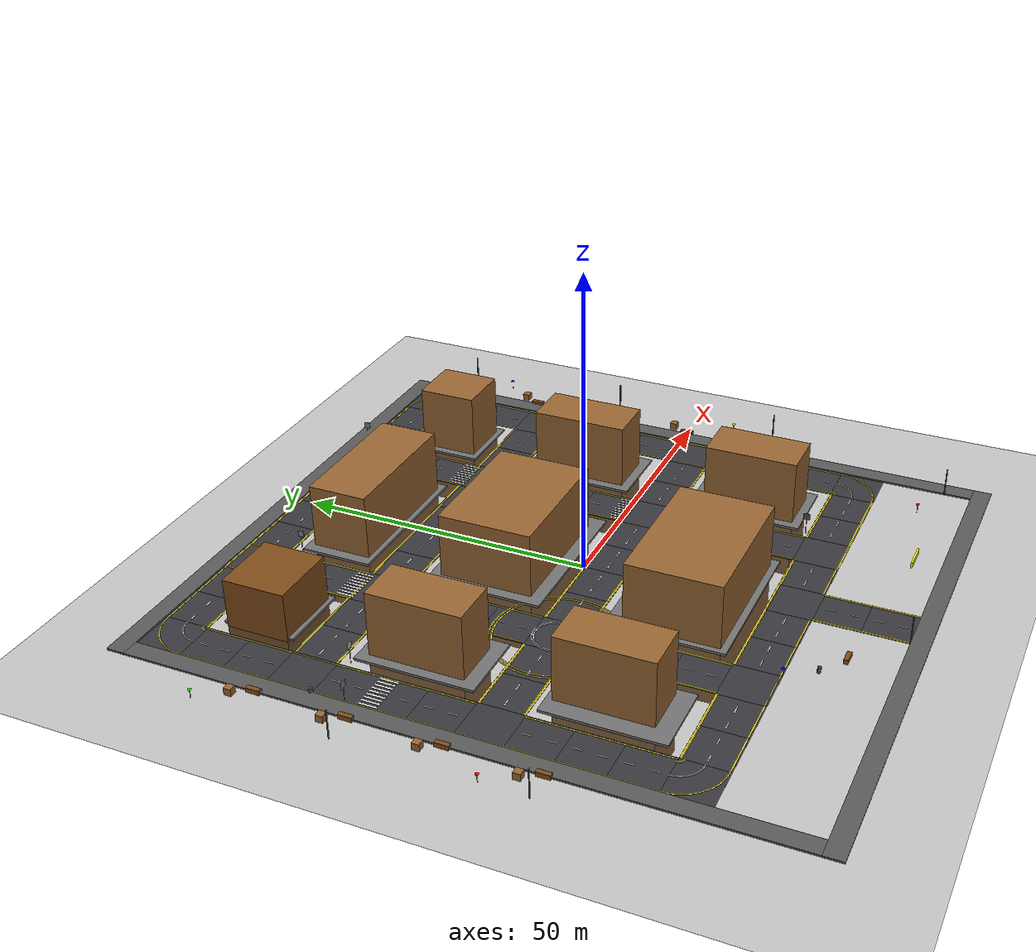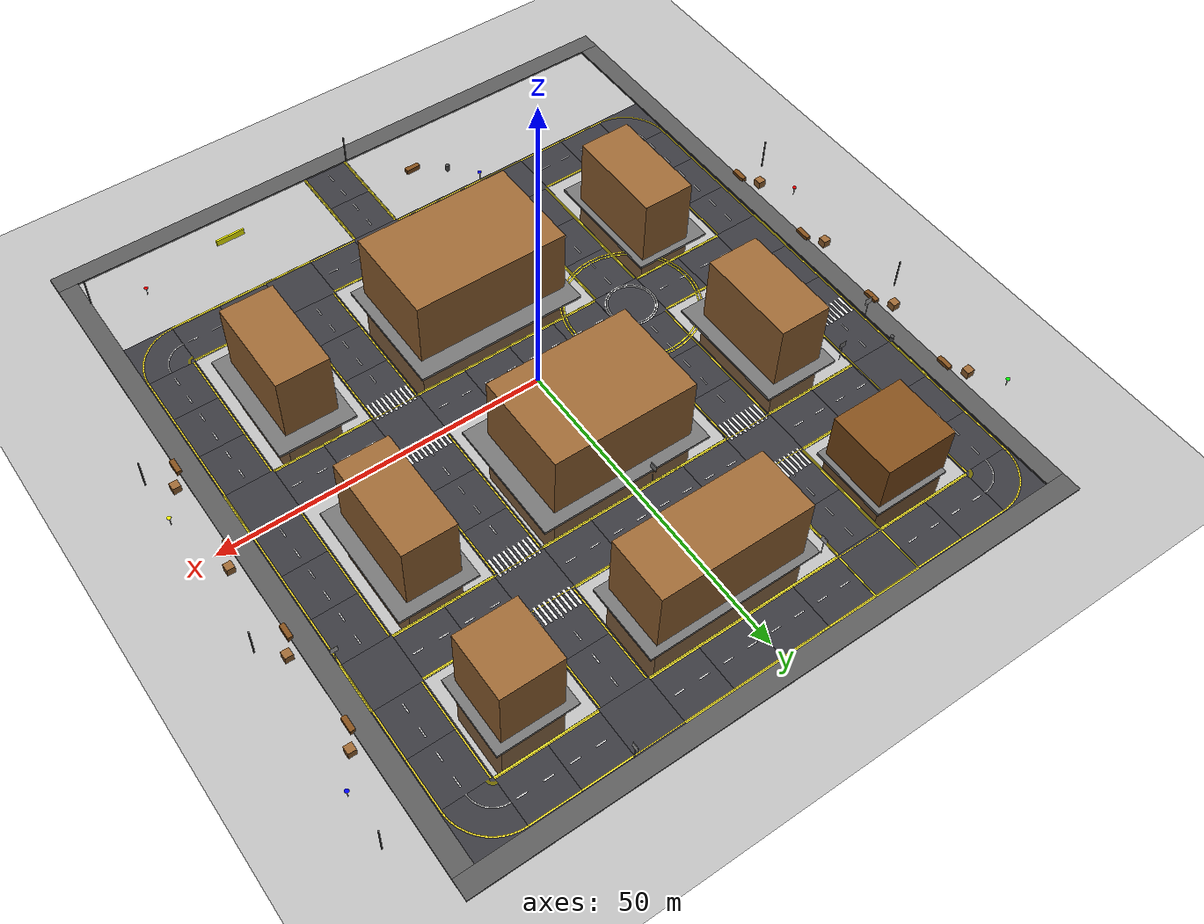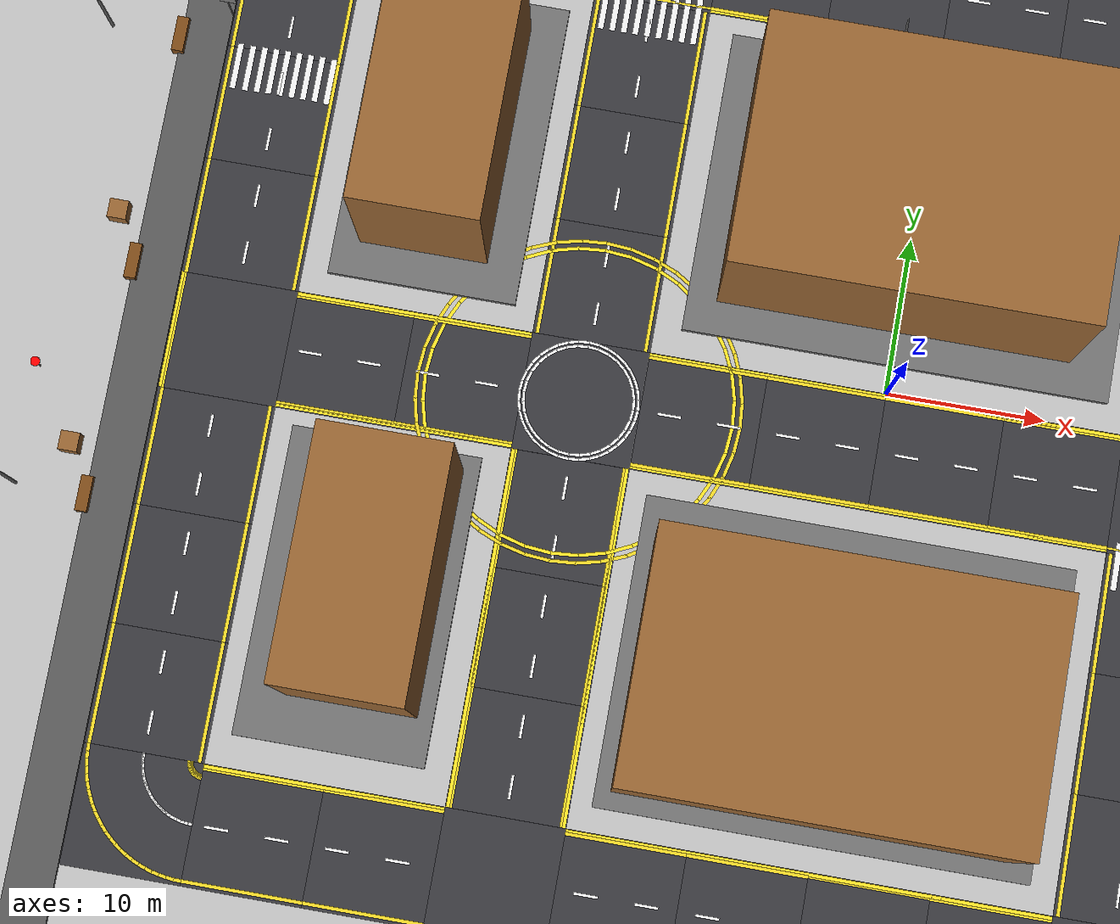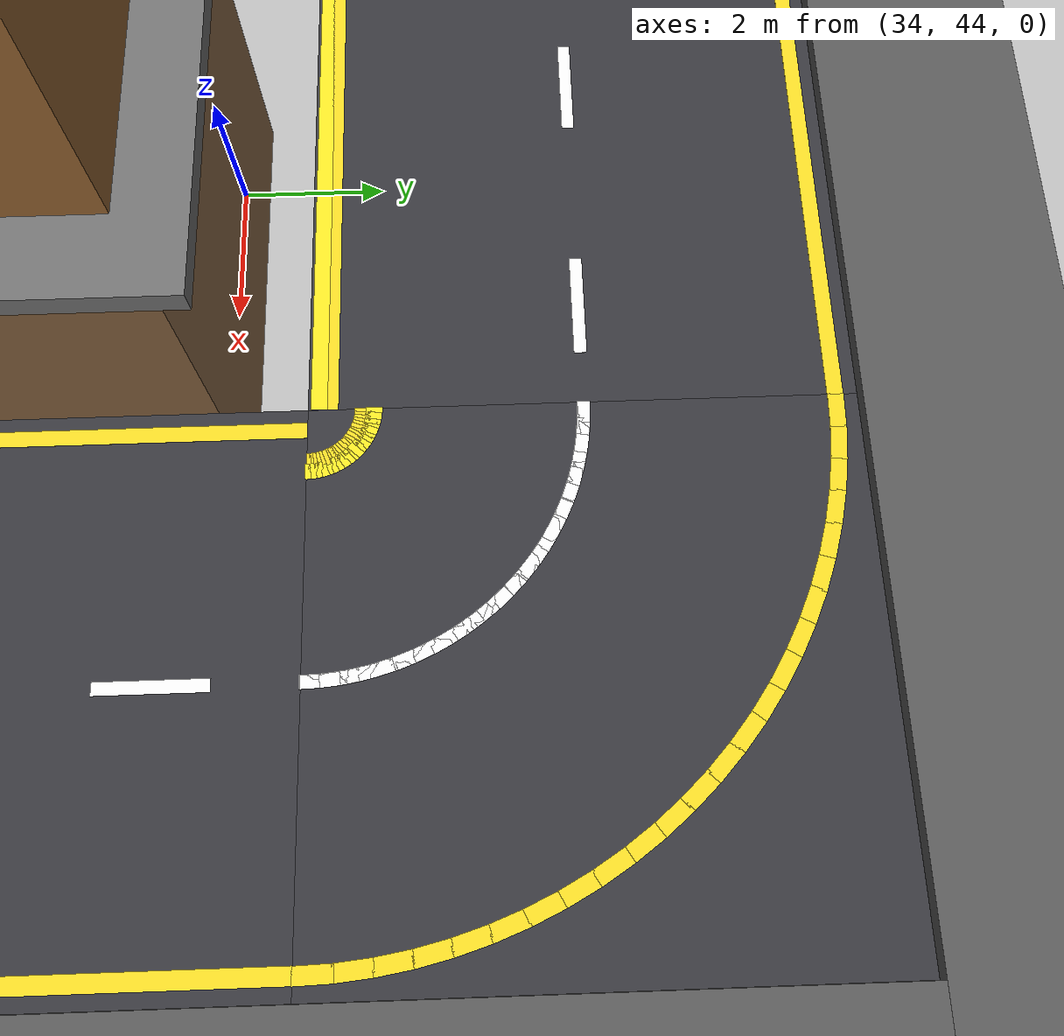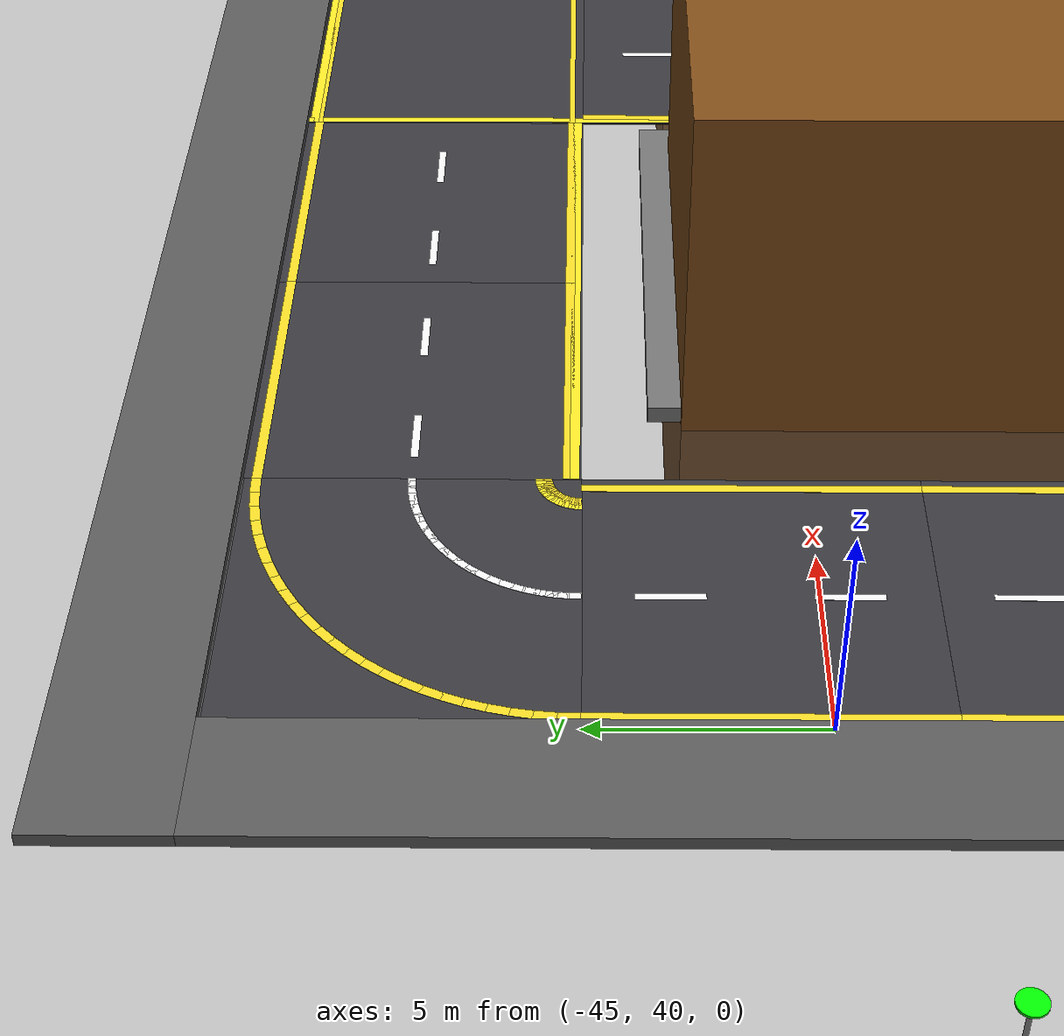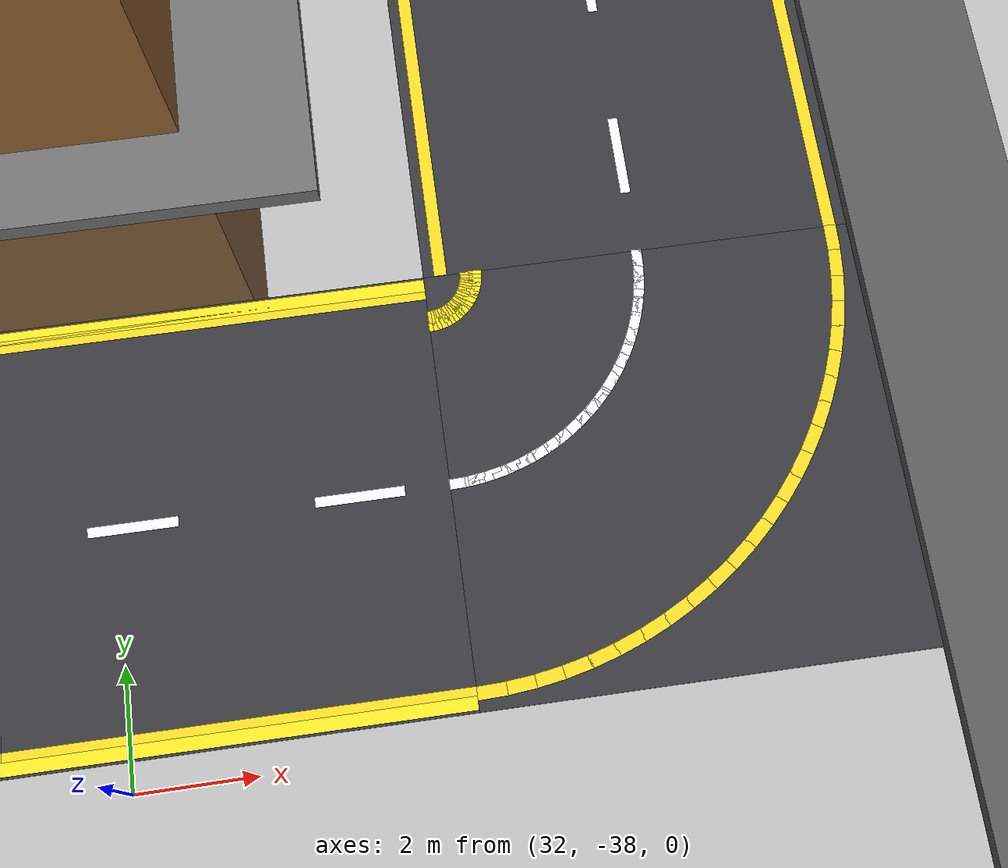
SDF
<sdf version="1.7">
 <world name="compact_city">
  <plugin name="auto_traffic_light" filename="libauto_traffic_light_plugin.so">
   <log_messages>1</log_messages>
  </plugin>
  <scene>
   <grid>0</grid>
   <origin_visual>0</origin_visual>
   <ambient>0.592 0.624 0.635 1</ambient>
   <sky><clouds><speed>12</speed></clouds></sky>
   <background>0.35 0.35 0.35 1</background>
   <shadows>1</shadows>
  </scene>
  <physics name="default_physics" default="0" type="ode">
   <max_step_size>0.001</max_step_size>
   <real_time_factor>1</real_time_factor>
   <real_time_update_rate>1000</real_time_update_rate>
  </physics>
  <spherical_coordinates>
   <surface_model>EARTH_WGS84</surface_model>
   <latitude_deg>0</latitude_deg>
   <longitude_deg>0</longitude_deg>
   <elevation>0</elevation>
   <heading_deg>0</heading_deg>
  </spherical_coordinates>
  <light name="sun" type="directional">
   <pose>0 0 1000 0 -0 0</pose>
   <diffuse>0.8 0.8 0.8 1</diffuse>
   <specular>0.5 0.5 0.5 1</specular>
   <attenuation>
    <range>1000</range>
    <constant>0.9</constant>
    <linear>0.01</linear>
    <quadratic>0.001</quadratic>
   </attenuation>
   <direction>-0.5 0.1 -0.4</direction>
   <spot><inner_angle>0</inner_angle><outer_angle>0</outer_angle><falloff>0</falloff></spot>
  </light>
  <model name="ground_plane">
   <static>1</static>
   <pose>0 0 0.01 0 -0 0</pose>
   <link name="link">
    <collision name="collision">
     <geometry><plane><normal>0 0 1</normal><size>200 200</size></plane></geometry>
    </collision>
    <visual name="visual">
     <geometry><plane><normal>0 0 1</normal><size>200 200</size></plane></geometry>
     <material>
      <ambient>0.2 0.2 0.2 1</ambient>
      <diffuse>0.25 0.25 0.25 1</diffuse>
      <specular>0.1 0.1 0.1 1</specular>
     </material>
    </visual>
   </link>
  </model>
  <model name="road_tile_1">
   <static>1</static>
   <pose>-41.2353 48.726 0.015 0 -0 0</pose>
   <link name="link">
    <collision name="collision"><geometry><box><size>7.5 7.5 0.03</size></box></geometry></collision>
    <visual name="visual">
     <geometry><box><size>7.5 7.5 0.03</size></box></geometry>
     <material>
      <ambient>0.18 0.18 0.2 1</ambient>
      <diffuse>0.22 0.22 0.24 1</diffuse>
      <specular>0.1 0.1 0.1 1</specular>
     </material>
    </visual>
   </link>
  </model>
  <model name="road_tile_2">
   <static>1</static>
   <pose>-33.75 48.75 0.015 0 -0 0</pose>
   <link name="link">
    <collision name="collision"><geometry><box><size>7.5 7.5 0.03</size></box></geometry></collision>
    <visual name="visual">
     <geometry><box><size>7.5 7.5 0.03</size></box></geometry>
     <material>
      <ambient>0.18 0.18 0.2 1</ambient>
      <diffuse>0.22 0.22 0.24 1</diffuse>
      <specular>0.1 0.1 0.1 1</specular>
     </material>
    </visual>
   </link>
  </model>
  <model name="road_tile_3">
   <static>1</static>
   <pose>-26.25 48.75 0.015 0 -0 0</pose>
   <link name="link">
    <collision name="collision"><geometry><box><size>7.5 7.5 0.03</size></box></geometry></collision>
    <visual name="visual">
     <geometry><box><size>7.5 7.5 0.03</size></box></geometry>
     <material>
      <ambient>0.18 0.18 0.2 1</ambient>
      <diffuse>0.22 0.22 0.24 1</diffuse>
      <specular>0.1 0.1 0.1 1</specular>
     </material>
    </visual>
   </link>
  </model>
  <model name="road_tile_4">
   <static>1</static>
   <pose>-18.75 48.75 0.015 0 -0 0</pose>
   <link name="link">
    <collision name="collision"><geometry><box><size>7.5 7.5 0.03</size></box></geometry></collision>
    <visual name="visual">
     <geometry><box><size>7.5 7.5 0.03</size></box></geometry>
     <material>
      <ambient>0.18 0.18 0.2 1</ambient>
      <diffuse>0.22 0.22 0.24 1</diffuse>
      <specular>0.1 0.1 0.1 1</specular>
     </material>
    </visual>
   </link>
  </model>
  <model name="road_tile_5">
   <static>1</static>
   <pose>-11.25 48.75 0.015 0 -0 0</pose>
   <link name="link">
    <collision name="collision"><geometry><box><size>7.5 7.5 0.03</size></box></geometry></collision>
    <visual name="visual">
     <geometry><box><size>7.5 7.5 0.03</size></box></geometry>
     <material>
      <ambient>0.18 0.18 0.2 1</ambient>
      <diffuse>0.22 0.22 0.24 1</diffuse>
      <specular>0.1 0.1 0.1 1</specular>
     </material>
    </visual>
   </link>
  </model>
  <model name="road_tile_6">
   <static>1</static>
   <pose>-3.75 48.75 0.015 0 -0 0</pose>
   <link name="link">
    <collision name="collision"><geometry><box><size>7.5 7.5 0.03</size></box></geometry></collision>
    <visual name="visual">
     <geometry><box><size>7.5 7.5 0.03</size></box></geometry>
     <material>
      <ambient>0.18 0.18 0.2 1</ambient>
      <diffuse>0.22 0.22 0.24 1</diffuse>
      <specular>0.1 0.1 0.1 1</specular>
     </material>
    </visual>
   </link>
  </model>
  <model name="road_tile_7">
   <static>1</static>
   <pose>3.75 48.75 0.015 0 -0 0</pose>
   <link name="link">
    <collision name="collision"><geometry><box><size>7.5 7.5 0.03</size></box></geometry></collision>
    <visual name="visual">
     <geometry><box><size>7.5 7.5 0.03</size></box></geometry>
     <material>
      <ambient>0.18 0.18 0.2 1</ambient>
      <diffuse>0.22 0.22 0.24 1</diffuse>
      <specular>0.1 0.1 0.1 1</specular>
     </material>
    </visual>
   </link>
  </model>
  <model name="road_tile_8">
   <static>1</static>
   <pose>11.25 48.75 0.015 0 -0 0</pose>
   <link name="link">
    <collision name="collision"><geometry><box><size>7.5 7.5 0.03</size></box></geometry></collision>
    <visual name="visual">
     <geometry><box><size>7.5 7.5 0.03</size></box></geometry>
     <material>
      <ambient>0.18 0.18 0.2 1</ambient>
      <diffuse>0.22 0.22 0.24 1</diffuse>
      <specular>0.1 0.1 0.1 1</specular>
     </material>
    </visual>
   </link>
  </model>
  <model name="road_tile_9">
   <static>1</static>
   <pose>18.75 48.75 0.015 0 -0 0</pose>
   <link name="link">
    <collision name="collision"><geometry><box><size>7.5 7.5 0.03</size></box></geometry></collision>
    <visual name="visual">
     <geometry><box><size>7.5 7.5 0.03</size></box></geometry>
     <material>
      <ambient>0.18 0.18 0.2 1</ambient>
      <diffuse>0.22 0.22 0.24 1</diffuse>
      <specular>0.1 0.1 0.1 1</specular>
     </material>
    </visual>
   </link>
  </model>
  <model name="road_tile_10">
   <static>1</static>
   <pose>26.25 48.75 0.015 0 -0 0</pose>
   <link name="link">
    <collision name="collision"><geometry><box><size>7.5 7.5 0.03</size></box></geometry></collision>
    <visual name="visual">
     <geometry><box><size>7.5 7.5 0.03</size></box></geometry>
     <material>
      <ambient>0.18 0.18 0.2 1</ambient>
      <diffuse>0.22 0.22 0.24 1</diffuse>
      <specular>0.1 0.1 0.1 1</specular>
     </material>
    </visual>
   </link>
  </model>
  <model name="road_tile_11">
   <static>1</static>
   <pose>33.75 48.75 0.015 0 -0 0</pose>
   <link name="link">
    <collision name="collision"><geometry><box><size>7.5 7.5 0.03</size></box></geometry></collision>
    <visual name="visual">
     <geometry><box><size>7.5 7.5 0.03</size></box></geometry>
     <material>
      <ambient>0.18 0.18 0.2 1</ambient>
      <diffuse>0.22 0.22 0.24 1</diffuse>
      <specular>0.1 0.1 0.1 1</specular>
     </material>
    </visual>
   </link>
  </model>
  <model name="road_tile_12">
   <static>1</static>
   <pose>41.25 48.75 0.015 0 -0 0</pose>
   <link name="link">
    <collision name="collision"><geometry><box><size>7.5 7.5 0.03</size></box></geometry></collision>
    <visual name="visual">
     <geometry><box><size>7.5 7.5 0.03</size></box></geometry>
     <material>
      <ambient>0.18 0.18 0.2 1</ambient>
      <diffuse>0.22 0.22 0.24 1</diffuse>
      <specular>0.1 0.1 0.1 1</specular>
     </material>
    </visual>
   </link>
  </model>
  <model name="road_tile_13">
   <static>1</static>
   <pose>-41.25 41.25 0.015 0 -0 1.5708</pose>
   <link name="link">
    <collision name="collision"><geometry><box><size>7.5 7.5 0.03</size></box></geometry></collision>
    <visual name="visual">
     <geometry><box><size>7.5 7.5 0.03</size></box></geometry>
     <material>
      <ambient>0.18 0.18 0.2 1</ambient>
      <diffuse>0.22 0.22 0.24 1</diffuse>
      <specular>0.1 0.1 0.1 1</specular>
     </material>
    </visual>
   </link>
  </model>
  <model name="road_tile_14">
   <static>1</static>
   <pose>-18.75 41.25 0.015 0 -0 1.5708</pose>
   <link name="link">
    <collision name="collision"><geometry><box><size>7.5 7.5 0.03</size></box></geometry></collision>
    <visual name="visual">
     <geometry><box><size>7.5 7.5 0.03</size></box></geometry>
     <material>
      <ambient>0.18 0.18 0.2 1</ambient>
      <diffuse>0.22 0.22 0.24 1</diffuse>
      <specular>0.1 0.1 0.1 1</specular>
     </material>
    </visual>
   </link>
  </model>
  <model name="road_tile_15">
   <static>1</static>
   <pose>18.75 41.25 0.015 0 -0 1.5708</pose>
   <link name="link">
    <collision name="collision"><geometry><box><size>7.5 7.5 0.03</size></box></geometry></collision>
    <visual name="visual">
     <geometry><box><size>7.5 7.5 0.03</size></box></geometry>
     <material>
      <ambient>0.18 0.18 0.2 1</ambient>
      <diffuse>0.22 0.22 0.24 1</diffuse>
      <specular>0.1 0.1 0.1 1</specular>
     </material>
    </visual>
   </link>
  </model>
  <model name="road_tile_16">
   <static>1</static>
   <pose>41.25 41.25 0.015 0 -0 1.5708</pose>
   <link name="link">
    <collision name="collision"><geometry><box><size>7.5 7.5 0.03</size></box></geometry></collision>
    <visual name="visual">
     <geometry><box><size>7.5 7.5 0.03</size></box></geometry>
     <material>
      <ambient>0.18 0.18 0.2 1</ambient>
      <diffuse>0.22 0.22 0.24 1</diffuse>
      <specular>0.1 0.1 0.1 1</specular>
     </material>
    </visual>
   </link>
  </model>
  <model name="road_tile_17">
   <static>1</static>
   <pose>-41.25 33.75 0.015 0 -0 1.5708</pose>
   <link name="link">
    <collision name="collision"><geometry><box><size>7.5 7.5 0.03</size></box></geometry></collision>
    <visual name="visual">
     <geometry><box><size>7.5 7.5 0.03</size></box></geometry>
     <material>
      <ambient>0.18 0.18 0.2 1</ambient>
      <diffuse>0.22 0.22 0.24 1</diffuse>
      <specular>0.1 0.1 0.1 1</specular>
     </material>
    </visual>
   </link>
  </model>
  <model name="road_tile_18">
   <static>1</static>
   <pose>-18.75 33.75 0.015 0 -0 1.5708</pose>
   <link name="link">
    <collision name="collision"><geometry><box><size>7.5 7.5 0.03</size></box></geometry></collision>
    <visual name="visual">
     <geometry><box><size>7.5 7.5 0.03</size></box></geometry>
     <material>
      <ambient>0.18 0.18 0.2 1</ambient>
      <diffuse>0.22 0.22 0.24 1</diffuse>
      <specular>0.1 0.1 0.1 1</specular>
     </material>
    </visual>
   </link>
  </model>
  <model name="road_tile_19">
   <static>1</static>
   <pose>18.75 33.75 0.015 0 -0 1.5708</pose>
   <link name="link">
    <collision name="collision"><geometry><box><size>7.5 7.5 0.03</size></box></geometry></collision>
    <visual name="visual">
     <geometry><box><size>7.5 7.5 0.03</size></box></geometry>
     <material>
      <ambient>0.18 0.18 0.2 1</ambient>
      <diffuse>0.22 0.22 0.24 1</diffuse>
      <specular>0.1 0.1 0.1 1</specular>
     </material>
    </visual>
   </link>
  </model>
  <model name="road_tile_20">
   <static>1</static>
   <pose>41.25 33.75 0.015 0 -0 1.5708</pose>
   <link name="link">
    <collision name="collision"><geometry><box><size>7.5 7.5 0.03</size></box></geometry></collision>
    <visual name="visual">
     <geometry><box><size>7.5 7.5 0.03</size></box></geometry>
     <material>
      <ambient>0.18 0.18 0.2 1</ambient>
      <diffuse>0.22 0.22 0.24 1</diffuse>
      <specular>0.1 0.1 0.1 1</specular>
     </material>
    </visual>
   </link>
  </model>
  <model name="road_tile_21">
   <static>1</static>
   <pose>-41.25 26.25 0.015 0 -0 0</pose>
   <link name="link">
    <collision name="collision"><geometry><box><size>7.5 7.5 0.03</size></box></geometry></collision>
    <visual name="visual">
     <geometry><box><size>7.5 7.5 0.03</size></box></geometry>
     <material>
      <ambient>0.18 0.18 0.2 1</ambient>
      <diffuse>0.22 0.22 0.24 1</diffuse>
      <specular>0.1 0.1 0.1 1</specular>
     </material>
    </visual>
   </link>
  </model>
  <model name="road_tile_22">
   <static>1</static>
   <pose>-33.75 26.25 0.015 0 -0 0</pose>
   <link name="link">
    <collision name="collision"><geometry><box><size>7.5 7.5 0.03</size></box></geometry></collision>
    <visual name="visual">
     <geometry><box><size>7.5 7.5 0.03</size></box></geometry>
     <material>
      <ambient>0.18 0.18 0.2 1</ambient>
      <diffuse>0.22 0.22 0.24 1</diffuse>
      <specular>0.1 0.1 0.1 1</specular>
     </material>
    </visual>
   </link>
  </model>
  <model name="road_tile_23">
   <static>1</static>
   <pose>-26.25 26.25 0.015 0 -0 0</pose>
   <link name="link">
    <collision name="collision"><geometry><box><size>7.5 7.5 0.03</size></box></geometry></collision>
    <visual name="visual">
     <geometry><box><size>7.5 7.5 0.03</size></box></geometry>
     <material>
      <ambient>0.18 0.18 0.2 1</ambient>
      <diffuse>0.22 0.22 0.24 1</diffuse>
      <specular>0.1 0.1 0.1 1</specular>
     </material>
    </visual>
   </link>
  </model>
  <model name="road_tile_24">
   <static>1</static>
   <pose>-18.75 26.25 0.015 0 -0 0</pose>
   <link name="link">
    <collision name="collision"><geometry><box><size>7.5 7.5 0.03</size></box></geometry></collision>
    <visual name="visual">
     <geometry><box><size>7.5 7.5 0.03</size></box></geometry>
     <material>
      <ambient>0.18 0.18 0.2 1</ambient>
      <diffuse>0.22 0.22 0.24 1</diffuse>
      <specular>0.1 0.1 0.1 1</specular>
     </material>
    </visual>
   </link>
  </model>
  <model name="road_tile_25">
   <static>1</static>
   <pose>-11.25 26.25 0.015 0 -0 0</pose>
   <link name="link">
    <collision name="collision"><geometry><box><size>7.5 7.5 0.03</size></box></geometry></collision>
    <visual name="visual">
     <geometry><box><size>7.5 7.5 0.03</size></box></geometry>
     <material>
      <ambient>0.18 0.18 0.2 1</ambient>
      <diffuse>0.22 0.22 0.24 1</diffuse>
      <specular>0.1 0.1 0.1 1</specular>
     </material>
    </visual>
   </link>
  </model>
  <model name="road_tile_26">
   <static>1</static>
   <pose>-3.75 26.25 0.015 0 -0 0</pose>
   <link name="link">
    <collision name="collision"><geometry><box><size>7.5 7.5 0.03</size></box></geometry></collision>
    <visual name="visual">
     <geometry><box><size>7.5 7.5 0.03</size></box></geometry>
     <material>
      <ambient>0.18 0.18 0.2 1</ambient>
      <diffuse>0.22 0.22 0.24 1</diffuse>
      <specular>0.1 0.1 0.1 1</specular>
     </material>
    </visual>
   </link>
  </model>
  <model name="road_tile_27">
   <static>1</static>
   <pose>3.75 26.25 0.015 0 -0 0</pose>
   <link name="link">
    <collision name="collision"><geometry><box><size>7.5 7.5 0.03</size></box></geometry></collision>
    <visual name="visual">
     <geometry><box><size>7.5 7.5 0.03</size></box></geometry>
     <material>
      <ambient>0.18 0.18 0.2 1</ambient>
      <diffuse>0.22 0.22 0.24 1</diffuse>
      <specular>0.1 0.1 0.1 1</specular>
     </material>
    </visual>
   </link>
  </model>
  <model name="road_tile_28">
   <static>1</static>
   <pose>11.25 26.25 0.015 0 -0 0</pose>
   <link name="link">
    <collision name="collision"><geometry><box><size>7.5 7.5 0.03</size></box></geometry></collision>
    <visual name="visual">
     <geometry><box><size>7.5 7.5 0.03</size></box></geometry>
     <material>
      <ambient>0.18 0.18 0.2 1</ambient>
      <diffuse>0.22 0.22 0.24 1</diffuse>
      <specular>0.1 0.1 0.1 1</specular>
     </material>
    </visual>
   </link>
  </model>
  <model name="road_tile_29">
   <static>1</static>
   <pose>18.75 26.25 0.015 0 -0 0</pose>
   <link name="link">
    <collision name="collision"><geometry><box><size>7.5 7.5 0.03</size></box></geometry></collision>
    <visual name="visual">
     <geometry><box><size>7.5 7.5 0.03</size></box></geometry>
     <material>
      <ambient>0.18 0.18 0.2 1</ambient>
      <diffuse>0.22 0.22 0.24 1</diffuse>
      <specular>0.1 0.1 0.1 1</specular>
     </material>
    </visual>
   </link>
  </model>
  <model name="road_tile_30">
   <static>1</static>
   <pose>26.25 26.25 0.015 0 -0 0</pose>
   <link name="link">
    <collision name="collision"><geometry><box><size>7.5 7.5 0.03</size></box></geometry></collision>
    <visual name="visual">
     <geometry><box><size>7.5 7.5 0.03</size></box></geometry>
     <material>
      <ambient>0.18 0.18 0.2 1</ambient>
      <diffuse>0.22 0.22 0.24 1</diffuse>
      <specular>0.1 0.1 0.1 1</specular>
     </material>
    </visual>
   </link>
  </model>
  <model name="road_tile_31">
   <static>1</static>
   <pose>33.75 26.25 0.015 0 -0 0</pose>
   <link name="link">
    <collision name="collision"><geometry><box><size>7.5 7.5 0.03</size></box></geometry></collision>
    <visual name="visual">
     <geometry><box><size>7.5 7.5 0.03</size></box></geometry>
     <material>
      <ambient>0.18 0.18 0.2 1</ambient>
      <diffuse>0.22 0.22 0.24 1</diffuse>
      <specular>0.1 0.1 0.1 1</specular>
     </material>
    </visual>
   </link>
  </model>
  <model name="road_tile_32">
   <static>1</static>
   <pose>41.25 26.25 0.015 0 -0 0</pose>
   <link name="link">
    <collision name="collision"><geometry><box><size>7.5 7.5 0.03</size></box></geometry></collision>
    <visual name="visual">
     <geometry><box><size>7.5 7.5 0.03</size></box></geometry>
     <material>
      <ambient>0.18 0.18 0.2 1</ambient>
      <diffuse>0.22 0.22 0.24 1</diffuse>
      <specular>0.1 0.1 0.1 1</specular>
     </material>
    </visual>
   </link>
  </model>
  <model name="road_tile_33">
   <static>1</static>
   <pose>-41.25 18.75 0.015 0 -0 1.5708</pose>
   <link name="link">
    <collision name="collision"><geometry><box><size>7.5 7.5 0.03</size></box></geometry></collision>
    <visual name="visual">
     <geometry><box><size>7.5 7.5 0.03</size></box></geometry>
     <material>
      <ambient>0.18 0.18 0.2 1</ambient>
      <diffuse>0.22 0.22 0.24 1</diffuse>
      <specular>0.1 0.1 0.1 1</specular>
     </material>
    </visual>
   </link>
  </model>
  <model name="road_tile_34">
   <static>1</static>
   <pose>-18.75 18.75 0.015 0 -0 1.5708</pose>
   <link name="link">
    <collision name="collision"><geometry><box><size>7.5 7.5 0.03</size></box></geometry></collision>
    <visual name="visual">
     <geometry><box><size>7.5 7.5 0.03</size></box></geometry>
     <material>
      <ambient>0.18 0.18 0.2 1</ambient>
      <diffuse>0.22 0.22 0.24 1</diffuse>
      <specular>0.1 0.1 0.1 1</specular>
     </material>
    </visual>
   </link>
  </model>
  <model name="road_tile_35">
   <static>1</static>
   <pose>18.75 18.75 0.015 0 -0 1.5708</pose>
   <link name="link">
    <collision name="collision"><geometry><box><size>7.5 7.5 0.03</size></box></geometry></collision>
    <visual name="visual">
     <geometry><box><size>7.5 7.5 0.03</size></box></geometry>
     <material>
      <ambient>0.18 0.18 0.2 1</ambient>
      <diffuse>0.22 0.22 0.24 1</diffuse>
      <specular>0.1 0.1 0.1 1</specular>
     </material>
    </visual>
   </link>
  </model>
  <model name="road_tile_36">
   <static>1</static>
   <pose>41.25 18.75 0.015 0 -0 1.5708</pose>
   <link name="link">
    <collision name="collision"><geometry><box><size>7.5 7.5 0.03</size></box></geometry></collision>
    <visual name="visual">
     <geometry><box><size>7.5 7.5 0.03</size></box></geometry>
     <material>
      <ambient>0.18 0.18 0.2 1</ambient>
      <diffuse>0.22 0.22 0.24 1</diffuse>
      <specular>0.1 0.1 0.1 1</specular>
     </material>
    </visual>
   </link>
  </model>
  <model name="road_tile_37">
   <static>1</static>
   <pose>-41.25 11.25 0.015 0 -0 1.5708</pose>
   <link name="link">
    <collision name="collision"><geometry><box><size>7.5 7.5 0.03</size></box></geometry></collision>
    <visual name="visual">
     <geometry><box><size>7.5 7.5 0.03</size></box></geometry>
     <material>
      <ambient>0.18 0.18 0.2 1</ambient>
      <diffuse>0.22 0.22 0.24 1</diffuse>
      <specular>0.1 0.1 0.1 1</specular>
     </material>
    </visual>
   </link>
  </model>
  <model name="road_tile_38">
   <static>1</static>
   <pose>-18.75 11.25 0.015 0 -0 1.5708</pose>
   <link name="link">
    <collision name="collision"><geometry><box><size>7.5 7.5 0.03</size></box></geometry></collision>
    <visual name="visual">
     <geometry><box><size>7.5 7.5 0.03</size></box></geometry>
     <material>
      <ambient>0.18 0.18 0.2 1</ambient>
      <diffuse>0.22 0.22 0.24 1</diffuse>
      <specular>0.1 0.1 0.1 1</specular>
     </material>
    </visual>
   </link>
  </model>
  <model name="road_tile_39">
   <static>1</static>
   <pose>18.75 11.25 0.015 0 -0 1.5708</pose>
   <link name="link">
    <collision name="collision"><geometry><box><size>7.5 7.5 0.03</size></box></geometry></collision>
    <visual name="visual">
     <geometry><box><size>7.5 7.5 0.03</size></box></geometry>
     <material>
      <ambient>0.18 0.18 0.2 1</ambient>
      <diffuse>0.22 0.22 0.24 1</diffuse>
      <specular>0.1 0.1 0.1 1</specular>
     </material>
    </visual>
   </link>
  </model>
  <model name="road_tile_40">
   <static>1</static>
   <pose>41.25 11.25 0.015 0 -0 1.5708</pose>
   <link name="link">
    <collision name="collision"><geometry><box><size>7.5 7.5 0.03</size></box></geometry></collision>
    <visual name="visual">
     <geometry><box><size>7.5 7.5 0.03</size></box></geometry>
     <material>
      <ambient>0.18 0.18 0.2 1</ambient>
      <diffuse>0.22 0.22 0.24 1</diffuse>
      <specular>0.1 0.1 0.1 1</specular>
     </material>
    </visual>
   </link>
  </model>
  <model name="road_tile_41">
   <static>1</static>
   <pose>-41.25 3.75 0.015 0 -0 1.5708</pose>
   <link name="link">
    <collision name="collision"><geometry><box><size>7.5 7.5 0.03</size></box></geometry></collision>
    <visual name="visual">
     <geometry><box><size>7.5 7.5 0.03</size></box></geometry>
     <material>
      <ambient>0.18 0.18 0.2 1</ambient>
      <diffuse>0.22 0.22 0.24 1</diffuse>
      <specular>0.1 0.1 0.1 1</specular>
     </material>
    </visual>
   </link>
  </model>
  <model name="road_tile_42">
   <static>1</static>
   <pose>-18.75 3.75 0.015 0 -0 1.5708</pose>
   <link name="link">
    <collision name="collision"><geometry><box><size>7.5 7.5 0.03</size></box></geometry></collision>
    <visual name="visual">
     <geometry><box><size>7.5 7.5 0.03</size></box></geometry>
     <material>
      <ambient>0.18 0.18 0.2 1</ambient>
      <diffuse>0.22 0.22 0.24 1</diffuse>
      <specular>0.1 0.1 0.1 1</specular>
     </material>
    </visual>
   </link>
  </model>
  <model name="road_tile_43">
   <static>1</static>
   <pose>18.75 3.75 0.015 0 -0 1.5708</pose>
   <link name="link">
    <collision name="collision"><geometry><box><size>7.5 7.5 0.03</size></box></geometry></collision>
    <visual name="visual">
     <geometry><box><size>7.5 7.5 0.03</size></box></geometry>
     <material>
      <ambient>0.18 0.18 0.2 1</ambient>
      <diffuse>0.22 0.22 0.24 1</diffuse>
      <specular>0.1 0.1 0.1 1</specular>
     </material>
    </visual>
   </link>
  </model>
  <model name="road_tile_44">
   <static>1</static>
   <pose>41.25 3.75 0.015 0 -0 1.5708</pose>
   <link name="link">
    <collision name="collision"><geometry><box><size>7.5 7.5 0.03</size></box></geometry></collision>
    <visual name="visual">
     <geometry><box><size>7.5 7.5 0.03</size></box></geometry>
     <material>
      <ambient>0.18 0.18 0.2 1</ambient>
      <diffuse>0.22 0.22 0.24 1</diffuse>
      <specular>0.1 0.1 0.1 1</specular>
     </material>
    </visual>
   </link>
  </model>
  <model name="road_tile_45">
   <static>1</static>
   <pose>-41.25 -3.75 0.015 0 -0 0</pose>
   <link name="link">
    <collision name="collision"><geometry><box><size>7.5 7.5 0.03</size></box></geometry></collision>
    <visual name="visual">
     <geometry><box><size>7.5 7.5 0.03</size></box></geometry>
     <material>
      <ambient>0.18 0.18 0.2 1</ambient>
      <diffuse>0.22 0.22 0.24 1</diffuse>
      <specular>0.1 0.1 0.1 1</specular>
     </material>
    </visual>
   </link>
  </model>
  <model name="road_tile_46">
   <static>1</static>
   <pose>-33.75 -3.75 0.015 0 -0 0</pose>
   <link name="link">
    <collision name="collision"><geometry><box><size>7.5 7.5 0.03</size></box></geometry></collision>
    <visual name="visual">
     <geometry><box><size>7.5 7.5 0.03</size></box></geometry>
     <material>
      <ambient>0.18 0.18 0.2 1</ambient>
      <diffuse>0.22 0.22 0.24 1</diffuse>
      <specular>0.1 0.1 0.1 1</specular>
     </material>
    </visual>
   </link>
  </model>
  <model name="road_tile_47">
   <static>1</static>
   <pose>-26.25 -3.75 0.015 0 -0 0</pose>
   <link name="link">
    <collision name="collision"><geometry><box><size>7.5 7.5 0.03</size></box></geometry></collision>
    <visual name="visual">
     <geometry><box><size>7.5 7.5 0.03</size></box></geometry>
     <material>
      <ambient>0.18 0.18 0.2 1</ambient>
      <diffuse>0.22 0.22 0.24 1</diffuse>
      <specular>0.1 0.1 0.1 1</specular>
     </material>
    </visual>
   </link>
  </model>
  <model name="road_tile_48">
   <static>1</static>
   <pose>-11.25 -3.75 0.015 0 -0 0</pose>
   <link name="link">
    <collision name="collision"><geometry><box><size>7.5 7.5 0.03</size></box></geometry></collision>
    <visual name="visual">
     <geometry><box><size>7.5 7.5 0.03</size></box></geometry>
     <material>
      <ambient>0.18 0.18 0.2 1</ambient>
      <diffuse>0.22 0.22 0.24 1</diffuse>
      <specular>0.1 0.1 0.1 1</specular>
     </material>
    </visual>
   </link>
  </model>
  <model name="road_tile_49">
   <static>1</static>
   <pose>-3.75 -3.75 0.015 0 -0 0</pose>
   <link name="link">
    <collision name="collision"><geometry><box><size>7.5 7.5 0.03</size></box></geometry></collision>
    <visual name="visual">
     <geometry><box><size>7.5 7.5 0.03</size></box></geometry>
     <material>
      <ambient>0.18 0.18 0.2 1</ambient>
      <diffuse>0.22 0.22 0.24 1</diffuse>
      <specular>0.1 0.1 0.1 1</specular>
     </material>
    </visual>
   </link>
  </model>
  <model name="road_tile_50">
   <static>1</static>
   <pose>3.75 -3.75 0.015 0 -0 0</pose>
   <link name="link">
    <collision name="collision"><geometry><box><size>7.5 7.5 0.03</size></box></geometry></collision>
    <visual name="visual">
     <geometry><box><size>7.5 7.5 0.03</size></box></geometry>
     <material>
      <ambient>0.18 0.18 0.2 1</ambient>
      <diffuse>0.22 0.22 0.24 1</diffuse>
      <specular>0.1 0.1 0.1 1</specular>
     </material>
    </visual>
   </link>
  </model>
  <model name="road_tile_51">
   <static>1</static>
   <pose>11.25 -3.75 0.015 0 -0 0</pose>
   <link name="link">
    <collision name="collision"><geometry><box><size>7.5 7.5 0.03</size></box></geometry></collision>
    <visual name="visual">
     <geometry><box><size>7.5 7.5 0.03</size></box></geometry>
     <material>
      <ambient>0.18 0.18 0.2 1</ambient>
      <diffuse>0.22 0.22 0.24 1</diffuse>
      <specular>0.1 0.1 0.1 1</specular>
     </material>
    </visual>
   </link>
  </model>
  <model name="road_tile_52">
   <static>1</static>
   <pose>18.75 -3.75 0.015 0 -0 0</pose>
   <link name="link">
    <collision name="collision"><geometry><box><size>7.5 7.5 0.03</size></box></geometry></collision>
    <visual name="visual">
     <geometry><box><size>7.5 7.5 0.03</size></box></geometry>
     <material>
      <ambient>0.18 0.18 0.2 1</ambient>
      <diffuse>0.22 0.22 0.24 1</diffuse>
      <specular>0.1 0.1 0.1 1</specular>
     </material>
    </visual>
   </link>
  </model>
  <model name="road_tile_53">
   <static>1</static>
   <pose>26.25 -3.75 0.015 0 -0 0</pose>
   <link name="link">
    <collision name="collision"><geometry><box><size>7.5 7.5 0.03</size></box></geometry></collision>
    <visual name="visual">
     <geometry><box><size>7.5 7.5 0.03</size></box></geometry>
     <material>
      <ambient>0.18 0.18 0.2 1</ambient>
      <diffuse>0.22 0.22 0.24 1</diffuse>
      <specular>0.1 0.1 0.1 1</specular>
     </material>
    </visual>
   </link>
  </model>
  <model name="road_tile_54">
   <static>1</static>
   <pose>33.75 -3.75 0.015 0 -0 0</pose>
   <link name="link">
    <collision name="collision"><geometry><box><size>7.5 7.5 0.03</size></box></geometry></collision>
    <visual name="visual">
     <geometry><box><size>7.5 7.5 0.03</size></box></geometry>
     <material>
      <ambient>0.18 0.18 0.2 1</ambient>
      <diffuse>0.22 0.22 0.24 1</diffuse>
      <specular>0.1 0.1 0.1 1</specular>
     </material>
    </visual>
   </link>
  </model>
  <model name="road_tile_55">
   <static>1</static>
   <pose>41.25 -3.75 0.015 0 -0 0</pose>
   <link name="link">
    <collision name="collision"><geometry><box><size>7.5 7.5 0.03</size></box></geometry></collision>
    <visual name="visual">
     <geometry><box><size>7.5 7.5 0.03</size></box></geometry>
     <material>
      <ambient>0.18 0.18 0.2 1</ambient>
      <diffuse>0.22 0.22 0.24 1</diffuse>
      <specular>0.1 0.1 0.1 1</specular>
     </material>
    </visual>
   </link>
  </model>
  <model name="road_tile_56">
   <static>1</static>
   <pose>-41.25 -11.25 0.015 0 -0 1.5708</pose>
   <link name="link">
    <collision name="collision"><geometry><box><size>7.5 7.5 0.03</size></box></geometry></collision>
    <visual name="visual">
     <geometry><box><size>7.5 7.5 0.03</size></box></geometry>
     <material>
      <ambient>0.18 0.18 0.2 1</ambient>
      <diffuse>0.22 0.22 0.24 1</diffuse>
      <specular>0.1 0.1 0.1 1</specular>
     </material>
    </visual>
   </link>
  </model>
  <model name="road_tile_57">
   <static>1</static>
   <pose>-18.75 -11.25 0.015 0 -0 1.5708</pose>
   <link name="link">
    <collision name="collision"><geometry><box><size>7.5 7.5 0.03</size></box></geometry></collision>
    <visual name="visual">
     <geometry><box><size>7.5 7.5 0.03</size></box></geometry>
     <material>
      <ambient>0.18 0.18 0.2 1</ambient>
      <diffuse>0.22 0.22 0.24 1</diffuse>
      <specular>0.1 0.1 0.1 1</specular>
     </material>
    </visual>
   </link>
  </model>
  <model name="road_tile_58">
   <static>1</static>
   <pose>18.75 -11.25 0.015 0 -0 1.5708</pose>
   <link name="link">
    <collision name="collision"><geometry><box><size>7.5 7.5 0.03</size></box></geometry></collision>
    <visual name="visual">
     <geometry><box><size>7.5 7.5 0.03</size></box></geometry>
     <material>
      <ambient>0.18 0.18 0.2 1</ambient>
      <diffuse>0.22 0.22 0.24 1</diffuse>
      <specular>0.1 0.1 0.1 1</specular>
     </material>
    </visual>
   </link>
  </model>
  <model name="road_tile_59">
   <static>1</static>
   <pose>41.25 -11.25 0.015 0 -0 1.5708</pose>
   <link name="link">
    <collision name="collision"><geometry><box><size>7.5 7.5 0.03</size></box></geometry></collision>
    <visual name="visual">
     <geometry><box><size>7.5 7.5 0.03</size></box></geometry>
     <material>
      <ambient>0.18 0.18 0.2 1</ambient>
      <diffuse>0.22 0.22 0.24 1</diffuse>
      <specular>0.1 0.1 0.1 1</specular>
     </material>
    </visual>
   </link>
  </model>
  <model name="road_tile_60">
   <static>1</static>
   <pose>-41.25 -18.75 0.015 0 -0 1.5708</pose>
   <link name="link">
    <collision name="collision"><geometry><box><size>7.5 7.5 0.03</size></box></geometry></collision>
    <visual name="visual">
     <geometry><box><size>7.5 7.5 0.03</size></box></geometry>
     <material>
      <ambient>0.18 0.18 0.2 1</ambient>
      <diffuse>0.22 0.22 0.24 1</diffuse>
      <specular>0.1 0.1 0.1 1</specular>
     </material>
    </visual>
   </link>
  </model>
  <model name="road_tile_61">
   <static>1</static>
   <pose>-18.75 -18.75 0.015 0 -0 1.5708</pose>
   <link name="link">
    <collision name="collision"><geometry><box><size>7.5 7.5 0.03</size></box></geometry></collision>
    <visual name="visual">
     <geometry><box><size>7.5 7.5 0.03</size></box></geometry>
     <material>
      <ambient>0.18 0.18 0.2 1</ambient>
      <diffuse>0.22 0.22 0.24 1</diffuse>
      <specular>0.1 0.1 0.1 1</specular>
     </material>
    </visual>
   </link>
  </model>
  <model name="road_tile_62">
   <static>1</static>
   <pose>18.75 -18.75 0.015 0 -0 1.5708</pose>
   <link name="link">
    <collision name="collision"><geometry><box><size>7.5 7.5 0.03</size></box></geometry></collision>
    <visual name="visual">
     <geometry><box><size>7.5 7.5 0.03</size></box></geometry>
     <material>
      <ambient>0.18 0.18 0.2 1</ambient>
      <diffuse>0.22 0.22 0.24 1</diffuse>
      <specular>0.1 0.1 0.1 1</specular>
     </material>
    </visual>
   </link>
  </model>
  <model name="road_tile_63">
   <static>1</static>
   <pose>41.25 -18.75 0.015 0 -0 1.5708</pose>
   <link name="link">
    <collision name="collision"><geometry><box><size>7.5 7.5 0.03</size></box></geometry></collision>
    <visual name="visual">
     <geometry><box><size>7.5 7.5 0.03</size></box></geometry>
     <material>
      <ambient>0.18 0.18 0.2 1</ambient>
      <diffuse>0.22 0.22 0.24 1</diffuse>
      <specular>0.1 0.1 0.1 1</specular>
     </material>
    </visual>
   </link>
  </model>
  <model name="road_tile_64">
   <static>1</static>
   <pose>-41.25 -26.25 0.015 0 -0 1.5708</pose>
   <link name="link">
    <collision name="collision"><geometry><box><size>7.5 7.5 0.03</size></box></geometry></collision>
    <visual name="visual">
     <geometry><box><size>7.5 7.5 0.03</size></box></geometry>
     <material>
      <ambient>0.18 0.18 0.2 1</ambient>
      <diffuse>0.22 0.22 0.24 1</diffuse>
      <specular>0.1 0.1 0.1 1</specular>
     </material>
    </visual>
   </link>
  </model>
  <model name="road_tile_65">
   <static>1</static>
   <pose>-18.75 -26.25 0.015 0 -0 1.5708</pose>
   <link name="link">
    <collision name="collision"><geometry><box><size>7.5 7.5 0.03</size></box></geometry></collision>
    <visual name="visual">
     <geometry><box><size>7.5 7.5 0.03</size></box></geometry>
     <material>
      <ambient>0.18 0.18 0.2 1</ambient>
      <diffuse>0.22 0.22 0.24 1</diffuse>
      <specular>0.1 0.1 0.1 1</specular>
     </material>
    </visual>
   </link>
  </model>
  <model name="road_tile_66">
   <static>1</static>
   <pose>18.75 -26.25 0.015 0 -0 1.5708</pose>
   <link name="link">
    <collision name="collision"><geometry><box><size>7.5 7.5 0.03</size></box></geometry></collision>
    <visual name="visual">
     <geometry><box><size>7.5 7.5 0.03</size></box></geometry>
     <material>
      <ambient>0.18 0.18 0.2 1</ambient>
      <diffuse>0.22 0.22 0.24 1</diffuse>
      <specular>0.1 0.1 0.1 1</specular>
     </material>
    </visual>
   </link>
  </model>
  <model name="road_tile_67">
   <static>1</static>
   <pose>41.25 -26.25 0.015 0 -0 1.5708</pose>
   <link name="link">
    <collision name="collision"><geometry><box><size>7.5 7.5 0.03</size></box></geometry></collision>
    <visual name="visual">
     <geometry><box><size>7.5 7.5 0.03</size></box></geometry>
     <material>
      <ambient>0.18 0.18 0.2 1</ambient>
      <diffuse>0.22 0.22 0.24 1</diffuse>
      <specular>0.1 0.1 0.1 1</specular>
     </material>
    </visual>
   </link>
  </model>
  <model name="road_tile_68">
   <static>1</static>
   <pose>-41.25 -33.75 0.015 0 -0 0</pose>
   <link name="link">
    <collision name="collision"><geometry><box><size>7.5 7.5 0.03</size></box></geometry></collision>
    <visual name="visual">
     <geometry><box><size>7.5 7.5 0.03</size></box></geometry>
     <material>
      <ambient>0.18 0.18 0.2 1</ambient>
      <diffuse>0.22 0.22 0.24 1</diffuse>
      <specular>0.1 0.1 0.1 1</specular>
     </material>
    </visual>
   </link>
  </model>
  <model name="road_tile_69">
   <static>1</static>
   <pose>-33.75 -33.75 0.015 0 -0 0</pose>
   <link name="link">
    <collision name="collision"><geometry><box><size>7.5 7.5 0.03</size></box></geometry></collision>
    <visual name="visual">
     <geometry><box><size>7.5 7.5 0.03</size></box></geometry>
     <material>
      <ambient>0.18 0.18 0.2 1</ambient>
      <diffuse>0.22 0.22 0.24 1</diffuse>
      <specular>0.1 0.1 0.1 1</specular>
     </material>
    </visual>
   </link>
  </model>
  <model name="road_tile_70">
   <static>1</static>
   <pose>-26.25 -33.75 0.015 0 -0 0</pose>
   <link name="link">
    <collision name="collision"><geometry><box><size>7.5 7.5 0.03</size></box></geometry></collision>
    <visual name="visual">
     <geometry><box><size>7.5 7.5 0.03</size></box></geometry>
     <material>
      <ambient>0.18 0.18 0.2 1</ambient>
      <diffuse>0.22 0.22 0.24 1</diffuse>
      <specular>0.1 0.1 0.1 1</specular>
     </material>
    </visual>
   </link>
  </model>
  <model name="road_tile_71">
   <static>1</static>
   <pose>-18.75 -33.75 0.015 0 -0 0</pose>
   <link name="link">
    <collision name="collision"><geometry><box><size>7.5 7.5 0.03</size></box></geometry></collision>
    <visual name="visual">
     <geometry><box><size>7.5 7.5 0.03</size></box></geometry>
     <material>
      <ambient>0.18 0.18 0.2 1</ambient>
      <diffuse>0.22 0.22 0.24 1</diffuse>
      <specular>0.1 0.1 0.1 1</specular>
     </material>
    </visual>
   </link>
  </model>
  <model name="road_tile_72">
   <static>1</static>
   <pose>-11.25 -33.75 0.015 0 -0 0</pose>
   <link name="link">
    <collision name="collision"><geometry><box><size>7.5 7.5 0.03</size></box></geometry></collision>
    <visual name="visual">
     <geometry><box><size>7.5 7.5 0.03</size></box></geometry>
     <material>
      <ambient>0.18 0.18 0.2 1</ambient>
      <diffuse>0.22 0.22 0.24 1</diffuse>
      <specular>0.1 0.1 0.1 1</specular>
     </material>
    </visual>
   </link>
  </model>
  <model name="road_tile_73">
   <static>1</static>
   <pose>-3.75 -33.75 0.015 0 -0 0</pose>
   <link name="link">
    <collision name="collision"><geometry><box><size>7.5 7.5 0.03</size></box></geometry></collision>
    <visual name="visual">
     <geometry><box><size>7.5 7.5 0.03</size></box></geometry>
     <material>
      <ambient>0.18 0.18 0.2 1</ambient>
      <diffuse>0.22 0.22 0.24 1</diffuse>
      <specular>0.1 0.1 0.1 1</specular>
     </material>
    </visual>
   </link>
  </model>
  <model name="road_tile_74">
   <static>1</static>
   <pose>3.75 -33.75 0.015 0 -0 0</pose>
   <link name="link">
    <collision name="collision"><geometry><box><size>7.5 7.5 0.03</size></box></geometry></collision>
    <visual name="visual">
     <geometry><box><size>7.5 7.5 0.03</size></box></geometry>
     <material>
      <ambient>0.18 0.18 0.2 1</ambient>
      <diffuse>0.22 0.22 0.24 1</diffuse>
      <specular>0.1 0.1 0.1 1</specular>
     </material>
    </visual>
   </link>
  </model>
  <model name="road_tile_75">
   <static>1</static>
   <pose>11.25 -33.75 0.015 0 -0 0</pose>
   <link name="link">
    <collision name="collision"><geometry><box><size>7.5 7.5 0.03</size></box></geometry></collision>
    <visual name="visual">
     <geometry><box><size>7.5 7.5 0.03</size></box></geometry>
     <material>
      <ambient>0.18 0.18 0.2 1</ambient>
      <diffuse>0.22 0.22 0.24 1</diffuse>
      <specular>0.1 0.1 0.1 1</specular>
     </material>
    </visual>
   </link>
  </model>
  <model name="road_tile_76">
   <static>1</static>
   <pose>18.75 -33.75 0.015 0 -0 0</pose>
   <link name="link">
    <collision name="collision"><geometry><box><size>7.5 7.5 0.03</size></box></geometry></collision>
    <visual name="visual">
     <geometry><box><size>7.5 7.5 0.03</size></box></geometry>
     <material>
      <ambient>0.18 0.18 0.2 1</ambient>
      <diffuse>0.22 0.22 0.24 1</diffuse>
      <specular>0.1 0.1 0.1 1</specular>
     </material>
    </visual>
   </link>
  </model>
  <model name="road_tile_77">
   <static>1</static>
   <pose>26.25 -33.75 0.015 0 -0 0</pose>
   <link name="link">
    <collision name="collision"><geometry><box><size>7.5 7.5 0.03</size></box></geometry></collision>
    <visual name="visual">
     <geometry><box><size>7.5 7.5 0.03</size></box></geometry>
     <material>
      <ambient>0.18 0.18 0.2 1</ambient>
      <diffuse>0.22 0.22 0.24 1</diffuse>
      <specular>0.1 0.1 0.1 1</specular>
     </material>
    </visual>
   </link>
  </model>
  <model name="road_tile_78">
   <static>1</static>
   <pose>33.75 -33.75 0.015 0 -0 0</pose>
   <link name="link">
    <collision name="collision"><geometry><box><size>7.5 7.5 0.03</size></box></geometry></collision>
    <visual name="visual">
     <geometry><box><size>7.5 7.5 0.03</size></box></geometry>
     <material>
      <ambient>0.18 0.18 0.2 1</ambient>
      <diffuse>0.22 0.22 0.24 1</diffuse>
      <specular>0.1 0.1 0.1 1</specular>
     </material>
    </visual>
   </link>
  </model>
  <model name="road_tile_79">
   <static>1</static>
   <pose>41.25 -33.75 0.015 0 -0 0</pose>
   <link name="link">
    <collision name="collision"><geometry><box><size>7.5 7.5 0.03</size></box></geometry></collision>
    <visual name="visual">
     <geometry><box><size>7.5 7.5 0.03</size></box></geometry>
     <material>
      <ambient>0.18 0.18 0.2 1</ambient>
      <diffuse>0.22 0.22 0.24 1</diffuse>
      <specular>0.1 0.1 0.1 1</specular>
     </material>
    </visual>
   </link>
  </model>
  <model name="road_tile_80">
   <static>1</static>
   <pose>3.75 -41.25 0.015 0 -0 1.5708</pose>
   <link name="link">
    <collision name="collision"><geometry><box><size>7.5 7.5 0.03</size></box></geometry></collision>
    <visual name="visual">
     <geometry><box><size>7.5 7.5 0.03</size></box></geometry>
     <material>
      <ambient>0.18 0.18 0.2 1</ambient>
      <diffuse>0.22 0.22 0.24 1</diffuse>
      <specular>0.1 0.1 0.1 1</specular>
     </material>
    </visual>
   </link>
  </model>
  <model name="road_tile_81">
   <static>1</static>
   <pose>3.75 -48.75 0.015 0 -0 1.5708</pose>
   <link name="link">
    <collision name="collision"><geometry><box><size>7.5 7.5 0.03</size></box></geometry></collision>
    <visual name="visual">
     <geometry><box><size>7.5 7.5 0.03</size></box></geometry>
     <material>
      <ambient>0.18 0.18 0.2 1</ambient>
      <diffuse>0.22 0.22 0.24 1</diffuse>
      <specular>0.1 0.1 0.1 1</specular>
     </material>
    </visual>
   </link>
  </model>
  <model name="sidewalk_north">
   <static>1</static>
   <pose>0 54 0.15 0 -0 0</pose>
   <link name="link">
    <collision name="collision"><geometry><box><size>96 3 0.3</size></box></geometry></collision>
    <visual name="visual">
     <geometry><box><size>96 3 0.3</size></box></geometry>
     <material>
      <ambient>0.3 0.3 0.3 1</ambient>
      <diffuse>0.35 0.35 0.35 1</diffuse>
      <specular>0.1 0.1 0.1 1</specular>
     </material>
    </visual>
   </link>
  </model>
  <model name="sidewalk_south">
   <static>1</static>
   <pose>0 -54 0.15 0 -0 0</pose>
   <link name="link">
    <collision name="collision"><geometry><box><size>96 3 0.3</size></box></geometry></collision>
    <visual name="visual">
     <geometry><box><size>96 3 0.3</size></box></geometry>
     <material>
      <ambient>0.3 0.3 0.3 1</ambient>
      <diffuse>0.35 0.35 0.35 1</diffuse>
      <specular>0.1 0.1 0.1 1</specular>
     </material>
    </visual>
   </link>
  </model>
  <model name="sidewalk_west">
   <static>1</static>
   <pose>-46.5 0 0.15 0 -0 0</pose>
   <link name="link">
    <collision name="collision"><geometry><box><size>3 105 0.3</size></box></geometry></collision>
    <visual name="visual">
     <geometry><box><size>3 105 0.3</size></box></geometry>
     <material>
      <ambient>0.3 0.3 0.3 1</ambient>
      <diffuse>0.35 0.35 0.35 1</diffuse>
      <specular>0.1 0.1 0.1 1</specular>
     </material>
    </visual>
   </link>
  </model>
  <model name="sidewalk_east">
   <static>1</static>
   <pose>46.5 0 0.15 0 -0 0</pose>
   <link name="link">
    <collision name="collision"><geometry><box><size>3 105 0.3</size></box></geometry></collision>
    <visual name="visual">
     <geometry><box><size>3 105 0.3</size></box></geometry>
     <material>
      <ambient>0.3 0.3 0.3 1</ambient>
      <diffuse>0.35 0.35 0.35 1</diffuse>
      <specular>0.1 0.1 0.1 1</specular>
     </material>
    </visual>
   </link>
  </model>
  <model name="sidewalk_area_top_left">
   <static>1</static>
   <pose>-29.4168 37.5 0.2 0 -0 0</pose>
   <link name="link">
    <collision name="collision"><geometry><box><size>12 12 0.4</size></box></geometry></collision>
    <visual name="visual">
     <geometry><box><size>12 12 0.4</size></box></geometry>
     <material>
      <ambient>0.4 0.4 0.4 1</ambient>
      <diffuse>0.45 0.45 0.45 1</diffuse>
      <specular>0.2 0.2 0.2 1</specular>
     </material>
    </visual>
   </link>
  </model>
  <model name="sidewalk_area_top_center">
   <static>1</static>
   <pose>0 37.5 0.2 0 -0 0</pose>
   <link name="link">
    <collision name="collision"><geometry><box><size>27 12 0.4</size></box></geometry></collision>
    <visual name="visual">
     <geometry><box><size>27 12 0.4</size></box></geometry>
     <material>
      <ambient>0.4 0.4 0.4 1</ambient>
      <diffuse>0.45 0.45 0.45 1</diffuse>
      <specular>0.2 0.2 0.2 1</specular>
     </material>
    </visual>
   </link>
  </model>
  <model name="sidewalk_area_top_right">
   <static>1</static>
   <pose>29.8659 37.3103 0.2 0 -0 0</pose>
   <link name="link">
    <collision name="collision"><geometry><box><size>12 12 0.4</size></box></geometry></collision>
    <visual name="visual">
     <geometry><box><size>12 12 0.4</size></box></geometry>
     <material>
      <ambient>0.4 0.4 0.4 1</ambient>
      <diffuse>0.45 0.45 0.45 1</diffuse>
      <specular>0.2 0.2 0.2 1</specular>
     </material>
    </visual>
   </link>
  </model>
  <model name="sidewalk_area_mid_left">
   <static>1</static>
   <pose>-29.8668 11.2124 0.2 0 -0 0</pose>
   <link name="link">
    <collision name="collision"><geometry><box><size>12 19.5 0.4</size></box></geometry></collision>
    <visual name="visual">
     <geometry><box><size>12 19.5 0.4</size></box></geometry>
     <material>
      <ambient>0.4 0.4 0.4 1</ambient>
      <diffuse>0.45 0.45 0.45 1</diffuse>
      <specular>0.2 0.2 0.2 1</specular>
     </material>
    </visual>
   </link>
  </model>
  <model name="sidewalk_area_mid_center">
   <static>1</static>
   <pose>0.189479 11.4959 0.2 0 -0 0</pose>
   <link name="link">
    <collision name="collision"><geometry><box><size>27 19.5 0.4</size></box></geometry></collision>
    <visual name="visual">
     <geometry><box><size>27 19.5 0.4</size></box></geometry>
     <material>
      <ambient>0.4 0.4 0.4 1</ambient>
      <diffuse>0.45 0.45 0.45 1</diffuse>
      <specular>0.2 0.2 0.2 1</specular>
     </material>
    </visual>
   </link>
  </model>
  <model name="sidewalk_area_mid_right">
   <static>1</static>
   <pose>29.9619 11.969 0.2 0 -0 0</pose>
   <link name="link">
    <collision name="collision"><geometry><box><size>12 19.5 0.4</size></box></geometry></collision>
    <visual name="visual">
     <geometry><box><size>12 19.5 0.4</size></box></geometry>
     <material>
      <ambient>0.4 0.4 0.4 1</ambient>
      <diffuse>0.45 0.45 0.45 1</diffuse>
      <specular>0.2 0.2 0.2 1</specular>
     </material>
    </visual>
   </link>
  </model>
  <model name="sidewalk_area_bot_left">
   <static>1</static>
   <pose>-30.1519 -18.2183 0.2 0 -0 0</pose>
   <link name="link">
    <collision name="collision"><geometry><box><size>12 19.5 0.4</size></box></geometry></collision>
    <visual name="visual">
     <geometry><box><size>12 19.5 0.4</size></box></geometry>
     <material>
      <ambient>0.4 0.4 0.4 1</ambient>
      <diffuse>0.45 0.45 0.45 1</diffuse>
      <specular>0.2 0.2 0.2 1</specular>
     </material>
    </visual>
   </link>
  </model>
  <model name="sidewalk_area_bot_center">
   <static>1</static>
   <pose>-0.189123 -18.6924 0.2 0 -0 0</pose>
   <link name="link">
    <collision name="collision"><geometry><box><size>27 19.5 0.4</size></box></geometry></collision>
    <visual name="visual">
     <geometry><box><size>27 19.5 0.4</size></box></geometry>
     <material>
      <ambient>0.4 0.4 0.4 1</ambient>
      <diffuse>0.45 0.45 0.45 1</diffuse>
      <specular>0.2 0.2 0.2 1</specular>
     </material>
    </visual>
   </link>
  </model>
  <model name="sidewalk_area_bot_right">
   <static>1</static>
   <pose>29.8683 -18.5038 0.2 0 -0 0</pose>
   <link name="link">
    <collision name="collision"><geometry><box><size>12 19.5 0.4</size></box></geometry></collision>
    <visual name="visual">
     <geometry><box><size>12 19.5 0.4</size></box></geometry>
     <material>
      <ambient>0.4 0.4 0.4 1</ambient>
      <diffuse>0.45 0.45 0.45 1</diffuse>
      <specular>0.2 0.2 0.2 1</specular>
     </material>
    </visual>
   </link>
  </model>
  <gravity>0 0 -9.8</gravity>
  <magnetic_field>6e-06 2.3e-05 -4.2e-05</magnetic_field>
  <atmosphere type="adiabatic"/>
  <audio><device>default</device></audio>
  <model name="el_131">
   <static>1</static>
   <pose>-44.7 -26.25 0.038 0 -0 1.5708</pose>
   <link name="link">
    <visual name="v">
     <geometry><box><size>7.5 0.225 0.002</size></box></geometry>
     <material><ambient>0.9 0.8 0.1 1</ambient><diffuse>0.95 0.85 0.15 1</diffuse></material>
    </visual>
   </link>
  </model>
  <model name="el_132">
   <static>1</static>
   <pose>-37.8 -26.25 0.038 0 -0 1.5708</pose>
   <link name="link">
    <visual name="v">
     <geometry><box><size>7.5 0.225 0.002</size></box></geometry>
     <material><ambient>0.9 0.8 0.1 1</ambient><diffuse>0.95 0.85 0.15 1</diffuse></material>
    </visual>
   </link>
  </model>
  <model name="el_133">
   <static>1</static>
   <pose>-44.7 -18.75 0.038 0 -0 1.5708</pose>
   <link name="link">
    <visual name="v">
     <geometry><box><size>7.5 0.225 0.002</size></box></geometry>
     <material><ambient>0.9 0.8 0.1 1</ambient><diffuse>0.95 0.85 0.15 1</diffuse></material>
    </visual>
   </link>
  </model>
  <model name="el_134">
   <static>1</static>
   <pose>-37.8 -18.75 0.038 0 -0 1.5708</pose>
   <link name="link">
    <visual name="v">
     <geometry><box><size>7.5 0.225 0.002</size></box></geometry>
     <material><ambient>0.9 0.8 0.1 1</ambient><diffuse>0.95 0.85 0.15 1</diffuse></material>
    </visual>
   </link>
  </model>
  <model name="el_135">
   <static>1</static>
   <pose>-44.7 -11.25 0.038 0 -0 1.5708</pose>
   <link name="link">
    <visual name="v">
     <geometry><box><size>7.5 0.225 0.002</size></box></geometry>
     <material><ambient>0.9 0.8 0.1 1</ambient><diffuse>0.95 0.85 0.15 1</diffuse></material>
    </visual>
   </link>
  </model>
  <model name="el_136">
   <static>1</static>
   <pose>-37.8 -11.25 0.038 0 -0 1.5708</pose>
   <link name="link">
    <visual name="v">
     <geometry><box><size>7.5 0.225 0.002</size></box></geometry>
     <material><ambient>0.9 0.8 0.1 1</ambient><diffuse>0.95 0.85 0.15 1</diffuse></material>
    </visual>
   </link>
  </model>
  <model name="el_137">
   <static>1</static>
   <pose>-44.7 3.75 0.038 0 -0 1.5708</pose>
   <link name="link">
    <visual name="v">
     <geometry><box><size>7.5 0.225 0.002</size></box></geometry>
     <material><ambient>0.9 0.8 0.1 1</ambient><diffuse>0.95 0.85 0.15 1</diffuse></material>
    </visual>
   </link>
  </model>
  <model name="el_138">
   <static>1</static>
   <pose>-37.8 3.75 0.038 0 -0 1.5708</pose>
   <link name="link">
    <visual name="v">
     <geometry><box><size>7.5 0.225 0.002</size></box></geometry>
     <material><ambient>0.9 0.8 0.1 1</ambient><diffuse>0.95 0.85 0.15 1</diffuse></material>
    </visual>
   </link>
  </model>
  <model name="el_139">
   <static>1</static>
   <pose>-44.7 11.25 0.038 0 -0 1.5708</pose>
   <link name="link">
    <visual name="v">
     <geometry><box><size>7.5 0.225 0.002</size></box></geometry>
     <material><ambient>0.9 0.8 0.1 1</ambient><diffuse>0.95 0.85 0.15 1</diffuse></material>
    </visual>
   </link>
  </model>
  <model name="el_140">
   <static>1</static>
   <pose>-37.8 11.25 0.038 0 -0 1.5708</pose>
   <link name="link">
    <visual name="v">
     <geometry><box><size>7.5 0.225 0.002</size></box></geometry>
     <material><ambient>0.9 0.8 0.1 1</ambient><diffuse>0.95 0.85 0.15 1</diffuse></material>
    </visual>
   </link>
  </model>
  <model name="el_141">
   <static>1</static>
   <pose>-44.7 18.75 0.038 0 -0 1.5708</pose>
   <link name="link">
    <visual name="v">
     <geometry><box><size>7.5 0.225 0.002</size></box></geometry>
     <material><ambient>0.9 0.8 0.1 1</ambient><diffuse>0.95 0.85 0.15 1</diffuse></material>
    </visual>
   </link>
  </model>
  <model name="el_142">
   <static>1</static>
   <pose>-37.8 18.75 0.038 0 -0 1.5708</pose>
   <link name="link">
    <visual name="v">
     <geometry><box><size>7.5 0.225 0.002</size></box></geometry>
     <material><ambient>0.9 0.8 0.1 1</ambient><diffuse>0.95 0.85 0.15 1</diffuse></material>
    </visual>
   </link>
  </model>
  <model name="el_143">
   <static>1</static>
   <pose>-44.7 33.75 0.038 0 -0 1.5708</pose>
   <link name="link">
    <visual name="v">
     <geometry><box><size>7.5 0.225 0.002</size></box></geometry>
     <material><ambient>0.9 0.8 0.1 1</ambient><diffuse>0.95 0.85 0.15 1</diffuse></material>
    </visual>
   </link>
  </model>
  <model name="el_144">
   <static>1</static>
   <pose>-37.8 33.75 0.038 0 -0 1.5708</pose>
   <link name="link">
    <visual name="v">
     <geometry><box><size>7.5 0.225 0.002</size></box></geometry>
     <material><ambient>0.9 0.8 0.1 1</ambient><diffuse>0.95 0.85 0.15 1</diffuse></material>
    </visual>
   </link>
  </model>
  <model name="el_145">
   <static>1</static>
   <pose>-44.7 41.25 0.038 0 -0 1.5708</pose>
   <link name="link">
    <visual name="v">
     <geometry><box><size>7.5 0.225 0.002</size></box></geometry>
     <material><ambient>0.9 0.8 0.1 1</ambient><diffuse>0.95 0.85 0.15 1</diffuse></material>
    </visual>
   </link>
  </model>
  <model name="el_146">
   <static>1</static>
   <pose>-37.8 41.25 0.038 0 -0 1.5708</pose>
   <link name="link">
    <visual name="v">
     <geometry><box><size>7.5 0.225 0.002</size></box></geometry>
     <material><ambient>0.9 0.8 0.1 1</ambient><diffuse>0.95 0.85 0.15 1</diffuse></material>
    </visual>
   </link>
  </model>
  <model name="el_147">
   <static>1</static>
   <pose>-33.75 -37.2 0.038 0 -0 0</pose>
   <link name="link">
    <visual name="v">
     <geometry><box><size>7.5 0.225 0.002</size></box></geometry>
     <material><ambient>0.9 0.8 0.1 1</ambient><diffuse>0.95 0.85 0.15 1</diffuse></material>
    </visual>
   </link>
  </model>
  <model name="el_148">
   <static>1</static>
   <pose>-33.75 -30.3 0.038 0 -0 0</pose>
   <link name="link">
    <visual name="v">
     <geometry><box><size>7.5 0.225 0.002</size></box></geometry>
     <material><ambient>0.9 0.8 0.1 1</ambient><diffuse>0.95 0.85 0.15 1</diffuse></material>
    </visual>
   </link>
  </model>
  <model name="el_149">
   <static>1</static>
   <pose>-33.75 -7.2 0.038 0 -0 0</pose>
   <link name="link">
    <visual name="v">
     <geometry><box><size>7.5 0.225 0.002</size></box></geometry>
     <material><ambient>0.9 0.8 0.1 1</ambient><diffuse>0.95 0.85 0.15 1</diffuse></material>
    </visual>
   </link>
  </model>
  <model name="el_150">
   <static>1</static>
   <pose>-33.75 -0.3 0.038 0 -0 0</pose>
   <link name="link">
    <visual name="v">
     <geometry><box><size>7.5 0.225 0.002</size></box></geometry>
     <material><ambient>0.9 0.8 0.1 1</ambient><diffuse>0.95 0.85 0.15 1</diffuse></material>
    </visual>
   </link>
  </model>
  <model name="el_151">
   <static>1</static>
   <pose>-33.75 22.8 0.038 0 -0 0</pose>
   <link name="link">
    <visual name="v">
     <geometry><box><size>7.5 0.225 0.002</size></box></geometry>
     <material><ambient>0.9 0.8 0.1 1</ambient><diffuse>0.95 0.85 0.15 1</diffuse></material>
    </visual>
   </link>
  </model>
  <model name="el_152">
   <static>1</static>
   <pose>-33.75 29.7 0.038 0 -0 0</pose>
   <link name="link">
    <visual name="v">
     <geometry><box><size>7.5 0.225 0.002</size></box></geometry>
     <material><ambient>0.9 0.8 0.1 1</ambient><diffuse>0.95 0.85 0.15 1</diffuse></material>
    </visual>
   </link>
  </model>
  <model name="el_153">
   <static>1</static>
   <pose>-33.75 45.3 0.038 0 -0 0</pose>
   <link name="link">
    <visual name="v">
     <geometry><box><size>7.5 0.225 0.002</size></box></geometry>
     <material><ambient>0.9 0.8 0.1 1</ambient><diffuse>0.95 0.85 0.15 1</diffuse></material>
    </visual>
   </link>
  </model>
  <model name="el_154">
   <static>1</static>
   <pose>-33.75 52.2 0.038 0 -0 0</pose>
   <link name="link">
    <visual name="v">
     <geometry><box><size>7.5 0.225 0.002</size></box></geometry>
     <material><ambient>0.9 0.8 0.1 1</ambient><diffuse>0.95 0.85 0.15 1</diffuse></material>
    </visual>
   </link>
  </model>
  <model name="el_155">
   <static>1</static>
   <pose>-26.25 -37.2 0.038 0 -0 0</pose>
   <link name="link">
    <visual name="v">
     <geometry><box><size>7.5 0.225 0.002</size></box></geometry>
     <material><ambient>0.9 0.8 0.1 1</ambient><diffuse>0.95 0.85 0.15 1</diffuse></material>
    </visual>
   </link>
  </model>
  <model name="el_156">
   <static>1</static>
   <pose>-26.25 -30.3 0.038 0 -0 0</pose>
   <link name="link">
    <visual name="v">
     <geometry><box><size>7.5 0.225 0.002</size></box></geometry>
     <material><ambient>0.9 0.8 0.1 1</ambient><diffuse>0.95 0.85 0.15 1</diffuse></material>
    </visual>
   </link>
  </model>
  <model name="el_157">
   <static>1</static>
   <pose>-26.25 -7.2 0.038 0 -0 0</pose>
   <link name="link">
    <visual name="v">
     <geometry><box><size>7.5 0.225 0.002</size></box></geometry>
     <material><ambient>0.9 0.8 0.1 1</ambient><diffuse>0.95 0.85 0.15 1</diffuse></material>
    </visual>
   </link>
  </model>
  <model name="el_158">
   <static>1</static>
   <pose>-26.25 -0.3 0.038 0 -0 0</pose>
   <link name="link">
    <visual name="v">
     <geometry><box><size>7.5 0.225 0.002</size></box></geometry>
     <material><ambient>0.9 0.8 0.1 1</ambient><diffuse>0.95 0.85 0.15 1</diffuse></material>
    </visual>
   </link>
  </model>
  <model name="el_159">
   <static>1</static>
   <pose>-26.25 22.8 0.038 0 -0 0</pose>
   <link name="link">
    <visual name="v">
     <geometry><box><size>7.5 0.225 0.002</size></box></geometry>
     <material><ambient>0.9 0.8 0.1 1</ambient><diffuse>0.95 0.85 0.15 1</diffuse></material>
    </visual>
   </link>
  </model>
  <model name="el_160">
   <static>1</static>
   <pose>-26.25 29.7 0.038 0 -0 0</pose>
   <link name="link">
    <visual name="v">
     <geometry><box><size>7.5 0.225 0.002</size></box></geometry>
     <material><ambient>0.9 0.8 0.1 1</ambient><diffuse>0.95 0.85 0.15 1</diffuse></material>
    </visual>
   </link>
  </model>
  <model name="el_161">
   <static>1</static>
   <pose>-26.25 45.3 0.038 0 -0 0</pose>
   <link name="link">
    <visual name="v">
     <geometry><box><size>7.5 0.225 0.002</size></box></geometry>
     <material><ambient>0.9 0.8 0.1 1</ambient><diffuse>0.95 0.85 0.15 1</diffuse></material>
    </visual>
   </link>
  </model>
  <model name="el_162">
   <static>1</static>
   <pose>-26.25 52.2 0.038 0 -0 0</pose>
   <link name="link">
    <visual name="v">
     <geometry><box><size>7.5 0.225 0.002</size></box></geometry>
     <material><ambient>0.9 0.8 0.1 1</ambient><diffuse>0.95 0.85 0.15 1</diffuse></material>
    </visual>
   </link>
  </model>
  <model name="el_163">
   <static>1</static>
   <pose>-22.2 -26.25 0.038 0 -0 1.5708</pose>
   <link name="link">
    <visual name="v">
     <geometry><box><size>7.5 0.225 0.002</size></box></geometry>
     <material><ambient>0.9 0.8 0.1 1</ambient><diffuse>0.95 0.85 0.15 1</diffuse></material>
    </visual>
   </link>
  </model>
  <model name="el_164">
   <static>1</static>
   <pose>-15.3 -26.25 0.038 0 -0 1.5708</pose>
   <link name="link">
    <visual name="v">
     <geometry><box><size>7.5 0.225 0.002</size></box></geometry>
     <material><ambient>0.9 0.8 0.1 1</ambient><diffuse>0.95 0.85 0.15 1</diffuse></material>
    </visual>
   </link>
  </model>
  <model name="el_165">
   <static>1</static>
   <pose>-22.2 -18.75 0.038 0 -0 1.5708</pose>
   <link name="link">
    <visual name="v">
     <geometry><box><size>7.5 0.225 0.002</size></box></geometry>
     <material><ambient>0.9 0.8 0.1 1</ambient><diffuse>0.95 0.85 0.15 1</diffuse></material>
    </visual>
   </link>
  </model>
  <model name="el_166">
   <static>1</static>
   <pose>-15.3 -18.75 0.038 0 -0 1.5708</pose>
   <link name="link">
    <visual name="v">
     <geometry><box><size>7.5 0.225 0.002</size></box></geometry>
     <material><ambient>0.9 0.8 0.1 1</ambient><diffuse>0.95 0.85 0.15 1</diffuse></material>
    </visual>
   </link>
  </model>
  <model name="el_167">
   <static>1</static>
   <pose>-22.2 -11.25 0.038 0 -0 1.5708</pose>
   <link name="link">
    <visual name="v">
     <geometry><box><size>7.5 0.225 0.002</size></box></geometry>
     <material><ambient>0.9 0.8 0.1 1</ambient><diffuse>0.95 0.85 0.15 1</diffuse></material>
    </visual>
   </link>
  </model>
  <model name="el_168">
   <static>1</static>
   <pose>-15.3 -11.25 0.038 0 -0 1.5708</pose>
   <link name="link">
    <visual name="v">
     <geometry><box><size>7.5 0.225 0.002</size></box></geometry>
     <material><ambient>0.9 0.8 0.1 1</ambient><diffuse>0.95 0.85 0.15 1</diffuse></material>
    </visual>
   </link>
  </model>
  <model name="el_169">
   <static>1</static>
   <pose>-22.2 3.75 0.038 0 -0 1.5708</pose>
   <link name="link">
    <visual name="v">
     <geometry><box><size>7.5 0.225 0.002</size></box></geometry>
     <material><ambient>0.9 0.8 0.1 1</ambient><diffuse>0.95 0.85 0.15 1</diffuse></material>
    </visual>
   </link>
  </model>
  <model name="el_170">
   <static>1</static>
   <pose>-15.3 3.75 0.038 0 -0 1.5708</pose>
   <link name="link">
    <visual name="v">
     <geometry><box><size>7.5 0.225 0.002</size></box></geometry>
     <material><ambient>0.9 0.8 0.1 1</ambient><diffuse>0.95 0.85 0.15 1</diffuse></material>
    </visual>
   </link>
  </model>
  <model name="el_171">
   <static>1</static>
   <pose>-22.2 11.25 0.038 0 -0 1.5708</pose>
   <link name="link">
    <visual name="v">
     <geometry><box><size>7.5 0.225 0.002</size></box></geometry>
     <material><ambient>0.9 0.8 0.1 1</ambient><diffuse>0.95 0.85 0.15 1</diffuse></material>
    </visual>
   </link>
  </model>
  <model name="el_172">
   <static>1</static>
   <pose>-15.3 11.25 0.038 0 -0 1.5708</pose>
   <link name="link">
    <visual name="v">
     <geometry><box><size>7.5 0.225 0.002</size></box></geometry>
     <material><ambient>0.9 0.8 0.1 1</ambient><diffuse>0.95 0.85 0.15 1</diffuse></material>
    </visual>
   </link>
  </model>
  <model name="el_173">
   <static>1</static>
   <pose>-22.2 18.75 0.038 0 -0 1.5708</pose>
   <link name="link">
    <visual name="v">
     <geometry><box><size>7.5 0.225 0.002</size></box></geometry>
     <material><ambient>0.9 0.8 0.1 1</ambient><diffuse>0.95 0.85 0.15 1</diffuse></material>
    </visual>
   </link>
  </model>
  <model name="el_174">
   <static>1</static>
   <pose>-15.3 18.75 0.038 0 -0 1.5708</pose>
   <link name="link">
    <visual name="v">
     <geometry><box><size>7.5 0.225 0.002</size></box></geometry>
     <material><ambient>0.9 0.8 0.1 1</ambient><diffuse>0.95 0.85 0.15 1</diffuse></material>
    </visual>
   </link>
  </model>
  <model name="el_175">
   <static>1</static>
   <pose>-22.2 33.75 0.038 0 -0 1.5708</pose>
   <link name="link">
    <visual name="v">
     <geometry><box><size>7.5 0.225 0.002</size></box></geometry>
     <material><ambient>0.9 0.8 0.1 1</ambient><diffuse>0.95 0.85 0.15 1</diffuse></material>
    </visual>
   </link>
  </model>
  <model name="el_176">
   <static>1</static>
   <pose>-15.3 33.75 0.038 0 -0 1.5708</pose>
   <link name="link">
    <visual name="v">
     <geometry><box><size>7.5 0.225 0.002</size></box></geometry>
     <material><ambient>0.9 0.8 0.1 1</ambient><diffuse>0.95 0.85 0.15 1</diffuse></material>
    </visual>
   </link>
  </model>
  <model name="el_177">
   <static>1</static>
   <pose>-22.2 41.25 0.038 0 -0 1.5708</pose>
   <link name="link">
    <visual name="v">
     <geometry><box><size>7.5 0.225 0.002</size></box></geometry>
     <material><ambient>0.9 0.8 0.1 1</ambient><diffuse>0.95 0.85 0.15 1</diffuse></material>
    </visual>
   </link>
  </model>
  <model name="el_178">
   <static>1</static>
   <pose>-15.3 41.25 0.038 0 -0 1.5708</pose>
   <link name="link">
    <visual name="v">
     <geometry><box><size>7.5 0.225 0.002</size></box></geometry>
     <material><ambient>0.9 0.8 0.1 1</ambient><diffuse>0.95 0.85 0.15 1</diffuse></material>
    </visual>
   </link>
  </model>
  <model name="el_179">
   <static>1</static>
   <pose>-11.25 -37.2 0.038 0 -0 0</pose>
   <link name="link">
    <visual name="v">
     <geometry><box><size>7.5 0.225 0.002</size></box></geometry>
     <material><ambient>0.9 0.8 0.1 1</ambient><diffuse>0.95 0.85 0.15 1</diffuse></material>
    </visual>
   </link>
  </model>
  <model name="el_180">
   <static>1</static>
   <pose>-11.25 -30.3 0.038 0 -0 0</pose>
   <link name="link">
    <visual name="v">
     <geometry><box><size>7.5 0.225 0.002</size></box></geometry>
     <material><ambient>0.9 0.8 0.1 1</ambient><diffuse>0.95 0.85 0.15 1</diffuse></material>
    </visual>
   </link>
  </model>
  <model name="el_181">
   <static>1</static>
   <pose>-11.25 -7.2 0.038 0 -0 0</pose>
   <link name="link">
    <visual name="v">
     <geometry><box><size>7.5 0.225 0.002</size></box></geometry>
     <material><ambient>0.9 0.8 0.1 1</ambient><diffuse>0.95 0.85 0.15 1</diffuse></material>
    </visual>
   </link>
  </model>
  <model name="el_182">
   <static>1</static>
   <pose>-11.25 -0.3 0.038 0 -0 0</pose>
   <link name="link">
    <visual name="v">
     <geometry><box><size>7.5 0.225 0.002</size></box></geometry>
     <material><ambient>0.9 0.8 0.1 1</ambient><diffuse>0.95 0.85 0.15 1</diffuse></material>
    </visual>
   </link>
  </model>
  <model name="el_183">
   <static>1</static>
   <pose>-11.25 22.8 0.038 0 -0 0</pose>
   <link name="link">
    <visual name="v">
     <geometry><box><size>7.5 0.225 0.002</size></box></geometry>
     <material><ambient>0.9 0.8 0.1 1</ambient><diffuse>0.95 0.85 0.15 1</diffuse></material>
    </visual>
   </link>
  </model>
  <model name="el_184">
   <static>1</static>
   <pose>-11.25 29.7 0.038 0 -0 0</pose>
   <link name="link">
    <visual name="v">
     <geometry><box><size>7.5 0.225 0.002</size></box></geometry>
     <material><ambient>0.9 0.8 0.1 1</ambient><diffuse>0.95 0.85 0.15 1</diffuse></material>
    </visual>
   </link>
  </model>
  <model name="el_185">
   <static>1</static>
   <pose>-11.25 45.3 0.038 0 -0 0</pose>
   <link name="link">
    <visual name="v">
     <geometry><box><size>7.5 0.225 0.002</size></box></geometry>
     <material><ambient>0.9 0.8 0.1 1</ambient><diffuse>0.95 0.85 0.15 1</diffuse></material>
    </visual>
   </link>
  </model>
  <model name="el_186">
   <static>1</static>
   <pose>-11.25 52.2 0.038 0 -0 0</pose>
   <link name="link">
    <visual name="v">
     <geometry><box><size>7.5 0.225 0.002</size></box></geometry>
     <material><ambient>0.9 0.8 0.1 1</ambient><diffuse>0.95 0.85 0.15 1</diffuse></material>
    </visual>
   </link>
  </model>
  <model name="el_187">
   <static>1</static>
   <pose>-3.75 -37.2 0.038 0 -0 0</pose>
   <link name="link">
    <visual name="v">
     <geometry><box><size>7.5 0.225 0.002</size></box></geometry>
     <material><ambient>0.9 0.8 0.1 1</ambient><diffuse>0.95 0.85 0.15 1</diffuse></material>
    </visual>
   </link>
  </model>
  <model name="el_188">
   <static>1</static>
   <pose>-3.75 -30.3 0.038 0 -0 0</pose>
   <link name="link">
    <visual name="v">
     <geometry><box><size>7.5 0.225 0.002</size></box></geometry>
     <material><ambient>0.9 0.8 0.1 1</ambient><diffuse>0.95 0.85 0.15 1</diffuse></material>
    </visual>
   </link>
  </model>
  <model name="el_189">
   <static>1</static>
   <pose>-3.75 -7.2 0.038 0 -0 0</pose>
   <link name="link">
    <visual name="v">
     <geometry><box><size>7.5 0.225 0.002</size></box></geometry>
     <material><ambient>0.9 0.8 0.1 1</ambient><diffuse>0.95 0.85 0.15 1</diffuse></material>
    </visual>
   </link>
  </model>
  <model name="el_190">
   <static>1</static>
   <pose>-3.75 -0.3 0.038 0 -0 0</pose>
   <link name="link">
    <visual name="v">
     <geometry><box><size>7.5 0.225 0.002</size></box></geometry>
     <material><ambient>0.9 0.8 0.1 1</ambient><diffuse>0.95 0.85 0.15 1</diffuse></material>
    </visual>
   </link>
  </model>
  <model name="el_191">
   <static>1</static>
   <pose>-3.75 22.8 0.038 0 -0 0</pose>
   <link name="link">
    <visual name="v">
     <geometry><box><size>7.5 0.225 0.002</size></box></geometry>
     <material><ambient>0.9 0.8 0.1 1</ambient><diffuse>0.95 0.85 0.15 1</diffuse></material>
    </visual>
   </link>
  </model>
  <model name="el_192">
   <static>1</static>
   <pose>-3.75 29.7 0.038 0 -0 0</pose>
   <link name="link">
    <visual name="v">
     <geometry><box><size>7.5 0.225 0.002</size></box></geometry>
     <material><ambient>0.9 0.8 0.1 1</ambient><diffuse>0.95 0.85 0.15 1</diffuse></material>
    </visual>
   </link>
  </model>
  <model name="el_193">
   <static>1</static>
   <pose>-3.75 45.3 0.038 0 -0 0</pose>
   <link name="link">
    <visual name="v">
     <geometry><box><size>7.5 0.225 0.002</size></box></geometry>
     <material><ambient>0.9 0.8 0.1 1</ambient><diffuse>0.95 0.85 0.15 1</diffuse></material>
    </visual>
   </link>
  </model>
  <model name="el_194">
   <static>1</static>
   <pose>-3.75 52.2 0.038 0 -0 0</pose>
   <link name="link">
    <visual name="v">
     <geometry><box><size>7.5 0.225 0.002</size></box></geometry>
     <material><ambient>0.9 0.8 0.1 1</ambient><diffuse>0.95 0.85 0.15 1</diffuse></material>
    </visual>
   </link>
  </model>
  <model name="el_195">
   <static>1</static>
   <pose>0.3 -48.75 0.038 0 -0 1.5708</pose>
   <link name="link">
    <visual name="v">
     <geometry><box><size>7.5 0.225 0.002</size></box></geometry>
     <material><ambient>0.9 0.8 0.1 1</ambient><diffuse>0.95 0.85 0.15 1</diffuse></material>
    </visual>
   </link>
  </model>
  <model name="el_196">
   <static>1</static>
   <pose>7.2 -48.75 0.038 0 -0 1.5708</pose>
   <link name="link">
    <visual name="v">
     <geometry><box><size>7.5 0.225 0.002</size></box></geometry>
     <material><ambient>0.9 0.8 0.1 1</ambient><diffuse>0.95 0.85 0.15 1</diffuse></material>
    </visual>
   </link>
  </model>
  <model name="el_197">
   <static>1</static>
   <pose>0.3 -41.25 0.038 0 -0 1.5708</pose>
   <link name="link">
    <visual name="v">
     <geometry><box><size>7.5 0.225 0.002</size></box></geometry>
     <material><ambient>0.9 0.8 0.1 1</ambient><diffuse>0.95 0.85 0.15 1</diffuse></material>
    </visual>
   </link>
  </model>
  <model name="el_198">
   <static>1</static>
   <pose>7.2 -41.25 0.038 0 -0 1.5708</pose>
   <link name="link">
    <visual name="v">
     <geometry><box><size>7.5 0.225 0.002</size></box></geometry>
     <material><ambient>0.9 0.8 0.1 1</ambient><diffuse>0.95 0.85 0.15 1</diffuse></material>
    </visual>
   </link>
  </model>
  <model name="el_199">
   <static>1</static>
   <pose>3.75 -7.2 0.038 0 -0 0</pose>
   <link name="link">
    <visual name="v">
     <geometry><box><size>7.5 0.225 0.002</size></box></geometry>
     <material><ambient>0.9 0.8 0.1 1</ambient><diffuse>0.95 0.85 0.15 1</diffuse></material>
    </visual>
   </link>
  </model>
  <model name="el_200">
   <static>1</static>
   <pose>3.75 -0.3 0.038 0 -0 0</pose>
   <link name="link">
    <visual name="v">
     <geometry><box><size>7.5 0.225 0.002</size></box></geometry>
     <material><ambient>0.9 0.8 0.1 1</ambient><diffuse>0.95 0.85 0.15 1</diffuse></material>
    </visual>
   </link>
  </model>
  <model name="el_201">
   <static>1</static>
   <pose>3.75 22.8 0.038 0 -0 0</pose>
   <link name="link">
    <visual name="v">
     <geometry><box><size>7.5 0.225 0.002</size></box></geometry>
     <material><ambient>0.9 0.8 0.1 1</ambient><diffuse>0.95 0.85 0.15 1</diffuse></material>
    </visual>
   </link>
  </model>
  <model name="el_202">
   <static>1</static>
   <pose>3.75 29.7 0.038 0 -0 0</pose>
   <link name="link">
    <visual name="v">
     <geometry><box><size>7.5 0.225 0.002</size></box></geometry>
     <material><ambient>0.9 0.8 0.1 1</ambient><diffuse>0.95 0.85 0.15 1</diffuse></material>
    </visual>
   </link>
  </model>
  <model name="el_203">
   <static>1</static>
   <pose>3.75 45.3 0.038 0 -0 0</pose>
   <link name="link">
    <visual name="v">
     <geometry><box><size>7.5 0.225 0.002</size></box></geometry>
     <material><ambient>0.9 0.8 0.1 1</ambient><diffuse>0.95 0.85 0.15 1</diffuse></material>
    </visual>
   </link>
  </model>
  <model name="el_204">
   <static>1</static>
   <pose>3.75 52.2 0.038 0 -0 0</pose>
   <link name="link">
    <visual name="v">
     <geometry><box><size>7.5 0.225 0.002</size></box></geometry>
     <material><ambient>0.9 0.8 0.1 1</ambient><diffuse>0.95 0.85 0.15 1</diffuse></material>
    </visual>
   </link>
  </model>
  <model name="el_205">
   <static>1</static>
   <pose>11.25 -37.2 0.038 0 -0 0</pose>
   <link name="link">
    <visual name="v">
     <geometry><box><size>7.5 0.225 0.002</size></box></geometry>
     <material><ambient>0.9 0.8 0.1 1</ambient><diffuse>0.95 0.85 0.15 1</diffuse></material>
    </visual>
   </link>
  </model>
  <model name="el_206">
   <static>1</static>
   <pose>11.25 -30.3 0.038 0 -0 0</pose>
   <link name="link">
    <visual name="v">
     <geometry><box><size>7.5 0.225 0.002</size></box></geometry>
     <material><ambient>0.9 0.8 0.1 1</ambient><diffuse>0.95 0.85 0.15 1</diffuse></material>
    </visual>
   </link>
  </model>
  <model name="el_207">
   <static>1</static>
   <pose>11.25 -7.2 0.038 0 -0 0</pose>
   <link name="link">
    <visual name="v">
     <geometry><box><size>7.5 0.225 0.002</size></box></geometry>
     <material><ambient>0.9 0.8 0.1 1</ambient><diffuse>0.95 0.85 0.15 1</diffuse></material>
    </visual>
   </link>
  </model>
  <model name="el_208">
   <static>1</static>
   <pose>11.25 -0.3 0.038 0 -0 0</pose>
   <link name="link">
    <visual name="v">
     <geometry><box><size>7.5 0.225 0.002</size></box></geometry>
     <material><ambient>0.9 0.8 0.1 1</ambient><diffuse>0.95 0.85 0.15 1</diffuse></material>
    </visual>
   </link>
  </model>
  <model name="el_209">
   <static>1</static>
   <pose>11.25 22.8 0.038 0 -0 0</pose>
   <link name="link">
    <visual name="v">
     <geometry><box><size>7.5 0.225 0.002</size></box></geometry>
     <material><ambient>0.9 0.8 0.1 1</ambient><diffuse>0.95 0.85 0.15 1</diffuse></material>
    </visual>
   </link>
  </model>
  <model name="el_210">
   <static>1</static>
   <pose>11.25 29.7 0.038 0 -0 0</pose>
   <link name="link">
    <visual name="v">
     <geometry><box><size>7.5 0.225 0.002</size></box></geometry>
     <material><ambient>0.9 0.8 0.1 1</ambient><diffuse>0.95 0.85 0.15 1</diffuse></material>
    </visual>
   </link>
  </model>
  <model name="el_211">
   <static>1</static>
   <pose>11.25 45.3 0.038 0 -0 0</pose>
   <link name="link">
    <visual name="v">
     <geometry><box><size>7.5 0.225 0.002</size></box></geometry>
     <material><ambient>0.9 0.8 0.1 1</ambient><diffuse>0.95 0.85 0.15 1</diffuse></material>
    </visual>
   </link>
  </model>
  <model name="el_212">
   <static>1</static>
   <pose>11.25 52.2 0.038 0 -0 0</pose>
   <link name="link">
    <visual name="v">
     <geometry><box><size>7.5 0.225 0.002</size></box></geometry>
     <material><ambient>0.9 0.8 0.1 1</ambient><diffuse>0.95 0.85 0.15 1</diffuse></material>
    </visual>
   </link>
  </model>
  <model name="el_213">
   <static>1</static>
   <pose>15.3 -26.25 0.038 0 -0 1.5708</pose>
   <link name="link">
    <visual name="v">
     <geometry><box><size>7.5 0.225 0.002</size></box></geometry>
     <material><ambient>0.9 0.8 0.1 1</ambient><diffuse>0.95 0.85 0.15 1</diffuse></material>
    </visual>
   </link>
  </model>
  <model name="el_214">
   <static>1</static>
   <pose>22.2 -26.25 0.038 0 -0 1.5708</pose>
   <link name="link">
    <visual name="v">
     <geometry><box><size>7.5 0.225 0.002</size></box></geometry>
     <material><ambient>0.9 0.8 0.1 1</ambient><diffuse>0.95 0.85 0.15 1</diffuse></material>
    </visual>
   </link>
  </model>
  <model name="el_215">
   <static>1</static>
   <pose>15.3 -18.75 0.038 0 -0 1.5708</pose>
   <link name="link">
    <visual name="v">
     <geometry><box><size>7.5 0.225 0.002</size></box></geometry>
     <material><ambient>0.9 0.8 0.1 1</ambient><diffuse>0.95 0.85 0.15 1</diffuse></material>
    </visual>
   </link>
  </model>
  <model name="el_216">
   <static>1</static>
   <pose>22.2 -18.75 0.038 0 -0 1.5708</pose>
   <link name="link">
    <visual name="v">
     <geometry><box><size>7.5 0.225 0.002</size></box></geometry>
     <material><ambient>0.9 0.8 0.1 1</ambient><diffuse>0.95 0.85 0.15 1</diffuse></material>
    </visual>
   </link>
  </model>
  <model name="el_217">
   <static>1</static>
   <pose>15.3 -11.25 0.038 0 -0 1.5708</pose>
   <link name="link">
    <visual name="v">
     <geometry><box><size>7.5 0.225 0.002</size></box></geometry>
     <material><ambient>0.9 0.8 0.1 1</ambient><diffuse>0.95 0.85 0.15 1</diffuse></material>
    </visual>
   </link>
  </model>
  <model name="el_218">
   <static>1</static>
   <pose>22.2 -11.25 0.038 0 -0 1.5708</pose>
   <link name="link">
    <visual name="v">
     <geometry><box><size>7.5 0.225 0.002</size></box></geometry>
     <material><ambient>0.9 0.8 0.1 1</ambient><diffuse>0.95 0.85 0.15 1</diffuse></material>
    </visual>
   </link>
  </model>
  <model name="el_219">
   <static>1</static>
   <pose>15.3 3.75 0.038 0 -0 1.5708</pose>
   <link name="link">
    <visual name="v">
     <geometry><box><size>7.5 0.225 0.002</size></box></geometry>
     <material><ambient>0.9 0.8 0.1 1</ambient><diffuse>0.95 0.85 0.15 1</diffuse></material>
    </visual>
   </link>
  </model>
  <model name="el_220">
   <static>1</static>
   <pose>22.2 3.75 0.038 0 -0 1.5708</pose>
   <link name="link">
    <visual name="v">
     <geometry><box><size>7.5 0.225 0.002</size></box></geometry>
     <material><ambient>0.9 0.8 0.1 1</ambient><diffuse>0.95 0.85 0.15 1</diffuse></material>
    </visual>
   </link>
  </model>
  <model name="el_221">
   <static>1</static>
   <pose>15.3 11.25 0.038 0 -0 1.5708</pose>
   <link name="link">
    <visual name="v">
     <geometry><box><size>7.5 0.225 0.002</size></box></geometry>
     <material><ambient>0.9 0.8 0.1 1</ambient><diffuse>0.95 0.85 0.15 1</diffuse></material>
    </visual>
   </link>
  </model>
  <model name="el_222">
   <static>1</static>
   <pose>22.2 11.25 0.038 0 -0 1.5708</pose>
   <link name="link">
    <visual name="v">
     <geometry><box><size>7.5 0.225 0.002</size></box></geometry>
     <material><ambient>0.9 0.8 0.1 1</ambient><diffuse>0.95 0.85 0.15 1</diffuse></material>
    </visual>
   </link>
  </model>
  <model name="el_223">
   <static>1</static>
   <pose>15.3 18.75 0.038 0 -0 1.5708</pose>
   <link name="link">
    <visual name="v">
     <geometry><box><size>7.5 0.225 0.002</size></box></geometry>
     <material><ambient>0.9 0.8 0.1 1</ambient><diffuse>0.95 0.85 0.15 1</diffuse></material>
    </visual>
   </link>
  </model>
  <model name="el_224">
   <static>1</static>
   <pose>22.2 18.75 0.038 0 -0 1.5708</pose>
   <link name="link">
    <visual name="v">
     <geometry><box><size>7.5 0.225 0.002</size></box></geometry>
     <material><ambient>0.9 0.8 0.1 1</ambient><diffuse>0.95 0.85 0.15 1</diffuse></material>
    </visual>
   </link>
  </model>
  <model name="el_225">
   <static>1</static>
   <pose>15.3 33.75 0.038 0 -0 1.5708</pose>
   <link name="link">
    <visual name="v">
     <geometry><box><size>7.5 0.225 0.002</size></box></geometry>
     <material><ambient>0.9 0.8 0.1 1</ambient><diffuse>0.95 0.85 0.15 1</diffuse></material>
    </visual>
   </link>
  </model>
  <model name="el_226">
   <static>1</static>
   <pose>22.2 33.75 0.038 0 -0 1.5708</pose>
   <link name="link">
    <visual name="v">
     <geometry><box><size>7.5 0.225 0.002</size></box></geometry>
     <material><ambient>0.9 0.8 0.1 1</ambient><diffuse>0.95 0.85 0.15 1</diffuse></material>
    </visual>
   </link>
  </model>
  <model name="el_227">
   <static>1</static>
   <pose>15.3 41.25 0.038 0 -0 1.5708</pose>
   <link name="link">
    <visual name="v">
     <geometry><box><size>7.5 0.225 0.002</size></box></geometry>
     <material><ambient>0.9 0.8 0.1 1</ambient><diffuse>0.95 0.85 0.15 1</diffuse></material>
    </visual>
   </link>
  </model>
  <model name="el_228">
   <static>1</static>
   <pose>22.2 41.25 0.038 0 -0 1.5708</pose>
   <link name="link">
    <visual name="v">
     <geometry><box><size>7.5 0.225 0.002</size></box></geometry>
     <material><ambient>0.9 0.8 0.1 1</ambient><diffuse>0.95 0.85 0.15 1</diffuse></material>
    </visual>
   </link>
  </model>
  <model name="el_229">
   <static>1</static>
   <pose>26.25 -37.2 0.038 0 -0 0</pose>
   <link name="link">
    <visual name="v">
     <geometry><box><size>7.5 0.225 0.002</size></box></geometry>
     <material><ambient>0.9 0.8 0.1 1</ambient><diffuse>0.95 0.85 0.15 1</diffuse></material>
    </visual>
   </link>
  </model>
  <model name="el_230">
   <static>1</static>
   <pose>26.25 -30.3 0.038 0 -0 0</pose>
   <link name="link">
    <visual name="v">
     <geometry><box><size>7.5 0.225 0.002</size></box></geometry>
     <material><ambient>0.9 0.8 0.1 1</ambient><diffuse>0.95 0.85 0.15 1</diffuse></material>
    </visual>
   </link>
  </model>
  <model name="el_231">
   <static>1</static>
   <pose>26.25 -7.2 0.038 0 -0 0</pose>
   <link name="link">
    <visual name="v">
     <geometry><box><size>7.5 0.225 0.002</size></box></geometry>
     <material><ambient>0.9 0.8 0.1 1</ambient><diffuse>0.95 0.85 0.15 1</diffuse></material>
    </visual>
   </link>
  </model>
  <model name="el_232">
   <static>1</static>
   <pose>26.25 -0.3 0.038 0 -0 0</pose>
   <link name="link">
    <visual name="v">
     <geometry><box><size>7.5 0.225 0.002</size></box></geometry>
     <material><ambient>0.9 0.8 0.1 1</ambient><diffuse>0.95 0.85 0.15 1</diffuse></material>
    </visual>
   </link>
  </model>
  <model name="el_233">
   <static>1</static>
   <pose>26.25 22.8 0.038 0 -0 0</pose>
   <link name="link">
    <visual name="v">
     <geometry><box><size>7.5 0.225 0.002</size></box></geometry>
     <material><ambient>0.9 0.8 0.1 1</ambient><diffuse>0.95 0.85 0.15 1</diffuse></material>
    </visual>
   </link>
  </model>
  <model name="el_234">
   <static>1</static>
   <pose>26.25 29.7 0.038 0 -0 0</pose>
   <link name="link">
    <visual name="v">
     <geometry><box><size>7.5 0.225 0.002</size></box></geometry>
     <material><ambient>0.9 0.8 0.1 1</ambient><diffuse>0.95 0.85 0.15 1</diffuse></material>
    </visual>
   </link>
  </model>
  <model name="el_235">
   <static>1</static>
   <pose>26.25 45.3 0.038 0 -0 0</pose>
   <link name="link">
    <visual name="v">
     <geometry><box><size>7.5 0.225 0.002</size></box></geometry>
     <material><ambient>0.9 0.8 0.1 1</ambient><diffuse>0.95 0.85 0.15 1</diffuse></material>
    </visual>
   </link>
  </model>
  <model name="el_236">
   <static>1</static>
   <pose>26.25 52.2 0.038 0 -0 0</pose>
   <link name="link">
    <visual name="v">
     <geometry><box><size>7.5 0.225 0.002</size></box></geometry>
     <material><ambient>0.9 0.8 0.1 1</ambient><diffuse>0.95 0.85 0.15 1</diffuse></material>
    </visual>
   </link>
  </model>
  <model name="el_237">
   <static>1</static>
   <pose>33.75 -37.2 0.038 0 -0 0</pose>
   <link name="link">
    <visual name="v">
     <geometry><box><size>7.5 0.225 0.002</size></box></geometry>
     <material><ambient>0.9 0.8 0.1 1</ambient><diffuse>0.95 0.85 0.15 1</diffuse></material>
    </visual>
   </link>
  </model>
  <model name="el_238">
   <static>1</static>
   <pose>33.75 -30.3 0.038 0 -0 0</pose>
   <link name="link">
    <visual name="v">
     <geometry><box><size>7.5 0.225 0.002</size></box></geometry>
     <material><ambient>0.9 0.8 0.1 1</ambient><diffuse>0.95 0.85 0.15 1</diffuse></material>
    </visual>
   </link>
  </model>
  <model name="el_239">
   <static>1</static>
   <pose>33.75 -7.2 0.038 0 -0 0</pose>
   <link name="link">
    <visual name="v">
     <geometry><box><size>7.5 0.225 0.002</size></box></geometry>
     <material><ambient>0.9 0.8 0.1 1</ambient><diffuse>0.95 0.85 0.15 1</diffuse></material>
    </visual>
   </link>
  </model>
  <model name="el_240">
   <static>1</static>
   <pose>33.75 -0.3 0.038 0 -0 0</pose>
   <link name="link">
    <visual name="v">
     <geometry><box><size>7.5 0.225 0.002</size></box></geometry>
     <material><ambient>0.9 0.8 0.1 1</ambient><diffuse>0.95 0.85 0.15 1</diffuse></material>
    </visual>
   </link>
  </model>
  <model name="el_241">
   <static>1</static>
   <pose>33.75 22.8 0.038 0 -0 0</pose>
   <link name="link">
    <visual name="v">
     <geometry><box><size>7.5 0.225 0.002</size></box></geometry>
     <material><ambient>0.9 0.8 0.1 1</ambient><diffuse>0.95 0.85 0.15 1</diffuse></material>
    </visual>
   </link>
  </model>
  <model name="el_242">
   <static>1</static>
   <pose>33.75 29.7 0.038 0 -0 0</pose>
   <link name="link">
    <visual name="v">
     <geometry><box><size>7.5 0.225 0.002</size></box></geometry>
     <material><ambient>0.9 0.8 0.1 1</ambient><diffuse>0.95 0.85 0.15 1</diffuse></material>
    </visual>
   </link>
  </model>
  <model name="el_243">
   <static>1</static>
   <pose>33.75 45.3 0.038 0 -0 0</pose>
   <link name="link">
    <visual name="v">
     <geometry><box><size>7.5 0.225 0.002</size></box></geometry>
     <material><ambient>0.9 0.8 0.1 1</ambient><diffuse>0.95 0.85 0.15 1</diffuse></material>
    </visual>
   </link>
  </model>
  <model name="el_244">
   <static>1</static>
   <pose>33.75 52.2 0.038 0 -0 0</pose>
   <link name="link">
    <visual name="v">
     <geometry><box><size>7.5 0.225 0.002</size></box></geometry>
     <material><ambient>0.9 0.8 0.1 1</ambient><diffuse>0.95 0.85 0.15 1</diffuse></material>
    </visual>
   </link>
  </model>
  <model name="el_245">
   <static>1</static>
   <pose>37.8 -26.25 0.038 0 -0 1.5708</pose>
   <link name="link">
    <visual name="v">
     <geometry><box><size>7.5 0.225 0.002</size></box></geometry>
     <material><ambient>0.9 0.8 0.1 1</ambient><diffuse>0.95 0.85 0.15 1</diffuse></material>
    </visual>
   </link>
  </model>
  <model name="el_246">
   <static>1</static>
   <pose>44.7 -26.25 0.038 0 -0 1.5708</pose>
   <link name="link">
    <visual name="v">
     <geometry><box><size>7.5 0.225 0.002</size></box></geometry>
     <material><ambient>0.9 0.8 0.1 1</ambient><diffuse>0.95 0.85 0.15 1</diffuse></material>
    </visual>
   </link>
  </model>
  <model name="el_247">
   <static>1</static>
   <pose>37.8 -18.75 0.038 0 -0 1.5708</pose>
   <link name="link">
    <visual name="v">
     <geometry><box><size>7.5 0.225 0.002</size></box></geometry>
     <material><ambient>0.9 0.8 0.1 1</ambient><diffuse>0.95 0.85 0.15 1</diffuse></material>
    </visual>
   </link>
  </model>
  <model name="el_248">
   <static>1</static>
   <pose>44.7 -18.75 0.038 0 -0 1.5708</pose>
   <link name="link">
    <visual name="v">
     <geometry><box><size>7.5 0.225 0.002</size></box></geometry>
     <material><ambient>0.9 0.8 0.1 1</ambient><diffuse>0.95 0.85 0.15 1</diffuse></material>
    </visual>
   </link>
  </model>
  <model name="el_249">
   <static>1</static>
   <pose>37.8 -11.25 0.038 0 -0 1.5708</pose>
   <link name="link">
    <visual name="v">
     <geometry><box><size>7.5 0.225 0.002</size></box></geometry>
     <material><ambient>0.9 0.8 0.1 1</ambient><diffuse>0.95 0.85 0.15 1</diffuse></material>
    </visual>
   </link>
  </model>
  <model name="el_250">
   <static>1</static>
   <pose>44.7 -11.25 0.038 0 -0 1.5708</pose>
   <link name="link">
    <visual name="v">
     <geometry><box><size>7.5 0.225 0.002</size></box></geometry>
     <material><ambient>0.9 0.8 0.1 1</ambient><diffuse>0.95 0.85 0.15 1</diffuse></material>
    </visual>
   </link>
  </model>
  <model name="el_251">
   <static>1</static>
   <pose>37.8 3.75 0.038 0 -0 1.5708</pose>
   <link name="link">
    <visual name="v">
     <geometry><box><size>7.5 0.225 0.002</size></box></geometry>
     <material><ambient>0.9 0.8 0.1 1</ambient><diffuse>0.95 0.85 0.15 1</diffuse></material>
    </visual>
   </link>
  </model>
  <model name="el_252">
   <static>1</static>
   <pose>44.7 3.75 0.038 0 -0 1.5708</pose>
   <link name="link">
    <visual name="v">
     <geometry><box><size>7.5 0.225 0.002</size></box></geometry>
     <material><ambient>0.9 0.8 0.1 1</ambient><diffuse>0.95 0.85 0.15 1</diffuse></material>
    </visual>
   </link>
  </model>
  <model name="el_253">
   <static>1</static>
   <pose>37.8 11.25 0.038 0 -0 1.5708</pose>
   <link name="link">
    <visual name="v">
     <geometry><box><size>7.5 0.225 0.002</size></box></geometry>
     <material><ambient>0.9 0.8 0.1 1</ambient><diffuse>0.95 0.85 0.15 1</diffuse></material>
    </visual>
   </link>
  </model>
  <model name="el_254">
   <static>1</static>
   <pose>44.7 11.25 0.038 0 -0 1.5708</pose>
   <link name="link">
    <visual name="v">
     <geometry><box><size>7.5 0.225 0.002</size></box></geometry>
     <material><ambient>0.9 0.8 0.1 1</ambient><diffuse>0.95 0.85 0.15 1</diffuse></material>
    </visual>
   </link>
  </model>
  <model name="el_255">
   <static>1</static>
   <pose>37.8 18.75 0.038 0 -0 1.5708</pose>
   <link name="link">
    <visual name="v">
     <geometry><box><size>7.5 0.225 0.002</size></box></geometry>
     <material><ambient>0.9 0.8 0.1 1</ambient><diffuse>0.95 0.85 0.15 1</diffuse></material>
    </visual>
   </link>
  </model>
  <model name="el_256">
   <static>1</static>
   <pose>44.7 18.75 0.038 0 -0 1.5708</pose>
   <link name="link">
    <visual name="v">
     <geometry><box><size>7.5 0.225 0.002</size></box></geometry>
     <material><ambient>0.9 0.8 0.1 1</ambient><diffuse>0.95 0.85 0.15 1</diffuse></material>
    </visual>
   </link>
  </model>
  <model name="el_257">
   <static>1</static>
   <pose>37.8 33.75 0.038 0 -0 1.5708</pose>
   <link name="link">
    <visual name="v">
     <geometry><box><size>7.5 0.225 0.002</size></box></geometry>
     <material><ambient>0.9 0.8 0.1 1</ambient><diffuse>0.95 0.85 0.15 1</diffuse></material>
    </visual>
   </link>
  </model>
  <model name="el_258">
   <static>1</static>
   <pose>44.7 33.75 0.038 0 -0 1.5708</pose>
   <link name="link">
    <visual name="v">
     <geometry><box><size>7.5 0.225 0.002</size></box></geometry>
     <material><ambient>0.9 0.8 0.1 1</ambient><diffuse>0.95 0.85 0.15 1</diffuse></material>
    </visual>
   </link>
  </model>
  <model name="el_259">
   <static>1</static>
   <pose>37.8 41.25 0.038 0 -0 1.5708</pose>
   <link name="link">
    <visual name="v">
     <geometry><box><size>7.5 0.225 0.002</size></box></geometry>
     <material><ambient>0.9 0.8 0.1 1</ambient><diffuse>0.95 0.85 0.15 1</diffuse></material>
    </visual>
   </link>
  </model>
  <model name="el_260">
   <static>1</static>
   <pose>44.7 41.25 0.038 0 -0 1.5708</pose>
   <link name="link">
    <visual name="v">
     <geometry><box><size>7.5 0.225 0.002</size></box></geometry>
     <material><ambient>0.9 0.8 0.1 1</ambient><diffuse>0.95 0.85 0.15 1</diffuse></material>
    </visual>
   </link>
  </model>
  <model name="ld_1">
   <static>1</static>
   <pose>-41.25 -28.125 0.038 0 -0 1.5708</pose>
   <link name="link">
    <visual name="v">
     <geometry><box><size>1.5 0.18 0.002</size></box></geometry>
     <material><ambient>1 1 1 1</ambient><diffuse>0.95 0.95 0.95 1</diffuse></material>
    </visual>
   </link>
  </model>
  <model name="ld_2">
   <static>1</static>
   <pose>-41.25 -24.375 0.038 0 -0 1.5708</pose>
   <link name="link">
    <visual name="v">
     <geometry><box><size>1.5 0.18 0.002</size></box></geometry>
     <material><ambient>1 1 1 1</ambient><diffuse>0.95 0.95 0.95 1</diffuse></material>
    </visual>
   </link>
  </model>
  <model name="ld_3">
   <static>1</static>
   <pose>-41.25 -20.625 0.038 0 -0 1.5708</pose>
   <link name="link">
    <visual name="v">
     <geometry><box><size>1.5 0.18 0.002</size></box></geometry>
     <material><ambient>1 1 1 1</ambient><diffuse>0.95 0.95 0.95 1</diffuse></material>
    </visual>
   </link>
  </model>
  <model name="ld_4">
   <static>1</static>
   <pose>-41.25 -16.875 0.038 0 -0 1.5708</pose>
   <link name="link">
    <visual name="v">
     <geometry><box><size>1.5 0.18 0.002</size></box></geometry>
     <material><ambient>1 1 1 1</ambient><diffuse>0.95 0.95 0.95 1</diffuse></material>
    </visual>
   </link>
  </model>
  <model name="ld_5">
   <static>1</static>
   <pose>-41.25 -13.125 0.038 0 -0 1.5708</pose>
   <link name="link">
    <visual name="v">
     <geometry><box><size>1.5 0.18 0.002</size></box></geometry>
     <material><ambient>1 1 1 1</ambient><diffuse>0.95 0.95 0.95 1</diffuse></material>
    </visual>
   </link>
  </model>
  <model name="ld_6">
   <static>1</static>
   <pose>-41.25 -9.375 0.038 0 -0 1.5708</pose>
   <link name="link">
    <visual name="v">
     <geometry><box><size>1.5 0.18 0.002</size></box></geometry>
     <material><ambient>1 1 1 1</ambient><diffuse>0.95 0.95 0.95 1</diffuse></material>
    </visual>
   </link>
  </model>
  <model name="ld_7">
   <static>1</static>
   <pose>-41.25 1.875 0.038 0 -0 1.5708</pose>
   <link name="link">
    <visual name="v">
     <geometry><box><size>1.5 0.18 0.002</size></box></geometry>
     <material><ambient>1 1 1 1</ambient><diffuse>0.95 0.95 0.95 1</diffuse></material>
    </visual>
   </link>
  </model>
  <model name="ld_8">
   <static>1</static>
   <pose>-41.25 5.625 0.038 0 -0 1.5708</pose>
   <link name="link">
    <visual name="v">
     <geometry><box><size>1.5 0.18 0.002</size></box></geometry>
     <material><ambient>1 1 1 1</ambient><diffuse>0.95 0.95 0.95 1</diffuse></material>
    </visual>
   </link>
  </model>
  <model name="ld_9">
   <static>1</static>
   <pose>-41.25 9.375 0.038 0 -0 1.5708</pose>
   <link name="link">
    <visual name="v">
     <geometry><box><size>1.5 0.18 0.002</size></box></geometry>
     <material><ambient>1 1 1 1</ambient><diffuse>0.95 0.95 0.95 1</diffuse></material>
    </visual>
   </link>
  </model>
  <model name="ld_10">
   <static>1</static>
   <pose>-41.25 13.125 0.038 0 -0 1.5708</pose>
   <link name="link">
    <visual name="v">
     <geometry><box><size>1.5 0.18 0.002</size></box></geometry>
     <material><ambient>1 1 1 1</ambient><diffuse>0.95 0.95 0.95 1</diffuse></material>
    </visual>
   </link>
  </model>
  <model name="ld_11">
   <static>1</static>
   <pose>-41.25 16.875 0.038 0 -0 1.5708</pose>
   <link name="link">
    <visual name="v">
     <geometry><box><size>1.5 0.18 0.002</size></box></geometry>
     <material><ambient>1 1 1 1</ambient><diffuse>0.95 0.95 0.95 1</diffuse></material>
    </visual>
   </link>
  </model>
  <model name="ld_12">
   <static>1</static>
   <pose>-41.25 20.625 0.038 0 -0 1.5708</pose>
   <link name="link">
    <visual name="v">
     <geometry><box><size>1.5 0.18 0.002</size></box></geometry>
     <material><ambient>1 1 1 1</ambient><diffuse>0.95 0.95 0.95 1</diffuse></material>
    </visual>
   </link>
  </model>
  <model name="ld_13">
   <static>1</static>
   <pose>-41.25 31.875 0.038 0 -0 1.5708</pose>
   <link name="link">
    <visual name="v">
     <geometry><box><size>1.5 0.18 0.002</size></box></geometry>
     <material><ambient>1 1 1 1</ambient><diffuse>0.95 0.95 0.95 1</diffuse></material>
    </visual>
   </link>
  </model>
  <model name="ld_14">
   <static>1</static>
   <pose>-41.25 35.625 0.038 0 -0 1.5708</pose>
   <link name="link">
    <visual name="v">
     <geometry><box><size>1.5 0.18 0.002</size></box></geometry>
     <material><ambient>1 1 1 1</ambient><diffuse>0.95 0.95 0.95 1</diffuse></material>
    </visual>
   </link>
  </model>
  <model name="ld_15">
   <static>1</static>
   <pose>-41.25 39.375 0.038 0 -0 1.5708</pose>
   <link name="link">
    <visual name="v">
     <geometry><box><size>1.5 0.18 0.002</size></box></geometry>
     <material><ambient>1 1 1 1</ambient><diffuse>0.95 0.95 0.95 1</diffuse></material>
    </visual>
   </link>
  </model>
  <model name="ld_16">
   <static>1</static>
   <pose>-41.25 43.125 0.038 0 -0 1.5708</pose>
   <link name="link">
    <visual name="v">
     <geometry><box><size>1.5 0.18 0.002</size></box></geometry>
     <material><ambient>1 1 1 1</ambient><diffuse>0.95 0.95 0.95 1</diffuse></material>
    </visual>
   </link>
  </model>
  <model name="ld_17">
   <static>1</static>
   <pose>-18.75 -28.125 0.038 0 -0 1.5708</pose>
   <link name="link">
    <visual name="v">
     <geometry><box><size>1.5 0.18 0.002</size></box></geometry>
     <material><ambient>1 1 1 1</ambient><diffuse>0.95 0.95 0.95 1</diffuse></material>
    </visual>
   </link>
  </model>
  <model name="ld_18">
   <static>1</static>
   <pose>-18.75 -24.375 0.038 0 -0 1.5708</pose>
   <link name="link">
    <visual name="v">
     <geometry><box><size>1.5 0.18 0.002</size></box></geometry>
     <material><ambient>1 1 1 1</ambient><diffuse>0.95 0.95 0.95 1</diffuse></material>
    </visual>
   </link>
  </model>
  <model name="ld_19">
   <static>1</static>
   <pose>-18.75 -20.625 0.038 0 -0 1.5708</pose>
   <link name="link">
    <visual name="v">
     <geometry><box><size>1.5 0.18 0.002</size></box></geometry>
     <material><ambient>1 1 1 1</ambient><diffuse>0.95 0.95 0.95 1</diffuse></material>
    </visual>
   </link>
  </model>
  <model name="ld_20">
   <static>1</static>
   <pose>-18.75 -16.875 0.038 0 -0 1.5708</pose>
   <link name="link">
    <visual name="v">
     <geometry><box><size>1.5 0.18 0.002</size></box></geometry>
     <material><ambient>1 1 1 1</ambient><diffuse>0.95 0.95 0.95 1</diffuse></material>
    </visual>
   </link>
  </model>
  <model name="ld_21">
   <static>1</static>
   <pose>-18.75 -13.125 0.038 0 -0 1.5708</pose>
   <link name="link">
    <visual name="v">
     <geometry><box><size>1.5 0.18 0.002</size></box></geometry>
     <material><ambient>1 1 1 1</ambient><diffuse>0.95 0.95 0.95 1</diffuse></material>
    </visual>
   </link>
  </model>
  <model name="ld_22">
   <static>1</static>
   <pose>-18.75 -9.375 0.038 0 -0 1.5708</pose>
   <link name="link">
    <visual name="v">
     <geometry><box><size>1.5 0.18 0.002</size></box></geometry>
     <material><ambient>1 1 1 1</ambient><diffuse>0.95 0.95 0.95 1</diffuse></material>
    </visual>
   </link>
  </model>
  <model name="ld_23">
   <static>1</static>
   <pose>-18.75 1.875 0.038 0 -0 1.5708</pose>
   <link name="link">
    <visual name="v">
     <geometry><box><size>1.5 0.18 0.002</size></box></geometry>
     <material><ambient>1 1 1 1</ambient><diffuse>0.95 0.95 0.95 1</diffuse></material>
    </visual>
   </link>
  </model>
  <model name="ld_24">
   <static>1</static>
   <pose>-18.75 5.625 0.038 0 -0 1.5708</pose>
   <link name="link">
    <visual name="v">
     <geometry><box><size>1.5 0.18 0.002</size></box></geometry>
     <material><ambient>1 1 1 1</ambient><diffuse>0.95 0.95 0.95 1</diffuse></material>
    </visual>
   </link>
  </model>
  <model name="ld_25">
   <static>1</static>
   <pose>-18.75 9.375 0.038 0 -0 1.5708</pose>
   <link name="link">
    <visual name="v">
     <geometry><box><size>1.5 0.18 0.002</size></box></geometry>
     <material><ambient>1 1 1 1</ambient><diffuse>0.95 0.95 0.95 1</diffuse></material>
    </visual>
   </link>
  </model>
  <model name="ld_26">
   <static>1</static>
   <pose>-18.75 13.125 0.038 0 -0 1.5708</pose>
   <link name="link">
    <visual name="v">
     <geometry><box><size>1.5 0.18 0.002</size></box></geometry>
     <material><ambient>1 1 1 1</ambient><diffuse>0.95 0.95 0.95 1</diffuse></material>
    </visual>
   </link>
  </model>
  <model name="ld_27">
   <static>1</static>
   <pose>-18.75 16.875 0.038 0 -0 1.5708</pose>
   <link name="link">
    <visual name="v">
     <geometry><box><size>1.5 0.18 0.002</size></box></geometry>
     <material><ambient>1 1 1 1</ambient><diffuse>0.95 0.95 0.95 1</diffuse></material>
    </visual>
   </link>
  </model>
  <model name="ld_28">
   <static>1</static>
   <pose>-18.75 20.625 0.038 0 -0 1.5708</pose>
   <link name="link">
    <visual name="v">
     <geometry><box><size>1.5 0.18 0.002</size></box></geometry>
     <material><ambient>1 1 1 1</ambient><diffuse>0.95 0.95 0.95 1</diffuse></material>
    </visual>
   </link>
  </model>
  <model name="ld_29">
   <static>1</static>
   <pose>-18.75 31.875 0.038 0 -0 1.5708</pose>
   <link name="link">
    <visual name="v">
     <geometry><box><size>1.5 0.18 0.002</size></box></geometry>
     <material><ambient>1 1 1 1</ambient><diffuse>0.95 0.95 0.95 1</diffuse></material>
    </visual>
   </link>
  </model>
  <model name="ld_30">
   <static>1</static>
   <pose>-18.75 35.625 0.038 0 -0 1.5708</pose>
   <link name="link">
    <visual name="v">
     <geometry><box><size>1.5 0.18 0.002</size></box></geometry>
     <material><ambient>1 1 1 1</ambient><diffuse>0.95 0.95 0.95 1</diffuse></material>
    </visual>
   </link>
  </model>
  <model name="ld_31">
   <static>1</static>
   <pose>-18.75 39.375 0.038 0 -0 1.5708</pose>
   <link name="link">
    <visual name="v">
     <geometry><box><size>1.5 0.18 0.002</size></box></geometry>
     <material><ambient>1 1 1 1</ambient><diffuse>0.95 0.95 0.95 1</diffuse></material>
    </visual>
   </link>
  </model>
  <model name="ld_32">
   <static>1</static>
   <pose>-18.75 43.125 0.038 0 -0 1.5708</pose>
   <link name="link">
    <visual name="v">
     <geometry><box><size>1.5 0.18 0.002</size></box></geometry>
     <material><ambient>1 1 1 1</ambient><diffuse>0.95 0.95 0.95 1</diffuse></material>
    </visual>
   </link>
  </model>
  <model name="ld_33">
   <static>1</static>
   <pose>18.75 -28.125 0.038 0 -0 1.5708</pose>
   <link name="link">
    <visual name="v">
     <geometry><box><size>1.5 0.18 0.002</size></box></geometry>
     <material><ambient>1 1 1 1</ambient><diffuse>0.95 0.95 0.95 1</diffuse></material>
    </visual>
   </link>
  </model>
  <model name="ld_34">
   <static>1</static>
   <pose>18.75 -24.375 0.038 0 -0 1.5708</pose>
   <link name="link">
    <visual name="v">
     <geometry><box><size>1.5 0.18 0.002</size></box></geometry>
     <material><ambient>1 1 1 1</ambient><diffuse>0.95 0.95 0.95 1</diffuse></material>
    </visual>
   </link>
  </model>
  <model name="ld_35">
   <static>1</static>
   <pose>18.75 -20.625 0.038 0 -0 1.5708</pose>
   <link name="link">
    <visual name="v">
     <geometry><box><size>1.5 0.18 0.002</size></box></geometry>
     <material><ambient>1 1 1 1</ambient><diffuse>0.95 0.95 0.95 1</diffuse></material>
    </visual>
   </link>
  </model>
  <model name="ld_36">
   <static>1</static>
   <pose>18.75 -16.875 0.038 0 -0 1.5708</pose>
   <link name="link">
    <visual name="v">
     <geometry><box><size>1.5 0.18 0.002</size></box></geometry>
     <material><ambient>1 1 1 1</ambient><diffuse>0.95 0.95 0.95 1</diffuse></material>
    </visual>
   </link>
  </model>
  <model name="ld_37">
   <static>1</static>
   <pose>18.75 -13.125 0.038 0 -0 1.5708</pose>
   <link name="link">
    <visual name="v">
     <geometry><box><size>1.5 0.18 0.002</size></box></geometry>
     <material><ambient>1 1 1 1</ambient><diffuse>0.95 0.95 0.95 1</diffuse></material>
    </visual>
   </link>
  </model>
  <model name="ld_38">
   <static>1</static>
   <pose>18.75 -9.375 0.038 0 -0 1.5708</pose>
   <link name="link">
    <visual name="v">
     <geometry><box><size>1.5 0.18 0.002</size></box></geometry>
     <material><ambient>1 1 1 1</ambient><diffuse>0.95 0.95 0.95 1</diffuse></material>
    </visual>
   </link>
  </model>
  <model name="ld_39">
   <static>1</static>
   <pose>18.75 1.875 0.038 0 -0 1.5708</pose>
   <link name="link">
    <visual name="v">
     <geometry><box><size>1.5 0.18 0.002</size></box></geometry>
     <material><ambient>1 1 1 1</ambient><diffuse>0.95 0.95 0.95 1</diffuse></material>
    </visual>
   </link>
  </model>
  <model name="ld_40">
   <static>1</static>
   <pose>18.75 5.625 0.038 0 -0 1.5708</pose>
   <link name="link">
    <visual name="v">
     <geometry><box><size>1.5 0.18 0.002</size></box></geometry>
     <material><ambient>1 1 1 1</ambient><diffuse>0.95 0.95 0.95 1</diffuse></material>
    </visual>
   </link>
  </model>
  <model name="ld_41">
   <static>1</static>
   <pose>18.75 9.375 0.038 0 -0 1.5708</pose>
   <link name="link">
    <visual name="v">
     <geometry><box><size>1.5 0.18 0.002</size></box></geometry>
     <material><ambient>1 1 1 1</ambient><diffuse>0.95 0.95 0.95 1</diffuse></material>
    </visual>
   </link>
  </model>
  <model name="ld_42">
   <static>1</static>
   <pose>18.75 13.125 0.038 0 -0 1.5708</pose>
   <link name="link">
    <visual name="v">
     <geometry><box><size>1.5 0.18 0.002</size></box></geometry>
     <material><ambient>1 1 1 1</ambient><diffuse>0.95 0.95 0.95 1</diffuse></material>
    </visual>
   </link>
  </model>
  <model name="ld_43">
   <static>1</static>
   <pose>18.75 16.875 0.038 0 -0 1.5708</pose>
   <link name="link">
    <visual name="v">
     <geometry><box><size>1.5 0.18 0.002</size></box></geometry>
     <material><ambient>1 1 1 1</ambient><diffuse>0.95 0.95 0.95 1</diffuse></material>
    </visual>
   </link>
  </model>
  <model name="ld_44">
   <static>1</static>
   <pose>18.75 20.625 0.038 0 -0 1.5708</pose>
   <link name="link">
    <visual name="v">
     <geometry><box><size>1.5 0.18 0.002</size></box></geometry>
     <material><ambient>1 1 1 1</ambient><diffuse>0.95 0.95 0.95 1</diffuse></material>
    </visual>
   </link>
  </model>
  <model name="ld_45">
   <static>1</static>
   <pose>18.75 31.875 0.038 0 -0 1.5708</pose>
   <link name="link">
    <visual name="v">
     <geometry><box><size>1.5 0.18 0.002</size></box></geometry>
     <material><ambient>1 1 1 1</ambient><diffuse>0.95 0.95 0.95 1</diffuse></material>
    </visual>
   </link>
  </model>
  <model name="ld_46">
   <static>1</static>
   <pose>18.75 35.625 0.038 0 -0 1.5708</pose>
   <link name="link">
    <visual name="v">
     <geometry><box><size>1.5 0.18 0.002</size></box></geometry>
     <material><ambient>1 1 1 1</ambient><diffuse>0.95 0.95 0.95 1</diffuse></material>
    </visual>
   </link>
  </model>
  <model name="ld_47">
   <static>1</static>
   <pose>18.75 39.375 0.038 0 -0 1.5708</pose>
   <link name="link">
    <visual name="v">
     <geometry><box><size>1.5 0.18 0.002</size></box></geometry>
     <material><ambient>1 1 1 1</ambient><diffuse>0.95 0.95 0.95 1</diffuse></material>
    </visual>
   </link>
  </model>
  <model name="ld_48">
   <static>1</static>
   <pose>18.75 43.125 0.038 0 -0 1.5708</pose>
   <link name="link">
    <visual name="v">
     <geometry><box><size>1.5 0.18 0.002</size></box></geometry>
     <material><ambient>1 1 1 1</ambient><diffuse>0.95 0.95 0.95 1</diffuse></material>
    </visual>
   </link>
  </model>
  <model name="ld_49">
   <static>1</static>
   <pose>41.25 -28.125 0.038 0 -0 1.5708</pose>
   <link name="link">
    <visual name="v">
     <geometry><box><size>1.5 0.18 0.002</size></box></geometry>
     <material><ambient>1 1 1 1</ambient><diffuse>0.95 0.95 0.95 1</diffuse></material>
    </visual>
   </link>
  </model>
  <model name="ld_50">
   <static>1</static>
   <pose>41.25 -24.375 0.038 0 -0 1.5708</pose>
   <link name="link">
    <visual name="v">
     <geometry><box><size>1.5 0.18 0.002</size></box></geometry>
     <material><ambient>1 1 1 1</ambient><diffuse>0.95 0.95 0.95 1</diffuse></material>
    </visual>
   </link>
  </model>
  <model name="ld_51">
   <static>1</static>
   <pose>41.25 -20.625 0.038 0 -0 1.5708</pose>
   <link name="link">
    <visual name="v">
     <geometry><box><size>1.5 0.18 0.002</size></box></geometry>
     <material><ambient>1 1 1 1</ambient><diffuse>0.95 0.95 0.95 1</diffuse></material>
    </visual>
   </link>
  </model>
  <model name="ld_52">
   <static>1</static>
   <pose>41.25 -16.875 0.038 0 -0 1.5708</pose>
   <link name="link">
    <visual name="v">
     <geometry><box><size>1.5 0.18 0.002</size></box></geometry>
     <material><ambient>1 1 1 1</ambient><diffuse>0.95 0.95 0.95 1</diffuse></material>
    </visual>
   </link>
  </model>
  <model name="ld_53">
   <static>1</static>
   <pose>41.25 -13.125 0.038 0 -0 1.5708</pose>
   <link name="link">
    <visual name="v">
     <geometry><box><size>1.5 0.18 0.002</size></box></geometry>
     <material><ambient>1 1 1 1</ambient><diffuse>0.95 0.95 0.95 1</diffuse></material>
    </visual>
   </link>
  </model>
  <model name="ld_54">
   <static>1</static>
   <pose>41.25 -9.375 0.038 0 -0 1.5708</pose>
   <link name="link">
    <visual name="v">
     <geometry><box><size>1.5 0.18 0.002</size></box></geometry>
     <material><ambient>1 1 1 1</ambient><diffuse>0.95 0.95 0.95 1</diffuse></material>
    </visual>
   </link>
  </model>
  <model name="ld_55">
   <static>1</static>
   <pose>41.25 1.875 0.038 0 -0 1.5708</pose>
   <link name="link">
    <visual name="v">
     <geometry><box><size>1.5 0.18 0.002</size></box></geometry>
     <material><ambient>1 1 1 1</ambient><diffuse>0.95 0.95 0.95 1</diffuse></material>
    </visual>
   </link>
  </model>
  <model name="ld_56">
   <static>1</static>
   <pose>41.25 5.625 0.038 0 -0 1.5708</pose>
   <link name="link">
    <visual name="v">
     <geometry><box><size>1.5 0.18 0.002</size></box></geometry>
     <material><ambient>1 1 1 1</ambient><diffuse>0.95 0.95 0.95 1</diffuse></material>
    </visual>
   </link>
  </model>
  <model name="ld_57">
   <static>1</static>
   <pose>41.25 9.375 0.038 0 -0 1.5708</pose>
   <link name="link">
    <visual name="v">
     <geometry><box><size>1.5 0.18 0.002</size></box></geometry>
     <material><ambient>1 1 1 1</ambient><diffuse>0.95 0.95 0.95 1</diffuse></material>
    </visual>
   </link>
  </model>
  <model name="ld_58">
   <static>1</static>
   <pose>41.25 13.125 0.038 0 -0 1.5708</pose>
   <link name="link">
    <visual name="v">
     <geometry><box><size>1.5 0.18 0.002</size></box></geometry>
     <material><ambient>1 1 1 1</ambient><diffuse>0.95 0.95 0.95 1</diffuse></material>
    </visual>
   </link>
  </model>
  <model name="ld_59">
   <static>1</static>
   <pose>41.25 16.875 0.038 0 -0 1.5708</pose>
   <link name="link">
    <visual name="v">
     <geometry><box><size>1.5 0.18 0.002</size></box></geometry>
     <material><ambient>1 1 1 1</ambient><diffuse>0.95 0.95 0.95 1</diffuse></material>
    </visual>
   </link>
  </model>
  <model name="ld_60">
   <static>1</static>
   <pose>41.25 20.625 0.038 0 -0 1.5708</pose>
   <link name="link">
    <visual name="v">
     <geometry><box><size>1.5 0.18 0.002</size></box></geometry>
     <material><ambient>1 1 1 1</ambient><diffuse>0.95 0.95 0.95 1</diffuse></material>
    </visual>
   </link>
  </model>
  <model name="ld_61">
   <static>1</static>
   <pose>41.25 31.875 0.038 0 -0 1.5708</pose>
   <link name="link">
    <visual name="v">
     <geometry><box><size>1.5 0.18 0.002</size></box></geometry>
     <material><ambient>1 1 1 1</ambient><diffuse>0.95 0.95 0.95 1</diffuse></material>
    </visual>
   </link>
  </model>
  <model name="ld_62">
   <static>1</static>
   <pose>41.25 35.625 0.038 0 -0 1.5708</pose>
   <link name="link">
    <visual name="v">
     <geometry><box><size>1.5 0.18 0.002</size></box></geometry>
     <material><ambient>1 1 1 1</ambient><diffuse>0.95 0.95 0.95 1</diffuse></material>
    </visual>
   </link>
  </model>
  <model name="ld_63">
   <static>1</static>
   <pose>41.25 39.375 0.038 0 -0 1.5708</pose>
   <link name="link">
    <visual name="v">
     <geometry><box><size>1.5 0.18 0.002</size></box></geometry>
     <material><ambient>1 1 1 1</ambient><diffuse>0.95 0.95 0.95 1</diffuse></material>
    </visual>
   </link>
  </model>
  <model name="ld_64">
   <static>1</static>
   <pose>41.25 43.125 0.038 0 -0 1.5708</pose>
   <link name="link">
    <visual name="v">
     <geometry><box><size>1.5 0.18 0.002</size></box></geometry>
     <material><ambient>1 1 1 1</ambient><diffuse>0.95 0.95 0.95 1</diffuse></material>
    </visual>
   </link>
  </model>
  <model name="ld_65">
   <static>1</static>
   <pose>3.75 -50.625 0.038 0 -0 1.5708</pose>
   <link name="link">
    <visual name="v">
     <geometry><box><size>1.5 0.18 0.002</size></box></geometry>
     <material><ambient>1 1 1 1</ambient><diffuse>0.95 0.95 0.95 1</diffuse></material>
    </visual>
   </link>
  </model>
  <model name="ld_66">
   <static>1</static>
   <pose>3.75 -46.875 0.038 0 -0 1.5708</pose>
   <link name="link">
    <visual name="v">
     <geometry><box><size>1.5 0.18 0.002</size></box></geometry>
     <material><ambient>1 1 1 1</ambient><diffuse>0.95 0.95 0.95 1</diffuse></material>
    </visual>
   </link>
  </model>
  <model name="ld_67">
   <static>1</static>
   <pose>3.75 -43.125 0.038 0 -0 1.5708</pose>
   <link name="link">
    <visual name="v">
     <geometry><box><size>1.5 0.18 0.002</size></box></geometry>
     <material><ambient>1 1 1 1</ambient><diffuse>0.95 0.95 0.95 1</diffuse></material>
    </visual>
   </link>
  </model>
  <model name="ld_68">
   <static>1</static>
   <pose>3.75 -39.375 0.038 0 -0 1.5708</pose>
   <link name="link">
    <visual name="v">
     <geometry><box><size>1.5 0.18 0.002</size></box></geometry>
     <material><ambient>1 1 1 1</ambient><diffuse>0.95 0.95 0.95 1</diffuse></material>
    </visual>
   </link>
  </model>
  <model name="ld_69">
   <static>1</static>
   <pose>-36 48.75 0.038 0 -0 0</pose>
   <link name="link">
    <visual name="v">
     <geometry><box><size>1.5 0.18 0.002</size></box></geometry>
     <material><ambient>1 1 1 1</ambient><diffuse>0.95 0.95 0.95 1</diffuse></material>
    </visual>
   </link>
  </model>
  <model name="ld_70">
   <static>1</static>
   <pose>-32.25 48.75 0.038 0 -0 0</pose>
   <link name="link">
    <visual name="v">
     <geometry><box><size>1.5 0.18 0.002</size></box></geometry>
     <material><ambient>1 1 1 1</ambient><diffuse>0.95 0.95 0.95 1</diffuse></material>
    </visual>
   </link>
  </model>
  <model name="ld_71">
   <static>1</static>
   <pose>-28.5 48.75 0.038 0 -0 0</pose>
   <link name="link">
    <visual name="v">
     <geometry><box><size>1.5 0.18 0.002</size></box></geometry>
     <material><ambient>1 1 1 1</ambient><diffuse>0.95 0.95 0.95 1</diffuse></material>
    </visual>
   </link>
  </model>
  <model name="ld_72">
   <static>1</static>
   <pose>-24.75 48.75 0.038 0 -0 0</pose>
   <link name="link">
    <visual name="v">
     <geometry><box><size>1.5 0.18 0.002</size></box></geometry>
     <material><ambient>1 1 1 1</ambient><diffuse>0.95 0.95 0.95 1</diffuse></material>
    </visual>
   </link>
  </model>
  <model name="ld_73">
   <static>1</static>
   <pose>-13.125 48.75 0.038 0 -0 0</pose>
   <link name="link">
    <visual name="v">
     <geometry><box><size>1.5 0.18 0.002</size></box></geometry>
     <material><ambient>1 1 1 1</ambient><diffuse>0.95 0.95 0.95 1</diffuse></material>
    </visual>
   </link>
  </model>
  <model name="ld_74">
   <static>1</static>
   <pose>-9.375 48.75 0.038 0 -0 0</pose>
   <link name="link">
    <visual name="v">
     <geometry><box><size>1.5 0.18 0.002</size></box></geometry>
     <material><ambient>1 1 1 1</ambient><diffuse>0.95 0.95 0.95 1</diffuse></material>
    </visual>
   </link>
  </model>
  <model name="ld_75">
   <static>1</static>
   <pose>-5.625 48.75 0.038 0 -0 0</pose>
   <link name="link">
    <visual name="v">
     <geometry><box><size>1.5 0.18 0.002</size></box></geometry>
     <material><ambient>1 1 1 1</ambient><diffuse>0.95 0.95 0.95 1</diffuse></material>
    </visual>
   </link>
  </model>
  <model name="ld_76">
   <static>1</static>
   <pose>-1.875 48.75 0.038 0 -0 0</pose>
   <link name="link">
    <visual name="v">
     <geometry><box><size>1.5 0.18 0.002</size></box></geometry>
     <material><ambient>1 1 1 1</ambient><diffuse>0.95 0.95 0.95 1</diffuse></material>
    </visual>
   </link>
  </model>
  <model name="ld_77">
   <static>1</static>
   <pose>1.875 48.75 0.038 0 -0 0</pose>
   <link name="link">
    <visual name="v">
     <geometry><box><size>1.5 0.18 0.002</size></box></geometry>
     <material><ambient>1 1 1 1</ambient><diffuse>0.95 0.95 0.95 1</diffuse></material>
    </visual>
   </link>
  </model>
  <model name="ld_78">
   <static>1</static>
   <pose>5.625 48.75 0.038 0 -0 0</pose>
   <link name="link">
    <visual name="v">
     <geometry><box><size>1.5 0.18 0.002</size></box></geometry>
     <material><ambient>1 1 1 1</ambient><diffuse>0.95 0.95 0.95 1</diffuse></material>
    </visual>
   </link>
  </model>
  <model name="ld_79">
   <static>1</static>
   <pose>9.375 48.75 0.038 0 -0 0</pose>
   <link name="link">
    <visual name="v">
     <geometry><box><size>1.5 0.18 0.002</size></box></geometry>
     <material><ambient>1 1 1 1</ambient><diffuse>0.95 0.95 0.95 1</diffuse></material>
    </visual>
   </link>
  </model>
  <model name="ld_80">
   <static>1</static>
   <pose>13.125 48.75 0.038 0 -0 0</pose>
   <link name="link">
    <visual name="v">
     <geometry><box><size>1.5 0.18 0.002</size></box></geometry>
     <material><ambient>1 1 1 1</ambient><diffuse>0.95 0.95 0.95 1</diffuse></material>
    </visual>
   </link>
  </model>
  <model name="ld_81">
   <static>1</static>
   <pose>24.75 48.75 0.038 0 -0 0</pose>
   <link name="link">
    <visual name="v">
     <geometry><box><size>1.5 0.18 0.002</size></box></geometry>
     <material><ambient>1 1 1 1</ambient><diffuse>0.95 0.95 0.95 1</diffuse></material>
    </visual>
   </link>
  </model>
  <model name="ld_82">
   <static>1</static>
   <pose>28.5 48.75 0.038 0 -0 0</pose>
   <link name="link">
    <visual name="v">
     <geometry><box><size>1.5 0.18 0.002</size></box></geometry>
     <material><ambient>1 1 1 1</ambient><diffuse>0.95 0.95 0.95 1</diffuse></material>
    </visual>
   </link>
  </model>
  <model name="ld_83">
   <static>1</static>
   <pose>32.25 48.75 0.038 0 -0 0</pose>
   <link name="link">
    <visual name="v">
     <geometry><box><size>1.5 0.18 0.002</size></box></geometry>
     <material><ambient>1 1 1 1</ambient><diffuse>0.95 0.95 0.95 1</diffuse></material>
    </visual>
   </link>
  </model>
  <model name="ld_84">
   <static>1</static>
   <pose>36 48.75 0.038 0 -0 0</pose>
   <link name="link">
    <visual name="v">
     <geometry><box><size>1.5 0.18 0.002</size></box></geometry>
     <material><ambient>1 1 1 1</ambient><diffuse>0.95 0.95 0.95 1</diffuse></material>
    </visual>
   </link>
  </model>
  <model name="ld_85">
   <static>1</static>
   <pose>-36 26.25 0.038 0 -0 0</pose>
   <link name="link">
    <visual name="v">
     <geometry><box><size>1.5 0.18 0.002</size></box></geometry>
     <material><ambient>1 1 1 1</ambient><diffuse>0.95 0.95 0.95 1</diffuse></material>
    </visual>
   </link>
  </model>
  <model name="ld_86">
   <static>1</static>
   <pose>-32.25 26.25 0.038 0 -0 0</pose>
   <link name="link">
    <visual name="v">
     <geometry><box><size>1.5 0.18 0.002</size></box></geometry>
     <material><ambient>1 1 1 1</ambient><diffuse>0.95 0.95 0.95 1</diffuse></material>
    </visual>
   </link>
  </model>
  <model name="ld_87">
   <static>1</static>
   <pose>-28.5 26.25 0.038 0 -0 0</pose>
   <link name="link">
    <visual name="v">
     <geometry><box><size>1.5 0.18 0.002</size></box></geometry>
     <material><ambient>1 1 1 1</ambient><diffuse>0.95 0.95 0.95 1</diffuse></material>
    </visual>
   </link>
  </model>
  <model name="ld_88">
   <static>1</static>
   <pose>-24.75 26.25 0.038 0 -0 0</pose>
   <link name="link">
    <visual name="v">
     <geometry><box><size>1.5 0.18 0.002</size></box></geometry>
     <material><ambient>1 1 1 1</ambient><diffuse>0.95 0.95 0.95 1</diffuse></material>
    </visual>
   </link>
  </model>
  <model name="ld_89">
   <static>1</static>
   <pose>-13.125 26.25 0.038 0 -0 0</pose>
   <link name="link">
    <visual name="v">
     <geometry><box><size>1.5 0.18 0.002</size></box></geometry>
     <material><ambient>1 1 1 1</ambient><diffuse>0.95 0.95 0.95 1</diffuse></material>
    </visual>
   </link>
  </model>
  <model name="ld_90">
   <static>1</static>
   <pose>-9.375 26.25 0.038 0 -0 0</pose>
   <link name="link">
    <visual name="v">
     <geometry><box><size>1.5 0.18 0.002</size></box></geometry>
     <material><ambient>1 1 1 1</ambient><diffuse>0.95 0.95 0.95 1</diffuse></material>
    </visual>
   </link>
  </model>
  <model name="ld_91">
   <static>1</static>
   <pose>-5.625 26.25 0.038 0 -0 0</pose>
   <link name="link">
    <visual name="v">
     <geometry><box><size>1.5 0.18 0.002</size></box></geometry>
     <material><ambient>1 1 1 1</ambient><diffuse>0.95 0.95 0.95 1</diffuse></material>
    </visual>
   </link>
  </model>
  <model name="ld_92">
   <static>1</static>
   <pose>-1.875 26.25 0.038 0 -0 0</pose>
   <link name="link">
    <visual name="v">
     <geometry><box><size>1.5 0.18 0.002</size></box></geometry>
     <material><ambient>1 1 1 1</ambient><diffuse>0.95 0.95 0.95 1</diffuse></material>
    </visual>
   </link>
  </model>
  <model name="ld_93">
   <static>1</static>
   <pose>1.875 26.25 0.038 0 -0 0</pose>
   <link name="link">
    <visual name="v">
     <geometry><box><size>1.5 0.18 0.002</size></box></geometry>
     <material><ambient>1 1 1 1</ambient><diffuse>0.95 0.95 0.95 1</diffuse></material>
    </visual>
   </link>
  </model>
  <model name="ld_94">
   <static>1</static>
   <pose>5.625 26.25 0.038 0 -0 0</pose>
   <link name="link">
    <visual name="v">
     <geometry><box><size>1.5 0.18 0.002</size></box></geometry>
     <material><ambient>1 1 1 1</ambient><diffuse>0.95 0.95 0.95 1</diffuse></material>
    </visual>
   </link>
  </model>
  <model name="ld_95">
   <static>1</static>
   <pose>9.375 26.25 0.038 0 -0 0</pose>
   <link name="link">
    <visual name="v">
     <geometry><box><size>1.5 0.18 0.002</size></box></geometry>
     <material><ambient>1 1 1 1</ambient><diffuse>0.95 0.95 0.95 1</diffuse></material>
    </visual>
   </link>
  </model>
  <model name="ld_96">
   <static>1</static>
   <pose>13.125 26.25 0.038 0 -0 0</pose>
   <link name="link">
    <visual name="v">
     <geometry><box><size>1.5 0.18 0.002</size></box></geometry>
     <material><ambient>1 1 1 1</ambient><diffuse>0.95 0.95 0.95 1</diffuse></material>
    </visual>
   </link>
  </model>
  <model name="ld_97">
   <static>1</static>
   <pose>24.75 26.25 0.038 0 -0 0</pose>
   <link name="link">
    <visual name="v">
     <geometry><box><size>1.5 0.18 0.002</size></box></geometry>
     <material><ambient>1 1 1 1</ambient><diffuse>0.95 0.95 0.95 1</diffuse></material>
    </visual>
   </link>
  </model>
  <model name="ld_98">
   <static>1</static>
   <pose>28.5 26.25 0.038 0 -0 0</pose>
   <link name="link">
    <visual name="v">
     <geometry><box><size>1.5 0.18 0.002</size></box></geometry>
     <material><ambient>1 1 1 1</ambient><diffuse>0.95 0.95 0.95 1</diffuse></material>
    </visual>
   </link>
  </model>
  <model name="ld_99">
   <static>1</static>
   <pose>32.25 26.25 0.038 0 -0 0</pose>
   <link name="link">
    <visual name="v">
     <geometry><box><size>1.5 0.18 0.002</size></box></geometry>
     <material><ambient>1 1 1 1</ambient><diffuse>0.95 0.95 0.95 1</diffuse></material>
    </visual>
   </link>
  </model>
  <model name="ld_100">
   <static>1</static>
   <pose>36 26.25 0.038 0 -0 0</pose>
   <link name="link">
    <visual name="v">
     <geometry><box><size>1.5 0.18 0.002</size></box></geometry>
     <material><ambient>1 1 1 1</ambient><diffuse>0.95 0.95 0.95 1</diffuse></material>
    </visual>
   </link>
  </model>
  <model name="ld_101">
   <static>1</static>
   <pose>-36 -3.75 0.038 0 -0 0</pose>
   <link name="link">
    <visual name="v">
     <geometry><box><size>1.5 0.18 0.002</size></box></geometry>
     <material><ambient>1 1 1 1</ambient><diffuse>0.95 0.95 0.95 1</diffuse></material>
    </visual>
   </link>
  </model>
  <model name="ld_102">
   <static>1</static>
   <pose>-32.25 -3.75 0.038 0 -0 0</pose>
   <link name="link">
    <visual name="v">
     <geometry><box><size>1.5 0.18 0.002</size></box></geometry>
     <material><ambient>1 1 1 1</ambient><diffuse>0.95 0.95 0.95 1</diffuse></material>
    </visual>
   </link>
  </model>
  <model name="ld_103">
   <static>1</static>
   <pose>-28.5 -3.75 0.038 0 -0 0</pose>
   <link name="link">
    <visual name="v">
     <geometry><box><size>1.5 0.18 0.002</size></box></geometry>
     <material><ambient>1 1 1 1</ambient><diffuse>0.95 0.95 0.95 1</diffuse></material>
    </visual>
   </link>
  </model>
  <model name="ld_104">
   <static>1</static>
   <pose>-24.75 -3.75 0.038 0 -0 0</pose>
   <link name="link">
    <visual name="v">
     <geometry><box><size>1.5 0.18 0.002</size></box></geometry>
     <material><ambient>1 1 1 1</ambient><diffuse>0.95 0.95 0.95 1</diffuse></material>
    </visual>
   </link>
  </model>
  <model name="ld_105">
   <static>1</static>
   <pose>-13.125 -3.75 0.038 0 -0 0</pose>
   <link name="link">
    <visual name="v">
     <geometry><box><size>1.5 0.18 0.002</size></box></geometry>
     <material><ambient>1 1 1 1</ambient><diffuse>0.95 0.95 0.95 1</diffuse></material>
    </visual>
   </link>
  </model>
  <model name="ld_106">
   <static>1</static>
   <pose>-9.375 -3.75 0.038 0 -0 0</pose>
   <link name="link">
    <visual name="v">
     <geometry><box><size>1.5 0.18 0.002</size></box></geometry>
     <material><ambient>1 1 1 1</ambient><diffuse>0.95 0.95 0.95 1</diffuse></material>
    </visual>
   </link>
  </model>
  <model name="ld_107">
   <static>1</static>
   <pose>-5.625 -3.75 0.038 0 -0 0</pose>
   <link name="link">
    <visual name="v">
     <geometry><box><size>1.5 0.18 0.002</size></box></geometry>
     <material><ambient>1 1 1 1</ambient><diffuse>0.95 0.95 0.95 1</diffuse></material>
    </visual>
   </link>
  </model>
  <model name="ld_108">
   <static>1</static>
   <pose>-1.875 -3.75 0.038 0 -0 0</pose>
   <link name="link">
    <visual name="v">
     <geometry><box><size>1.5 0.18 0.002</size></box></geometry>
     <material><ambient>1 1 1 1</ambient><diffuse>0.95 0.95 0.95 1</diffuse></material>
    </visual>
   </link>
  </model>
  <model name="ld_109">
   <static>1</static>
   <pose>1.875 -3.75 0.038 0 -0 0</pose>
   <link name="link">
    <visual name="v">
     <geometry><box><size>1.5 0.18 0.002</size></box></geometry>
     <material><ambient>1 1 1 1</ambient><diffuse>0.95 0.95 0.95 1</diffuse></material>
    </visual>
   </link>
  </model>
  <model name="ld_110">
   <static>1</static>
   <pose>5.625 -3.75 0.038 0 -0 0</pose>
   <link name="link">
    <visual name="v">
     <geometry><box><size>1.5 0.18 0.002</size></box></geometry>
     <material><ambient>1 1 1 1</ambient><diffuse>0.95 0.95 0.95 1</diffuse></material>
    </visual>
   </link>
  </model>
  <model name="ld_111">
   <static>1</static>
   <pose>9.375 -3.75 0.038 0 -0 0</pose>
   <link name="link">
    <visual name="v">
     <geometry><box><size>1.5 0.18 0.002</size></box></geometry>
     <material><ambient>1 1 1 1</ambient><diffuse>0.95 0.95 0.95 1</diffuse></material>
    </visual>
   </link>
  </model>
  <model name="ld_112">
   <static>1</static>
   <pose>13.125 -3.75 0.038 0 -0 0</pose>
   <link name="link">
    <visual name="v">
     <geometry><box><size>1.5 0.18 0.002</size></box></geometry>
     <material><ambient>1 1 1 1</ambient><diffuse>0.95 0.95 0.95 1</diffuse></material>
    </visual>
   </link>
  </model>
  <model name="ld_113">
   <static>1</static>
   <pose>24.75 -3.75 0.038 0 -0 0</pose>
   <link name="link">
    <visual name="v">
     <geometry><box><size>1.5 0.18 0.002</size></box></geometry>
     <material><ambient>1 1 1 1</ambient><diffuse>0.95 0.95 0.95 1</diffuse></material>
    </visual>
   </link>
  </model>
  <model name="ld_114">
   <static>1</static>
   <pose>28.5 -3.75 0.038 0 -0 0</pose>
   <link name="link">
    <visual name="v">
     <geometry><box><size>1.5 0.18 0.002</size></box></geometry>
     <material><ambient>1 1 1 1</ambient><diffuse>0.95 0.95 0.95 1</diffuse></material>
    </visual>
   </link>
  </model>
  <model name="ld_115">
   <static>1</static>
   <pose>32.25 -3.75 0.038 0 -0 0</pose>
   <link name="link">
    <visual name="v">
     <geometry><box><size>1.5 0.18 0.002</size></box></geometry>
     <material><ambient>1 1 1 1</ambient><diffuse>0.95 0.95 0.95 1</diffuse></material>
    </visual>
   </link>
  </model>
  <model name="ld_116">
   <static>1</static>
   <pose>36 -3.75 0.038 0 -0 0</pose>
   <link name="link">
    <visual name="v">
     <geometry><box><size>1.5 0.18 0.002</size></box></geometry>
     <material><ambient>1 1 1 1</ambient><diffuse>0.95 0.95 0.95 1</diffuse></material>
    </visual>
   </link>
  </model>
  <model name="ld_117">
   <static>1</static>
   <pose>-36 -33.75 0.038 0 -0 0</pose>
   <link name="link">
    <visual name="v">
     <geometry><box><size>1.5 0.18 0.002</size></box></geometry>
     <material><ambient>1 1 1 1</ambient><diffuse>0.95 0.95 0.95 1</diffuse></material>
    </visual>
   </link>
  </model>
  <model name="ld_118">
   <static>1</static>
   <pose>-32.25 -33.75 0.038 0 -0 0</pose>
   <link name="link">
    <visual name="v">
     <geometry><box><size>1.5 0.18 0.002</size></box></geometry>
     <material><ambient>1 1 1 1</ambient><diffuse>0.95 0.95 0.95 1</diffuse></material>
    </visual>
   </link>
  </model>
  <model name="ld_119">
   <static>1</static>
   <pose>-28.5 -33.75 0.038 0 -0 0</pose>
   <link name="link">
    <visual name="v">
     <geometry><box><size>1.5 0.18 0.002</size></box></geometry>
     <material><ambient>1 1 1 1</ambient><diffuse>0.95 0.95 0.95 1</diffuse></material>
    </visual>
   </link>
  </model>
  <model name="ld_120">
   <static>1</static>
   <pose>-24.75 -33.75 0.038 0 -0 0</pose>
   <link name="link">
    <visual name="v">
     <geometry><box><size>1.5 0.18 0.002</size></box></geometry>
     <material><ambient>1 1 1 1</ambient><diffuse>0.95 0.95 0.95 1</diffuse></material>
    </visual>
   </link>
  </model>
  <model name="ld_121">
   <static>1</static>
   <pose>-13.125 -33.75 0.038 0 -0 0</pose>
   <link name="link">
    <visual name="v">
     <geometry><box><size>1.5 0.18 0.002</size></box></geometry>
     <material><ambient>1 1 1 1</ambient><diffuse>0.95 0.95 0.95 1</diffuse></material>
    </visual>
   </link>
  </model>
  <model name="ld_122">
   <static>1</static>
   <pose>-9.375 -33.75 0.038 0 -0 0</pose>
   <link name="link">
    <visual name="v">
     <geometry><box><size>1.5 0.18 0.002</size></box></geometry>
     <material><ambient>1 1 1 1</ambient><diffuse>0.95 0.95 0.95 1</diffuse></material>
    </visual>
   </link>
  </model>
  <model name="ld_123">
   <static>1</static>
   <pose>-5.625 -33.75 0.038 0 -0 0</pose>
   <link name="link">
    <visual name="v">
     <geometry><box><size>1.5 0.18 0.002</size></box></geometry>
     <material><ambient>1 1 1 1</ambient><diffuse>0.95 0.95 0.95 1</diffuse></material>
    </visual>
   </link>
  </model>
  <model name="ld_124">
   <static>1</static>
   <pose>-1.875 -33.75 0.038 0 -0 0</pose>
   <link name="link">
    <visual name="v">
     <geometry><box><size>1.5 0.18 0.002</size></box></geometry>
     <material><ambient>1 1 1 1</ambient><diffuse>0.95 0.95 0.95 1</diffuse></material>
    </visual>
   </link>
  </model>
  <model name="ld_125">
   <static>1</static>
   <pose>9.375 -33.75 0.038 0 -0 0</pose>
   <link name="link">
    <visual name="v">
     <geometry><box><size>1.5 0.18 0.002</size></box></geometry>
     <material><ambient>1 1 1 1</ambient><diffuse>0.95 0.95 0.95 1</diffuse></material>
    </visual>
   </link>
  </model>
  <model name="ld_126">
   <static>1</static>
   <pose>13.125 -33.75 0.038 0 -0 0</pose>
   <link name="link">
    <visual name="v">
     <geometry><box><size>1.5 0.18 0.002</size></box></geometry>
     <material><ambient>1 1 1 1</ambient><diffuse>0.95 0.95 0.95 1</diffuse></material>
    </visual>
   </link>
  </model>
  <model name="ld_127">
   <static>1</static>
   <pose>24.75 -33.75 0.038 0 -0 0</pose>
   <link name="link">
    <visual name="v">
     <geometry><box><size>1.5 0.18 0.002</size></box></geometry>
     <material><ambient>1 1 1 1</ambient><diffuse>0.95 0.95 0.95 1</diffuse></material>
    </visual>
   </link>
  </model>
  <model name="ld_128">
   <static>1</static>
   <pose>28.5 -33.75 0.038 0 -0 0</pose>
   <link name="link">
    <visual name="v">
     <geometry><box><size>1.5 0.18 0.002</size></box></geometry>
     <material><ambient>1 1 1 1</ambient><diffuse>0.95 0.95 0.95 1</diffuse></material>
    </visual>
   </link>
  </model>
  <model name="ld_129">
   <static>1</static>
   <pose>32.25 -33.75 0.038 0 -0 0</pose>
   <link name="link">
    <visual name="v">
     <geometry><box><size>1.5 0.18 0.002</size></box></geometry>
     <material><ambient>1 1 1 1</ambient><diffuse>0.95 0.95 0.95 1</diffuse></material>
    </visual>
   </link>
  </model>
  <model name="ld_130">
   <static>1</static>
   <pose>36 -33.75 0.038 0 -0 0</pose>
   <link name="link">
    <visual name="v">
     <geometry><box><size>1.5 0.18 0.002</size></box></geometry>
     <material><ambient>1 1 1 1</ambient><diffuse>0.95 0.95 0.95 1</diffuse></material>
    </visual>
   </link>
  </model>
  <model name="ie_268">
   <static>1</static>
   <pose>-44.7 -3.75 0.038 0 -0 1.5708</pose>
   <link name="link">
    <visual name="v">
     <geometry><box><size>7.5 0.15 0.002</size></box></geometry>
     <material><ambient>0.9 0.8 0.1 1</ambient><diffuse>0.95 0.85 0.15 1</diffuse></material>
    </visual>
   </link>
  </model>
  <model name="ie_274">
   <static>1</static>
   <pose>-44.7 26.25 0.038 0 -0 1.5708</pose>
   <link name="link">
    <visual name="v">
     <geometry><box><size>7.5 0.15 0.002</size></box></geometry>
     <material><ambient>0.9 0.8 0.1 1</ambient><diffuse>0.95 0.85 0.15 1</diffuse></material>
    </visual>
   </link>
  </model>
  <model name="ie_275">
   <static>1</static>
   <pose>-37.8 26.25 0.038 0 -0 1.5708</pose>
   <link name="link">
    <visual name="v">
     <geometry><box><size>7.5 0.15 0.002</size></box></geometry>
     <material><ambient>0.9 0.8 0.1 1</ambient><diffuse>0.95 0.85 0.15 1</diffuse></material>
    </visual>
   </link>
  </model>
  <model name="ie_283">
   <static>1</static>
   <pose>-18.75 -37.2 0.038 0 -0 0</pose>
   <link name="link">
    <visual name="v">
     <geometry><box><size>7.5 0.15 0.002</size></box></geometry>
     <material><ambient>0.9 0.8 0.1 1</ambient><diffuse>0.95 0.85 0.15 1</diffuse></material>
    </visual>
   </link>
  </model>
  <model name="ie_292">
   <static>1</static>
   <pose>-18.75 22.8 0.038 0 -0 0</pose>
   <link name="link">
    <visual name="v">
     <geometry><box><size>7.5 0.15 0.002</size></box></geometry>
     <material><ambient>0.9 0.8 0.1 1</ambient><diffuse>0.95 0.85 0.15 1</diffuse></material>
    </visual>
   </link>
  </model>
  <model name="ie_293">
   <static>1</static>
   <pose>-18.75 29.7 0.038 0 -0 0</pose>
   <link name="link">
    <visual name="v">
     <geometry><box><size>7.5 0.15 0.002</size></box></geometry>
     <material><ambient>0.9 0.8 0.1 1</ambient><diffuse>0.95 0.85 0.15 1</diffuse></material>
    </visual>
   </link>
  </model>
  <model name="ie_298">
   <static>1</static>
   <pose>-18.75 45.3 0.038 0 -0 0</pose>
   <link name="link">
    <visual name="v">
     <geometry><box><size>7.5 0.15 0.002</size></box></geometry>
     <material><ambient>0.9 0.8 0.1 1</ambient><diffuse>0.95 0.85 0.15 1</diffuse></material>
    </visual>
   </link>
  </model>
  <model name="ie_299">
   <static>1</static>
   <pose>-18.75 52.2 0.038 0 -0 0</pose>
   <link name="link">
    <visual name="v">
     <geometry><box><size>7.5 0.15 0.002</size></box></geometry>
     <material><ambient>0.9 0.8 0.1 1</ambient><diffuse>0.95 0.85 0.15 1</diffuse></material>
    </visual>
   </link>
  </model>
  <model name="ie_305">
   <static>1</static>
   <pose>3.75 -30.3 0.038 0 -0 0</pose>
   <link name="link">
    <visual name="v">
     <geometry><box><size>7.5 0.15 0.002</size></box></geometry>
     <material><ambient>0.9 0.8 0.1 1</ambient><diffuse>0.95 0.85 0.15 1</diffuse></material>
    </visual>
   </link>
  </model>
  <model name="ie_310">
   <static>1</static>
   <pose>18.75 -37.2 0.038 0 -0 0</pose>
   <link name="link">
    <visual name="v">
     <geometry><box><size>7.5 0.15 0.002</size></box></geometry>
     <material><ambient>0.9 0.8 0.1 1</ambient><diffuse>0.95 0.85 0.15 1</diffuse></material>
    </visual>
   </link>
  </model>
  <model name="ie_319">
   <static>1</static>
   <pose>18.75 -7.2 0.038 0 -0 0</pose>
   <link name="link">
    <visual name="v">
     <geometry><box><size>7.5 0.15 0.002</size></box></geometry>
     <material><ambient>0.9 0.8 0.1 1</ambient><diffuse>0.95 0.85 0.15 1</diffuse></material>
    </visual>
   </link>
  </model>
  <model name="ie_320">
   <static>1</static>
   <pose>18.75 -0.3 0.038 0 -0 0</pose>
   <link name="link">
    <visual name="v">
     <geometry><box><size>7.5 0.15 0.002</size></box></geometry>
     <material><ambient>0.9 0.8 0.1 1</ambient><diffuse>0.95 0.85 0.15 1</diffuse></material>
    </visual>
   </link>
  </model>
  <model name="ie_328">
   <static>1</static>
   <pose>18.75 22.8 0.038 0 -0 0</pose>
   <link name="link">
    <visual name="v">
     <geometry><box><size>7.5 0.15 0.002</size></box></geometry>
     <material><ambient>0.9 0.8 0.1 1</ambient><diffuse>0.95 0.85 0.15 1</diffuse></material>
    </visual>
   </link>
  </model>
  <model name="ie_329">
   <static>1</static>
   <pose>18.75 29.7 0.038 0 -0 0</pose>
   <link name="link">
    <visual name="v">
     <geometry><box><size>7.5 0.15 0.002</size></box></geometry>
     <material><ambient>0.9 0.8 0.1 1</ambient><diffuse>0.95 0.85 0.15 1</diffuse></material>
    </visual>
   </link>
  </model>
  <model name="ie_335">
   <static>1</static>
   <pose>18.75 52.2 0.038 0 -0 0</pose>
   <link name="link">
    <visual name="v">
     <geometry><box><size>7.5 0.15 0.002</size></box></geometry>
     <material><ambient>0.9 0.8 0.1 1</ambient><diffuse>0.95 0.85 0.15 1</diffuse></material>
    </visual>
   </link>
  </model>
  <model name="ie_344">
   <static>1</static>
   <pose>44.7 -3.75 0.038 0 -0 1.5708</pose>
   <link name="link">
    <visual name="v">
     <geometry><box><size>7.5 0.15 0.002</size></box></geometry>
     <material><ambient>0.9 0.8 0.1 1</ambient><diffuse>0.95 0.85 0.15 1</diffuse></material>
    </visual>
   </link>
  </model>
  <model name="ie_350">
   <static>1</static>
   <pose>44.7 26.25 0.038 0 -0 1.5708</pose>
   <link name="link">
    <visual name="v">
     <geometry><box><size>7.5 0.15 0.002</size></box></geometry>
     <material><ambient>0.9 0.8 0.1 1</ambient><diffuse>0.95 0.85 0.15 1</diffuse></material>
    </visual>
   </link>
  </model>
  <model name="ac_354">
   <static>1</static>
   <pose>-37.6227 48.748 0.038 0 0 -3.10888</pose>
   <link name="link">
    <visual name="v">
     <geometry><box><size>0.260117 0.18 0.002</size></box></geometry>
     <material><ambient>1 1 1 1</ambient><diffuse>0.95 0.95 0.95 1</diffuse></material>
    </visual>
   </link>
  </model>
  <model name="ac_355">
   <static>1</static>
   <pose>-37.8675 48.732 0.038 0 0 -3.04338</pose>
   <link name="link">
    <visual name="v">
     <geometry><box><size>0.260117 0.18 0.002</size></box></geometry>
     <material><ambient>1 1 1 1</ambient><diffuse>0.95 0.95 0.95 1</diffuse></material>
    </visual>
   </link>
  </model>
  <model name="ac_356">
   <static>1</static>
   <pose>-38.1108 48.6999 0.038 0 0 -2.97798</pose>
   <link name="link">
    <visual name="v">
     <geometry><box><size>0.260117 0.18 0.002</size></box></geometry>
     <material><ambient>1 1 1 1</ambient><diffuse>0.95 0.95 0.95 1</diffuse></material>
    </visual>
   </link>
  </model>
  <model name="ac_357">
   <static>1</static>
   <pose>-38.3516 48.6521 0.038 0 0 -2.91249</pose>
   <link name="link">
    <visual name="v">
     <geometry><box><size>0.260117 0.18 0.002</size></box></geometry>
     <material><ambient>1 1 1 1</ambient><diffuse>0.95 0.95 0.95 1</diffuse></material>
    </visual>
   </link>
  </model>
  <model name="ac_358">
   <static>1</static>
   <pose>-38.5885 48.5886 0.038 0 0 -2.84708</pose>
   <link name="link">
    <visual name="v">
     <geometry><box><size>0.260117 0.18 0.002</size></box></geometry>
     <material><ambient>1 1 1 1</ambient><diffuse>0.95 0.95 0.95 1</diffuse></material>
    </visual>
   </link>
  </model>
  <model name="ac_359">
   <static>1</static>
   <pose>-38.8209 48.5097 0.038 0 0 -2.78159</pose>
   <link name="link">
    <visual name="v">
     <geometry><box><size>0.260117 0.18 0.002</size></box></geometry>
     <material><ambient>1 1 1 1</ambient><diffuse>0.95 0.95 0.95 1</diffuse></material>
    </visual>
   </link>
  </model>
  <model name="ac_360">
   <static>1</static>
   <pose>-39.0477 48.4158 0.038 0 0 -2.71618</pose>
   <link name="link">
    <visual name="v">
     <geometry><box><size>0.260117 0.18 0.002</size></box></geometry>
     <material><ambient>1 1 1 1</ambient><diffuse>0.95 0.95 0.95 1</diffuse></material>
    </visual>
   </link>
  </model>
  <model name="ac_361">
   <static>1</static>
   <pose>-39.2677 48.3072 0.038 0 0 -2.65069</pose>
   <link name="link">
    <visual name="v">
     <geometry><box><size>0.260117 0.18 0.002</size></box></geometry>
     <material><ambient>1 1 1 1</ambient><diffuse>0.95 0.95 0.95 1</diffuse></material>
    </visual>
   </link>
  </model>
  <model name="ac_362">
   <static>1</static>
   <pose>-39.4803 48.1845 0.038 0 0 -2.58528</pose>
   <link name="link">
    <visual name="v">
     <geometry><box><size>0.260117 0.18 0.002</size></box></geometry>
     <material><ambient>1 1 1 1</ambient><diffuse>0.95 0.95 0.95 1</diffuse></material>
    </visual>
   </link>
  </model>
  <model name="ac_363">
   <static>1</static>
   <pose>-39.6843 48.0481 0.038 0 0 -2.51979</pose>
   <link name="link">
    <visual name="v">
     <geometry><box><size>0.260117 0.18 0.002</size></box></geometry>
     <material><ambient>1 1 1 1</ambient><diffuse>0.95 0.95 0.95 1</diffuse></material>
    </visual>
   </link>
  </model>
  <model name="ac_364">
   <static>1</static>
   <pose>-39.879 47.8987 0.038 0 0 -2.45438</pose>
   <link name="link">
    <visual name="v">
     <geometry><box><size>0.260117 0.18 0.002</size></box></geometry>
     <material><ambient>1 1 1 1</ambient><diffuse>0.95 0.95 0.95 1</diffuse></material>
    </visual>
   </link>
  </model>
  <model name="ac_365">
   <static>1</static>
   <pose>-40.0635 47.7371 0.038 0 0 -2.38889</pose>
   <link name="link">
    <visual name="v">
     <geometry><box><size>0.260117 0.18 0.002</size></box></geometry>
     <material><ambient>1 1 1 1</ambient><diffuse>0.95 0.95 0.95 1</diffuse></material>
    </visual>
   </link>
  </model>
  <model name="ac_366">
   <static>1</static>
   <pose>-40.2371 47.5635 0.038 0 0 -2.32348</pose>
   <link name="link">
    <visual name="v">
     <geometry><box><size>0.260117 0.18 0.002</size></box></geometry>
     <material><ambient>1 1 1 1</ambient><diffuse>0.95 0.95 0.95 1</diffuse></material>
    </visual>
   </link>
  </model>
  <model name="ac_367">
   <static>1</static>
   <pose>-40.3987 47.379 0.038 0 0 -2.25799</pose>
   <link name="link">
    <visual name="v">
     <geometry><box><size>0.260117 0.18 0.002</size></box></geometry>
     <material><ambient>1 1 1 1</ambient><diffuse>0.95 0.95 0.95 1</diffuse></material>
    </visual>
   </link>
  </model>
  <model name="ac_368">
   <static>1</static>
   <pose>-40.5481 47.1843 0.038 0 0 -2.19258</pose>
   <link name="link">
    <visual name="v">
     <geometry><box><size>0.260117 0.18 0.002</size></box></geometry>
     <material><ambient>1 1 1 1</ambient><diffuse>0.95 0.95 0.95 1</diffuse></material>
    </visual>
   </link>
  </model>
  <model name="ac_369">
   <static>1</static>
   <pose>-40.6845 46.9803 0.038 0 0 -2.12709</pose>
   <link name="link">
    <visual name="v">
     <geometry><box><size>0.260117 0.18 0.002</size></box></geometry>
     <material><ambient>1 1 1 1</ambient><diffuse>0.95 0.95 0.95 1</diffuse></material>
    </visual>
   </link>
  </model>
  <model name="ac_370">
   <static>1</static>
   <pose>-40.8072 46.7677 0.038 0 0 -2.06169</pose>
   <link name="link">
    <visual name="v">
     <geometry><box><size>0.260117 0.18 0.002</size></box></geometry>
     <material><ambient>1 1 1 1</ambient><diffuse>0.95 0.95 0.95 1</diffuse></material>
    </visual>
   </link>
  </model>
  <model name="ac_371">
   <static>1</static>
   <pose>-40.9158 46.5477 0.038 0 0 -1.99619</pose>
   <link name="link">
    <visual name="v">
     <geometry><box><size>0.260117 0.18 0.002</size></box></geometry>
     <material><ambient>1 1 1 1</ambient><diffuse>0.95 0.95 0.95 1</diffuse></material>
    </visual>
   </link>
  </model>
  <model name="ac_372">
   <static>1</static>
   <pose>-41.0097 46.3209 0.038 0 0 -1.93078</pose>
   <link name="link">
    <visual name="v">
     <geometry><box><size>0.260117 0.18 0.002</size></box></geometry>
     <material><ambient>1 1 1 1</ambient><diffuse>0.95 0.95 0.95 1</diffuse></material>
    </visual>
   </link>
  </model>
  <model name="ac_373">
   <static>1</static>
   <pose>-41.0886 46.0885 0.038 0 0 -1.86529</pose>
   <link name="link">
    <visual name="v">
     <geometry><box><size>0.260117 0.18 0.002</size></box></geometry>
     <material><ambient>1 1 1 1</ambient><diffuse>0.95 0.95 0.95 1</diffuse></material>
    </visual>
   </link>
  </model>
  <model name="ac_374">
   <static>1</static>
   <pose>-41.1521 45.8516 0.038 0 0 -1.79988</pose>
   <link name="link">
    <visual name="v">
     <geometry><box><size>0.260117 0.18 0.002</size></box></geometry>
     <material><ambient>1 1 1 1</ambient><diffuse>0.95 0.95 0.95 1</diffuse></material>
    </visual>
   </link>
  </model>
  <model name="ac_375">
   <static>1</static>
   <pose>-41.1999 45.6108 0.038 0 0 -1.73439</pose>
   <link name="link">
    <visual name="v">
     <geometry><box><size>0.260117 0.18 0.002</size></box></geometry>
     <material><ambient>1 1 1 1</ambient><diffuse>0.95 0.95 0.95 1</diffuse></material>
    </visual>
   </link>
  </model>
  <model name="ac_376">
   <static>1</static>
   <pose>-41.232 45.3675 0.038 0 0 -1.66898</pose>
   <link name="link">
    <visual name="v">
     <geometry><box><size>0.260117 0.18 0.002</size></box></geometry>
     <material><ambient>1 1 1 1</ambient><diffuse>0.95 0.95 0.95 1</diffuse></material>
    </visual>
   </link>
  </model>
  <model name="ac_377">
   <static>1</static>
   <pose>-41.248 45.1227 0.038 0 0 -1.60349</pose>
   <link name="link">
    <visual name="v">
     <geometry><box><size>0.260117 0.18 0.002</size></box></geometry>
     <material><ambient>1 1 1 1</ambient><diffuse>0.95 0.95 0.95 1</diffuse></material>
    </visual>
   </link>
  </model>
  <model name="ai_378">
   <static>1</static>
   <pose>-37.5246 45.7495 0.038 0 0 -3.10888</pose>
   <link name="link">
    <visual name="v">
     <geometry><box><size>0.06 0.225 0.002</size></box></geometry>
     <material><ambient>0.9 0.8 0.1 1</ambient><diffuse>0.95 0.85 0.15 1</diffuse></material>
    </visual>
   </link>
  </model>
  <model name="ai_379">
   <static>1</static>
   <pose>-37.5735 45.7464 0.038 0 0 -3.04338</pose>
   <link name="link">
    <visual name="v">
     <geometry><box><size>0.06 0.225 0.002</size></box></geometry>
     <material><ambient>0.9 0.8 0.1 1</ambient><diffuse>0.95 0.85 0.15 1</diffuse></material>
    </visual>
   </link>
  </model>
  <model name="ai_380">
   <static>1</static>
   <pose>-37.6221 45.74 0.038 0 0 -2.97798</pose>
   <link name="link">
    <visual name="v">
     <geometry><box><size>0.06 0.225 0.002</size></box></geometry>
     <material><ambient>0.9 0.8 0.1 1</ambient><diffuse>0.95 0.85 0.15 1</diffuse></material>
    </visual>
   </link>
  </model>
  <model name="ai_381">
   <static>1</static>
   <pose>-37.6703 45.7304 0.038 0 0 -2.91249</pose>
   <link name="link">
    <visual name="v">
     <geometry><box><size>0.06 0.225 0.002</size></box></geometry>
     <material><ambient>0.9 0.8 0.1 1</ambient><diffuse>0.95 0.85 0.15 1</diffuse></material>
    </visual>
   </link>
  </model>
  <model name="ai_382">
   <static>1</static>
   <pose>-37.7176 45.7178 0.038 0 0 -2.84708</pose>
   <link name="link">
    <visual name="v">
     <geometry><box><size>0.06 0.225 0.002</size></box></geometry>
     <material><ambient>0.9 0.8 0.1 1</ambient><diffuse>0.95 0.85 0.15 1</diffuse></material>
    </visual>
   </link>
  </model>
  <model name="ai_383">
   <static>1</static>
   <pose>-37.7642 45.702 0.038 0 0 -2.78159</pose>
   <link name="link">
    <visual name="v">
     <geometry><box><size>0.06 0.225 0.002</size></box></geometry>
     <material><ambient>0.9 0.8 0.1 1</ambient><diffuse>0.95 0.85 0.15 1</diffuse></material>
    </visual>
   </link>
  </model>
  <model name="ai_384">
   <static>1</static>
   <pose>-37.8096 45.6831 0.038 0 0 -2.71618</pose>
   <link name="link">
    <visual name="v">
     <geometry><box><size>0.06 0.225 0.002</size></box></geometry>
     <material><ambient>0.9 0.8 0.1 1</ambient><diffuse>0.95 0.85 0.15 1</diffuse></material>
    </visual>
   </link>
  </model>
  <model name="ai_385">
   <static>1</static>
   <pose>-37.8535 45.6615 0.038 0 0 -2.65069</pose>
   <link name="link">
    <visual name="v">
     <geometry><box><size>0.06 0.225 0.002</size></box></geometry>
     <material><ambient>0.9 0.8 0.1 1</ambient><diffuse>0.95 0.85 0.15 1</diffuse></material>
    </visual>
   </link>
  </model>
  <model name="ai_386">
   <static>1</static>
   <pose>-37.896 45.6369 0.038 0 0 -2.58528</pose>
   <link name="link">
    <visual name="v">
     <geometry><box><size>0.06 0.225 0.002</size></box></geometry>
     <material><ambient>0.9 0.8 0.1 1</ambient><diffuse>0.95 0.85 0.15 1</diffuse></material>
    </visual>
   </link>
  </model>
  <model name="ai_387">
   <static>1</static>
   <pose>-37.9368 45.6096 0.038 0 0 -2.51979</pose>
   <link name="link">
    <visual name="v">
     <geometry><box><size>0.06 0.225 0.002</size></box></geometry>
     <material><ambient>0.9 0.8 0.1 1</ambient><diffuse>0.95 0.85 0.15 1</diffuse></material>
    </visual>
   </link>
  </model>
  <model name="ai_388">
   <static>1</static>
   <pose>-37.9758 45.5797 0.038 0 0 -2.45438</pose>
   <link name="link">
    <visual name="v">
     <geometry><box><size>0.06 0.225 0.002</size></box></geometry>
     <material><ambient>0.9 0.8 0.1 1</ambient><diffuse>0.95 0.85 0.15 1</diffuse></material>
    </visual>
   </link>
  </model>
  <model name="ai_389">
   <static>1</static>
   <pose>-38.0127 45.5474 0.038 0 0 -2.38889</pose>
   <link name="link">
    <visual name="v">
     <geometry><box><size>0.06 0.225 0.002</size></box></geometry>
     <material><ambient>0.9 0.8 0.1 1</ambient><diffuse>0.95 0.85 0.15 1</diffuse></material>
    </visual>
   </link>
  </model>
  <model name="ai_390">
   <static>1</static>
   <pose>-38.0474 45.5127 0.038 0 0 -2.32348</pose>
   <link name="link">
    <visual name="v">
     <geometry><box><size>0.06 0.225 0.002</size></box></geometry>
     <material><ambient>0.9 0.8 0.1 1</ambient><diffuse>0.95 0.85 0.15 1</diffuse></material>
    </visual>
   </link>
  </model>
  <model name="ai_391">
   <static>1</static>
   <pose>-38.0797 45.4758 0.038 0 0 -2.25799</pose>
   <link name="link">
    <visual name="v">
     <geometry><box><size>0.06 0.225 0.002</size></box></geometry>
     <material><ambient>0.9 0.8 0.1 1</ambient><diffuse>0.95 0.85 0.15 1</diffuse></material>
    </visual>
   </link>
  </model>
  <model name="ai_392">
   <static>1</static>
   <pose>-38.1096 45.4368 0.038 0 0 -2.19258</pose>
   <link name="link">
    <visual name="v">
     <geometry><box><size>0.06 0.225 0.002</size></box></geometry>
     <material><ambient>0.9 0.8 0.1 1</ambient><diffuse>0.95 0.85 0.15 1</diffuse></material>
    </visual>
   </link>
  </model>
  <model name="ai_393">
   <static>1</static>
   <pose>-38.1369 45.396 0.038 0 0 -2.12709</pose>
   <link name="link">
    <visual name="v">
     <geometry><box><size>0.06 0.225 0.002</size></box></geometry>
     <material><ambient>0.9 0.8 0.1 1</ambient><diffuse>0.95 0.85 0.15 1</diffuse></material>
    </visual>
   </link>
  </model>
  <model name="ai_394">
   <static>1</static>
   <pose>-38.1615 45.3535 0.038 0 0 -2.06169</pose>
   <link name="link">
    <visual name="v">
     <geometry><box><size>0.06 0.225 0.002</size></box></geometry>
     <material><ambient>0.9 0.8 0.1 1</ambient><diffuse>0.95 0.85 0.15 1</diffuse></material>
    </visual>
   </link>
  </model>
  <model name="ai_395">
   <static>1</static>
   <pose>-38.1831 45.3096 0.038 0 0 -1.99619</pose>
   <link name="link">
    <visual name="v">
     <geometry><box><size>0.06 0.225 0.002</size></box></geometry>
     <material><ambient>0.9 0.8 0.1 1</ambient><diffuse>0.95 0.85 0.15 1</diffuse></material>
    </visual>
   </link>
  </model>
  <model name="ai_396">
   <static>1</static>
   <pose>-38.202 45.2642 0.038 0 0 -1.93078</pose>
   <link name="link">
    <visual name="v">
     <geometry><box><size>0.06 0.225 0.002</size></box></geometry>
     <material><ambient>0.9 0.8 0.1 1</ambient><diffuse>0.95 0.85 0.15 1</diffuse></material>
    </visual>
   </link>
  </model>
  <model name="ai_397">
   <static>1</static>
   <pose>-38.2178 45.2176 0.038 0 0 -1.86529</pose>
   <link name="link">
    <visual name="v">
     <geometry><box><size>0.06 0.225 0.002</size></box></geometry>
     <material><ambient>0.9 0.8 0.1 1</ambient><diffuse>0.95 0.85 0.15 1</diffuse></material>
    </visual>
   </link>
  </model>
  <model name="ai_398">
   <static>1</static>
   <pose>-38.2304 45.1703 0.038 0 0 -1.79988</pose>
   <link name="link">
    <visual name="v">
     <geometry><box><size>0.06 0.225 0.002</size></box></geometry>
     <material><ambient>0.9 0.8 0.1 1</ambient><diffuse>0.95 0.85 0.15 1</diffuse></material>
    </visual>
   </link>
  </model>
  <model name="ai_399">
   <static>1</static>
   <pose>-38.24 45.1221 0.038 0 0 -1.73439</pose>
   <link name="link">
    <visual name="v">
     <geometry><box><size>0.06 0.225 0.002</size></box></geometry>
     <material><ambient>0.9 0.8 0.1 1</ambient><diffuse>0.95 0.85 0.15 1</diffuse></material>
    </visual>
   </link>
  </model>
  <model name="ai_400">
   <static>1</static>
   <pose>-38.2464 45.0735 0.038 0 0 -1.66898</pose>
   <link name="link">
    <visual name="v">
     <geometry><box><size>0.06 0.225 0.002</size></box></geometry>
     <material><ambient>0.9 0.8 0.1 1</ambient><diffuse>0.95 0.85 0.15 1</diffuse></material>
    </visual>
   </link>
  </model>
  <model name="ai_401">
   <static>1</static>
   <pose>-38.2495 45.0246 0.038 0 0 -1.60349</pose>
   <link name="link">
    <visual name="v">
     <geometry><box><size>0.06 0.225 0.002</size></box></geometry>
     <material><ambient>0.9 0.8 0.1 1</ambient><diffuse>0.95 0.85 0.15 1</diffuse></material>
    </visual>
   </link>
  </model>
  <model name="ao_402">
   <static>1</static>
   <pose>-37.7356 52.1961 0.038 0 0 -3.10888</pose>
   <link name="link">
    <visual name="v">
     <geometry><box><size>0.494712 0.225 0.002</size></box></geometry>
     <material><ambient>0.9 0.8 0.1 1</ambient><diffuse>0.95 0.85 0.15 1</diffuse></material>
    </visual>
   </link>
  </model>
  <model name="ao_403">
   <static>1</static>
   <pose>-38.2058 52.1653 0.038 0 0 -3.04338</pose>
   <link name="link">
    <visual name="v">
     <geometry><box><size>0.494712 0.225 0.002</size></box></geometry>
     <material><ambient>0.9 0.8 0.1 1</ambient><diffuse>0.95 0.85 0.15 1</diffuse></material>
    </visual>
   </link>
  </model>
  <model name="ao_404">
   <static>1</static>
   <pose>-38.6728 52.1039 0.038 0 0 -2.97798</pose>
   <link name="link">
    <visual name="v">
     <geometry><box><size>0.494712 0.225 0.002</size></box></geometry>
     <material><ambient>0.9 0.8 0.1 1</ambient><diffuse>0.95 0.85 0.15 1</diffuse></material>
    </visual>
   </link>
  </model>
  <model name="ao_405">
   <static>1</static>
   <pose>-39.135 52.0119 0.038 0 0 -2.91249</pose>
   <link name="link">
    <visual name="v">
     <geometry><box><size>0.494712 0.225 0.002</size></box></geometry>
     <material><ambient>0.9 0.8 0.1 1</ambient><diffuse>0.95 0.85 0.15 1</diffuse></material>
    </visual>
   </link>
  </model>
  <model name="ao_406">
   <static>1</static>
   <pose>-39.5901 51.8899 0.038 0 0 -2.84708</pose>
   <link name="link">
    <visual name="v">
     <geometry><box><size>0.494712 0.225 0.002</size></box></geometry>
     <material><ambient>0.9 0.8 0.1 1</ambient><diffuse>0.95 0.85 0.15 1</diffuse></material>
    </visual>
   </link>
  </model>
  <model name="ao_407">
   <static>1</static>
   <pose>-40.0362 51.7385 0.038 0 0 -2.78159</pose>
   <link name="link">
    <visual name="v">
     <geometry><box><size>0.494712 0.225 0.002</size></box></geometry>
     <material><ambient>0.9 0.8 0.1 1</ambient><diffuse>0.95 0.85 0.15 1</diffuse></material>
    </visual>
   </link>
  </model>
  <model name="ao_408">
   <static>1</static>
   <pose>-40.4715 51.5581 0.038 0 0 -2.71618</pose>
   <link name="link">
    <visual name="v">
     <geometry><box><size>0.494712 0.225 0.002</size></box></geometry>
     <material><ambient>0.9 0.8 0.1 1</ambient><diffuse>0.95 0.85 0.15 1</diffuse></material>
    </visual>
   </link>
  </model>
  <model name="ao_409">
   <static>1</static>
   <pose>-40.8941 51.3498 0.038 0 0 -2.65069</pose>
   <link name="link">
    <visual name="v">
     <geometry><box><size>0.494712 0.225 0.002</size></box></geometry>
     <material><ambient>0.9 0.8 0.1 1</ambient><diffuse>0.95 0.85 0.15 1</diffuse></material>
    </visual>
   </link>
  </model>
  <model name="ao_410">
   <static>1</static>
   <pose>-41.3021 51.1143 0.038 0 0 -2.58528</pose>
   <link name="link">
    <visual name="v">
     <geometry><box><size>0.494712 0.225 0.002</size></box></geometry>
     <material><ambient>0.9 0.8 0.1 1</ambient><diffuse>0.95 0.85 0.15 1</diffuse></material>
    </visual>
   </link>
  </model>
  <model name="ao_411">
   <static>1</static>
   <pose>-41.6938 50.8526 0.038 0 0 -2.51979</pose>
   <link name="link">
    <visual name="v">
     <geometry><box><size>0.494712 0.225 0.002</size></box></geometry>
     <material><ambient>0.9 0.8 0.1 1</ambient><diffuse>0.95 0.85 0.15 1</diffuse></material>
    </visual>
   </link>
  </model>
  <model name="ao_412">
   <static>1</static>
   <pose>-42.0677 50.5658 0.038 0 0 -2.45438</pose>
   <link name="link">
    <visual name="v">
     <geometry><box><size>0.494712 0.225 0.002</size></box></geometry>
     <material><ambient>0.9 0.8 0.1 1</ambient><diffuse>0.95 0.85 0.15 1</diffuse></material>
    </visual>
   </link>
  </model>
  <model name="ao_413">
   <static>1</static>
   <pose>-42.4218 50.255 0.038 0 0 -2.38889</pose>
   <link name="link">
    <visual name="v">
     <geometry><box><size>0.494712 0.225 0.002</size></box></geometry>
     <material><ambient>0.9 0.8 0.1 1</ambient><diffuse>0.95 0.85 0.15 1</diffuse></material>
    </visual>
   </link>
  </model>
  <model name="ao_414">
   <static>1</static>
   <pose>-42.755 49.9218 0.038 0 0 -2.32348</pose>
   <link name="link">
    <visual name="v">
     <geometry><box><size>0.494712 0.225 0.002</size></box></geometry>
     <material><ambient>0.9 0.8 0.1 1</ambient><diffuse>0.95 0.85 0.15 1</diffuse></material>
    </visual>
   </link>
  </model>
  <model name="ao_415">
   <static>1</static>
   <pose>-43.0658 49.5677 0.038 0 0 -2.25799</pose>
   <link name="link">
    <visual name="v">
     <geometry><box><size>0.494712 0.225 0.002</size></box></geometry>
     <material><ambient>0.9 0.8 0.1 1</ambient><diffuse>0.95 0.85 0.15 1</diffuse></material>
    </visual>
   </link>
  </model>
  <model name="ao_416">
   <static>1</static>
   <pose>-43.3526 49.1938 0.038 0 0 -2.19258</pose>
   <link name="link">
    <visual name="v">
     <geometry><box><size>0.494712 0.225 0.002</size></box></geometry>
     <material><ambient>0.9 0.8 0.1 1</ambient><diffuse>0.95 0.85 0.15 1</diffuse></material>
    </visual>
   </link>
  </model>
  <model name="ao_417">
   <static>1</static>
   <pose>-43.6143 48.8021 0.038 0 0 -2.12709</pose>
   <link name="link">
    <visual name="v">
     <geometry><box><size>0.494712 0.225 0.002</size></box></geometry>
     <material><ambient>0.9 0.8 0.1 1</ambient><diffuse>0.95 0.85 0.15 1</diffuse></material>
    </visual>
   </link>
  </model>
  <model name="ao_418">
   <static>1</static>
   <pose>-43.8498 48.3941 0.038 0 0 -2.06169</pose>
   <link name="link">
    <visual name="v">
     <geometry><box><size>0.494712 0.225 0.002</size></box></geometry>
     <material><ambient>0.9 0.8 0.1 1</ambient><diffuse>0.95 0.85 0.15 1</diffuse></material>
    </visual>
   </link>
  </model>
  <model name="ao_419">
   <static>1</static>
   <pose>-44.0581 47.9715 0.038 0 0 -1.99619</pose>
   <link name="link">
    <visual name="v">
     <geometry><box><size>0.494712 0.225 0.002</size></box></geometry>
     <material><ambient>0.9 0.8 0.1 1</ambient><diffuse>0.95 0.85 0.15 1</diffuse></material>
    </visual>
   </link>
  </model>
  <model name="ao_420">
   <static>1</static>
   <pose>-44.2385 47.5362 0.038 0 0 -1.93078</pose>
   <link name="link">
    <visual name="v">
     <geometry><box><size>0.494712 0.225 0.002</size></box></geometry>
     <material><ambient>0.9 0.8 0.1 1</ambient><diffuse>0.95 0.85 0.15 1</diffuse></material>
    </visual>
   </link>
  </model>
  <model name="ao_421">
   <static>1</static>
   <pose>-44.3899 47.0901 0.038 0 0 -1.86529</pose>
   <link name="link">
    <visual name="v">
     <geometry><box><size>0.494712 0.225 0.002</size></box></geometry>
     <material><ambient>0.9 0.8 0.1 1</ambient><diffuse>0.95 0.85 0.15 1</diffuse></material>
    </visual>
   </link>
  </model>
  <model name="ao_422">
   <static>1</static>
   <pose>-44.5119 46.635 0.038 0 0 -1.79988</pose>
   <link name="link">
    <visual name="v">
     <geometry><box><size>0.494712 0.225 0.002</size></box></geometry>
     <material><ambient>0.9 0.8 0.1 1</ambient><diffuse>0.95 0.85 0.15 1</diffuse></material>
    </visual>
   </link>
  </model>
  <model name="ao_423">
   <static>1</static>
   <pose>-44.6039 46.1728 0.038 0 0 -1.73439</pose>
   <link name="link">
    <visual name="v">
     <geometry><box><size>0.494712 0.225 0.002</size></box></geometry>
     <material><ambient>0.9 0.8 0.1 1</ambient><diffuse>0.95 0.85 0.15 1</diffuse></material>
    </visual>
   </link>
  </model>
  <model name="ao_424">
   <static>1</static>
   <pose>-44.6653 45.7058 0.038 0 0 -1.66898</pose>
   <link name="link">
    <visual name="v">
     <geometry><box><size>0.494712 0.225 0.002</size></box></geometry>
     <material><ambient>0.9 0.8 0.1 1</ambient><diffuse>0.95 0.85 0.15 1</diffuse></material>
    </visual>
   </link>
  </model>
  <model name="ao_425">
   <static>1</static>
   <pose>-44.6961 45.2356 0.038 0 0 -1.60349</pose>
   <link name="link">
    <visual name="v">
     <geometry><box><size>0.494712 0.225 0.002</size></box></geometry>
     <material><ambient>0.9 0.8 0.1 1</ambient><diffuse>0.95 0.85 0.15 1</diffuse></material>
    </visual>
   </link>
  </model>
  <model name="ac_426">
   <static>1</static>
   <pose>41.248 45.1227 0.038 0 -0 1.6035</pose>
   <link name="link">
    <visual name="v">
     <geometry><box><size>0.260117 0.18 0.002</size></box></geometry>
     <material><ambient>1 1 1 1</ambient><diffuse>0.95 0.95 0.95 1</diffuse></material>
    </visual>
   </link>
  </model>
  <model name="ac_427">
   <static>1</static>
   <pose>41.232 45.3675 0.038 0 -0 1.669</pose>
   <link name="link">
    <visual name="v">
     <geometry><box><size>0.260117 0.18 0.002</size></box></geometry>
     <material><ambient>1 1 1 1</ambient><diffuse>0.95 0.95 0.95 1</diffuse></material>
    </visual>
   </link>
  </model>
  <model name="ac_428">
   <static>1</static>
   <pose>41.1999 45.6108 0.038 0 -0 1.7344</pose>
   <link name="link">
    <visual name="v">
     <geometry><box><size>0.260117 0.18 0.002</size></box></geometry>
     <material><ambient>1 1 1 1</ambient><diffuse>0.95 0.95 0.95 1</diffuse></material>
    </visual>
   </link>
  </model>
  <model name="ac_429">
   <static>1</static>
   <pose>41.1521 45.8516 0.038 0 -0 1.7999</pose>
   <link name="link">
    <visual name="v">
     <geometry><box><size>0.260117 0.18 0.002</size></box></geometry>
     <material><ambient>1 1 1 1</ambient><diffuse>0.95 0.95 0.95 1</diffuse></material>
    </visual>
   </link>
  </model>
  <model name="ac_430">
   <static>1</static>
   <pose>41.0886 46.0885 0.038 0 -0 1.8653</pose>
   <link name="link">
    <visual name="v">
     <geometry><box><size>0.260117 0.18 0.002</size></box></geometry>
     <material><ambient>1 1 1 1</ambient><diffuse>0.95 0.95 0.95 1</diffuse></material>
    </visual>
   </link>
  </model>
  <model name="ac_431">
   <static>1</static>
   <pose>41.0097 46.3209 0.038 0 -0 1.9308</pose>
   <link name="link">
    <visual name="v">
     <geometry><box><size>0.260117 0.18 0.002</size></box></geometry>
     <material><ambient>1 1 1 1</ambient><diffuse>0.95 0.95 0.95 1</diffuse></material>
    </visual>
   </link>
  </model>
  <model name="ac_432">
   <static>1</static>
   <pose>40.9158 46.5477 0.038 0 -0 1.9962</pose>
   <link name="link">
    <visual name="v">
     <geometry><box><size>0.260117 0.18 0.002</size></box></geometry>
     <material><ambient>1 1 1 1</ambient><diffuse>0.95 0.95 0.95 1</diffuse></material>
    </visual>
   </link>
  </model>
  <model name="ac_433">
   <static>1</static>
   <pose>40.8072 46.7677 0.038 0 -0 2.0617</pose>
   <link name="link">
    <visual name="v">
     <geometry><box><size>0.260117 0.18 0.002</size></box></geometry>
     <material><ambient>1 1 1 1</ambient><diffuse>0.95 0.95 0.95 1</diffuse></material>
    </visual>
   </link>
  </model>
  <model name="ac_434">
   <static>1</static>
   <pose>40.6845 46.9803 0.038 0 -0 2.1271</pose>
   <link name="link">
    <visual name="v">
     <geometry><box><size>0.260117 0.18 0.002</size></box></geometry>
     <material><ambient>1 1 1 1</ambient><diffuse>0.95 0.95 0.95 1</diffuse></material>
    </visual>
   </link>
  </model>
  <model name="ac_435">
   <static>1</static>
   <pose>40.5481 47.1843 0.038 0 -0 2.1926</pose>
   <link name="link">
    <visual name="v">
     <geometry><box><size>0.260117 0.18 0.002</size></box></geometry>
     <material><ambient>1 1 1 1</ambient><diffuse>0.95 0.95 0.95 1</diffuse></material>
    </visual>
   </link>
  </model>
  <model name="ac_436">
   <static>1</static>
   <pose>40.3987 47.379 0.038 0 -0 2.258</pose>
   <link name="link">
    <visual name="v">
     <geometry><box><size>0.260117 0.18 0.002</size></box></geometry>
     <material><ambient>1 1 1 1</ambient><diffuse>0.95 0.95 0.95 1</diffuse></material>
    </visual>
   </link>
  </model>
  <model name="ac_437">
   <static>1</static>
   <pose>40.2371 47.5635 0.038 0 -0 2.3235</pose>
   <link name="link">
    <visual name="v">
     <geometry><box><size>0.260117 0.18 0.002</size></box></geometry>
     <material><ambient>1 1 1 1</ambient><diffuse>0.95 0.95 0.95 1</diffuse></material>
    </visual>
   </link>
  </model>
  <model name="ac_438">
   <static>1</static>
   <pose>40.0635 47.7371 0.038 0 -0 2.3889</pose>
   <link name="link">
    <visual name="v">
     <geometry><box><size>0.260117 0.18 0.002</size></box></geometry>
     <material><ambient>1 1 1 1</ambient><diffuse>0.95 0.95 0.95 1</diffuse></material>
    </visual>
   </link>
  </model>
  <model name="ac_439">
   <static>1</static>
   <pose>39.879 47.8987 0.038 0 -0 2.4544</pose>
   <link name="link">
    <visual name="v">
     <geometry><box><size>0.260117 0.18 0.002</size></box></geometry>
     <material><ambient>1 1 1 1</ambient><diffuse>0.95 0.95 0.95 1</diffuse></material>
    </visual>
   </link>
  </model>
  <model name="ac_440">
   <static>1</static>
   <pose>39.6843 48.0481 0.038 0 -0 2.5198</pose>
   <link name="link">
    <visual name="v">
     <geometry><box><size>0.260117 0.18 0.002</size></box></geometry>
     <material><ambient>1 1 1 1</ambient><diffuse>0.95 0.95 0.95 1</diffuse></material>
    </visual>
   </link>
  </model>
  <model name="ac_441">
   <static>1</static>
   <pose>39.4803 48.1845 0.038 0 -0 2.5853</pose>
   <link name="link">
    <visual name="v">
     <geometry><box><size>0.260117 0.18 0.002</size></box></geometry>
     <material><ambient>1 1 1 1</ambient><diffuse>0.95 0.95 0.95 1</diffuse></material>
    </visual>
   </link>
  </model>
  <model name="ac_442">
   <static>1</static>
   <pose>39.2677 48.3072 0.038 0 -0 2.6507</pose>
   <link name="link">
    <visual name="v">
     <geometry><box><size>0.260117 0.18 0.002</size></box></geometry>
     <material><ambient>1 1 1 1</ambient><diffuse>0.95 0.95 0.95 1</diffuse></material>
    </visual>
   </link>
  </model>
  <model name="ac_443">
   <static>1</static>
   <pose>39.0477 48.4158 0.038 0 -0 2.7162</pose>
   <link name="link">
    <visual name="v">
     <geometry><box><size>0.260117 0.18 0.002</size></box></geometry>
     <material><ambient>1 1 1 1</ambient><diffuse>0.95 0.95 0.95 1</diffuse></material>
    </visual>
   </link>
  </model>
  <model name="ac_444">
   <static>1</static>
   <pose>38.8209 48.5097 0.038 0 -0 2.7816</pose>
   <link name="link">
    <visual name="v">
     <geometry><box><size>0.260117 0.18 0.002</size></box></geometry>
     <material><ambient>1 1 1 1</ambient><diffuse>0.95 0.95 0.95 1</diffuse></material>
    </visual>
   </link>
  </model>
  <model name="ac_445">
   <static>1</static>
   <pose>38.5885 48.5886 0.038 0 -0 2.8471</pose>
   <link name="link">
    <visual name="v">
     <geometry><box><size>0.260117 0.18 0.002</size></box></geometry>
     <material><ambient>1 1 1 1</ambient><diffuse>0.95 0.95 0.95 1</diffuse></material>
    </visual>
   </link>
  </model>
  <model name="ac_446">
   <static>1</static>
   <pose>38.3516 48.6521 0.038 0 -0 2.9125</pose>
   <link name="link">
    <visual name="v">
     <geometry><box><size>0.260117 0.18 0.002</size></box></geometry>
     <material><ambient>1 1 1 1</ambient><diffuse>0.95 0.95 0.95 1</diffuse></material>
    </visual>
   </link>
  </model>
  <model name="ac_447">
   <static>1</static>
   <pose>38.1108 48.6999 0.038 0 -0 2.978</pose>
   <link name="link">
    <visual name="v">
     <geometry><box><size>0.260117 0.18 0.002</size></box></geometry>
     <material><ambient>1 1 1 1</ambient><diffuse>0.95 0.95 0.95 1</diffuse></material>
    </visual>
   </link>
  </model>
  <model name="ac_448">
   <static>1</static>
   <pose>37.8675 48.732 0.038 0 -0 3.0434</pose>
   <link name="link">
    <visual name="v">
     <geometry><box><size>0.260117 0.18 0.002</size></box></geometry>
     <material><ambient>1 1 1 1</ambient><diffuse>0.95 0.95 0.95 1</diffuse></material>
    </visual>
   </link>
  </model>
  <model name="ac_449">
   <static>1</static>
   <pose>37.6227 48.748 0.038 0 -0 3.1089</pose>
   <link name="link">
    <visual name="v">
     <geometry><box><size>0.260117 0.18 0.002</size></box></geometry>
     <material><ambient>1 1 1 1</ambient><diffuse>0.95 0.95 0.95 1</diffuse></material>
    </visual>
   </link>
  </model>
  <model name="ai_450">
   <static>1</static>
   <pose>38.2495 45.0246 0.038 0 -0 1.6035</pose>
   <link name="link">
    <visual name="v">
     <geometry><box><size>0.06 0.225 0.002</size></box></geometry>
     <material><ambient>0.9 0.8 0.1 1</ambient><diffuse>0.95 0.85 0.15 1</diffuse></material>
    </visual>
   </link>
  </model>
  <model name="ai_451">
   <static>1</static>
   <pose>38.2464 45.0735 0.038 0 -0 1.669</pose>
   <link name="link">
    <visual name="v">
     <geometry><box><size>0.06 0.225 0.002</size></box></geometry>
     <material><ambient>0.9 0.8 0.1 1</ambient><diffuse>0.95 0.85 0.15 1</diffuse></material>
    </visual>
   </link>
  </model>
  <model name="ai_452">
   <static>1</static>
   <pose>38.24 45.1221 0.038 0 -0 1.7344</pose>
   <link name="link">
    <visual name="v">
     <geometry><box><size>0.06 0.225 0.002</size></box></geometry>
     <material><ambient>0.9 0.8 0.1 1</ambient><diffuse>0.95 0.85 0.15 1</diffuse></material>
    </visual>
   </link>
  </model>
  <model name="ai_453">
   <static>1</static>
   <pose>38.2304 45.1703 0.038 0 -0 1.7999</pose>
   <link name="link">
    <visual name="v">
     <geometry><box><size>0.06 0.225 0.002</size></box></geometry>
     <material><ambient>0.9 0.8 0.1 1</ambient><diffuse>0.95 0.85 0.15 1</diffuse></material>
    </visual>
   </link>
  </model>
  <model name="ai_454">
   <static>1</static>
   <pose>38.2178 45.2176 0.038 0 -0 1.8653</pose>
   <link name="link">
    <visual name="v">
     <geometry><box><size>0.06 0.225 0.002</size></box></geometry>
     <material><ambient>0.9 0.8 0.1 1</ambient><diffuse>0.95 0.85 0.15 1</diffuse></material>
    </visual>
   </link>
  </model>
  <model name="ai_455">
   <static>1</static>
   <pose>38.202 45.2642 0.038 0 -0 1.9308</pose>
   <link name="link">
    <visual name="v">
     <geometry><box><size>0.06 0.225 0.002</size></box></geometry>
     <material><ambient>0.9 0.8 0.1 1</ambient><diffuse>0.95 0.85 0.15 1</diffuse></material>
    </visual>
   </link>
  </model>
  <model name="ai_456">
   <static>1</static>
   <pose>38.1831 45.3096 0.038 0 -0 1.9962</pose>
   <link name="link">
    <visual name="v">
     <geometry><box><size>0.06 0.225 0.002</size></box></geometry>
     <material><ambient>0.9 0.8 0.1 1</ambient><diffuse>0.95 0.85 0.15 1</diffuse></material>
    </visual>
   </link>
  </model>
  <model name="ai_457">
   <static>1</static>
   <pose>38.1615 45.3535 0.038 0 -0 2.0617</pose>
   <link name="link">
    <visual name="v">
     <geometry><box><size>0.06 0.225 0.002</size></box></geometry>
     <material><ambient>0.9 0.8 0.1 1</ambient><diffuse>0.95 0.85 0.15 1</diffuse></material>
    </visual>
   </link>
  </model>
  <model name="ai_458">
   <static>1</static>
   <pose>38.1369 45.396 0.038 0 -0 2.1271</pose>
   <link name="link">
    <visual name="v">
     <geometry><box><size>0.06 0.225 0.002</size></box></geometry>
     <material><ambient>0.9 0.8 0.1 1</ambient><diffuse>0.95 0.85 0.15 1</diffuse></material>
    </visual>
   </link>
  </model>
  <model name="ai_459">
   <static>1</static>
   <pose>38.1096 45.4368 0.038 0 -0 2.1926</pose>
   <link name="link">
    <visual name="v">
     <geometry><box><size>0.06 0.225 0.002</size></box></geometry>
     <material><ambient>0.9 0.8 0.1 1</ambient><diffuse>0.95 0.85 0.15 1</diffuse></material>
    </visual>
   </link>
  </model>
  <model name="ai_460">
   <static>1</static>
   <pose>38.0797 45.4758 0.038 0 -0 2.258</pose>
   <link name="link">
    <visual name="v">
     <geometry><box><size>0.06 0.225 0.002</size></box></geometry>
     <material><ambient>0.9 0.8 0.1 1</ambient><diffuse>0.95 0.85 0.15 1</diffuse></material>
    </visual>
   </link>
  </model>
  <model name="ai_461">
   <static>1</static>
   <pose>38.0474 45.5127 0.038 0 -0 2.3235</pose>
   <link name="link">
    <visual name="v">
     <geometry><box><size>0.06 0.225 0.002</size></box></geometry>
     <material><ambient>0.9 0.8 0.1 1</ambient><diffuse>0.95 0.85 0.15 1</diffuse></material>
    </visual>
   </link>
  </model>
  <model name="ai_462">
   <static>1</static>
   <pose>38.0127 45.5474 0.038 0 -0 2.3889</pose>
   <link name="link">
    <visual name="v">
     <geometry><box><size>0.06 0.225 0.002</size></box></geometry>
     <material><ambient>0.9 0.8 0.1 1</ambient><diffuse>0.95 0.85 0.15 1</diffuse></material>
    </visual>
   </link>
  </model>
  <model name="ai_463">
   <static>1</static>
   <pose>37.9758 45.5797 0.038 0 -0 2.4544</pose>
   <link name="link">
    <visual name="v">
     <geometry><box><size>0.06 0.225 0.002</size></box></geometry>
     <material><ambient>0.9 0.8 0.1 1</ambient><diffuse>0.95 0.85 0.15 1</diffuse></material>
    </visual>
   </link>
  </model>
  <model name="ai_464">
   <static>1</static>
   <pose>37.9368 45.6096 0.038 0 -0 2.5198</pose>
   <link name="link">
    <visual name="v">
     <geometry><box><size>0.06 0.225 0.002</size></box></geometry>
     <material><ambient>0.9 0.8 0.1 1</ambient><diffuse>0.95 0.85 0.15 1</diffuse></material>
    </visual>
   </link>
  </model>
  <model name="ai_465">
   <static>1</static>
   <pose>37.896 45.6369 0.038 0 -0 2.5853</pose>
   <link name="link">
    <visual name="v">
     <geometry><box><size>0.06 0.225 0.002</size></box></geometry>
     <material><ambient>0.9 0.8 0.1 1</ambient><diffuse>0.95 0.85 0.15 1</diffuse></material>
    </visual>
   </link>
  </model>
  <model name="ai_466">
   <static>1</static>
   <pose>37.8535 45.6615 0.038 0 -0 2.6507</pose>
   <link name="link">
    <visual name="v">
     <geometry><box><size>0.06 0.225 0.002</size></box></geometry>
     <material><ambient>0.9 0.8 0.1 1</ambient><diffuse>0.95 0.85 0.15 1</diffuse></material>
    </visual>
   </link>
  </model>
  <model name="ai_467">
   <static>1</static>
   <pose>37.8096 45.6831 0.038 0 -0 2.7162</pose>
   <link name="link">
    <visual name="v">
     <geometry><box><size>0.06 0.225 0.002</size></box></geometry>
     <material><ambient>0.9 0.8 0.1 1</ambient><diffuse>0.95 0.85 0.15 1</diffuse></material>
    </visual>
   </link>
  </model>
  <model name="ai_468">
   <static>1</static>
   <pose>37.7642 45.702 0.038 0 -0 2.7816</pose>
   <link name="link">
    <visual name="v">
     <geometry><box><size>0.06 0.225 0.002</size></box></geometry>
     <material><ambient>0.9 0.8 0.1 1</ambient><diffuse>0.95 0.85 0.15 1</diffuse></material>
    </visual>
   </link>
  </model>
  <model name="ai_469">
   <static>1</static>
   <pose>37.7176 45.7178 0.038 0 -0 2.8471</pose>
   <link name="link">
    <visual name="v">
     <geometry><box><size>0.06 0.225 0.002</size></box></geometry>
     <material><ambient>0.9 0.8 0.1 1</ambient><diffuse>0.95 0.85 0.15 1</diffuse></material>
    </visual>
   </link>
  </model>
  <model name="ai_470">
   <static>1</static>
   <pose>37.6703 45.7304 0.038 0 -0 2.9125</pose>
   <link name="link">
    <visual name="v">
     <geometry><box><size>0.06 0.225 0.002</size></box></geometry>
     <material><ambient>0.9 0.8 0.1 1</ambient><diffuse>0.95 0.85 0.15 1</diffuse></material>
    </visual>
   </link>
  </model>
  <model name="ai_471">
   <static>1</static>
   <pose>37.6221 45.74 0.038 0 -0 2.978</pose>
   <link name="link">
    <visual name="v">
     <geometry><box><size>0.06 0.225 0.002</size></box></geometry>
     <material><ambient>0.9 0.8 0.1 1</ambient><diffuse>0.95 0.85 0.15 1</diffuse></material>
    </visual>
   </link>
  </model>
  <model name="ai_472">
   <static>1</static>
   <pose>37.5735 45.7464 0.038 0 -0 3.0434</pose>
   <link name="link">
    <visual name="v">
     <geometry><box><size>0.06 0.225 0.002</size></box></geometry>
     <material><ambient>0.9 0.8 0.1 1</ambient><diffuse>0.95 0.85 0.15 1</diffuse></material>
    </visual>
   </link>
  </model>
  <model name="ai_473">
   <static>1</static>
   <pose>37.5246 45.7495 0.038 0 -0 3.1089</pose>
   <link name="link">
    <visual name="v">
     <geometry><box><size>0.06 0.225 0.002</size></box></geometry>
     <material><ambient>0.9 0.8 0.1 1</ambient><diffuse>0.95 0.85 0.15 1</diffuse></material>
    </visual>
   </link>
  </model>
  <model name="ao_474">
   <static>1</static>
   <pose>44.6961 45.2356 0.038 0 -0 1.6035</pose>
   <link name="link">
    <visual name="v">
     <geometry><box><size>0.494712 0.225 0.002</size></box></geometry>
     <material><ambient>0.9 0.8 0.1 1</ambient><diffuse>0.95 0.85 0.15 1</diffuse></material>
    </visual>
   </link>
  </model>
  <model name="ao_475">
   <static>1</static>
   <pose>44.6653 45.7058 0.038 0 -0 1.669</pose>
   <link name="link">
    <visual name="v">
     <geometry><box><size>0.494712 0.225 0.002</size></box></geometry>
     <material><ambient>0.9 0.8 0.1 1</ambient><diffuse>0.95 0.85 0.15 1</diffuse></material>
    </visual>
   </link>
  </model>
  <model name="ao_476">
   <static>1</static>
   <pose>44.6039 46.1728 0.038 0 -0 1.7344</pose>
   <link name="link">
    <visual name="v">
     <geometry><box><size>0.494712 0.225 0.002</size></box></geometry>
     <material><ambient>0.9 0.8 0.1 1</ambient><diffuse>0.95 0.85 0.15 1</diffuse></material>
    </visual>
   </link>
  </model>
  <model name="ao_477">
   <static>1</static>
   <pose>44.5119 46.635 0.038 0 -0 1.7999</pose>
   <link name="link">
    <visual name="v">
     <geometry><box><size>0.494712 0.225 0.002</size></box></geometry>
     <material><ambient>0.9 0.8 0.1 1</ambient><diffuse>0.95 0.85 0.15 1</diffuse></material>
    </visual>
   </link>
  </model>
  <model name="ao_478">
   <static>1</static>
   <pose>44.3899 47.0901 0.038 0 -0 1.8653</pose>
   <link name="link">
    <visual name="v">
     <geometry><box><size>0.494712 0.225 0.002</size></box></geometry>
     <material><ambient>0.9 0.8 0.1 1</ambient><diffuse>0.95 0.85 0.15 1</diffuse></material>
    </visual>
   </link>
  </model>
  <model name="ao_479">
   <static>1</static>
   <pose>44.2385 47.5362 0.038 0 -0 1.9308</pose>
   <link name="link">
    <visual name="v">
     <geometry><box><size>0.494712 0.225 0.002</size></box></geometry>
     <material><ambient>0.9 0.8 0.1 1</ambient><diffuse>0.95 0.85 0.15 1</diffuse></material>
    </visual>
   </link>
  </model>
  <model name="ao_480">
   <static>1</static>
   <pose>44.0581 47.9715 0.038 0 -0 1.9962</pose>
   <link name="link">
    <visual name="v">
     <geometry><box><size>0.494712 0.225 0.002</size></box></geometry>
     <material><ambient>0.9 0.8 0.1 1</ambient><diffuse>0.95 0.85 0.15 1</diffuse></material>
    </visual>
   </link>
  </model>
  <model name="ao_481">
   <static>1</static>
   <pose>43.8498 48.3941 0.038 0 -0 2.0617</pose>
   <link name="link">
    <visual name="v">
     <geometry><box><size>0.494712 0.225 0.002</size></box></geometry>
     <material><ambient>0.9 0.8 0.1 1</ambient><diffuse>0.95 0.85 0.15 1</diffuse></material>
    </visual>
   </link>
  </model>
  <model name="ao_482">
   <static>1</static>
   <pose>43.6143 48.8021 0.038 0 -0 2.1271</pose>
   <link name="link">
    <visual name="v">
     <geometry><box><size>0.494712 0.225 0.002</size></box></geometry>
     <material><ambient>0.9 0.8 0.1 1</ambient><diffuse>0.95 0.85 0.15 1</diffuse></material>
    </visual>
   </link>
  </model>
  <model name="ao_483">
   <static>1</static>
   <pose>43.3526 49.1938 0.038 0 -0 2.1926</pose>
   <link name="link">
    <visual name="v">
     <geometry><box><size>0.494712 0.225 0.002</size></box></geometry>
     <material><ambient>0.9 0.8 0.1 1</ambient><diffuse>0.95 0.85 0.15 1</diffuse></material>
    </visual>
   </link>
  </model>
  <model name="ao_484">
   <static>1</static>
   <pose>43.0658 49.5677 0.038 0 -0 2.258</pose>
   <link name="link">
    <visual name="v">
     <geometry><box><size>0.494712 0.225 0.002</size></box></geometry>
     <material><ambient>0.9 0.8 0.1 1</ambient><diffuse>0.95 0.85 0.15 1</diffuse></material>
    </visual>
   </link>
  </model>
  <model name="ao_485">
   <static>1</static>
   <pose>42.755 49.9218 0.038 0 -0 2.3235</pose>
   <link name="link">
    <visual name="v">
     <geometry><box><size>0.494712 0.225 0.002</size></box></geometry>
     <material><ambient>0.9 0.8 0.1 1</ambient><diffuse>0.95 0.85 0.15 1</diffuse></material>
    </visual>
   </link>
  </model>
  <model name="ao_486">
   <static>1</static>
   <pose>42.4218 50.255 0.038 0 -0 2.3889</pose>
   <link name="link">
    <visual name="v">
     <geometry><box><size>0.494712 0.225 0.002</size></box></geometry>
     <material><ambient>0.9 0.8 0.1 1</ambient><diffuse>0.95 0.85 0.15 1</diffuse></material>
    </visual>
   </link>
  </model>
  <model name="ao_487">
   <static>1</static>
   <pose>42.0677 50.5658 0.038 0 -0 2.4544</pose>
   <link name="link">
    <visual name="v">
     <geometry><box><size>0.494712 0.225 0.002</size></box></geometry>
     <material><ambient>0.9 0.8 0.1 1</ambient><diffuse>0.95 0.85 0.15 1</diffuse></material>
    </visual>
   </link>
  </model>
  <model name="ao_488">
   <static>1</static>
   <pose>41.6938 50.8526 0.038 0 -0 2.5198</pose>
   <link name="link">
    <visual name="v">
     <geometry><box><size>0.494712 0.225 0.002</size></box></geometry>
     <material><ambient>0.9 0.8 0.1 1</ambient><diffuse>0.95 0.85 0.15 1</diffuse></material>
    </visual>
   </link>
  </model>
  <model name="ao_489">
   <static>1</static>
   <pose>41.3021 51.1143 0.038 0 -0 2.5853</pose>
   <link name="link">
    <visual name="v">
     <geometry><box><size>0.494712 0.225 0.002</size></box></geometry>
     <material><ambient>0.9 0.8 0.1 1</ambient><diffuse>0.95 0.85 0.15 1</diffuse></material>
    </visual>
   </link>
  </model>
  <model name="ao_490">
   <static>1</static>
   <pose>40.8941 51.3498 0.038 0 -0 2.6507</pose>
   <link name="link">
    <visual name="v">
     <geometry><box><size>0.494712 0.225 0.002</size></box></geometry>
     <material><ambient>0.9 0.8 0.1 1</ambient><diffuse>0.95 0.85 0.15 1</diffuse></material>
    </visual>
   </link>
  </model>
  <model name="ao_491">
   <static>1</static>
   <pose>40.4715 51.5581 0.038 0 -0 2.7162</pose>
   <link name="link">
    <visual name="v">
     <geometry><box><size>0.494712 0.225 0.002</size></box></geometry>
     <material><ambient>0.9 0.8 0.1 1</ambient><diffuse>0.95 0.85 0.15 1</diffuse></material>
    </visual>
   </link>
  </model>
  <model name="ao_492">
   <static>1</static>
   <pose>40.0362 51.7385 0.038 0 -0 2.7816</pose>
   <link name="link">
    <visual name="v">
     <geometry><box><size>0.494712 0.225 0.002</size></box></geometry>
     <material><ambient>0.9 0.8 0.1 1</ambient><diffuse>0.95 0.85 0.15 1</diffuse></material>
    </visual>
   </link>
  </model>
  <model name="ao_493">
   <static>1</static>
   <pose>39.5901 51.8899 0.038 0 -0 2.8471</pose>
   <link name="link">
    <visual name="v">
     <geometry><box><size>0.494712 0.225 0.002</size></box></geometry>
     <material><ambient>0.9 0.8 0.1 1</ambient><diffuse>0.95 0.85 0.15 1</diffuse></material>
    </visual>
   </link>
  </model>
  <model name="ao_494">
   <static>1</static>
   <pose>39.135 52.0119 0.038 0 -0 2.9125</pose>
   <link name="link">
    <visual name="v">
     <geometry><box><size>0.494712 0.225 0.002</size></box></geometry>
     <material><ambient>0.9 0.8 0.1 1</ambient><diffuse>0.95 0.85 0.15 1</diffuse></material>
    </visual>
   </link>
  </model>
  <model name="ao_495">
   <static>1</static>
   <pose>38.6728 52.1039 0.038 0 -0 2.978</pose>
   <link name="link">
    <visual name="v">
     <geometry><box><size>0.494712 0.225 0.002</size></box></geometry>
     <material><ambient>0.9 0.8 0.1 1</ambient><diffuse>0.95 0.85 0.15 1</diffuse></material>
    </visual>
   </link>
  </model>
  <model name="ao_496">
   <static>1</static>
   <pose>38.2058 52.1653 0.038 0 -0 3.0434</pose>
   <link name="link">
    <visual name="v">
     <geometry><box><size>0.494712 0.225 0.002</size></box></geometry>
     <material><ambient>0.9 0.8 0.1 1</ambient><diffuse>0.95 0.85 0.15 1</diffuse></material>
    </visual>
   </link>
  </model>
  <model name="ao_497">
   <static>1</static>
   <pose>37.7356 52.1961 0.038 0 -0 3.1089</pose>
   <link name="link">
    <visual name="v">
     <geometry><box><size>0.494712 0.225 0.002</size></box></geometry>
     <material><ambient>0.9 0.8 0.1 1</ambient><diffuse>0.95 0.85 0.15 1</diffuse></material>
    </visual>
   </link>
  </model>
  <model name="ac_498">
   <static>1</static>
   <pose>-41.248 -30.1227 0.038 0 0 -1.53808</pose>
   <link name="link">
    <visual name="v">
     <geometry><box><size>0.260117 0.18 0.002</size></box></geometry>
     <material><ambient>1 1 1 1</ambient><diffuse>0.95 0.95 0.95 1</diffuse></material>
    </visual>
   </link>
  </model>
  <model name="ac_499">
   <static>1</static>
   <pose>-41.232 -30.3675 0.038 0 0 -1.47259</pose>
   <link name="link">
    <visual name="v">
     <geometry><box><size>0.260117 0.18 0.002</size></box></geometry>
     <material><ambient>1 1 1 1</ambient><diffuse>0.95 0.95 0.95 1</diffuse></material>
    </visual>
   </link>
  </model>
  <model name="ac_500">
   <static>1</static>
   <pose>-41.1999 -30.6108 0.038 0 0 -1.40718</pose>
   <link name="link">
    <visual name="v">
     <geometry><box><size>0.260117 0.18 0.002</size></box></geometry>
     <material><ambient>1 1 1 1</ambient><diffuse>0.95 0.95 0.95 1</diffuse></material>
    </visual>
   </link>
  </model>
  <model name="ac_501">
   <static>1</static>
   <pose>-41.1521 -30.8515 0.038 0 0 -1.34169</pose>
   <link name="link">
    <visual name="v">
     <geometry><box><size>0.260117 0.18 0.002</size></box></geometry>
     <material><ambient>1 1 1 1</ambient><diffuse>0.95 0.95 0.95 1</diffuse></material>
    </visual>
   </link>
  </model>
  <model name="ac_502">
   <static>1</static>
   <pose>-41.0886 -31.0886 0.038 0 0 -1.27628</pose>
   <link name="link">
    <visual name="v">
     <geometry><box><size>0.260117 0.18 0.002</size></box></geometry>
     <material><ambient>1 1 1 1</ambient><diffuse>0.95 0.95 0.95 1</diffuse></material>
    </visual>
   </link>
  </model>
  <model name="ac_503">
   <static>1</static>
   <pose>-41.0097 -31.3209 0.038 0 0 -1.21079</pose>
   <link name="link">
    <visual name="v">
     <geometry><box><size>0.260117 0.18 0.002</size></box></geometry>
     <material><ambient>1 1 1 1</ambient><diffuse>0.95 0.95 0.95 1</diffuse></material>
    </visual>
   </link>
  </model>
  <model name="ac_504">
   <static>1</static>
   <pose>-40.9158 -31.5477 0.038 0 0 -1.14539</pose>
   <link name="link">
    <visual name="v">
     <geometry><box><size>0.260117 0.18 0.002</size></box></geometry>
     <material><ambient>1 1 1 1</ambient><diffuse>0.95 0.95 0.95 1</diffuse></material>
    </visual>
   </link>
  </model>
  <model name="ac_505">
   <static>1</static>
   <pose>-40.8072 -31.7677 0.038 0 0 -1.07988</pose>
   <link name="link">
    <visual name="v">
     <geometry><box><size>0.260117 0.18 0.002</size></box></geometry>
     <material><ambient>1 1 1 1</ambient><diffuse>0.95 0.95 0.95 1</diffuse></material>
    </visual>
   </link>
  </model>
  <model name="ac_506">
   <static>1</static>
   <pose>-40.6845 -31.9803 0.038 0 0 -1.01449</pose>
   <link name="link">
    <visual name="v">
     <geometry><box><size>0.260117 0.18 0.002</size></box></geometry>
     <material><ambient>1 1 1 1</ambient><diffuse>0.95 0.95 0.95 1</diffuse></material>
    </visual>
   </link>
  </model>
  <model name="ac_507">
   <static>1</static>
   <pose>-40.5481 -32.1843 0.038 0 0 -0.948985</pose>
   <link name="link">
    <visual name="v">
     <geometry><box><size>0.260117 0.18 0.002</size></box></geometry>
     <material><ambient>1 1 1 1</ambient><diffuse>0.95 0.95 0.95 1</diffuse></material>
    </visual>
   </link>
  </model>
  <model name="ac_508">
   <static>1</static>
   <pose>-40.3987 -32.379 0.038 0 0 -0.883585</pose>
   <link name="link">
    <visual name="v">
     <geometry><box><size>0.260117 0.18 0.002</size></box></geometry>
     <material><ambient>1 1 1 1</ambient><diffuse>0.95 0.95 0.95 1</diffuse></material>
    </visual>
   </link>
  </model>
  <model name="ac_509">
   <static>1</static>
   <pose>-40.2371 -32.5635 0.038 0 0 -0.818085</pose>
   <link name="link">
    <visual name="v">
     <geometry><box><size>0.260117 0.18 0.002</size></box></geometry>
     <material><ambient>1 1 1 1</ambient><diffuse>0.95 0.95 0.95 1</diffuse></material>
    </visual>
   </link>
  </model>
  <model name="ac_510">
   <static>1</static>
   <pose>-40.0635 -32.7371 0.038 0 0 -0.752685</pose>
   <link name="link">
    <visual name="v">
     <geometry><box><size>0.260117 0.18 0.002</size></box></geometry>
     <material><ambient>1 1 1 1</ambient><diffuse>0.95 0.95 0.95 1</diffuse></material>
    </visual>
   </link>
  </model>
  <model name="ac_511">
   <static>1</static>
   <pose>-39.879 -32.8987 0.038 0 0 -0.687185</pose>
   <link name="link">
    <visual name="v">
     <geometry><box><size>0.260117 0.18 0.002</size></box></geometry>
     <material><ambient>1 1 1 1</ambient><diffuse>0.95 0.95 0.95 1</diffuse></material>
    </visual>
   </link>
  </model>
  <model name="ac_512">
   <static>1</static>
   <pose>-39.6843 -33.0481 0.038 0 0 -0.621785</pose>
   <link name="link">
    <visual name="v">
     <geometry><box><size>0.260117 0.18 0.002</size></box></geometry>
     <material><ambient>1 1 1 1</ambient><diffuse>0.95 0.95 0.95 1</diffuse></material>
    </visual>
   </link>
  </model>
  <model name="ac_513">
   <static>1</static>
   <pose>-39.4803 -33.1845 0.038 0 0 -0.556285</pose>
   <link name="link">
    <visual name="v">
     <geometry><box><size>0.260117 0.18 0.002</size></box></geometry>
     <material><ambient>1 1 1 1</ambient><diffuse>0.95 0.95 0.95 1</diffuse></material>
    </visual>
   </link>
  </model>
  <model name="ac_514">
   <static>1</static>
   <pose>-39.2677 -33.3072 0.038 0 0 -0.490885</pose>
   <link name="link">
    <visual name="v">
     <geometry><box><size>0.260117 0.18 0.002</size></box></geometry>
     <material><ambient>1 1 1 1</ambient><diffuse>0.95 0.95 0.95 1</diffuse></material>
    </visual>
   </link>
  </model>
  <model name="ac_515">
   <static>1</static>
   <pose>-39.0477 -33.4158 0.038 0 0 -0.425385</pose>
   <link name="link">
    <visual name="v">
     <geometry><box><size>0.260117 0.18 0.002</size></box></geometry>
     <material><ambient>1 1 1 1</ambient><diffuse>0.95 0.95 0.95 1</diffuse></material>
    </visual>
   </link>
  </model>
  <model name="ac_516">
   <static>1</static>
   <pose>-38.8209 -33.5097 0.038 0 0 -0.359985</pose>
   <link name="link">
    <visual name="v">
     <geometry><box><size>0.260117 0.18 0.002</size></box></geometry>
     <material><ambient>1 1 1 1</ambient><diffuse>0.95 0.95 0.95 1</diffuse></material>
    </visual>
   </link>
  </model>
  <model name="ac_517">
   <static>1</static>
   <pose>-38.5885 -33.5886 0.038 0 0 -0.294485</pose>
   <link name="link">
    <visual name="v">
     <geometry><box><size>0.260117 0.18 0.002</size></box></geometry>
     <material><ambient>1 1 1 1</ambient><diffuse>0.95 0.95 0.95 1</diffuse></material>
    </visual>
   </link>
  </model>
  <model name="ac_518">
   <static>1</static>
   <pose>-38.3516 -33.6521 0.038 0 0 -0.229085</pose>
   <link name="link">
    <visual name="v">
     <geometry><box><size>0.260117 0.18 0.002</size></box></geometry>
     <material><ambient>1 1 1 1</ambient><diffuse>0.95 0.95 0.95 1</diffuse></material>
    </visual>
   </link>
  </model>
  <model name="ac_519">
   <static>1</static>
   <pose>-38.1108 -33.6999 0.038 0 0 -0.163585</pose>
   <link name="link">
    <visual name="v">
     <geometry><box><size>0.260117 0.18 0.002</size></box></geometry>
     <material><ambient>1 1 1 1</ambient><diffuse>0.95 0.95 0.95 1</diffuse></material>
    </visual>
   </link>
  </model>
  <model name="ac_520">
   <static>1</static>
   <pose>-37.8675 -33.732 0.038 0 0 -0.098185</pose>
   <link name="link">
    <visual name="v">
     <geometry><box><size>0.260117 0.18 0.002</size></box></geometry>
     <material><ambient>1 1 1 1</ambient><diffuse>0.95 0.95 0.95 1</diffuse></material>
    </visual>
   </link>
  </model>
  <model name="ac_521">
   <static>1</static>
   <pose>-37.6227 -33.748 0.038 0 0 -0.032685</pose>
   <link name="link">
    <visual name="v">
     <geometry><box><size>0.260117 0.18 0.002</size></box></geometry>
     <material><ambient>1 1 1 1</ambient><diffuse>0.95 0.95 0.95 1</diffuse></material>
    </visual>
   </link>
  </model>
  <model name="ai_522">
   <static>1</static>
   <pose>-38.2495 -30.0246 0.038 0 0 -1.53808</pose>
   <link name="link">
    <visual name="v">
     <geometry><box><size>0.06 0.225 0.002</size></box></geometry>
     <material><ambient>0.9 0.8 0.1 1</ambient><diffuse>0.95 0.85 0.15 1</diffuse></material>
    </visual>
   </link>
  </model>
  <model name="ai_523">
   <static>1</static>
   <pose>-38.2464 -30.0735 0.038 0 0 -1.47259</pose>
   <link name="link">
    <visual name="v">
     <geometry><box><size>0.06 0.225 0.002</size></box></geometry>
     <material><ambient>0.9 0.8 0.1 1</ambient><diffuse>0.95 0.85 0.15 1</diffuse></material>
    </visual>
   </link>
  </model>
  <model name="ai_524">
   <static>1</static>
   <pose>-38.24 -30.1221 0.038 0 0 -1.40718</pose>
   <link name="link">
    <visual name="v">
     <geometry><box><size>0.06 0.225 0.002</size></box></geometry>
     <material><ambient>0.9 0.8 0.1 1</ambient><diffuse>0.95 0.85 0.15 1</diffuse></material>
    </visual>
   </link>
  </model>
  <model name="ai_525">
   <static>1</static>
   <pose>-38.2304 -30.1702 0.038 0 0 -1.34169</pose>
   <link name="link">
    <visual name="v">
     <geometry><box><size>0.06 0.225 0.002</size></box></geometry>
     <material><ambient>0.9 0.8 0.1 1</ambient><diffuse>0.95 0.85 0.15 1</diffuse></material>
    </visual>
   </link>
  </model>
  <model name="ai_526">
   <static>1</static>
   <pose>-38.2178 -30.2176 0.038 0 0 -1.27628</pose>
   <link name="link">
    <visual name="v">
     <geometry><box><size>0.06 0.225 0.002</size></box></geometry>
     <material><ambient>0.9 0.8 0.1 1</ambient><diffuse>0.95 0.85 0.15 1</diffuse></material>
    </visual>
   </link>
  </model>
  <model name="ai_527">
   <static>1</static>
   <pose>-38.202 -30.2642 0.038 0 0 -1.21079</pose>
   <link name="link">
    <visual name="v">
     <geometry><box><size>0.06 0.225 0.002</size></box></geometry>
     <material><ambient>0.9 0.8 0.1 1</ambient><diffuse>0.95 0.85 0.15 1</diffuse></material>
    </visual>
   </link>
  </model>
  <model name="ai_528">
   <static>1</static>
   <pose>-38.1831 -30.3096 0.038 0 0 -1.14539</pose>
   <link name="link">
    <visual name="v">
     <geometry><box><size>0.06 0.225 0.002</size></box></geometry>
     <material><ambient>0.9 0.8 0.1 1</ambient><diffuse>0.95 0.85 0.15 1</diffuse></material>
    </visual>
   </link>
  </model>
  <model name="ai_529">
   <static>1</static>
   <pose>-38.1615 -30.3535 0.038 0 0 -1.07988</pose>
   <link name="link">
    <visual name="v">
     <geometry><box><size>0.06 0.225 0.002</size></box></geometry>
     <material><ambient>0.9 0.8 0.1 1</ambient><diffuse>0.95 0.85 0.15 1</diffuse></material>
    </visual>
   </link>
  </model>
  <model name="ai_530">
   <static>1</static>
   <pose>-38.1369 -30.396 0.038 0 0 -1.01449</pose>
   <link name="link">
    <visual name="v">
     <geometry><box><size>0.06 0.225 0.002</size></box></geometry>
     <material><ambient>0.9 0.8 0.1 1</ambient><diffuse>0.95 0.85 0.15 1</diffuse></material>
    </visual>
   </link>
  </model>
  <model name="ai_531">
   <static>1</static>
   <pose>-38.1096 -30.4368 0.038 0 0 -0.948985</pose>
   <link name="link">
    <visual name="v">
     <geometry><box><size>0.06 0.225 0.002</size></box></geometry>
     <material><ambient>0.9 0.8 0.1 1</ambient><diffuse>0.95 0.85 0.15 1</diffuse></material>
    </visual>
   </link>
  </model>
  <model name="ai_532">
   <static>1</static>
   <pose>-38.0797 -30.4758 0.038 0 0 -0.883585</pose>
   <link name="link">
    <visual name="v">
     <geometry><box><size>0.06 0.225 0.002</size></box></geometry>
     <material><ambient>0.9 0.8 0.1 1</ambient><diffuse>0.95 0.85 0.15 1</diffuse></material>
    </visual>
   </link>
  </model>
  <model name="ai_533">
   <static>1</static>
   <pose>-38.0474 -30.5127 0.038 0 0 -0.818085</pose>
   <link name="link">
    <visual name="v">
     <geometry><box><size>0.06 0.225 0.002</size></box></geometry>
     <material><ambient>0.9 0.8 0.1 1</ambient><diffuse>0.95 0.85 0.15 1</diffuse></material>
    </visual>
   </link>
  </model>
  <model name="ai_534">
   <static>1</static>
   <pose>-38.0127 -30.5474 0.038 0 0 -0.752685</pose>
   <link name="link">
    <visual name="v">
     <geometry><box><size>0.06 0.225 0.002</size></box></geometry>
     <material><ambient>0.9 0.8 0.1 1</ambient><diffuse>0.95 0.85 0.15 1</diffuse></material>
    </visual>
   </link>
  </model>
  <model name="ai_535">
   <static>1</static>
   <pose>-37.9758 -30.5798 0.038 0 0 -0.687185</pose>
   <link name="link">
    <visual name="v">
     <geometry><box><size>0.06 0.225 0.002</size></box></geometry>
     <material><ambient>0.9 0.8 0.1 1</ambient><diffuse>0.95 0.85 0.15 1</diffuse></material>
    </visual>
   </link>
  </model>
  <model name="ai_536">
   <static>1</static>
   <pose>-37.9368 -30.6096 0.038 0 0 -0.621785</pose>
   <link name="link">
    <visual name="v">
     <geometry><box><size>0.06 0.225 0.002</size></box></geometry>
     <material><ambient>0.9 0.8 0.1 1</ambient><diffuse>0.95 0.85 0.15 1</diffuse></material>
    </visual>
   </link>
  </model>
  <model name="ai_537">
   <static>1</static>
   <pose>-37.896 -30.6369 0.038 0 0 -0.556285</pose>
   <link name="link">
    <visual name="v">
     <geometry><box><size>0.06 0.225 0.002</size></box></geometry>
     <material><ambient>0.9 0.8 0.1 1</ambient><diffuse>0.95 0.85 0.15 1</diffuse></material>
    </visual>
   </link>
  </model>
  <model name="ai_538">
   <static>1</static>
   <pose>-37.8535 -30.6615 0.038 0 0 -0.490885</pose>
   <link name="link">
    <visual name="v">
     <geometry><box><size>0.06 0.225 0.002</size></box></geometry>
     <material><ambient>0.9 0.8 0.1 1</ambient><diffuse>0.95 0.85 0.15 1</diffuse></material>
    </visual>
   </link>
  </model>
  <model name="ai_539">
   <static>1</static>
   <pose>-37.8096 -30.6831 0.038 0 0 -0.425385</pose>
   <link name="link">
    <visual name="v">
     <geometry><box><size>0.06 0.225 0.002</size></box></geometry>
     <material><ambient>0.9 0.8 0.1 1</ambient><diffuse>0.95 0.85 0.15 1</diffuse></material>
    </visual>
   </link>
  </model>
  <model name="ai_540">
   <static>1</static>
   <pose>-37.7642 -30.702 0.038 0 0 -0.359985</pose>
   <link name="link">
    <visual name="v">
     <geometry><box><size>0.06 0.225 0.002</size></box></geometry>
     <material><ambient>0.9 0.8 0.1 1</ambient><diffuse>0.95 0.85 0.15 1</diffuse></material>
    </visual>
   </link>
  </model>
  <model name="ai_541">
   <static>1</static>
   <pose>-37.7176 -30.7177 0.038 0 0 -0.294485</pose>
   <link name="link">
    <visual name="v">
     <geometry><box><size>0.06 0.225 0.002</size></box></geometry>
     <material><ambient>0.9 0.8 0.1 1</ambient><diffuse>0.95 0.85 0.15 1</diffuse></material>
    </visual>
   </link>
  </model>
  <model name="ai_542">
   <static>1</static>
   <pose>-37.6703 -30.7304 0.038 0 0 -0.229085</pose>
   <link name="link">
    <visual name="v">
     <geometry><box><size>0.06 0.225 0.002</size></box></geometry>
     <material><ambient>0.9 0.8 0.1 1</ambient><diffuse>0.95 0.85 0.15 1</diffuse></material>
    </visual>
   </link>
  </model>
  <model name="ai_543">
   <static>1</static>
   <pose>-37.6221 -30.74 0.038 0 0 -0.163585</pose>
   <link name="link">
    <visual name="v">
     <geometry><box><size>0.06 0.225 0.002</size></box></geometry>
     <material><ambient>0.9 0.8 0.1 1</ambient><diffuse>0.95 0.85 0.15 1</diffuse></material>
    </visual>
   </link>
  </model>
  <model name="ai_544">
   <static>1</static>
   <pose>-37.5735 -30.7464 0.038 0 0 -0.098185</pose>
   <link name="link">
    <visual name="v">
     <geometry><box><size>0.06 0.225 0.002</size></box></geometry>
     <material><ambient>0.9 0.8 0.1 1</ambient><diffuse>0.95 0.85 0.15 1</diffuse></material>
    </visual>
   </link>
  </model>
  <model name="ai_545">
   <static>1</static>
   <pose>-37.5246 -30.7495 0.038 0 0 -0.032685</pose>
   <link name="link">
    <visual name="v">
     <geometry><box><size>0.06 0.225 0.002</size></box></geometry>
     <material><ambient>0.9 0.8 0.1 1</ambient><diffuse>0.95 0.85 0.15 1</diffuse></material>
    </visual>
   </link>
  </model>
  <model name="ao_546">
   <static>1</static>
   <pose>-44.6961 -30.2356 0.038 0 0 -1.53808</pose>
   <link name="link">
    <visual name="v">
     <geometry><box><size>0.494712 0.225 0.002</size></box></geometry>
     <material><ambient>0.9 0.8 0.1 1</ambient><diffuse>0.95 0.85 0.15 1</diffuse></material>
    </visual>
   </link>
  </model>
  <model name="ao_547">
   <static>1</static>
   <pose>-44.6653 -30.7057 0.038 0 0 -1.47259</pose>
   <link name="link">
    <visual name="v">
     <geometry><box><size>0.494712 0.225 0.002</size></box></geometry>
     <material><ambient>0.9 0.8 0.1 1</ambient><diffuse>0.95 0.85 0.15 1</diffuse></material>
    </visual>
   </link>
  </model>
  <model name="ao_548">
   <static>1</static>
   <pose>-44.6039 -31.1729 0.038 0 0 -1.40718</pose>
   <link name="link">
    <visual name="v">
     <geometry><box><size>0.494712 0.225 0.002</size></box></geometry>
     <material><ambient>0.9 0.8 0.1 1</ambient><diffuse>0.95 0.85 0.15 1</diffuse></material>
    </visual>
   </link>
  </model>
  <model name="ao_549">
   <static>1</static>
   <pose>-44.5119 -31.635 0.038 0 0 -1.34169</pose>
   <link name="link">
    <visual name="v">
     <geometry><box><size>0.494712 0.225 0.002</size></box></geometry>
     <material><ambient>0.9 0.8 0.1 1</ambient><diffuse>0.95 0.85 0.15 1</diffuse></material>
    </visual>
   </link>
  </model>
  <model name="ao_550">
   <static>1</static>
   <pose>-44.3899 -32.0901 0.038 0 0 -1.27628</pose>
   <link name="link">
    <visual name="v">
     <geometry><box><size>0.494712 0.225 0.002</size></box></geometry>
     <material><ambient>0.9 0.8 0.1 1</ambient><diffuse>0.95 0.85 0.15 1</diffuse></material>
    </visual>
   </link>
  </model>
  <model name="ao_551">
   <static>1</static>
   <pose>-44.2385 -32.5362 0.038 0 0 -1.21079</pose>
   <link name="link">
    <visual name="v">
     <geometry><box><size>0.494712 0.225 0.002</size></box></geometry>
     <material><ambient>0.9 0.8 0.1 1</ambient><diffuse>0.95 0.85 0.15 1</diffuse></material>
    </visual>
   </link>
  </model>
  <model name="ao_552">
   <static>1</static>
   <pose>-44.0581 -32.9715 0.038 0 0 -1.14539</pose>
   <link name="link">
    <visual name="v">
     <geometry><box><size>0.494712 0.225 0.002</size></box></geometry>
     <material><ambient>0.9 0.8 0.1 1</ambient><diffuse>0.95 0.85 0.15 1</diffuse></material>
    </visual>
   </link>
  </model>
  <model name="ao_553">
   <static>1</static>
   <pose>-43.8498 -33.3941 0.038 0 0 -1.07988</pose>
   <link name="link">
    <visual name="v">
     <geometry><box><size>0.494712 0.225 0.002</size></box></geometry>
     <material><ambient>0.9 0.8 0.1 1</ambient><diffuse>0.95 0.85 0.15 1</diffuse></material>
    </visual>
   </link>
  </model>
  <model name="ao_554">
   <static>1</static>
   <pose>-43.6143 -33.8021 0.038 0 0 -1.01449</pose>
   <link name="link">
    <visual name="v">
     <geometry><box><size>0.494712 0.225 0.002</size></box></geometry>
     <material><ambient>0.9 0.8 0.1 1</ambient><diffuse>0.95 0.85 0.15 1</diffuse></material>
    </visual>
   </link>
  </model>
  <model name="ao_555">
   <static>1</static>
   <pose>-43.3526 -34.1938 0.038 0 0 -0.948985</pose>
   <link name="link">
    <visual name="v">
     <geometry><box><size>0.494712 0.225 0.002</size></box></geometry>
     <material><ambient>0.9 0.8 0.1 1</ambient><diffuse>0.95 0.85 0.15 1</diffuse></material>
    </visual>
   </link>
  </model>
  <model name="ao_556">
   <static>1</static>
   <pose>-43.0658 -34.5677 0.038 0 0 -0.883585</pose>
   <link name="link">
    <visual name="v">
     <geometry><box><size>0.494712 0.225 0.002</size></box></geometry>
     <material><ambient>0.9 0.8 0.1 1</ambient><diffuse>0.95 0.85 0.15 1</diffuse></material>
    </visual>
   </link>
  </model>
  <model name="ao_557">
   <static>1</static>
   <pose>-42.755 -34.9218 0.038 0 0 -0.818085</pose>
   <link name="link">
    <visual name="v">
     <geometry><box><size>0.494712 0.225 0.002</size></box></geometry>
     <material><ambient>0.9 0.8 0.1 1</ambient><diffuse>0.95 0.85 0.15 1</diffuse></material>
    </visual>
   </link>
  </model>
  <model name="ao_558">
   <static>1</static>
   <pose>-42.4218 -35.255 0.038 0 0 -0.752685</pose>
   <link name="link">
    <visual name="v">
     <geometry><box><size>0.494712 0.225 0.002</size></box></geometry>
     <material><ambient>0.9 0.8 0.1 1</ambient><diffuse>0.95 0.85 0.15 1</diffuse></material>
    </visual>
   </link>
  </model>
  <model name="ao_559">
   <static>1</static>
   <pose>-42.0677 -35.5658 0.038 0 0 -0.687185</pose>
   <link name="link">
    <visual name="v">
     <geometry><box><size>0.494712 0.225 0.002</size></box></geometry>
     <material><ambient>0.9 0.8 0.1 1</ambient><diffuse>0.95 0.85 0.15 1</diffuse></material>
    </visual>
   </link>
  </model>
  <model name="ao_560">
   <static>1</static>
   <pose>-41.6938 -35.8526 0.038 0 0 -0.621785</pose>
   <link name="link">
    <visual name="v">
     <geometry><box><size>0.494712 0.225 0.002</size></box></geometry>
     <material><ambient>0.9 0.8 0.1 1</ambient><diffuse>0.95 0.85 0.15 1</diffuse></material>
    </visual>
   </link>
  </model>
  <model name="ao_561">
   <static>1</static>
   <pose>-41.3021 -36.1143 0.038 0 0 -0.556285</pose>
   <link name="link">
    <visual name="v">
     <geometry><box><size>0.494712 0.225 0.002</size></box></geometry>
     <material><ambient>0.9 0.8 0.1 1</ambient><diffuse>0.95 0.85 0.15 1</diffuse></material>
    </visual>
   </link>
  </model>
  <model name="ao_562">
   <static>1</static>
   <pose>-40.8941 -36.3498 0.038 0 0 -0.490885</pose>
   <link name="link">
    <visual name="v">
     <geometry><box><size>0.494712 0.225 0.002</size></box></geometry>
     <material><ambient>0.9 0.8 0.1 1</ambient><diffuse>0.95 0.85 0.15 1</diffuse></material>
    </visual>
   </link>
  </model>
  <model name="ao_563">
   <static>1</static>
   <pose>-40.4715 -36.5581 0.038 0 0 -0.425385</pose>
   <link name="link">
    <visual name="v">
     <geometry><box><size>0.494712 0.225 0.002</size></box></geometry>
     <material><ambient>0.9 0.8 0.1 1</ambient><diffuse>0.95 0.85 0.15 1</diffuse></material>
    </visual>
   </link>
  </model>
  <model name="ao_564">
   <static>1</static>
   <pose>-40.0362 -36.7385 0.038 0 0 -0.359985</pose>
   <link name="link">
    <visual name="v">
     <geometry><box><size>0.494712 0.225 0.002</size></box></geometry>
     <material><ambient>0.9 0.8 0.1 1</ambient><diffuse>0.95 0.85 0.15 1</diffuse></material>
    </visual>
   </link>
  </model>
  <model name="ao_565">
   <static>1</static>
   <pose>-39.5901 -36.8899 0.038 0 0 -0.294485</pose>
   <link name="link">
    <visual name="v">
     <geometry><box><size>0.494712 0.225 0.002</size></box></geometry>
     <material><ambient>0.9 0.8 0.1 1</ambient><diffuse>0.95 0.85 0.15 1</diffuse></material>
    </visual>
   </link>
  </model>
  <model name="ao_566">
   <static>1</static>
   <pose>-39.135 -37.0119 0.038 0 0 -0.229085</pose>
   <link name="link">
    <visual name="v">
     <geometry><box><size>0.494712 0.225 0.002</size></box></geometry>
     <material><ambient>0.9 0.8 0.1 1</ambient><diffuse>0.95 0.85 0.15 1</diffuse></material>
    </visual>
   </link>
  </model>
  <model name="ao_567">
   <static>1</static>
   <pose>-38.6728 -37.1039 0.038 0 0 -0.163585</pose>
   <link name="link">
    <visual name="v">
     <geometry><box><size>0.494712 0.225 0.002</size></box></geometry>
     <material><ambient>0.9 0.8 0.1 1</ambient><diffuse>0.95 0.85 0.15 1</diffuse></material>
    </visual>
   </link>
  </model>
  <model name="ao_568">
   <static>1</static>
   <pose>-38.2058 -37.1653 0.038 0 0 -0.098185</pose>
   <link name="link">
    <visual name="v">
     <geometry><box><size>0.494712 0.225 0.002</size></box></geometry>
     <material><ambient>0.9 0.8 0.1 1</ambient><diffuse>0.95 0.85 0.15 1</diffuse></material>
    </visual>
   </link>
  </model>
  <model name="ao_569">
   <static>1</static>
   <pose>-37.7356 -37.1961 0.038 0 0 -0.032685</pose>
   <link name="link">
    <visual name="v">
     <geometry><box><size>0.494712 0.225 0.002</size></box></geometry>
     <material><ambient>0.9 0.8 0.1 1</ambient><diffuse>0.95 0.85 0.15 1</diffuse></material>
    </visual>
   </link>
  </model>
  <model name="ac_570">
   <static>1</static>
   <pose>37.6227 -33.748 0.038 0 -0 0.032715</pose>
   <link name="link">
    <visual name="v">
     <geometry><box><size>0.260117 0.18 0.002</size></box></geometry>
     <material><ambient>1 1 1 1</ambient><diffuse>0.95 0.95 0.95 1</diffuse></material>
    </visual>
   </link>
  </model>
  <model name="ac_571">
   <static>1</static>
   <pose>37.8675 -33.732 0.038 0 -0 0.098215</pose>
   <link name="link">
    <visual name="v">
     <geometry><box><size>0.260117 0.18 0.002</size></box></geometry>
     <material><ambient>1 1 1 1</ambient><diffuse>0.95 0.95 0.95 1</diffuse></material>
    </visual>
   </link>
  </model>
  <model name="ac_572">
   <static>1</static>
   <pose>38.1108 -33.6999 0.038 0 -0 0.163615</pose>
   <link name="link">
    <visual name="v">
     <geometry><box><size>0.260117 0.18 0.002</size></box></geometry>
     <material><ambient>1 1 1 1</ambient><diffuse>0.95 0.95 0.95 1</diffuse></material>
    </visual>
   </link>
  </model>
  <model name="ac_573">
   <static>1</static>
   <pose>38.3516 -33.6521 0.038 0 -0 0.229115</pose>
   <link name="link">
    <visual name="v">
     <geometry><box><size>0.260117 0.18 0.002</size></box></geometry>
     <material><ambient>1 1 1 1</ambient><diffuse>0.95 0.95 0.95 1</diffuse></material>
    </visual>
   </link>
  </model>
  <model name="ac_574">
   <static>1</static>
   <pose>38.5885 -33.5886 0.038 0 -0 0.294515</pose>
   <link name="link">
    <visual name="v">
     <geometry><box><size>0.260117 0.18 0.002</size></box></geometry>
     <material><ambient>1 1 1 1</ambient><diffuse>0.95 0.95 0.95 1</diffuse></material>
    </visual>
   </link>
  </model>
  <model name="ac_575">
   <static>1</static>
   <pose>38.8209 -33.5097 0.038 0 -0 0.360015</pose>
   <link name="link">
    <visual name="v">
     <geometry><box><size>0.260117 0.18 0.002</size></box></geometry>
     <material><ambient>1 1 1 1</ambient><diffuse>0.95 0.95 0.95 1</diffuse></material>
    </visual>
   </link>
  </model>
  <model name="ac_576">
   <static>1</static>
   <pose>39.0477 -33.4158 0.038 0 -0 0.425415</pose>
   <link name="link">
    <visual name="v">
     <geometry><box><size>0.260117 0.18 0.002</size></box></geometry>
     <material><ambient>1 1 1 1</ambient><diffuse>0.95 0.95 0.95 1</diffuse></material>
    </visual>
   </link>
  </model>
  <model name="ac_577">
   <static>1</static>
   <pose>39.2677 -33.3072 0.038 0 -0 0.490915</pose>
   <link name="link">
    <visual name="v">
     <geometry><box><size>0.260117 0.18 0.002</size></box></geometry>
     <material><ambient>1 1 1 1</ambient><diffuse>0.95 0.95 0.95 1</diffuse></material>
    </visual>
   </link>
  </model>
  <model name="ac_578">
   <static>1</static>
   <pose>39.4803 -33.1845 0.038 0 -0 0.556315</pose>
   <link name="link">
    <visual name="v">
     <geometry><box><size>0.260117 0.18 0.002</size></box></geometry>
     <material><ambient>1 1 1 1</ambient><diffuse>0.95 0.95 0.95 1</diffuse></material>
    </visual>
   </link>
  </model>
  <model name="ac_579">
   <static>1</static>
   <pose>39.6843 -33.0481 0.038 0 -0 0.621815</pose>
   <link name="link">
    <visual name="v">
     <geometry><box><size>0.260117 0.18 0.002</size></box></geometry>
     <material><ambient>1 1 1 1</ambient><diffuse>0.95 0.95 0.95 1</diffuse></material>
    </visual>
   </link>
  </model>
  <model name="ac_580">
   <static>1</static>
   <pose>39.879 -32.8987 0.038 0 -0 0.687215</pose>
   <link name="link">
    <visual name="v">
     <geometry><box><size>0.260117 0.18 0.002</size></box></geometry>
     <material><ambient>1 1 1 1</ambient><diffuse>0.95 0.95 0.95 1</diffuse></material>
    </visual>
   </link>
  </model>
  <model name="ac_581">
   <static>1</static>
   <pose>40.0635 -32.7371 0.038 0 -0 0.752715</pose>
   <link name="link">
    <visual name="v">
     <geometry><box><size>0.260117 0.18 0.002</size></box></geometry>
     <material><ambient>1 1 1 1</ambient><diffuse>0.95 0.95 0.95 1</diffuse></material>
    </visual>
   </link>
  </model>
  <model name="ac_582">
   <static>1</static>
   <pose>40.2371 -32.5635 0.038 0 -0 0.818115</pose>
   <link name="link">
    <visual name="v">
     <geometry><box><size>0.260117 0.18 0.002</size></box></geometry>
     <material><ambient>1 1 1 1</ambient><diffuse>0.95 0.95 0.95 1</diffuse></material>
    </visual>
   </link>
  </model>
  <model name="ac_583">
   <static>1</static>
   <pose>40.3987 -32.379 0.038 0 -0 0.883615</pose>
   <link name="link">
    <visual name="v">
     <geometry><box><size>0.260117 0.18 0.002</size></box></geometry>
     <material><ambient>1 1 1 1</ambient><diffuse>0.95 0.95 0.95 1</diffuse></material>
    </visual>
   </link>
  </model>
  <model name="ac_584">
   <static>1</static>
   <pose>40.5481 -32.1843 0.038 0 -0 0.949015</pose>
   <link name="link">
    <visual name="v">
     <geometry><box><size>0.260117 0.18 0.002</size></box></geometry>
     <material><ambient>1 1 1 1</ambient><diffuse>0.95 0.95 0.95 1</diffuse></material>
    </visual>
   </link>
  </model>
  <model name="ac_585">
   <static>1</static>
   <pose>40.6845 -31.9803 0.038 0 -0 1.01452</pose>
   <link name="link">
    <visual name="v">
     <geometry><box><size>0.260117 0.18 0.002</size></box></geometry>
     <material><ambient>1 1 1 1</ambient><diffuse>0.95 0.95 0.95 1</diffuse></material>
    </visual>
   </link>
  </model>
  <model name="ac_586">
   <static>1</static>
   <pose>40.8072 -31.7677 0.038 0 -0 1.07991</pose>
   <link name="link">
    <visual name="v">
     <geometry><box><size>0.260117 0.18 0.002</size></box></geometry>
     <material><ambient>1 1 1 1</ambient><diffuse>0.95 0.95 0.95 1</diffuse></material>
    </visual>
   </link>
  </model>
  <model name="ac_587">
   <static>1</static>
   <pose>40.9158 -31.5477 0.038 0 -0 1.14542</pose>
   <link name="link">
    <visual name="v">
     <geometry><box><size>0.260117 0.18 0.002</size></box></geometry>
     <material><ambient>1 1 1 1</ambient><diffuse>0.95 0.95 0.95 1</diffuse></material>
    </visual>
   </link>
  </model>
  <model name="ac_588">
   <static>1</static>
   <pose>41.0097 -31.3209 0.038 0 -0 1.21081</pose>
   <link name="link">
    <visual name="v">
     <geometry><box><size>0.260117 0.18 0.002</size></box></geometry>
     <material><ambient>1 1 1 1</ambient><diffuse>0.95 0.95 0.95 1</diffuse></material>
    </visual>
   </link>
  </model>
  <model name="ac_589">
   <static>1</static>
   <pose>41.0886 -31.0886 0.038 0 -0 1.27632</pose>
   <link name="link">
    <visual name="v">
     <geometry><box><size>0.260117 0.18 0.002</size></box></geometry>
     <material><ambient>1 1 1 1</ambient><diffuse>0.95 0.95 0.95 1</diffuse></material>
    </visual>
   </link>
  </model>
  <model name="ac_590">
   <static>1</static>
   <pose>41.1521 -30.8515 0.038 0 -0 1.34171</pose>
   <link name="link">
    <visual name="v">
     <geometry><box><size>0.260117 0.18 0.002</size></box></geometry>
     <material><ambient>1 1 1 1</ambient><diffuse>0.95 0.95 0.95 1</diffuse></material>
    </visual>
   </link>
  </model>
  <model name="ac_591">
   <static>1</static>
   <pose>41.1999 -30.6108 0.038 0 -0 1.40722</pose>
   <link name="link">
    <visual name="v">
     <geometry><box><size>0.260117 0.18 0.002</size></box></geometry>
     <material><ambient>1 1 1 1</ambient><diffuse>0.95 0.95 0.95 1</diffuse></material>
    </visual>
   </link>
  </model>
  <model name="ac_592">
   <static>1</static>
   <pose>41.232 -30.3675 0.038 0 -0 1.47262</pose>
   <link name="link">
    <visual name="v">
     <geometry><box><size>0.260117 0.18 0.002</size></box></geometry>
     <material><ambient>1 1 1 1</ambient><diffuse>0.95 0.95 0.95 1</diffuse></material>
    </visual>
   </link>
  </model>
  <model name="ac_593">
   <static>1</static>
   <pose>41.248 -30.1227 0.038 0 -0 1.53811</pose>
   <link name="link">
    <visual name="v">
     <geometry><box><size>0.260117 0.18 0.002</size></box></geometry>
     <material><ambient>1 1 1 1</ambient><diffuse>0.95 0.95 0.95 1</diffuse></material>
    </visual>
   </link>
  </model>
  <model name="ai_594">
   <static>1</static>
   <pose>37.5246 -30.7495 0.038 0 -0 0.032715</pose>
   <link name="link">
    <visual name="v">
     <geometry><box><size>0.06 0.225 0.002</size></box></geometry>
     <material><ambient>0.9 0.8 0.1 1</ambient><diffuse>0.95 0.85 0.15 1</diffuse></material>
    </visual>
   </link>
  </model>
  <model name="ai_595">
   <static>1</static>
   <pose>37.5735 -30.7464 0.038 0 -0 0.098215</pose>
   <link name="link">
    <visual name="v">
     <geometry><box><size>0.06 0.225 0.002</size></box></geometry>
     <material><ambient>0.9 0.8 0.1 1</ambient><diffuse>0.95 0.85 0.15 1</diffuse></material>
    </visual>
   </link>
  </model>
  <model name="ai_596">
   <static>1</static>
   <pose>37.6221 -30.74 0.038 0 -0 0.163615</pose>
   <link name="link">
    <visual name="v">
     <geometry><box><size>0.06 0.225 0.002</size></box></geometry>
     <material><ambient>0.9 0.8 0.1 1</ambient><diffuse>0.95 0.85 0.15 1</diffuse></material>
    </visual>
   </link>
  </model>
  <model name="ai_597">
   <static>1</static>
   <pose>37.6703 -30.7304 0.038 0 -0 0.229115</pose>
   <link name="link">
    <visual name="v">
     <geometry><box><size>0.06 0.225 0.002</size></box></geometry>
     <material><ambient>0.9 0.8 0.1 1</ambient><diffuse>0.95 0.85 0.15 1</diffuse></material>
    </visual>
   </link>
  </model>
  <model name="ai_598">
   <static>1</static>
   <pose>37.7176 -30.7177 0.038 0 -0 0.294515</pose>
   <link name="link">
    <visual name="v">
     <geometry><box><size>0.06 0.225 0.002</size></box></geometry>
     <material><ambient>0.9 0.8 0.1 1</ambient><diffuse>0.95 0.85 0.15 1</diffuse></material>
    </visual>
   </link>
  </model>
  <model name="ai_599">
   <static>1</static>
   <pose>37.7642 -30.702 0.038 0 -0 0.360015</pose>
   <link name="link">
    <visual name="v">
     <geometry><box><size>0.06 0.225 0.002</size></box></geometry>
     <material><ambient>0.9 0.8 0.1 1</ambient><diffuse>0.95 0.85 0.15 1</diffuse></material>
    </visual>
   </link>
  </model>
  <model name="ai_600">
   <static>1</static>
   <pose>37.8096 -30.6831 0.038 0 -0 0.425415</pose>
   <link name="link">
    <visual name="v">
     <geometry><box><size>0.06 0.225 0.002</size></box></geometry>
     <material><ambient>0.9 0.8 0.1 1</ambient><diffuse>0.95 0.85 0.15 1</diffuse></material>
    </visual>
   </link>
  </model>
  <model name="ai_601">
   <static>1</static>
   <pose>37.8535 -30.6615 0.038 0 -0 0.490915</pose>
   <link name="link">
    <visual name="v">
     <geometry><box><size>0.06 0.225 0.002</size></box></geometry>
     <material><ambient>0.9 0.8 0.1 1</ambient><diffuse>0.95 0.85 0.15 1</diffuse></material>
    </visual>
   </link>
  </model>
  <model name="ai_602">
   <static>1</static>
   <pose>37.896 -30.6369 0.038 0 -0 0.556315</pose>
   <link name="link">
    <visual name="v">
     <geometry><box><size>0.06 0.225 0.002</size></box></geometry>
     <material><ambient>0.9 0.8 0.1 1</ambient><diffuse>0.95 0.85 0.15 1</diffuse></material>
    </visual>
   </link>
  </model>
  <model name="ai_603">
   <static>1</static>
   <pose>37.9368 -30.6096 0.038 0 -0 0.621815</pose>
   <link name="link">
    <visual name="v">
     <geometry><box><size>0.06 0.225 0.002</size></box></geometry>
     <material><ambient>0.9 0.8 0.1 1</ambient><diffuse>0.95 0.85 0.15 1</diffuse></material>
    </visual>
   </link>
  </model>
  <model name="ai_604">
   <static>1</static>
   <pose>37.9758 -30.5798 0.038 0 -0 0.687215</pose>
   <link name="link">
    <visual name="v">
     <geometry><box><size>0.06 0.225 0.002</size></box></geometry>
     <material><ambient>0.9 0.8 0.1 1</ambient><diffuse>0.95 0.85 0.15 1</diffuse></material>
    </visual>
   </link>
  </model>
  <model name="ai_605">
   <static>1</static>
   <pose>38.0127 -30.5474 0.038 0 -0 0.752715</pose>
   <link name="link">
    <visual name="v">
     <geometry><box><size>0.06 0.225 0.002</size></box></geometry>
     <material><ambient>0.9 0.8 0.1 1</ambient><diffuse>0.95 0.85 0.15 1</diffuse></material>
    </visual>
   </link>
  </model>
  <model name="ai_606">
   <static>1</static>
   <pose>38.0474 -30.5127 0.038 0 -0 0.818115</pose>
   <link name="link">
    <visual name="v">
     <geometry><box><size>0.06 0.225 0.002</size></box></geometry>
     <material><ambient>0.9 0.8 0.1 1</ambient><diffuse>0.95 0.85 0.15 1</diffuse></material>
    </visual>
   </link>
  </model>
  <model name="ai_607">
   <static>1</static>
   <pose>38.0797 -30.4758 0.038 0 -0 0.883615</pose>
   <link name="link">
    <visual name="v">
     <geometry><box><size>0.06 0.225 0.002</size></box></geometry>
     <material><ambient>0.9 0.8 0.1 1</ambient><diffuse>0.95 0.85 0.15 1</diffuse></material>
    </visual>
   </link>
  </model>
  <model name="ai_608">
   <static>1</static>
   <pose>38.1096 -30.4368 0.038 0 -0 0.949015</pose>
   <link name="link">
    <visual name="v">
     <geometry><box><size>0.06 0.225 0.002</size></box></geometry>
     <material><ambient>0.9 0.8 0.1 1</ambient><diffuse>0.95 0.85 0.15 1</diffuse></material>
    </visual>
   </link>
  </model>
  <model name="ai_609">
   <static>1</static>
   <pose>38.1369 -30.396 0.038 0 -0 1.01452</pose>
   <link name="link">
    <visual name="v">
     <geometry><box><size>0.06 0.225 0.002</size></box></geometry>
     <material><ambient>0.9 0.8 0.1 1</ambient><diffuse>0.95 0.85 0.15 1</diffuse></material>
    </visual>
   </link>
  </model>
  <model name="ai_610">
   <static>1</static>
   <pose>38.1615 -30.3535 0.038 0 -0 1.07991</pose>
   <link name="link">
    <visual name="v">
     <geometry><box><size>0.06 0.225 0.002</size></box></geometry>
     <material><ambient>0.9 0.8 0.1 1</ambient><diffuse>0.95 0.85 0.15 1</diffuse></material>
    </visual>
   </link>
  </model>
  <model name="ai_611">
   <static>1</static>
   <pose>38.1831 -30.3096 0.038 0 -0 1.14542</pose>
   <link name="link">
    <visual name="v">
     <geometry><box><size>0.06 0.225 0.002</size></box></geometry>
     <material><ambient>0.9 0.8 0.1 1</ambient><diffuse>0.95 0.85 0.15 1</diffuse></material>
    </visual>
   </link>
  </model>
  <model name="ai_612">
   <static>1</static>
   <pose>38.202 -30.2642 0.038 0 -0 1.21081</pose>
   <link name="link">
    <visual name="v">
     <geometry><box><size>0.06 0.225 0.002</size></box></geometry>
     <material><ambient>0.9 0.8 0.1 1</ambient><diffuse>0.95 0.85 0.15 1</diffuse></material>
    </visual>
   </link>
  </model>
  <model name="ai_613">
   <static>1</static>
   <pose>38.2178 -30.2176 0.038 0 -0 1.27632</pose>
   <link name="link">
    <visual name="v">
     <geometry><box><size>0.06 0.225 0.002</size></box></geometry>
     <material><ambient>0.9 0.8 0.1 1</ambient><diffuse>0.95 0.85 0.15 1</diffuse></material>
    </visual>
   </link>
  </model>
  <model name="ai_614">
   <static>1</static>
   <pose>38.2304 -30.1702 0.038 0 -0 1.34171</pose>
   <link name="link">
    <visual name="v">
     <geometry><box><size>0.06 0.225 0.002</size></box></geometry>
     <material><ambient>0.9 0.8 0.1 1</ambient><diffuse>0.95 0.85 0.15 1</diffuse></material>
    </visual>
   </link>
  </model>
  <model name="ai_615">
   <static>1</static>
   <pose>38.24 -30.1221 0.038 0 -0 1.40722</pose>
   <link name="link">
    <visual name="v">
     <geometry><box><size>0.06 0.225 0.002</size></box></geometry>
     <material><ambient>0.9 0.8 0.1 1</ambient><diffuse>0.95 0.85 0.15 1</diffuse></material>
    </visual>
   </link>
  </model>
  <model name="ai_616">
   <static>1</static>
   <pose>38.2464 -30.0735 0.038 0 -0 1.47262</pose>
   <link name="link">
    <visual name="v">
     <geometry><box><size>0.06 0.225 0.002</size></box></geometry>
     <material><ambient>0.9 0.8 0.1 1</ambient><diffuse>0.95 0.85 0.15 1</diffuse></material>
    </visual>
   </link>
  </model>
  <model name="ai_617">
   <static>1</static>
   <pose>38.2495 -30.0246 0.038 0 -0 1.53811</pose>
   <link name="link">
    <visual name="v">
     <geometry><box><size>0.06 0.225 0.002</size></box></geometry>
     <material><ambient>0.9 0.8 0.1 1</ambient><diffuse>0.95 0.85 0.15 1</diffuse></material>
    </visual>
   </link>
  </model>
  <model name="ao_618">
   <static>1</static>
   <pose>37.7356 -37.1961 0.038 0 -0 0.032715</pose>
   <link name="link">
    <visual name="v">
     <geometry><box><size>0.494712 0.225 0.002</size></box></geometry>
     <material><ambient>0.9 0.8 0.1 1</ambient><diffuse>0.95 0.85 0.15 1</diffuse></material>
    </visual>
   </link>
  </model>
  <model name="ao_619">
   <static>1</static>
   <pose>38.2058 -37.1653 0.038 0 -0 0.098215</pose>
   <link name="link">
    <visual name="v">
     <geometry><box><size>0.494712 0.225 0.002</size></box></geometry>
     <material><ambient>0.9 0.8 0.1 1</ambient><diffuse>0.95 0.85 0.15 1</diffuse></material>
    </visual>
   </link>
  </model>
  <model name="ao_620">
   <static>1</static>
   <pose>38.6728 -37.1039 0.038 0 -0 0.163615</pose>
   <link name="link">
    <visual name="v">
     <geometry><box><size>0.494712 0.225 0.002</size></box></geometry>
     <material><ambient>0.9 0.8 0.1 1</ambient><diffuse>0.95 0.85 0.15 1</diffuse></material>
    </visual>
   </link>
  </model>
  <model name="ao_621">
   <static>1</static>
   <pose>39.135 -37.0119 0.038 0 -0 0.229115</pose>
   <link name="link">
    <visual name="v">
     <geometry><box><size>0.494712 0.225 0.002</size></box></geometry>
     <material><ambient>0.9 0.8 0.1 1</ambient><diffuse>0.95 0.85 0.15 1</diffuse></material>
    </visual>
   </link>
  </model>
  <model name="ao_622">
   <static>1</static>
   <pose>39.5901 -36.8899 0.038 0 -0 0.294515</pose>
   <link name="link">
    <visual name="v">
     <geometry><box><size>0.494712 0.225 0.002</size></box></geometry>
     <material><ambient>0.9 0.8 0.1 1</ambient><diffuse>0.95 0.85 0.15 1</diffuse></material>
    </visual>
   </link>
  </model>
  <model name="ao_623">
   <static>1</static>
   <pose>40.0362 -36.7385 0.038 0 -0 0.360015</pose>
   <link name="link">
    <visual name="v">
     <geometry><box><size>0.494712 0.225 0.002</size></box></geometry>
     <material><ambient>0.9 0.8 0.1 1</ambient><diffuse>0.95 0.85 0.15 1</diffuse></material>
    </visual>
   </link>
  </model>
  <model name="ao_624">
   <static>1</static>
   <pose>40.4715 -36.5581 0.038 0 -0 0.425415</pose>
   <link name="link">
    <visual name="v">
     <geometry><box><size>0.494712 0.225 0.002</size></box></geometry>
     <material><ambient>0.9 0.8 0.1 1</ambient><diffuse>0.95 0.85 0.15 1</diffuse></material>
    </visual>
   </link>
  </model>
  <model name="ao_625">
   <static>1</static>
   <pose>40.8941 -36.3498 0.038 0 -0 0.490915</pose>
   <link name="link">
    <visual name="v">
     <geometry><box><size>0.494712 0.225 0.002</size></box></geometry>
     <material><ambient>0.9 0.8 0.1 1</ambient><diffuse>0.95 0.85 0.15 1</diffuse></material>
    </visual>
   </link>
  </model>
  <model name="ao_626">
   <static>1</static>
   <pose>41.3021 -36.1143 0.038 0 -0 0.556315</pose>
   <link name="link">
    <visual name="v">
     <geometry><box><size>0.494712 0.225 0.002</size></box></geometry>
     <material><ambient>0.9 0.8 0.1 1</ambient><diffuse>0.95 0.85 0.15 1</diffuse></material>
    </visual>
   </link>
  </model>
  <model name="ao_627">
   <static>1</static>
   <pose>41.6938 -35.8526 0.038 0 -0 0.621815</pose>
   <link name="link">
    <visual name="v">
     <geometry><box><size>0.494712 0.225 0.002</size></box></geometry>
     <material><ambient>0.9 0.8 0.1 1</ambient><diffuse>0.95 0.85 0.15 1</diffuse></material>
    </visual>
   </link>
  </model>
  <model name="ao_628">
   <static>1</static>
   <pose>42.0677 -35.5658 0.038 0 -0 0.687215</pose>
   <link name="link">
    <visual name="v">
     <geometry><box><size>0.494712 0.225 0.002</size></box></geometry>
     <material><ambient>0.9 0.8 0.1 1</ambient><diffuse>0.95 0.85 0.15 1</diffuse></material>
    </visual>
   </link>
  </model>
  <model name="ao_629">
   <static>1</static>
   <pose>42.4218 -35.255 0.038 0 -0 0.752715</pose>
   <link name="link">
    <visual name="v">
     <geometry><box><size>0.494712 0.225 0.002</size></box></geometry>
     <material><ambient>0.9 0.8 0.1 1</ambient><diffuse>0.95 0.85 0.15 1</diffuse></material>
    </visual>
   </link>
  </model>
  <model name="ao_630">
   <static>1</static>
   <pose>42.755 -34.9218 0.038 0 -0 0.818115</pose>
   <link name="link">
    <visual name="v">
     <geometry><box><size>0.494712 0.225 0.002</size></box></geometry>
     <material><ambient>0.9 0.8 0.1 1</ambient><diffuse>0.95 0.85 0.15 1</diffuse></material>
    </visual>
   </link>
  </model>
  <model name="ao_631">
   <static>1</static>
   <pose>43.0658 -34.5677 0.038 0 -0 0.883615</pose>
   <link name="link">
    <visual name="v">
     <geometry><box><size>0.494712 0.225 0.002</size></box></geometry>
     <material><ambient>0.9 0.8 0.1 1</ambient><diffuse>0.95 0.85 0.15 1</diffuse></material>
    </visual>
   </link>
  </model>
  <model name="ao_632">
   <static>1</static>
   <pose>43.3526 -34.1938 0.038 0 -0 0.949015</pose>
   <link name="link">
    <visual name="v">
     <geometry><box><size>0.494712 0.225 0.002</size></box></geometry>
     <material><ambient>0.9 0.8 0.1 1</ambient><diffuse>0.95 0.85 0.15 1</diffuse></material>
    </visual>
   </link>
  </model>
  <model name="ao_633">
   <static>1</static>
   <pose>43.6143 -33.8021 0.038 0 -0 1.01452</pose>
   <link name="link">
    <visual name="v">
     <geometry><box><size>0.494712 0.225 0.002</size></box></geometry>
     <material><ambient>0.9 0.8 0.1 1</ambient><diffuse>0.95 0.85 0.15 1</diffuse></material>
    </visual>
   </link>
  </model>
  <model name="ao_634">
   <static>1</static>
   <pose>43.8498 -33.3941 0.038 0 -0 1.07991</pose>
   <link name="link">
    <visual name="v">
     <geometry><box><size>0.494712 0.225 0.002</size></box></geometry>
     <material><ambient>0.9 0.8 0.1 1</ambient><diffuse>0.95 0.85 0.15 1</diffuse></material>
    </visual>
   </link>
  </model>
  <model name="ao_635">
   <static>1</static>
   <pose>44.0581 -32.9715 0.038 0 -0 1.14542</pose>
   <link name="link">
    <visual name="v">
     <geometry><box><size>0.494712 0.225 0.002</size></box></geometry>
     <material><ambient>0.9 0.8 0.1 1</ambient><diffuse>0.95 0.85 0.15 1</diffuse></material>
    </visual>
   </link>
  </model>
  <model name="ao_636">
   <static>1</static>
   <pose>44.2385 -32.5362 0.038 0 -0 1.21081</pose>
   <link name="link">
    <visual name="v">
     <geometry><box><size>0.494712 0.225 0.002</size></box></geometry>
     <material><ambient>0.9 0.8 0.1 1</ambient><diffuse>0.95 0.85 0.15 1</diffuse></material>
    </visual>
   </link>
  </model>
  <model name="ao_637">
   <static>1</static>
   <pose>44.3899 -32.0901 0.038 0 -0 1.27632</pose>
   <link name="link">
    <visual name="v">
     <geometry><box><size>0.494712 0.225 0.002</size></box></geometry>
     <material><ambient>0.9 0.8 0.1 1</ambient><diffuse>0.95 0.85 0.15 1</diffuse></material>
    </visual>
   </link>
  </model>
  <model name="ao_638">
   <static>1</static>
   <pose>44.5119 -31.635 0.038 0 -0 1.34171</pose>
   <link name="link">
    <visual name="v">
     <geometry><box><size>0.494712 0.225 0.002</size></box></geometry>
     <material><ambient>0.9 0.8 0.1 1</ambient><diffuse>0.95 0.85 0.15 1</diffuse></material>
    </visual>
   </link>
  </model>
  <model name="ao_639">
   <static>1</static>
   <pose>44.6039 -31.1729 0.038 0 -0 1.40722</pose>
   <link name="link">
    <visual name="v">
     <geometry><box><size>0.494712 0.225 0.002</size></box></geometry>
     <material><ambient>0.9 0.8 0.1 1</ambient><diffuse>0.95 0.85 0.15 1</diffuse></material>
    </visual>
   </link>
  </model>
  <model name="ao_640">
   <static>1</static>
   <pose>44.6653 -30.7057 0.038 0 -0 1.47262</pose>
   <link name="link">
    <visual name="v">
     <geometry><box><size>0.494712 0.225 0.002</size></box></geometry>
     <material><ambient>0.9 0.8 0.1 1</ambient><diffuse>0.95 0.85 0.15 1</diffuse></material>
    </visual>
   </link>
  </model>
  <model name="ao_641">
   <static>1</static>
   <pose>44.6961 -30.2356 0.038 0 -0 1.53811</pose>
   <link name="link">
    <visual name="v">
     <geometry><box><size>0.494712 0.225 0.002</size></box></geometry>
     <material><ambient>0.9 0.8 0.1 1</ambient><diffuse>0.95 0.85 0.15 1</diffuse></material>
    </visual>
   </link>
  </model>
  <model name="rr_642">
   <static>1</static>
   <pose>-15.4517 -3.4419 0.038 0 -0 1.669</pose>
   <link name="link">
    <visual name="v">
     <geometry><box><size>0.730424 0.18 0.002</size></box></geometry>
     <material><ambient>1 1 1 1</ambient><diffuse>0.95 0.95 0.95 1</diffuse></material>
    </visual>
   </link>
  </model>
  <model name="rr_643">
   <static>1</static>
   <pose>-15.5835 -2.77845 0.038 0 -0 1.8653</pose>
   <link name="link">
    <visual name="v">
     <geometry><box><size>0.730424 0.18 0.002</size></box></geometry>
     <material><ambient>1 1 1 1</ambient><diffuse>0.95 0.95 0.95 1</diffuse></material>
    </visual>
   </link>
  </model>
  <model name="rr_644">
   <static>1</static>
   <pose>-15.8424 -2.1537 0.038 0 -0 2.0617</pose>
   <link name="link">
    <visual name="v">
     <geometry><box><size>0.730424 0.18 0.002</size></box></geometry>
     <material><ambient>1 1 1 1</ambient><diffuse>0.95 0.95 0.95 1</diffuse></material>
    </visual>
   </link>
  </model>
  <model name="rr_645">
   <static>1</static>
   <pose>-16.2182 -1.59135 0.038 0 -0 2.258</pose>
   <link name="link">
    <visual name="v">
     <geometry><box><size>0.730424 0.18 0.002</size></box></geometry>
     <material><ambient>1 1 1 1</ambient><diffuse>0.95 0.95 0.95 1</diffuse></material>
    </visual>
   </link>
  </model>
  <model name="rr_646">
   <static>1</static>
   <pose>-16.6963 -1.11315 0.038 0 -0 2.4544</pose>
   <link name="link">
    <visual name="v">
     <geometry><box><size>0.730424 0.18 0.002</size></box></geometry>
     <material><ambient>1 1 1 1</ambient><diffuse>0.95 0.95 0.95 1</diffuse></material>
    </visual>
   </link>
  </model>
  <model name="rr_647">
   <static>1</static>
   <pose>-17.2587 -0.7374 0.038 0 -0 2.6507</pose>
   <link name="link">
    <visual name="v">
     <geometry><box><size>0.730424 0.18 0.002</size></box></geometry>
     <material><ambient>1 1 1 1</ambient><diffuse>0.95 0.95 0.95 1</diffuse></material>
    </visual>
   </link>
  </model>
  <model name="rr_648">
   <static>1</static>
   <pose>-17.8834 -0.4785 0.038 0 -0 2.8471</pose>
   <link name="link">
    <visual name="v">
     <geometry><box><size>0.730424 0.18 0.002</size></box></geometry>
     <material><ambient>1 1 1 1</ambient><diffuse>0.95 0.95 0.95 1</diffuse></material>
    </visual>
   </link>
  </model>
  <model name="rr_649">
   <static>1</static>
   <pose>-18.5469 -0.34665 0.038 0 -0 3.0434</pose>
   <link name="link">
    <visual name="v">
     <geometry><box><size>0.730424 0.18 0.002</size></box></geometry>
     <material><ambient>1 1 1 1</ambient><diffuse>0.95 0.95 0.95 1</diffuse></material>
    </visual>
   </link>
  </model>
  <model name="rr_650">
   <static>1</static>
   <pose>-19.2231 -0.34665 0.038 0 0 -3.04338</pose>
   <link name="link">
    <visual name="v">
     <geometry><box><size>0.730424 0.18 0.002</size></box></geometry>
     <material><ambient>1 1 1 1</ambient><diffuse>0.95 0.95 0.95 1</diffuse></material>
    </visual>
   </link>
  </model>
  <model name="rr_651">
   <static>1</static>
   <pose>-19.8865 -0.4785 0.038 0 0 -2.84708</pose>
   <link name="link">
    <visual name="v">
     <geometry><box><size>0.730424 0.18 0.002</size></box></geometry>
     <material><ambient>1 1 1 1</ambient><diffuse>0.95 0.95 0.95 1</diffuse></material>
    </visual>
   </link>
  </model>
  <model name="rr_652">
   <static>1</static>
   <pose>-20.5113 -0.7374 0.038 0 0 -2.65069</pose>
   <link name="link">
    <visual name="v">
     <geometry><box><size>0.730424 0.18 0.002</size></box></geometry>
     <material><ambient>1 1 1 1</ambient><diffuse>0.95 0.95 0.95 1</diffuse></material>
    </visual>
   </link>
  </model>
  <model name="rr_653">
   <static>1</static>
   <pose>-21.0737 -1.11315 0.038 0 0 -2.45438</pose>
   <link name="link">
    <visual name="v">
     <geometry><box><size>0.730424 0.18 0.002</size></box></geometry>
     <material><ambient>1 1 1 1</ambient><diffuse>0.95 0.95 0.95 1</diffuse></material>
    </visual>
   </link>
  </model>
  <model name="rr_654">
   <static>1</static>
   <pose>-21.5519 -1.59135 0.038 0 0 -2.25799</pose>
   <link name="link">
    <visual name="v">
     <geometry><box><size>0.730424 0.18 0.002</size></box></geometry>
     <material><ambient>1 1 1 1</ambient><diffuse>0.95 0.95 0.95 1</diffuse></material>
    </visual>
   </link>
  </model>
  <model name="rr_655">
   <static>1</static>
   <pose>-21.9276 -2.1537 0.038 0 0 -2.06169</pose>
   <link name="link">
    <visual name="v">
     <geometry><box><size>0.730424 0.18 0.002</size></box></geometry>
     <material><ambient>1 1 1 1</ambient><diffuse>0.95 0.95 0.95 1</diffuse></material>
    </visual>
   </link>
  </model>
  <model name="rr_656">
   <static>1</static>
   <pose>-22.1865 -2.77845 0.038 0 0 -1.86529</pose>
   <link name="link">
    <visual name="v">
     <geometry><box><size>0.730424 0.18 0.002</size></box></geometry>
     <material><ambient>1 1 1 1</ambient><diffuse>0.95 0.95 0.95 1</diffuse></material>
    </visual>
   </link>
  </model>
  <model name="rr_657">
   <static>1</static>
   <pose>-22.3183 -3.4419 0.038 0 0 -1.66898</pose>
   <link name="link">
    <visual name="v">
     <geometry><box><size>0.730424 0.18 0.002</size></box></geometry>
     <material><ambient>1 1 1 1</ambient><diffuse>0.95 0.95 0.95 1</diffuse></material>
    </visual>
   </link>
  </model>
  <model name="rr_658">
   <static>1</static>
   <pose>-22.3183 -4.1181 0.038 0 0 -1.47259</pose>
   <link name="link">
    <visual name="v">
     <geometry><box><size>0.730424 0.18 0.002</size></box></geometry>
     <material><ambient>1 1 1 1</ambient><diffuse>0.95 0.95 0.95 1</diffuse></material>
    </visual>
   </link>
  </model>
  <model name="rr_659">
   <static>1</static>
   <pose>-22.1865 -4.78155 0.038 0 0 -1.27628</pose>
   <link name="link">
    <visual name="v">
     <geometry><box><size>0.730424 0.18 0.002</size></box></geometry>
     <material><ambient>1 1 1 1</ambient><diffuse>0.95 0.95 0.95 1</diffuse></material>
    </visual>
   </link>
  </model>
  <model name="rr_660">
   <static>1</static>
   <pose>-21.9276 -5.4063 0.038 0 0 -1.07988</pose>
   <link name="link">
    <visual name="v">
     <geometry><box><size>0.730424 0.18 0.002</size></box></geometry>
     <material><ambient>1 1 1 1</ambient><diffuse>0.95 0.95 0.95 1</diffuse></material>
    </visual>
   </link>
  </model>
  <model name="rr_661">
   <static>1</static>
   <pose>-21.5519 -5.96865 0.038 0 0 -0.883585</pose>
   <link name="link">
    <visual name="v">
     <geometry><box><size>0.730424 0.18 0.002</size></box></geometry>
     <material><ambient>1 1 1 1</ambient><diffuse>0.95 0.95 0.95 1</diffuse></material>
    </visual>
   </link>
  </model>
  <model name="rr_662">
   <static>1</static>
   <pose>-21.0737 -6.44685 0.038 0 0 -0.687185</pose>
   <link name="link">
    <visual name="v">
     <geometry><box><size>0.730424 0.18 0.002</size></box></geometry>
     <material><ambient>1 1 1 1</ambient><diffuse>0.95 0.95 0.95 1</diffuse></material>
    </visual>
   </link>
  </model>
  <model name="rr_663">
   <static>1</static>
   <pose>-20.5113 -6.8226 0.038 0 0 -0.490885</pose>
   <link name="link">
    <visual name="v">
     <geometry><box><size>0.730424 0.18 0.002</size></box></geometry>
     <material><ambient>1 1 1 1</ambient><diffuse>0.95 0.95 0.95 1</diffuse></material>
    </visual>
   </link>
  </model>
  <model name="rr_664">
   <static>1</static>
   <pose>-19.8865 -7.0815 0.038 0 0 -0.294485</pose>
   <link name="link">
    <visual name="v">
     <geometry><box><size>0.730424 0.18 0.002</size></box></geometry>
     <material><ambient>1 1 1 1</ambient><diffuse>0.95 0.95 0.95 1</diffuse></material>
    </visual>
   </link>
  </model>
  <model name="rr_665">
   <static>1</static>
   <pose>-19.2231 -7.21335 0.038 0 0 -0.098185</pose>
   <link name="link">
    <visual name="v">
     <geometry><box><size>0.730424 0.18 0.002</size></box></geometry>
     <material><ambient>1 1 1 1</ambient><diffuse>0.95 0.95 0.95 1</diffuse></material>
    </visual>
   </link>
  </model>
  <model name="rr_666">
   <static>1</static>
   <pose>-18.5469 -7.21335 0.038 0 -0 0.098215</pose>
   <link name="link">
    <visual name="v">
     <geometry><box><size>0.730424 0.18 0.002</size></box></geometry>
     <material><ambient>1 1 1 1</ambient><diffuse>0.95 0.95 0.95 1</diffuse></material>
    </visual>
   </link>
  </model>
  <model name="rr_667">
   <static>1</static>
   <pose>-17.8834 -7.0815 0.038 0 -0 0.294515</pose>
   <link name="link">
    <visual name="v">
     <geometry><box><size>0.730424 0.18 0.002</size></box></geometry>
     <material><ambient>1 1 1 1</ambient><diffuse>0.95 0.95 0.95 1</diffuse></material>
    </visual>
   </link>
  </model>
  <model name="rr_668">
   <static>1</static>
   <pose>-17.2587 -6.8226 0.038 0 -0 0.490915</pose>
   <link name="link">
    <visual name="v">
     <geometry><box><size>0.730424 0.18 0.002</size></box></geometry>
     <material><ambient>1 1 1 1</ambient><diffuse>0.95 0.95 0.95 1</diffuse></material>
    </visual>
   </link>
  </model>
  <model name="rr_669">
   <static>1</static>
   <pose>-16.6963 -6.44685 0.038 0 -0 0.687215</pose>
   <link name="link">
    <visual name="v">
     <geometry><box><size>0.730424 0.18 0.002</size></box></geometry>
     <material><ambient>1 1 1 1</ambient><diffuse>0.95 0.95 0.95 1</diffuse></material>
    </visual>
   </link>
  </model>
  <model name="rr_670">
   <static>1</static>
   <pose>-16.2182 -5.96865 0.038 0 -0 0.883615</pose>
   <link name="link">
    <visual name="v">
     <geometry><box><size>0.730424 0.18 0.002</size></box></geometry>
     <material><ambient>1 1 1 1</ambient><diffuse>0.95 0.95 0.95 1</diffuse></material>
    </visual>
   </link>
  </model>
  <model name="rr_671">
   <static>1</static>
   <pose>-15.8424 -5.4063 0.038 0 -0 1.07991</pose>
   <link name="link">
    <visual name="v">
     <geometry><box><size>0.730424 0.18 0.002</size></box></geometry>
     <material><ambient>1 1 1 1</ambient><diffuse>0.95 0.95 0.95 1</diffuse></material>
    </visual>
   </link>
  </model>
  <model name="rr_672">
   <static>1</static>
   <pose>-15.5835 -4.78155 0.038 0 -0 1.27632</pose>
   <link name="link">
    <visual name="v">
     <geometry><box><size>0.730424 0.18 0.002</size></box></geometry>
     <material><ambient>1 1 1 1</ambient><diffuse>0.95 0.95 0.95 1</diffuse></material>
    </visual>
   </link>
  </model>
  <model name="rr_673">
   <static>1</static>
   <pose>-15.4517 -4.1181 0.038 0 -0 1.47262</pose>
   <link name="link">
    <visual name="v">
     <geometry><box><size>0.730424 0.18 0.002</size></box></geometry>
     <material><ambient>1 1 1 1</ambient><diffuse>0.95 0.95 0.95 1</diffuse></material>
    </visual>
   </link>
  </model>
  <model name="ro_674">
   <static>1</static>
   <pose>-8.7165 -2.97975 0.038 0 -0 1.6493</pose>
   <link name="link">
    <visual name="v">
     <geometry><box><size>1.6806 0.225 0.002</size></box></geometry>
     <material><ambient>0.9 0.8 0.1 1</ambient><diffuse>0.95 0.85 0.15 1</diffuse></material>
    </visual>
   </link>
  </model>
  <model name="ro_675">
   <static>1</static>
   <pose>-8.96685 -1.3989 0.038 0 -0 1.8064</pose>
   <link name="link">
    <visual name="v">
     <geometry><box><size>1.6806 0.225 0.002</size></box></geometry>
     <material><ambient>0.9 0.8 0.1 1</ambient><diffuse>0.95 0.85 0.15 1</diffuse></material>
    </visual>
   </link>
  </model>
  <model name="ro_676">
   <static>1</static>
   <pose>-9.4614 0.1233 0.038 0 -0 1.9635</pose>
   <link name="link">
    <visual name="v">
     <geometry><box><size>1.6806 0.225 0.002</size></box></geometry>
     <material><ambient>0.9 0.8 0.1 1</ambient><diffuse>0.95 0.85 0.15 1</diffuse></material>
    </visual>
   </link>
  </model>
  <model name="ro_677">
   <static>1</static>
   <pose>-10.188 1.5495 0.038 0 -0 2.1206</pose>
   <link name="link">
    <visual name="v">
     <geometry><box><size>1.6806 0.225 0.002</size></box></geometry>
     <material><ambient>0.9 0.8 0.1 1</ambient><diffuse>0.95 0.85 0.15 1</diffuse></material>
    </visual>
   </link>
  </model>
  <model name="ro_678">
   <static>1</static>
   <pose>-11.1288 2.8443 0.038 0 -0 2.2777</pose>
   <link name="link">
    <visual name="v">
     <geometry><box><size>1.6806 0.225 0.002</size></box></geometry>
     <material><ambient>0.9 0.8 0.1 1</ambient><diffuse>0.95 0.85 0.15 1</diffuse></material>
    </visual>
   </link>
  </model>
  <model name="ro_679">
   <static>1</static>
   <pose>-12.2607 3.9762 0.038 0 -0 2.4347</pose>
   <link name="link">
    <visual name="v">
     <geometry><box><size>1.6806 0.225 0.002</size></box></geometry>
     <material><ambient>0.9 0.8 0.1 1</ambient><diffuse>0.95 0.85 0.15 1</diffuse></material>
    </visual>
   </link>
  </model>
  <model name="ro_680">
   <static>1</static>
   <pose>-13.5555 4.917 0.038 0 -0 2.5918</pose>
   <link name="link">
    <visual name="v">
     <geometry><box><size>1.6806 0.225 0.002</size></box></geometry>
     <material><ambient>0.9 0.8 0.1 1</ambient><diffuse>0.95 0.85 0.15 1</diffuse></material>
    </visual>
   </link>
  </model>
  <model name="ro_681">
   <static>1</static>
   <pose>-14.9817 5.6436 0.038 0 -0 2.7489</pose>
   <link name="link">
    <visual name="v">
     <geometry><box><size>1.6806 0.225 0.002</size></box></geometry>
     <material><ambient>0.9 0.8 0.1 1</ambient><diffuse>0.95 0.85 0.15 1</diffuse></material>
    </visual>
   </link>
  </model>
  <model name="ro_682">
   <static>1</static>
   <pose>-16.5039 6.13815 0.038 0 -0 2.906</pose>
   <link name="link">
    <visual name="v">
     <geometry><box><size>1.6806 0.225 0.002</size></box></geometry>
     <material><ambient>0.9 0.8 0.1 1</ambient><diffuse>0.95 0.85 0.15 1</diffuse></material>
    </visual>
   </link>
  </model>
  <model name="ro_683">
   <static>1</static>
   <pose>-18.0847 6.3885 0.038 0 -0 3.0631</pose>
   <link name="link">
    <visual name="v">
     <geometry><box><size>1.6806 0.225 0.002</size></box></geometry>
     <material><ambient>0.9 0.8 0.1 1</ambient><diffuse>0.95 0.85 0.15 1</diffuse></material>
    </visual>
   </link>
  </model>
  <model name="ro_684">
   <static>1</static>
   <pose>-19.6852 6.3885 0.038 0 0 -3.06309</pose>
   <link name="link">
    <visual name="v">
     <geometry><box><size>1.6806 0.225 0.002</size></box></geometry>
     <material><ambient>0.9 0.8 0.1 1</ambient><diffuse>0.95 0.85 0.15 1</diffuse></material>
    </visual>
   </link>
  </model>
  <model name="ro_685">
   <static>1</static>
   <pose>-21.2661 6.13815 0.038 0 0 -2.90598</pose>
   <link name="link">
    <visual name="v">
     <geometry><box><size>1.6806 0.225 0.002</size></box></geometry>
     <material><ambient>0.9 0.8 0.1 1</ambient><diffuse>0.95 0.85 0.15 1</diffuse></material>
    </visual>
   </link>
  </model>
  <model name="ro_686">
   <static>1</static>
   <pose>-22.7883 5.6436 0.038 0 0 -2.74889</pose>
   <link name="link">
    <visual name="v">
     <geometry><box><size>1.6806 0.225 0.002</size></box></geometry>
     <material><ambient>0.9 0.8 0.1 1</ambient><diffuse>0.95 0.85 0.15 1</diffuse></material>
    </visual>
   </link>
  </model>
  <model name="ro_687">
   <static>1</static>
   <pose>-24.2145 4.917 0.038 0 0 -2.59178</pose>
   <link name="link">
    <visual name="v">
     <geometry><box><size>1.6806 0.225 0.002</size></box></geometry>
     <material><ambient>0.9 0.8 0.1 1</ambient><diffuse>0.95 0.85 0.15 1</diffuse></material>
    </visual>
   </link>
  </model>
  <model name="ro_688">
   <static>1</static>
   <pose>-25.5093 3.9762 0.038 0 0 -2.43468</pose>
   <link name="link">
    <visual name="v">
     <geometry><box><size>1.6806 0.225 0.002</size></box></geometry>
     <material><ambient>0.9 0.8 0.1 1</ambient><diffuse>0.95 0.85 0.15 1</diffuse></material>
    </visual>
   </link>
  </model>
  <model name="ro_689">
   <static>1</static>
   <pose>-26.6412 2.8443 0.038 0 0 -2.27768</pose>
   <link name="link">
    <visual name="v">
     <geometry><box><size>1.6806 0.225 0.002</size></box></geometry>
     <material><ambient>0.9 0.8 0.1 1</ambient><diffuse>0.95 0.85 0.15 1</diffuse></material>
    </visual>
   </link>
  </model>
  <model name="ro_690">
   <static>1</static>
   <pose>-27.582 1.5495 0.038 0 0 -2.12059</pose>
   <link name="link">
    <visual name="v">
     <geometry><box><size>1.6806 0.225 0.002</size></box></geometry>
     <material><ambient>0.9 0.8 0.1 1</ambient><diffuse>0.95 0.85 0.15 1</diffuse></material>
    </visual>
   </link>
  </model>
  <model name="ro_691">
   <static>1</static>
   <pose>-28.3086 0.1233 0.038 0 0 -1.96348</pose>
   <link name="link">
    <visual name="v">
     <geometry><box><size>1.6806 0.225 0.002</size></box></geometry>
     <material><ambient>0.9 0.8 0.1 1</ambient><diffuse>0.95 0.85 0.15 1</diffuse></material>
    </visual>
   </link>
  </model>
  <model name="ro_692">
   <static>1</static>
   <pose>-28.8031 -1.3989 0.038 0 0 -1.80638</pose>
   <link name="link">
    <visual name="v">
     <geometry><box><size>1.6806 0.225 0.002</size></box></geometry>
     <material><ambient>0.9 0.8 0.1 1</ambient><diffuse>0.95 0.85 0.15 1</diffuse></material>
    </visual>
   </link>
  </model>
  <model name="ro_693">
   <static>1</static>
   <pose>-29.0535 -2.97975 0.038 0 0 -1.64939</pose>
   <link name="link">
    <visual name="v">
     <geometry><box><size>1.6806 0.225 0.002</size></box></geometry>
     <material><ambient>0.9 0.8 0.1 1</ambient><diffuse>0.95 0.85 0.15 1</diffuse></material>
    </visual>
   </link>
  </model>
  <model name="ro_694">
   <static>1</static>
   <pose>-29.0535 -4.58025 0.038 0 0 -1.49229</pose>
   <link name="link">
    <visual name="v">
     <geometry><box><size>1.6806 0.225 0.002</size></box></geometry>
     <material><ambient>0.9 0.8 0.1 1</ambient><diffuse>0.95 0.85 0.15 1</diffuse></material>
    </visual>
   </link>
  </model>
  <model name="ro_695">
   <static>1</static>
   <pose>-28.8031 -6.1611 0.038 0 0 -1.33519</pose>
   <link name="link">
    <visual name="v">
     <geometry><box><size>1.6806 0.225 0.002</size></box></geometry>
     <material><ambient>0.9 0.8 0.1 1</ambient><diffuse>0.95 0.85 0.15 1</diffuse></material>
    </visual>
   </link>
  </model>
  <model name="ro_696">
   <static>1</static>
   <pose>-28.3086 -7.6833 0.038 0 0 -1.17809</pose>
   <link name="link">
    <visual name="v">
     <geometry><box><size>1.6806 0.225 0.002</size></box></geometry>
     <material><ambient>0.9 0.8 0.1 1</ambient><diffuse>0.95 0.85 0.15 1</diffuse></material>
    </visual>
   </link>
  </model>
  <model name="ro_697">
   <static>1</static>
   <pose>-27.582 -9.1095 0.038 0 0 -1.02099</pose>
   <link name="link">
    <visual name="v">
     <geometry><box><size>1.6806 0.225 0.002</size></box></geometry>
     <material><ambient>0.9 0.8 0.1 1</ambient><diffuse>0.95 0.85 0.15 1</diffuse></material>
    </visual>
   </link>
  </model>
  <model name="ro_698">
   <static>1</static>
   <pose>-26.6412 -10.4043 0.038 0 0 -0.863985</pose>
   <link name="link">
    <visual name="v">
     <geometry><box><size>1.6806 0.225 0.002</size></box></geometry>
     <material><ambient>0.9 0.8 0.1 1</ambient><diffuse>0.95 0.85 0.15 1</diffuse></material>
    </visual>
   </link>
  </model>
  <model name="ro_699">
   <static>1</static>
   <pose>-25.5093 -11.5362 0.038 0 0 -0.706885</pose>
   <link name="link">
    <visual name="v">
     <geometry><box><size>1.6806 0.225 0.002</size></box></geometry>
     <material><ambient>0.9 0.8 0.1 1</ambient><diffuse>0.95 0.85 0.15 1</diffuse></material>
    </visual>
   </link>
  </model>
  <model name="ro_700">
   <static>1</static>
   <pose>-24.2145 -12.477 0.038 0 0 -0.549785</pose>
   <link name="link">
    <visual name="v">
     <geometry><box><size>1.6806 0.225 0.002</size></box></geometry>
     <material><ambient>0.9 0.8 0.1 1</ambient><diffuse>0.95 0.85 0.15 1</diffuse></material>
    </visual>
   </link>
  </model>
  <model name="ro_701">
   <static>1</static>
   <pose>-22.7883 -13.2036 0.038 0 0 -0.392685</pose>
   <link name="link">
    <visual name="v">
     <geometry><box><size>1.6806 0.225 0.002</size></box></geometry>
     <material><ambient>0.9 0.8 0.1 1</ambient><diffuse>0.95 0.85 0.15 1</diffuse></material>
    </visual>
   </link>
  </model>
  <model name="ro_702">
   <static>1</static>
   <pose>-21.2661 -13.6982 0.038 0 0 -0.235585</pose>
   <link name="link">
    <visual name="v">
     <geometry><box><size>1.6806 0.225 0.002</size></box></geometry>
     <material><ambient>0.9 0.8 0.1 1</ambient><diffuse>0.95 0.85 0.15 1</diffuse></material>
    </visual>
   </link>
  </model>
  <model name="ro_703">
   <static>1</static>
   <pose>-19.6852 -13.9485 0.038 0 0 -0.078585</pose>
   <link name="link">
    <visual name="v">
     <geometry><box><size>1.6806 0.225 0.002</size></box></geometry>
     <material><ambient>0.9 0.8 0.1 1</ambient><diffuse>0.95 0.85 0.15 1</diffuse></material>
    </visual>
   </link>
  </model>
  <model name="ro_704">
   <static>1</static>
   <pose>-18.0847 -13.9485 0.038 0 -0 0.078515</pose>
   <link name="link">
    <visual name="v">
     <geometry><box><size>1.6806 0.225 0.002</size></box></geometry>
     <material><ambient>0.9 0.8 0.1 1</ambient><diffuse>0.95 0.85 0.15 1</diffuse></material>
    </visual>
   </link>
  </model>
  <model name="ro_705">
   <static>1</static>
   <pose>-16.5039 -13.6982 0.038 0 -0 0.235615</pose>
   <link name="link">
    <visual name="v">
     <geometry><box><size>1.6806 0.225 0.002</size></box></geometry>
     <material><ambient>0.9 0.8 0.1 1</ambient><diffuse>0.95 0.85 0.15 1</diffuse></material>
    </visual>
   </link>
  </model>
  <model name="ro_706">
   <static>1</static>
   <pose>-14.9817 -13.2036 0.038 0 -0 0.392715</pose>
   <link name="link">
    <visual name="v">
     <geometry><box><size>1.6806 0.225 0.002</size></box></geometry>
     <material><ambient>0.9 0.8 0.1 1</ambient><diffuse>0.95 0.85 0.15 1</diffuse></material>
    </visual>
   </link>
  </model>
  <model name="ro_707">
   <static>1</static>
   <pose>-13.5555 -12.477 0.038 0 -0 0.549815</pose>
   <link name="link">
    <visual name="v">
     <geometry><box><size>1.6806 0.225 0.002</size></box></geometry>
     <material><ambient>0.9 0.8 0.1 1</ambient><diffuse>0.95 0.85 0.15 1</diffuse></material>
    </visual>
   </link>
  </model>
  <model name="ro_708">
   <static>1</static>
   <pose>-12.2607 -11.5362 0.038 0 -0 0.706815</pose>
   <link name="link">
    <visual name="v">
     <geometry><box><size>1.6806 0.225 0.002</size></box></geometry>
     <material><ambient>0.9 0.8 0.1 1</ambient><diffuse>0.95 0.85 0.15 1</diffuse></material>
    </visual>
   </link>
  </model>
  <model name="ro_709">
   <static>1</static>
   <pose>-11.1288 -10.4043 0.038 0 -0 0.863915</pose>
   <link name="link">
    <visual name="v">
     <geometry><box><size>1.6806 0.225 0.002</size></box></geometry>
     <material><ambient>0.9 0.8 0.1 1</ambient><diffuse>0.95 0.85 0.15 1</diffuse></material>
    </visual>
   </link>
  </model>
  <model name="ro_710">
   <static>1</static>
   <pose>-10.188 -9.1095 0.038 0 -0 1.02102</pose>
   <link name="link">
    <visual name="v">
     <geometry><box><size>1.6806 0.225 0.002</size></box></geometry>
     <material><ambient>0.9 0.8 0.1 1</ambient><diffuse>0.95 0.85 0.15 1</diffuse></material>
    </visual>
   </link>
  </model>
  <model name="ro_711">
   <static>1</static>
   <pose>-9.4614 -7.6833 0.038 0 -0 1.17812</pose>
   <link name="link">
    <visual name="v">
     <geometry><box><size>1.6806 0.225 0.002</size></box></geometry>
     <material><ambient>0.9 0.8 0.1 1</ambient><diffuse>0.95 0.85 0.15 1</diffuse></material>
    </visual>
   </link>
  </model>
  <model name="ro_712">
   <static>1</static>
   <pose>-8.96685 -6.1611 0.038 0 -0 1.33522</pose>
   <link name="link">
    <visual name="v">
     <geometry><box><size>1.6806 0.225 0.002</size></box></geometry>
     <material><ambient>0.9 0.8 0.1 1</ambient><diffuse>0.95 0.85 0.15 1</diffuse></material>
    </visual>
   </link>
  </model>
  <model name="ro_713">
   <static>1</static>
   <pose>-8.7165 -4.58025 0.038 0 -0 1.49222</pose>
   <link name="link">
    <visual name="v">
     <geometry><box><size>1.6806 0.225 0.002</size></box></geometry>
     <material><ambient>0.9 0.8 0.1 1</ambient><diffuse>0.95 0.85 0.15 1</diffuse></material>
    </visual>
   </link>
  </model>
  <model name="xwalk_yolo_no_light_left_00">
   <static>1</static>
   <pose>-41.875 13.8 0.038 0 -0 1.5708</pose>
   <link name="link">
    <visual name="visual">
     <geometry><box><size>3 0.375 0.002</size></box></geometry>
     <material><ambient>1 1 1 1</ambient><diffuse>0.95 0.95 0.95 1</diffuse></material>
    </visual>
   </link>
  </model>
  <model name="xwalk_yolo_no_light_left_01">
   <static>1</static>
   <pose>-41.125 13.8 0.038 0 -0 1.5708</pose>
   <link name="link">
    <visual name="visual">
     <geometry><box><size>3 0.375 0.002</size></box></geometry>
     <material><ambient>1 1 1 1</ambient><diffuse>0.95 0.95 0.95 1</diffuse></material>
    </visual>
   </link>
  </model>
  <model name="xwalk_yolo_no_light_left_02">
   <static>1</static>
   <pose>-40.375 13.8 0.038 0 -0 1.5708</pose>
   <link name="link">
    <visual name="visual">
     <geometry><box><size>3 0.375 0.002</size></box></geometry>
     <material><ambient>1 1 1 1</ambient><diffuse>0.95 0.95 0.95 1</diffuse></material>
    </visual>
   </link>
  </model>
  <model name="xwalk_yolo_no_light_left_03">
   <static>1</static>
   <pose>-39.625 13.8 0.038 0 -0 1.5708</pose>
   <link name="link">
    <visual name="visual">
     <geometry><box><size>3 0.375 0.002</size></box></geometry>
     <material><ambient>1 1 1 1</ambient><diffuse>0.95 0.95 0.95 1</diffuse></material>
    </visual>
   </link>
  </model>
  <model name="xwalk_yolo_no_light_left_04">
   <static>1</static>
   <pose>-38.875 13.8 0.038 0 -0 1.5708</pose>
   <link name="link">
    <visual name="visual">
     <geometry><box><size>3 0.375 0.002</size></box></geometry>
     <material><ambient>1 1 1 1</ambient><diffuse>0.95 0.95 0.95 1</diffuse></material>
    </visual>
   </link>
  </model>
  <model name="yolo_traffic_sign_warning_light_top_road">
   <static>1</static>
   <pose>-2.67801 22.4576 -0 0 0 -1.5708</pose>
   <link name="link">
    <collision name="pole_collision">
     <pose>0 0 1.35 0 -0 0</pose>
     <geometry><cylinder><radius>0.045</radius><length>2.7</length></cylinder></geometry>
    </collision>
    <visual name="pole_visual">
     <pose>0 0 1.35 0 -0 0</pose>
     <geometry><cylinder><radius>0.045</radius><length>2.7</length></cylinder></geometry>
     <material><ambient>0.45 0.45 0.45 1</ambient><diffuse>0.55 0.55 0.55 1</diffuse></material>
    </visual>
    <collision name="panel_collision">
     <pose>0 0 3.275 0 -0 0</pose>
     <geometry><box><size>1.15 0.045 1.15</size></box></geometry>
    </collision>
    <visual name="panel_back_visual">
     <pose>0 0 3.275 0 -0 0</pose>
     <geometry><box><size>1.15 0.045 1.15</size></box></geometry>
     <material><ambient>0.42 0.42 0.42 1</ambient><diffuse>0.5 0.5 0.5 1</diffuse></material>
    </visual>
    <visual name="panel_front_visual">
     <pose>0 -0.026 3.275 0 -0 0</pose>
     <geometry><box><size>1.15 0.006 1.15</size></box></geometry>
     <material>
      <script>
       <uri>file:///home/ranim/autoCar_ws/models/traffic_sign_assets/materials/scripts</uri>
       <uri>file:///home/ranim/autoCar_ws/models/traffic_sign_assets/materials/textures</uri>
       <name>TrafficSigns/WarningTrafficLight</name>
      </script>
     </material>
    </visual>
   </link>
  </model>
  <model name="yolo_traffic_sign_pedestrian_crossing_no_light">
   <static>1</static>
   <pose>-45.028 16.9781 0 0 -0 3.12687</pose>
   <link name="link">
    <collision name="pole_collision">
     <pose>0 0 1.35 0 -0 0</pose>
     <geometry><cylinder><radius>0.045</radius><length>2.7</length></cylinder></geometry>
    </collision>
    <visual name="pole_visual">
     <pose>0 0 1.35 0 -0 0</pose>
     <geometry><cylinder><radius>0.045</radius><length>2.7</length></cylinder></geometry>
     <material><ambient>0.45 0.45 0.45 1</ambient><diffuse>0.55 0.55 0.55 1</diffuse></material>
    </visual>
    <collision name="panel_collision">
     <pose>0 0 3.275 0 -0 0</pose>
     <geometry><box><size>1.15 0.045 1.15</size></box></geometry>
    </collision>
    <visual name="panel_back_visual">
     <pose>0 0 3.275 0 -0 0</pose>
     <geometry><box><size>1.15 0.045 1.15</size></box></geometry>
     <material><ambient>0.42 0.42 0.42 1</ambient><diffuse>0.5 0.5 0.5 1</diffuse></material>
    </visual>
    <visual name="panel_front_visual">
     <pose>0 -0.026 3.275 0 -0 0</pose>
     <geometry><box><size>1.15 0.006 1.15</size></box></geometry>
     <material>
      <script>
       <uri>file:///home/ranim/autoCar_ws/models/traffic_sign_assets/materials/scripts</uri>
       <uri>file:///home/ranim/autoCar_ws/models/traffic_sign_assets/materials/textures</uri>
       <name>TrafficSigns/WarningPedestrian</name>
      </script>
     </material>
    </visual>
   </link>
  </model>
  <model name="yolo_traffic_sign_roadworks_south_entry">
   <static>1</static>
   <pose>23.5297 -29.6441 0 0 0 -1.49233</pose>
   <link name="link">
    <collision name="pole_collision">
     <pose>0 0 1.35 0 -0 0</pose>
     <geometry><cylinder><radius>0.045</radius><length>2.7</length></cylinder></geometry>
    </collision>
    <visual name="pole_visual">
     <pose>0 0 1.35 0 -0 0</pose>
     <geometry><cylinder><radius>0.045</radius><length>2.7</length></cylinder></geometry>
     <material><ambient>0.45 0.45 0.45 1</ambient><diffuse>0.55 0.55 0.55 1</diffuse></material>
    </visual>
    <collision name="panel_collision">
     <pose>0 0 3.275 0 -0 0</pose>
     <geometry><box><size>1.15 0.045 1.15</size></box></geometry>
    </collision>
    <visual name="panel_back_visual">
     <pose>0 0 3.275 0 -0 0</pose>
     <geometry><box><size>1.15 0.045 1.15</size></box></geometry>
     <material><ambient>0.42 0.42 0.42 1</ambient><diffuse>0.5 0.5 0.5 1</diffuse></material>
    </visual>
    <visual name="panel_front_visual">
     <pose>0 -0.026 3.275 0 -0 0</pose>
     <geometry><box><size>1.15 0.006 1.15</size></box></geometry>
     <material>
      <script>
       <uri>file:///home/ranim/autoCar_ws/models/traffic_sign_assets/materials/scripts</uri>
       <uri>file:///home/ranim/autoCar_ws/models/traffic_sign_assets/materials/textures</uri>
       <name>TrafficSigns/WarningRoadworks</name>
      </script>
     </material>
    </visual>
   </link>
  </model>
  <model name="yolo_traffic_sign_no_entry_east_vertical">
   <static>1</static>
   <pose>44.9709 21.94 0 0 -0 -3.14159</pose>
   <link name="link">
    <collision name="pole_collision">
     <pose>0 0 1.35 0 -0 0</pose>
     <geometry><cylinder><radius>0.045</radius><length>2.7</length></cylinder></geometry>
    </collision>
    <visual name="pole_visual">
     <pose>0 0 1.35 0 -0 0</pose>
     <geometry><cylinder><radius>0.045</radius><length>2.7</length></cylinder></geometry>
     <material><ambient>0.45 0.45 0.45 1</ambient><diffuse>0.55 0.55 0.55 1</diffuse></material>
    </visual>
    <collision name="panel_collision">
     <pose>0 0 3.225 0 -0 0</pose>
     <geometry><box><size>1.05 0.045 1.05</size></box></geometry>
    </collision>
    <visual name="panel_back_visual">
     <pose>0 0 3.225 0 -0 0</pose>
     <geometry><box><size>1.05 0.045 1.05</size></box></geometry>
     <material><ambient>0.42 0.42 0.42 1</ambient><diffuse>0.5 0.5 0.5 1</diffuse></material>
    </visual>
    <visual name="panel_front_visual">
     <pose>0 -0.026 3.225 0 -0 0</pose>
     <geometry><box><size>1.05 0.006 1.05</size></box></geometry>
     <material>
      <script>
       <uri>file:///home/ranim/autoCar_ws/models/traffic_sign_assets/materials/scripts</uri>
       <uri>file:///home/ranim/autoCar_ws/models/traffic_sign_assets/materials/textures</uri>
       <name>TrafficSigns/NoEntry</name>
      </script>
     </material>
    </visual>
   </link>
  </model>
  <model name="yolo_traffic_sign_stop_middle_intersection">
   <static>1</static>
   <pose>22.7982 52.5041 0 0 -0 1.5708</pose>
   <link name="link">
    <collision name="pole_collision">
     <pose>0 0 1.35 0 -0 0</pose>
     <geometry><cylinder><radius>0.045</radius><length>2.7</length></cylinder></geometry>
    </collision>
    <visual name="pole_visual">
     <pose>0 0 1.35 0 -0 0</pose>
     <geometry><cylinder><radius>0.045</radius><length>2.7</length></cylinder></geometry>
     <material><ambient>0.45 0.45 0.45 1</ambient><diffuse>0.55 0.55 0.55 1</diffuse></material>
    </visual>
    <collision name="panel_collision">
     <pose>0 0 3.24 0 -0 0</pose>
     <geometry><box><size>1.08 0.045 1.08</size></box></geometry>
    </collision>
    <visual name="panel_back_visual">
     <pose>0 0 3.24 0 -0 0</pose>
     <geometry><box><size>1.08 0.045 1.08</size></box></geometry>
     <material><ambient>0.42 0.42 0.42 1</ambient><diffuse>0.5 0.5 0.5 1</diffuse></material>
    </visual>
    <visual name="panel_front_visual">
     <pose>0 -0.026 3.24 0 -0 0</pose>
     <geometry><box><size>1.08 0.006 1.08</size></box></geometry>
     <material>
      <script>
       <uri>file:///home/ranim/autoCar_ws/models/traffic_sign_assets/materials/scripts</uri>
       <uri>file:///home/ranim/autoCar_ws/models/traffic_sign_assets/materials/textures</uri>
       <name>TrafficSigns/StopDur</name>
      </script>
     </material>
    </visual>
   </link>
  </model>
  <model name="yolo_traffic_sign_no_left_middle_intersection">
   <static>1</static>
   <pose>-13.6008 43.603 0 0 -0 1.5708</pose>
   <link name="link">
    <collision name="pole_collision">
     <pose>0 0 1.35 0 -0 0</pose>
     <geometry><cylinder><radius>0.045</radius><length>2.7</length></cylinder></geometry>
    </collision>
    <visual name="pole_visual">
     <pose>0 0 1.35 0 -0 0</pose>
     <geometry><cylinder><radius>0.045</radius><length>2.7</length></cylinder></geometry>
     <material><ambient>0.45 0.45 0.45 1</ambient><diffuse>0.55 0.55 0.55 1</diffuse></material>
    </visual>
    <collision name="panel_collision">
     <pose>0 0 3.225 0 -0 0</pose>
     <geometry><box><size>1.05 0.045 1.05</size></box></geometry>
    </collision>
    <visual name="panel_back_visual">
     <pose>0 0 3.225 0 -0 0</pose>
     <geometry><box><size>1.05 0.045 1.05</size></box></geometry>
     <material><ambient>0.42 0.42 0.42 1</ambient><diffuse>0.5 0.5 0.5 1</diffuse></material>
    </visual>
    <visual name="panel_front_visual">
     <pose>0 -0.026 3.225 0 -0 0</pose>
     <geometry><box><size>1.05 0.006 1.05</size></box></geometry>
     <material>
      <script>
       <uri>file:///home/ranim/autoCar_ws/models/traffic_sign_assets/materials/scripts</uri>
       <uri>file:///home/ranim/autoCar_ws/models/traffic_sign_assets/materials/textures</uri>
       <name>TrafficSigns/NoLeftTurn</name>
      </script>
     </material>
    </visual>
   </link>
  </model>
  <model name="yolo_traffic_sign_no_right_west_middle">
   <static>1</static>
   <pose>-36.6758 20.9339 0 0 -0 0</pose>
   <link name="link">
    <collision name="pole_collision">
     <pose>0 0 1.35 0 -0 0</pose>
     <geometry><cylinder><radius>0.045</radius><length>2.7</length></cylinder></geometry>
    </collision>
    <visual name="pole_visual">
     <pose>0 0 1.35 0 -0 0</pose>
     <geometry><cylinder><radius>0.045</radius><length>2.7</length></cylinder></geometry>
     <material><ambient>0.45 0.45 0.45 1</ambient><diffuse>0.55 0.55 0.55 1</diffuse></material>
    </visual>
    <collision name="panel_collision">
     <pose>0 0 3.225 0 -0 0</pose>
     <geometry><box><size>1.05 0.045 1.05</size></box></geometry>
    </collision>
    <visual name="panel_back_visual">
     <pose>0 0 3.225 0 -0 0</pose>
     <geometry><box><size>1.05 0.045 1.05</size></box></geometry>
     <material><ambient>0.42 0.42 0.42 1</ambient><diffuse>0.5 0.5 0.5 1</diffuse></material>
    </visual>
    <visual name="panel_front_visual">
     <pose>0 -0.026 3.225 0 -0 0</pose>
     <geometry><box><size>1.05 0.006 1.05</size></box></geometry>
     <material>
      <script>
       <uri>file:///home/ranim/autoCar_ws/models/traffic_sign_assets/materials/scripts</uri>
       <uri>file:///home/ranim/autoCar_ws/models/traffic_sign_assets/materials/textures</uri>
       <name>TrafficSigns/NoRightTurn</name>
      </script>
     </material>
    </visual>
   </link>
  </model>
  <model name="traffic_sign_2">
   <static>1</static>
   <pose>37.5 -45 1.5 0 -0 3.14</pose>
   <link name="link">
    <collision name="collision">
     <geometry><cylinder><radius>0.3</radius><length>0.05</length></cylinder></geometry>
    </collision>
    <visual name="visual">
     <geometry><cylinder><radius>0.3</radius><length>0.05</length></cylinder></geometry>
     <material><ambient>1 0 0 1</ambient><diffuse>1 0 0 1</diffuse></material>
    </visual>
    <collision name="pole_col">
     <pose>0 0 -0.75 0 -0 0</pose>
     <geometry><cylinder><radius>0.05</radius><length>1.5</length></cylinder></geometry>
    </collision>
    <visual name="pole">
     <pose>0 0 -0.75 0 -0 0</pose>
     <geometry><cylinder><radius>0.05</radius><length>1.5</length></cylinder></geometry>
     <material><ambient>0.5 0.5 0.5 1</ambient><diffuse>0.5 0.5 0.5 1</diffuse></material>
    </visual>
   </link>
  </model>
  <model name="traffic_sign_3">
   <static>1</static>
   <pose>-15 -37.5 1.5 0 -0 1.57</pose>
   <link name="link">
    <collision name="collision">
     <geometry><cylinder><radius>0.3</radius><length>0.05</length></cylinder></geometry>
    </collision>
    <visual name="visual">
     <geometry><cylinder><radius>0.3</radius><length>0.05</length></cylinder></geometry>
     <material><ambient>0 0 1 1</ambient><diffuse>0 0 1 1</diffuse></material>
    </visual>
    <collision name="pole_col">
     <pose>0 0 -0.75 0 -0 0</pose>
     <geometry><cylinder><radius>0.05</radius><length>1.5</length></cylinder></geometry>
    </collision>
    <visual name="pole">
     <pose>0 0 -0.75 0 -0 0</pose>
     <geometry><cylinder><radius>0.05</radius><length>1.5</length></cylinder></geometry>
     <material><ambient>0.5 0.5 0.5 1</ambient><diffuse>0.5 0.5 0.5 1</diffuse></material>
    </visual>
   </link>
  </model>
  <model name="bench_1">
   <static>1</static>
   <pose>-30 37.5 0.4 0 -0 0</pose>
   <link name="link">
    <collision name="collision"><geometry><box><size>11.4396 10.4796 15.4778</size></box></geometry></collision>
    <visual name="visual">
     <geometry><box><size>11.4396 10.4796 15.4778</size></box></geometry>
     <material><ambient>0.5 0.3 0.1 1</ambient><diffuse>0.5 0.3 0.1 1</diffuse></material>
    </visual>
   </link>
  </model>
  <model name="bench_3">
   <static>1</static>
   <pose>-7.5 -45 0.4 0 -0 0</pose>
   <link name="link">
    <collision name="collision"><geometry><box><size>2.25 0.75 0.8</size></box></geometry></collision>
    <visual name="visual">
     <geometry><box><size>2.25 0.75 0.8</size></box></geometry>
     <material><ambient>0.5 0.3 0.1 1</ambient><diffuse>0.5 0.3 0.1 1</diffuse></material>
    </visual>
   </link>
  </model>
  <model name="bin_3">
   <static>1</static>
   <pose>-12 -42 0.5 0 -0 0</pose>
   <link name="link">
    <collision name="collision">
     <geometry><cylinder><radius>0.3</radius><length>1</length></cylinder></geometry>
    </collision>
    <visual name="visual">
     <geometry><cylinder><radius>0.3</radius><length>1</length></cylinder></geometry>
     <material><ambient>0.2 0.2 0.2 1</ambient><diffuse>0.3 0.3 0.3 1</diffuse></material>
    </visual>
   </link>
  </model>
  <model name="pole_2">
   <static>1</static>
   <pose>45 -48 2.5 0 -0 0</pose>
   <link name="link">
    <collision name="collision">
     <geometry><cylinder><radius>0.1</radius><length>5</length></cylinder></geometry>
    </collision>
    <visual name="visual">
     <geometry><cylinder><radius>0.1</radius><length>5</length></cylinder></geometry>
     <material><ambient>0.3 0.3 0.3 1</ambient><diffuse>0.4 0.4 0.4 1</diffuse></material>
    </visual>
   </link>
  </model>
  <model name="pole_4">
   <static>1</static>
   <pose>0 -52.5 2.5 0 -0 0</pose>
   <link name="link">
    <collision name="collision">
     <geometry><cylinder><radius>0.1</radius><length>5</length></cylinder></geometry>
    </collision>
    <visual name="visual">
     <geometry><cylinder><radius>0.1</radius><length>5</length></cylinder></geometry>
     <material><ambient>0.3 0.3 0.3 1</ambient><diffuse>0.4 0.4 0.4 1</diffuse></material>
    </visual>
   </link>
  </model>
  <model name="barrier_2">
   <static>1</static>
   <pose>22.5 -48 0.5 0 -0 0</pose>
   <link name="link">
    <collision name="collision"><geometry><box><size>4.5 0.3 1</size></box></geometry></collision>
    <visual name="visual">
     <geometry><box><size>4.5 0.3 1</size></box></geometry>
     <material><ambient>1 1 0 1</ambient><diffuse>1 1 0 1</diffuse></material>
    </visual>
   </link>
  </model>
  <model name="bench_4">
   <static>1</static>
   <pose>-48 30 0.4 0 -0 1.57</pose>
   <link name="link">
    <collision name="collision"><geometry><box><size>2.25 0.75 0.8</size></box></geometry></collision>
    <visual name="visual">
     <geometry><box><size>2.25 0.75 0.8</size></box></geometry>
     <material><ambient>0.5 0.3 0.1 1</ambient><diffuse>0.5 0.3 0.1 1</diffuse></material>
    </visual>
   </link>
  </model>
  <model name="bench_5">
   <static>1</static>
   <pose>-48 15 0.4 0 -0 1.57</pose>
   <link name="link">
    <collision name="collision"><geometry><box><size>2.25 0.75 0.8</size></box></geometry></collision>
    <visual name="visual">
     <geometry><box><size>2.25 0.75 0.8</size></box></geometry>
     <material><ambient>0.5 0.3 0.1 1</ambient><diffuse>0.5 0.3 0.1 1</diffuse></material>
    </visual>
   </link>
  </model>
  <model name="bench_6">
   <static>1</static>
   <pose>-48 0 0.4 0 -0 1.57</pose>
   <link name="link">
    <collision name="collision"><geometry><box><size>2.25 0.75 0.8</size></box></geometry></collision>
    <visual name="visual">
     <geometry><box><size>2.25 0.75 0.8</size></box></geometry>
     <material><ambient>0.5 0.3 0.1 1</ambient><diffuse>0.5 0.3 0.1 1</diffuse></material>
    </visual>
   </link>
  </model>
  <model name="bench_7">
   <static>1</static>
   <pose>-48 -15 0.4 0 -0 1.57</pose>
   <link name="link">
    <collision name="collision"><geometry><box><size>2.25 0.75 0.8</size></box></geometry></collision>
    <visual name="visual">
     <geometry><box><size>2.25 0.75 0.8</size></box></geometry>
     <material><ambient>0.5 0.3 0.1 1</ambient><diffuse>0.5 0.3 0.1 1</diffuse></material>
    </visual>
   </link>
  </model>
  <model name="bench_8">
   <static>1</static>
   <pose>48 30 0.4 0 0 -1.57</pose>
   <link name="link">
    <collision name="collision"><geometry><box><size>2.25 0.75 0.8</size></box></geometry></collision>
    <visual name="visual">
     <geometry><box><size>2.25 0.75 0.8</size></box></geometry>
     <material><ambient>0.5 0.3 0.1 1</ambient><diffuse>0.5 0.3 0.1 1</diffuse></material>
    </visual>
   </link>
  </model>
  <model name="bench_9">
   <static>1</static>
   <pose>48 15 0.4 0 0 -1.57</pose>
   <link name="link">
    <collision name="collision"><geometry><box><size>2.25 0.75 0.8</size></box></geometry></collision>
    <visual name="visual">
     <geometry><box><size>2.25 0.75 0.8</size></box></geometry>
     <material><ambient>0.5 0.3 0.1 1</ambient><diffuse>0.5 0.3 0.1 1</diffuse></material>
    </visual>
   </link>
  </model>
  <model name="bench_10">
   <static>1</static>
   <pose>48 0 0.4 0 0 -1.57</pose>
   <link name="link">
    <collision name="collision"><geometry><box><size>2.25 0.75 0.8</size></box></geometry></collision>
    <visual name="visual">
     <geometry><box><size>2.25 0.75 0.8</size></box></geometry>
     <material><ambient>0.5 0.3 0.1 1</ambient><diffuse>0.5 0.3 0.1 1</diffuse></material>
    </visual>
   </link>
  </model>
  <model name="bench_11">
   <static>1</static>
   <pose>48 -15 0.4 0 0 -1.57</pose>
   <link name="link">
    <collision name="collision"><geometry><box><size>2.25 0.75 0.8</size></box></geometry></collision>
    <visual name="visual">
     <geometry><box><size>2.25 0.75 0.8</size></box></geometry>
     <material><ambient>0.5 0.3 0.1 1</ambient><diffuse>0.5 0.3 0.1 1</diffuse></material>
    </visual>
   </link>
  </model>
  <model name="bin_5">
   <static>1</static>
   <pose>-45 22.5 0.5 0 -0 0</pose>
   <link name="link">
    <collision name="collision">
     <geometry><cylinder><radius>0.3</radius><length>1</length></cylinder></geometry>
    </collision>
    <visual name="visual">
     <geometry><cylinder><radius>0.3</radius><length>1</length></cylinder></geometry>
     <material><ambient>0.2 0.2 0.2 1</ambient><diffuse>0.3 0.3 0.3 1</diffuse></material>
    </visual>
   </link>
  </model>
  <model name="sign_5">
   <static>1</static>
   <pose>-52.5 37.5 1.5 0 -0 1.57</pose>
   <link name="link">
    <collision name="collision">
     <geometry><cylinder><radius>0.3</radius><length>0.05</length></cylinder></geometry>
    </collision>
    <visual name="visual">
     <geometry><cylinder><radius>0.3</radius><length>0.05</length></cylinder></geometry>
     <material><ambient>0 1 0 1</ambient><diffuse>0 1 0 1</diffuse></material>
    </visual>
    <collision name="pole_col">
     <pose>0 0 -0.75 0 -0 0</pose>
     <geometry><cylinder><radius>0.05</radius><length>1.5</length></cylinder></geometry>
    </collision>
    <visual name="pole">
     <pose>0 0 -0.75 0 -0 0</pose>
     <geometry><cylinder><radius>0.05</radius><length>1.5</length></cylinder></geometry>
     <material><ambient>0.5 0.5 0.5 1</ambient><diffuse>0.5 0.5 0.5 1</diffuse></material>
    </visual>
   </link>
  </model>
  <model name="sign_6">
   <static>1</static>
   <pose>-52.5 -7.5 1.5 0 -0 1.57</pose>
   <link name="link">
    <collision name="collision">
     <geometry><cylinder><radius>0.3</radius><length>0.05</length></cylinder></geometry>
    </collision>
    <visual name="visual">
     <geometry><cylinder><radius>0.3</radius><length>0.05</length></cylinder></geometry>
     <material><ambient>1 0 0 1</ambient><diffuse>1 0 0 1</diffuse></material>
    </visual>
    <collision name="pole_col">
     <pose>0 0 -0.75 0 -0 0</pose>
     <geometry><cylinder><radius>0.05</radius><length>1.5</length></cylinder></geometry>
    </collision>
    <visual name="pole">
     <pose>0 0 -0.75 0 -0 0</pose>
     <geometry><cylinder><radius>0.05</radius><length>1.5</length></cylinder></geometry>
     <material><ambient>0.5 0.5 0.5 1</ambient><diffuse>0.5 0.5 0.5 1</diffuse></material>
    </visual>
   </link>
  </model>
  <model name="sign_7">
   <static>1</static>
   <pose>52.5 37.5 1.5 0 0 -1.57</pose>
   <link name="link">
    <collision name="collision">
     <geometry><cylinder><radius>0.3</radius><length>0.05</length></cylinder></geometry>
    </collision>
    <visual name="visual">
     <geometry><cylinder><radius>0.3</radius><length>0.05</length></cylinder></geometry>
     <material><ambient>0 0 1 1</ambient><diffuse>0 0 1 1</diffuse></material>
    </visual>
    <collision name="pole_col">
     <pose>0 0 -0.75 0 -0 0</pose>
     <geometry><cylinder><radius>0.05</radius><length>1.5</length></cylinder></geometry>
    </collision>
    <visual name="pole">
     <pose>0 0 -0.75 0 -0 0</pose>
     <geometry><cylinder><radius>0.05</radius><length>1.5</length></cylinder></geometry>
     <material><ambient>0.5 0.5 0.5 1</ambient><diffuse>0.5 0.5 0.5 1</diffuse></material>
    </visual>
   </link>
  </model>
  <model name="sign_8">
   <static>1</static>
   <pose>52.5 -7.5 1.5 0 0 -1.57</pose>
   <link name="link">
    <collision name="collision">
     <geometry><cylinder><radius>0.3</radius><length>0.05</length></cylinder></geometry>
    </collision>
    <visual name="visual">
     <geometry><cylinder><radius>0.3</radius><length>0.05</length></cylinder></geometry>
     <material><ambient>1 1 0 1</ambient><diffuse>1 1 0 1</diffuse></material>
    </visual>
    <collision name="pole_col">
     <pose>0 0 -0.75 0 -0 0</pose>
     <geometry><cylinder><radius>0.05</radius><length>1.5</length></cylinder></geometry>
    </collision>
    <visual name="pole">
     <pose>0 0 -0.75 0 -0 0</pose>
     <geometry><cylinder><radius>0.05</radius><length>1.5</length></cylinder></geometry>
     <material><ambient>0.5 0.5 0.5 1</ambient><diffuse>0.5 0.5 0.5 1</diffuse></material>
    </visual>
   </link>
  </model>
  <model name="pole_6">
   <static>1</static>
   <pose>-52.5 15 2.5 0 -0 0</pose>
   <link name="link">
    <collision name="collision">
     <geometry><cylinder><radius>0.1</radius><length>5</length></cylinder></geometry>
    </collision>
    <visual name="visual">
     <geometry><cylinder><radius>0.1</radius><length>5</length></cylinder></geometry>
     <material><ambient>0.3 0.3 0.3 1</ambient><diffuse>0.4 0.4 0.4 1</diffuse></material>
    </visual>
   </link>
  </model>
  <model name="pole_7">
   <static>1</static>
   <pose>-52.5 -15 2.5 0 -0 0</pose>
   <link name="link">
    <collision name="collision">
     <geometry><cylinder><radius>0.1</radius><length>5</length></cylinder></geometry>
    </collision>
    <visual name="visual">
     <geometry><cylinder><radius>0.1</radius><length>5</length></cylinder></geometry>
     <material><ambient>0.3 0.3 0.3 1</ambient><diffuse>0.4 0.4 0.4 1</diffuse></material>
    </visual>
   </link>
  </model>
  <model name="pole_8">
   <static>1</static>
   <pose>52.5 45 2.5 0 -0 0</pose>
   <link name="link">
    <collision name="collision">
     <geometry><cylinder><radius>0.1</radius><length>5</length></cylinder></geometry>
    </collision>
    <visual name="visual">
     <geometry><cylinder><radius>0.1</radius><length>5</length></cylinder></geometry>
     <material><ambient>0.3 0.3 0.3 1</ambient><diffuse>0.4 0.4 0.4 1</diffuse></material>
    </visual>
   </link>
  </model>
  <model name="pole_9">
   <static>1</static>
   <pose>52.5 15 2.5 0 -0 0</pose>
   <link name="link">
    <collision name="collision">
     <geometry><cylinder><radius>0.1</radius><length>5</length></cylinder></geometry>
    </collision>
    <visual name="visual">
     <geometry><cylinder><radius>0.1</radius><length>5</length></cylinder></geometry>
     <material><ambient>0.3 0.3 0.3 1</ambient><diffuse>0.4 0.4 0.4 1</diffuse></material>
    </visual>
   </link>
  </model>
  <model name="pole_10">
   <static>1</static>
   <pose>52.5 -15 2.5 0 -0 0</pose>
   <link name="link">
    <collision name="collision">
     <geometry><cylinder><radius>0.1</radius><length>5</length></cylinder></geometry>
    </collision>
    <visual name="visual">
     <geometry><cylinder><radius>0.1</radius><length>5</length></cylinder></geometry>
     <material><ambient>0.3 0.3 0.3 1</ambient><diffuse>0.4 0.4 0.4 1</diffuse></material>
    </visual>
   </link>
  </model>
  <model name="box_1">
   <static>1</static>
   <pose>-49.5 33 0.6 0 -0 0</pose>
   <link name="link">
    <collision name="collision"><geometry><box><size>1.2 1.2 1.2</size></box></geometry></collision>
    <visual name="visual">
     <geometry><box><size>1.2 1.2 1.2</size></box></geometry>
     <material><ambient>0.6 0.4 0.2 1</ambient><diffuse>0.6 0.4 0.2 1</diffuse></material>
    </visual>
   </link>
  </model>
  <model name="box_2">
   <static>1</static>
   <pose>-49.5 18 0.6 0 -0 0</pose>
   <link name="link">
    <collision name="collision"><geometry><box><size>1.2 1.2 1.2</size></box></geometry></collision>
    <visual name="visual">
     <geometry><box><size>1.2 1.2 1.2</size></box></geometry>
     <material><ambient>0.6 0.4 0.2 1</ambient><diffuse>0.6 0.4 0.2 1</diffuse></material>
    </visual>
   </link>
  </model>
  <model name="box_3">
   <static>1</static>
   <pose>-49.5 3 0.6 0 -0 0</pose>
   <link name="link">
    <collision name="collision"><geometry><box><size>1.2 1.2 1.2</size></box></geometry></collision>
    <visual name="visual">
     <geometry><box><size>1.2 1.2 1.2</size></box></geometry>
     <material><ambient>0.6 0.4 0.2 1</ambient><diffuse>0.6 0.4 0.2 1</diffuse></material>
    </visual>
   </link>
  </model>
  <model name="box_4">
   <static>1</static>
   <pose>-49.5 -12 0.6 0 -0 0</pose>
   <link name="link">
    <collision name="collision"><geometry><box><size>1.2 1.2 1.2</size></box></geometry></collision>
    <visual name="visual">
     <geometry><box><size>1.2 1.2 1.2</size></box></geometry>
     <material><ambient>0.6 0.4 0.2 1</ambient><diffuse>0.6 0.4 0.2 1</diffuse></material>
    </visual>
   </link>
  </model>
  <model name="box_5">
   <static>1</static>
   <pose>49.5 33 0.6 0 -0 0</pose>
   <link name="link">
    <collision name="collision"><geometry><box><size>1.2 1.2 1.2</size></box></geometry></collision>
    <visual name="visual">
     <geometry><box><size>1.2 1.2 1.2</size></box></geometry>
     <material><ambient>0.6 0.4 0.2 1</ambient><diffuse>0.6 0.4 0.2 1</diffuse></material>
    </visual>
   </link>
  </model>
  <model name="box_6">
   <static>1</static>
   <pose>49.5 18 0.6 0 -0 0</pose>
   <link name="link">
    <collision name="collision"><geometry><box><size>1.2 1.2 1.2</size></box></geometry></collision>
    <visual name="visual">
     <geometry><box><size>1.2 1.2 1.2</size></box></geometry>
     <material><ambient>0.6 0.4 0.2 1</ambient><diffuse>0.6 0.4 0.2 1</diffuse></material>
    </visual>
   </link>
  </model>
  <model name="box_7">
   <static>1</static>
   <pose>49.5 3 0.6 0 -0 0</pose>
   <link name="link">
    <collision name="collision"><geometry><box><size>1.2 1.2 1.2</size></box></geometry></collision>
    <visual name="visual">
     <geometry><box><size>1.2 1.2 1.2</size></box></geometry>
     <material><ambient>0.6 0.4 0.2 1</ambient><diffuse>0.6 0.4 0.2 1</diffuse></material>
    </visual>
   </link>
  </model>
  <model name="box_8">
   <static>1</static>
   <pose>49.5 -12 0.6 0 -0 0</pose>
   <link name="link">
    <collision name="collision"><geometry><box><size>1.2 1.2 1.2</size></box></geometry></collision>
    <visual name="visual">
     <geometry><box><size>1.2 1.2 1.2</size></box></geometry>
     <material><ambient>0.6 0.4 0.2 1</ambient><diffuse>0.6 0.4 0.2 1</diffuse></material>
    </visual>
   </link>
  </model>
  <model name="edge_h_1">
   <static>1</static>
   <pose>-30 45.15 0.038 0 -0 0</pose>
   <link name="link">
    <visual name="visual">
     <geometry><box><size>15 0.225 0.002</size></box></geometry>
     <material><ambient>0.95 0.85 0.1 1</ambient><diffuse>1 0.9 0.15 1</diffuse></material>
    </visual>
   </link>
  </model>
  <model name="edge_h_3">
   <static>1</static>
   <pose>0 45.15 0.038 0 -0 0</pose>
   <link name="link">
    <visual name="visual">
     <geometry><box><size>30 0.225 0.002</size></box></geometry>
     <material><ambient>0.95 0.85 0.1 1</ambient><diffuse>1 0.9 0.15 1</diffuse></material>
    </visual>
   </link>
  </model>
  <model name="edge_h_4">
   <static>1</static>
   <pose>0 52.35 0.038 0 -0 0</pose>
   <link name="link">
    <visual name="visual">
     <geometry><box><size>30 0.225 0.002</size></box></geometry>
     <material><ambient>0.95 0.85 0.1 1</ambient><diffuse>1 0.9 0.15 1</diffuse></material>
    </visual>
   </link>
  </model>
  <model name="edge_h_5">
   <static>1</static>
   <pose>30 45.15 0.038 0 -0 0</pose>
   <link name="link">
    <visual name="visual">
     <geometry><box><size>15 0.225 0.002</size></box></geometry>
     <material><ambient>0.95 0.85 0.1 1</ambient><diffuse>1 0.9 0.15 1</diffuse></material>
    </visual>
   </link>
  </model>
  <model name="edge_h_7">
   <static>1</static>
   <pose>-30 22.65 0.038 0 -0 0</pose>
   <link name="link">
    <visual name="visual">
     <geometry><box><size>15 0.225 0.002</size></box></geometry>
     <material><ambient>0.95 0.85 0.1 1</ambient><diffuse>1 0.9 0.15 1</diffuse></material>
    </visual>
   </link>
  </model>
  <model name="edge_h_8">
   <static>1</static>
   <pose>-30 29.85 0.038 0 -0 0</pose>
   <link name="link">
    <visual name="visual">
     <geometry><box><size>15 0.225 0.002</size></box></geometry>
     <material><ambient>0.95 0.85 0.1 1</ambient><diffuse>1 0.9 0.15 1</diffuse></material>
    </visual>
   </link>
  </model>
  <model name="edge_h_9">
   <static>1</static>
   <pose>0 22.65 0.038 0 -0 0</pose>
   <link name="link">
    <visual name="visual">
     <geometry><box><size>30 0.225 0.002</size></box></geometry>
     <material><ambient>0.95 0.85 0.1 1</ambient><diffuse>1 0.9 0.15 1</diffuse></material>
    </visual>
   </link>
  </model>
  <model name="edge_h_10">
   <static>1</static>
   <pose>0 29.85 0.038 0 -0 0</pose>
   <link name="link">
    <visual name="visual">
     <geometry><box><size>30 0.225 0.002</size></box></geometry>
     <material><ambient>0.95 0.85 0.1 1</ambient><diffuse>1 0.9 0.15 1</diffuse></material>
    </visual>
   </link>
  </model>
  <model name="edge_h_11">
   <static>1</static>
   <pose>30 22.65 0.038 0 -0 0</pose>
   <link name="link">
    <visual name="visual">
     <geometry><box><size>15 0.225 0.002</size></box></geometry>
     <material><ambient>0.95 0.85 0.1 1</ambient><diffuse>1 0.9 0.15 1</diffuse></material>
    </visual>
   </link>
  </model>
  <model name="edge_h_12">
   <static>1</static>
   <pose>30 29.85 0.038 0 -0 0</pose>
   <link name="link">
    <visual name="visual">
     <geometry><box><size>15 0.225 0.002</size></box></geometry>
     <material><ambient>0.95 0.85 0.1 1</ambient><diffuse>1 0.9 0.15 1</diffuse></material>
    </visual>
   </link>
  </model>
  <model name="edge_h_13">
   <static>1</static>
   <pose>-30 -7.35 0.038 0 -0 0</pose>
   <link name="link">
    <visual name="visual">
     <geometry><box><size>15 0.225 0.002</size></box></geometry>
     <material><ambient>0.95 0.85 0.1 1</ambient><diffuse>1 0.9 0.15 1</diffuse></material>
    </visual>
   </link>
  </model>
  <model name="edge_h_14">
   <static>1</static>
   <pose>-30 -0.15 0.038 0 -0 0</pose>
   <link name="link">
    <visual name="visual">
     <geometry><box><size>15 0.225 0.002</size></box></geometry>
     <material><ambient>0.95 0.85 0.1 1</ambient><diffuse>1 0.9 0.15 1</diffuse></material>
    </visual>
   </link>
  </model>
  <model name="edge_h_15">
   <static>1</static>
   <pose>0 -7.35 0.038 0 -0 0</pose>
   <link name="link">
    <visual name="visual">
     <geometry><box><size>30 0.225 0.002</size></box></geometry>
     <material><ambient>0.95 0.85 0.1 1</ambient><diffuse>1 0.9 0.15 1</diffuse></material>
    </visual>
   </link>
  </model>
  <model name="edge_h_16">
   <static>1</static>
   <pose>0 -0.15 0.038 0 -0 0</pose>
   <link name="link">
    <visual name="visual">
     <geometry><box><size>30 0.225 0.002</size></box></geometry>
     <material><ambient>0.95 0.85 0.1 1</ambient><diffuse>1 0.9 0.15 1</diffuse></material>
    </visual>
   </link>
  </model>
  <model name="edge_h_17">
   <static>1</static>
   <pose>30 -7.35 0.038 0 -0 0</pose>
   <link name="link">
    <visual name="visual">
     <geometry><box><size>15 0.225 0.002</size></box></geometry>
     <material><ambient>0.95 0.85 0.1 1</ambient><diffuse>1 0.9 0.15 1</diffuse></material>
    </visual>
   </link>
  </model>
  <model name="edge_h_18">
   <static>1</static>
   <pose>30 -0.15 0.038 0 -0 0</pose>
   <link name="link">
    <visual name="visual">
     <geometry><box><size>15 0.225 0.002</size></box></geometry>
     <material><ambient>0.95 0.85 0.1 1</ambient><diffuse>1 0.9 0.15 1</diffuse></material>
    </visual>
   </link>
  </model>
  <model name="edge_h_20">
   <static>1</static>
   <pose>-30 -30.15 0.038 0 -0 0</pose>
   <link name="link">
    <visual name="visual">
     <geometry><box><size>15 0.225 0.002</size></box></geometry>
     <material><ambient>0.95 0.85 0.1 1</ambient><diffuse>1 0.9 0.15 1</diffuse></material>
    </visual>
   </link>
  </model>
  <model name="edge_h_22">
   <static>1</static>
   <pose>0 -30.15 0.038 0 -0 0</pose>
   <link name="link">
    <visual name="visual">
     <geometry><box><size>30 0.225 0.002</size></box></geometry>
     <material><ambient>0.95 0.85 0.1 1</ambient><diffuse>1 0.9 0.15 1</diffuse></material>
    </visual>
   </link>
  </model>
  <model name="edge_h_23">
   <static>1</static>
   <pose>30 -37.35 0.038 0 -0 0</pose>
   <link name="link">
    <visual name="visual">
     <geometry><box><size>15 0.225 0.002</size></box></geometry>
     <material><ambient>0.95 0.85 0.1 1</ambient><diffuse>1 0.9 0.15 1</diffuse></material>
    </visual>
   </link>
  </model>
  <model name="edge_h_24">
   <static>1</static>
   <pose>30 -30.15 0.038 0 -0 0</pose>
   <link name="link">
    <visual name="visual">
     <geometry><box><size>15 0.225 0.002</size></box></geometry>
     <material><ambient>0.95 0.85 0.1 1</ambient><diffuse>1 0.9 0.15 1</diffuse></material>
    </visual>
   </link>
  </model>
  <model name="edge_v_29">
   <static>1</static>
   <pose>-22.35 -18.75 0.038 0 -0 1.5708</pose>
   <link name="link">
    <visual name="visual">
     <geometry><box><size>22.5 0.225 0.002</size></box></geometry>
     <material><ambient>0.95 0.85 0.1 1</ambient><diffuse>1 0.9 0.15 1</diffuse></material>
    </visual>
   </link>
  </model>
  <model name="edge_v_30">
   <static>1</static>
   <pose>-15.15 -18.75 0.038 0 -0 1.5708</pose>
   <link name="link">
    <visual name="visual">
     <geometry><box><size>22.5 0.225 0.002</size></box></geometry>
     <material><ambient>0.95 0.85 0.1 1</ambient><diffuse>1 0.9 0.15 1</diffuse></material>
    </visual>
   </link>
  </model>
  <model name="edge_v_33">
   <static>1</static>
   <pose>-22.35 41.25 0.038 0 -0 1.5708</pose>
   <link name="link">
    <visual name="visual">
     <geometry><box><size>22.5 0.225 0.002</size></box></geometry>
     <material><ambient>0.95 0.85 0.1 1</ambient><diffuse>1 0.9 0.15 1</diffuse></material>
    </visual>
   </link>
  </model>
  <model name="edge_v_34">
   <static>1</static>
   <pose>-15.15 41.25 0.038 0 -0 1.5708</pose>
   <link name="link">
    <visual name="visual">
     <geometry><box><size>22.5 0.225 0.002</size></box></geometry>
     <material><ambient>0.95 0.85 0.1 1</ambient><diffuse>1 0.9 0.15 1</diffuse></material>
    </visual>
   </link>
  </model>
  <model name="edge_ext_43">
   <static>1</static>
   <pose>0.15 -45 0.038 0 -0 1.5708</pose>
   <link name="link">
    <visual name="visual">
     <geometry><box><size>15 0.225 0.002</size></box></geometry>
     <material><ambient>0.95 0.85 0.1 1</ambient><diffuse>1 0.9 0.15 1</diffuse></material>
    </visual>
   </link>
  </model>
  <model name="edge_ext_44">
   <static>1</static>
   <pose>7.35 -45 0.038 0 -0 1.5708</pose>
   <link name="link">
    <visual name="visual">
     <geometry><box><size>15 0.225 0.002</size></box></geometry>
     <material><ambient>0.95 0.85 0.1 1</ambient><diffuse>1 0.9 0.15 1</diffuse></material>
    </visual>
   </link>
  </model>
  <model name="arc_c_197">
   <static>1</static>
   <pose>-37.6472 48.7441 0.038 0 0 -3.1023</pose>
   <link name="link">
    <visual name="visual">
     <geometry><box><size>0.324449 0.18 0.002</size></box></geometry>
     <material><ambient>1 1 1 1</ambient><diffuse>0.95 0.95 0.95 1</diffuse></material>
    </visual>
   </link>
  </model>
  <model name="arc_c_198">
   <static>1</static>
   <pose>-37.9404 48.7212 0.038 0 0 -3.0238</pose>
   <link name="link">
    <visual name="visual">
     <geometry><box><size>0.324449 0.18 0.002</size></box></geometry>
     <material><ambient>1 1 1 1</ambient><diffuse>0.95 0.95 0.95 1</diffuse></material>
    </visual>
   </link>
  </model>
  <model name="arc_c_199">
   <static>1</static>
   <pose>-38.2309 48.6752 0.038 0 0 -2.9452</pose>
   <link name="link">
    <visual name="visual">
     <geometry><box><size>0.324449 0.18 0.002</size></box></geometry>
     <material><ambient>1 1 1 1</ambient><diffuse>0.95 0.95 0.95 1</diffuse></material>
    </visual>
   </link>
  </model>
  <model name="arc_c_200">
   <static>1</static>
   <pose>-38.5172 48.6065 0.038 0 0 -2.8667</pose>
   <link name="link">
    <visual name="visual">
     <geometry><box><size>0.324449 0.18 0.002</size></box></geometry>
     <material><ambient>1 1 1 1</ambient><diffuse>0.95 0.95 0.95 1</diffuse></material>
    </visual>
   </link>
  </model>
  <model name="arc_c_201">
   <static>1</static>
   <pose>-38.7969 48.5155 0.038 0 0 -2.7882</pose>
   <link name="link">
    <visual name="visual">
     <geometry><box><size>0.324449 0.18 0.002</size></box></geometry>
     <material><ambient>1 1 1 1</ambient><diffuse>0.95 0.95 0.95 1</diffuse></material>
    </visual>
   </link>
  </model>
  <model name="arc_c_202">
   <static>1</static>
   <pose>-39.0687 48.4029 0.038 0 0 -2.7096</pose>
   <link name="link">
    <visual name="visual">
     <geometry><box><size>0.324449 0.18 0.002</size></box></geometry>
     <material><ambient>1 1 1 1</ambient><diffuse>0.95 0.95 0.95 1</diffuse></material>
    </visual>
   </link>
  </model>
  <model name="arc_c_203">
   <static>1</static>
   <pose>-39.3309 48.2694 0.038 0 0 -2.6311</pose>
   <link name="link">
    <visual name="visual">
     <geometry><box><size>0.324449 0.18 0.002</size></box></geometry>
     <material><ambient>1 1 1 1</ambient><diffuse>0.95 0.95 0.95 1</diffuse></material>
    </visual>
   </link>
  </model>
  <model name="arc_c_204">
   <static>1</static>
   <pose>-39.5819 48.1157 0.038 0 0 -2.5525</pose>
   <link name="link">
    <visual name="visual">
     <geometry><box><size>0.324449 0.18 0.002</size></box></geometry>
     <material><ambient>1 1 1 1</ambient><diffuse>0.95 0.95 0.95 1</diffuse></material>
    </visual>
   </link>
  </model>
  <model name="arc_c_205">
   <static>1</static>
   <pose>-39.8197 47.9427 0.038 0 0 -2.474</pose>
   <link name="link">
    <visual name="visual">
     <geometry><box><size>0.324449 0.18 0.002</size></box></geometry>
     <material><ambient>1 1 1 1</ambient><diffuse>0.95 0.95 0.95 1</diffuse></material>
    </visual>
   </link>
  </model>
  <model name="arc_c_206">
   <static>1</static>
   <pose>-40.0436 47.7516 0.038 0 0 -2.3955</pose>
   <link name="link">
    <visual name="visual">
     <geometry><box><size>0.324449 0.18 0.002</size></box></geometry>
     <material><ambient>1 1 1 1</ambient><diffuse>0.95 0.95 0.95 1</diffuse></material>
    </visual>
   </link>
  </model>
  <model name="arc_c_207">
   <static>1</static>
   <pose>-40.2516 47.5436 0.038 0 0 -2.3169</pose>
   <link name="link">
    <visual name="visual">
     <geometry><box><size>0.324449 0.18 0.002</size></box></geometry>
     <material><ambient>1 1 1 1</ambient><diffuse>0.95 0.95 0.95 1</diffuse></material>
    </visual>
   </link>
  </model>
  <model name="arc_c_208">
   <static>1</static>
   <pose>-40.4427 47.3197 0.038 0 0 -2.2384</pose>
   <link name="link">
    <visual name="visual">
     <geometry><box><size>0.324449 0.18 0.002</size></box></geometry>
     <material><ambient>1 1 1 1</ambient><diffuse>0.95 0.95 0.95 1</diffuse></material>
    </visual>
   </link>
  </model>
  <model name="arc_c_209">
   <static>1</static>
   <pose>-40.6157 47.0819 0.038 0 0 -2.1598</pose>
   <link name="link">
    <visual name="visual">
     <geometry><box><size>0.324449 0.18 0.002</size></box></geometry>
     <material><ambient>1 1 1 1</ambient><diffuse>0.95 0.95 0.95 1</diffuse></material>
    </visual>
   </link>
  </model>
  <model name="arc_c_210">
   <static>1</static>
   <pose>-40.7694 46.8309 0.038 0 0 -2.0813</pose>
   <link name="link">
    <visual name="visual">
     <geometry><box><size>0.324449 0.18 0.002</size></box></geometry>
     <material><ambient>1 1 1 1</ambient><diffuse>0.95 0.95 0.95 1</diffuse></material>
    </visual>
   </link>
  </model>
  <model name="arc_c_211">
   <static>1</static>
   <pose>-40.9029 46.5687 0.038 0 0 -2.0028</pose>
   <link name="link">
    <visual name="visual">
     <geometry><box><size>0.324449 0.18 0.002</size></box></geometry>
     <material><ambient>1 1 1 1</ambient><diffuse>0.95 0.95 0.95 1</diffuse></material>
    </visual>
   </link>
  </model>
  <model name="arc_c_212">
   <static>1</static>
   <pose>-41.0155 46.2969 0.038 0 0 -1.9242</pose>
   <link name="link">
    <visual name="visual">
     <geometry><box><size>0.324449 0.18 0.002</size></box></geometry>
     <material><ambient>1 1 1 1</ambient><diffuse>0.95 0.95 0.95 1</diffuse></material>
    </visual>
   </link>
  </model>
  <model name="arc_c_213">
   <static>1</static>
   <pose>-41.1065 46.0172 0.038 0 0 -1.8457</pose>
   <link name="link">
    <visual name="visual">
     <geometry><box><size>0.324449 0.18 0.002</size></box></geometry>
     <material><ambient>1 1 1 1</ambient><diffuse>0.95 0.95 0.95 1</diffuse></material>
    </visual>
   </link>
  </model>
  <model name="arc_c_214">
   <static>1</static>
   <pose>-41.1752 45.7309 0.038 0 0 -1.7671</pose>
   <link name="link">
    <visual name="visual">
     <geometry><box><size>0.324449 0.18 0.002</size></box></geometry>
     <material><ambient>1 1 1 1</ambient><diffuse>0.95 0.95 0.95 1</diffuse></material>
    </visual>
   </link>
  </model>
  <model name="arc_c_215">
   <static>1</static>
   <pose>-41.2212 45.4404 0.038 0 0 -1.6886</pose>
   <link name="link">
    <visual name="visual">
     <geometry><box><size>0.324449 0.18 0.002</size></box></geometry>
     <material><ambient>1 1 1 1</ambient><diffuse>0.95 0.95 0.95 1</diffuse></material>
    </visual>
   </link>
  </model>
  <model name="arc_c_216">
   <static>1</static>
   <pose>-41.2441 45.1472 0.038 0 0 -1.6101</pose>
   <link name="link">
    <visual name="visual">
     <geometry><box><size>0.324449 0.18 0.002</size></box></geometry>
     <material><ambient>1 1 1 1</ambient><diffuse>0.95 0.95 0.95 1</diffuse></material>
    </visual>
   </link>
  </model>
  <model name="arc_in_217">
   <static>1</static>
   <pose>-37.5352 45.8987 0.038 0 0 -3.1023</pose>
   <link name="link">
    <visual name="visual">
     <geometry><box><size>0.100668 0.225 0.002</size></box></geometry>
     <material><ambient>0.95 0.85 0.1 1</ambient><diffuse>1 0.9 0.15 1</diffuse></material>
    </visual>
   </link>
  </model>
  <model name="arc_in_218">
   <static>1</static>
   <pose>-37.6058 45.8931 0.038 0 0 -3.0238</pose>
   <link name="link">
    <visual name="visual">
     <geometry><box><size>0.100668 0.225 0.002</size></box></geometry>
     <material><ambient>0.95 0.85 0.1 1</ambient><diffuse>1 0.9 0.15 1</diffuse></material>
    </visual>
   </link>
  </model>
  <model name="arc_in_219">
   <static>1</static>
   <pose>-37.6755 45.882 0.038 0 0 -2.9452</pose>
   <link name="link">
    <visual name="visual">
     <geometry><box><size>0.100668 0.225 0.002</size></box></geometry>
     <material><ambient>0.95 0.85 0.1 1</ambient><diffuse>1 0.9 0.15 1</diffuse></material>
    </visual>
   </link>
  </model>
  <model name="arc_in_220">
   <static>1</static>
   <pose>-37.7441 45.8655 0.038 0 0 -2.8667</pose>
   <link name="link">
    <visual name="visual">
     <geometry><box><size>0.100668 0.225 0.002</size></box></geometry>
     <material><ambient>0.95 0.85 0.1 1</ambient><diffuse>1 0.9 0.15 1</diffuse></material>
    </visual>
   </link>
  </model>
  <model name="arc_in_221">
   <static>1</static>
   <pose>-37.8113 45.8438 0.038 0 0 -2.7882</pose>
   <link name="link">
    <visual name="visual">
     <geometry><box><size>0.100668 0.225 0.002</size></box></geometry>
     <material><ambient>0.95 0.85 0.1 1</ambient><diffuse>1 0.9 0.15 1</diffuse></material>
    </visual>
   </link>
  </model>
  <model name="arc_in_222">
   <static>1</static>
   <pose>-37.8765 45.8167 0.038 0 0 -2.7096</pose>
   <link name="link">
    <visual name="visual">
     <geometry><box><size>0.100668 0.225 0.002</size></box></geometry>
     <material><ambient>0.95 0.85 0.1 1</ambient><diffuse>1 0.9 0.15 1</diffuse></material>
    </visual>
   </link>
  </model>
  <model name="arc_in_223">
   <static>1</static>
   <pose>-37.9393 45.7846 0.038 0 0 -2.6311</pose>
   <link name="link">
    <visual name="visual">
     <geometry><box><size>0.100668 0.225 0.002</size></box></geometry>
     <material><ambient>0.95 0.85 0.1 1</ambient><diffuse>1 0.9 0.15 1</diffuse></material>
    </visual>
   </link>
  </model>
  <model name="arc_in_224">
   <static>1</static>
   <pose>-37.9997 45.7478 0.038 0 0 -2.5525</pose>
   <link name="link">
    <visual name="visual">
     <geometry><box><size>0.100668 0.225 0.002</size></box></geometry>
     <material><ambient>0.95 0.85 0.1 1</ambient><diffuse>1 0.9 0.15 1</diffuse></material>
    </visual>
   </link>
  </model>
  <model name="arc_in_225">
   <static>1</static>
   <pose>-38.0568 45.7062 0.038 0 0 -2.474</pose>
   <link name="link">
    <visual name="visual">
     <geometry><box><size>0.100668 0.225 0.002</size></box></geometry>
     <material><ambient>0.95 0.85 0.1 1</ambient><diffuse>1 0.9 0.15 1</diffuse></material>
    </visual>
   </link>
  </model>
  <model name="arc_in_226">
   <static>1</static>
   <pose>-38.1105 45.6604 0.038 0 0 -2.3955</pose>
   <link name="link">
    <visual name="visual">
     <geometry><box><size>0.100668 0.225 0.002</size></box></geometry>
     <material><ambient>0.95 0.85 0.1 1</ambient><diffuse>1 0.9 0.15 1</diffuse></material>
    </visual>
   </link>
  </model>
  <model name="arc_in_227">
   <static>1</static>
   <pose>-38.1604 45.6105 0.038 0 0 -2.3169</pose>
   <link name="link">
    <visual name="visual">
     <geometry><box><size>0.100668 0.225 0.002</size></box></geometry>
     <material><ambient>0.95 0.85 0.1 1</ambient><diffuse>1 0.9 0.15 1</diffuse></material>
    </visual>
   </link>
  </model>
  <model name="arc_in_228">
   <static>1</static>
   <pose>-38.2062 45.5568 0.038 0 0 -2.2384</pose>
   <link name="link">
    <visual name="visual">
     <geometry><box><size>0.100668 0.225 0.002</size></box></geometry>
     <material><ambient>0.95 0.85 0.1 1</ambient><diffuse>1 0.9 0.15 1</diffuse></material>
    </visual>
   </link>
  </model>
  <model name="arc_in_229">
   <static>1</static>
   <pose>-38.2478 45.4997 0.038 0 0 -2.1598</pose>
   <link name="link">
    <visual name="visual">
     <geometry><box><size>0.100668 0.225 0.002</size></box></geometry>
     <material><ambient>0.95 0.85 0.1 1</ambient><diffuse>1 0.9 0.15 1</diffuse></material>
    </visual>
   </link>
  </model>
  <model name="arc_in_230">
   <static>1</static>
   <pose>-38.2846 45.4393 0.038 0 0 -2.0813</pose>
   <link name="link">
    <visual name="visual">
     <geometry><box><size>0.100668 0.225 0.002</size></box></geometry>
     <material><ambient>0.95 0.85 0.1 1</ambient><diffuse>1 0.9 0.15 1</diffuse></material>
    </visual>
   </link>
  </model>
  <model name="arc_in_231">
   <static>1</static>
   <pose>-38.3167 45.3765 0.038 0 0 -2.0028</pose>
   <link name="link">
    <visual name="visual">
     <geometry><box><size>0.100668 0.225 0.002</size></box></geometry>
     <material><ambient>0.95 0.85 0.1 1</ambient><diffuse>1 0.9 0.15 1</diffuse></material>
    </visual>
   </link>
  </model>
  <model name="arc_in_232">
   <static>1</static>
   <pose>-38.3438 45.3113 0.038 0 0 -1.9242</pose>
   <link name="link">
    <visual name="visual">
     <geometry><box><size>0.100668 0.225 0.002</size></box></geometry>
     <material><ambient>0.95 0.85 0.1 1</ambient><diffuse>1 0.9 0.15 1</diffuse></material>
    </visual>
   </link>
  </model>
  <model name="arc_in_233">
   <static>1</static>
   <pose>-38.3655 45.2441 0.038 0 0 -1.8457</pose>
   <link name="link">
    <visual name="visual">
     <geometry><box><size>0.100668 0.225 0.002</size></box></geometry>
     <material><ambient>0.95 0.85 0.1 1</ambient><diffuse>1 0.9 0.15 1</diffuse></material>
    </visual>
   </link>
  </model>
  <model name="arc_in_234">
   <static>1</static>
   <pose>-38.382 45.1755 0.038 0 0 -1.7671</pose>
   <link name="link">
    <visual name="visual">
     <geometry><box><size>0.100668 0.225 0.002</size></box></geometry>
     <material><ambient>0.95 0.85 0.1 1</ambient><diffuse>1 0.9 0.15 1</diffuse></material>
    </visual>
   </link>
  </model>
  <model name="arc_in_235">
   <static>1</static>
   <pose>-38.3931 45.1058 0.038 0 0 -1.6886</pose>
   <link name="link">
    <visual name="visual">
     <geometry><box><size>0.100668 0.225 0.002</size></box></geometry>
     <material><ambient>0.95 0.85 0.1 1</ambient><diffuse>1 0.9 0.15 1</diffuse></material>
    </visual>
   </link>
  </model>
  <model name="arc_in_236">
   <static>1</static>
   <pose>-38.3987 45.0352 0.038 0 0 -1.6101</pose>
   <link name="link">
    <visual name="visual">
     <geometry><box><size>0.100668 0.225 0.002</size></box></geometry>
     <material><ambient>0.95 0.85 0.1 1</ambient><diffuse>1 0.9 0.15 1</diffuse></material>
    </visual>
   </link>
  </model>
  <model name="arc_c_261">
   <static>1</static>
   <pose>41.2441 45.1472 0.038 0 -0 1.6101</pose>
   <link name="link">
    <visual name="visual">
     <geometry><box><size>0.324449 0.18 0.002</size></box></geometry>
     <material><ambient>1 1 1 1</ambient><diffuse>0.95 0.95 0.95 1</diffuse></material>
    </visual>
   </link>
  </model>
  <model name="arc_c_262">
   <static>1</static>
   <pose>41.2212 45.4404 0.038 0 -0 1.6886</pose>
   <link name="link">
    <visual name="visual">
     <geometry><box><size>0.324449 0.18 0.002</size></box></geometry>
     <material><ambient>1 1 1 1</ambient><diffuse>0.95 0.95 0.95 1</diffuse></material>
    </visual>
   </link>
  </model>
  <model name="arc_c_263">
   <static>1</static>
   <pose>41.1752 45.7309 0.038 0 -0 1.7671</pose>
   <link name="link">
    <visual name="visual">
     <geometry><box><size>0.324449 0.18 0.002</size></box></geometry>
     <material><ambient>1 1 1 1</ambient><diffuse>0.95 0.95 0.95 1</diffuse></material>
    </visual>
   </link>
  </model>
  <model name="arc_c_264">
   <static>1</static>
   <pose>41.1065 46.0172 0.038 0 -0 1.8457</pose>
   <link name="link">
    <visual name="visual">
     <geometry><box><size>0.324449 0.18 0.002</size></box></geometry>
     <material><ambient>1 1 1 1</ambient><diffuse>0.95 0.95 0.95 1</diffuse></material>
    </visual>
   </link>
  </model>
  <model name="arc_c_265">
   <static>1</static>
   <pose>41.0155 46.2969 0.038 0 -0 1.9242</pose>
   <link name="link">
    <visual name="visual">
     <geometry><box><size>0.324449 0.18 0.002</size></box></geometry>
     <material><ambient>1 1 1 1</ambient><diffuse>0.95 0.95 0.95 1</diffuse></material>
    </visual>
   </link>
  </model>
  <model name="arc_c_266">
   <static>1</static>
   <pose>40.9029 46.5687 0.038 0 -0 2.0028</pose>
   <link name="link">
    <visual name="visual">
     <geometry><box><size>0.324449 0.18 0.002</size></box></geometry>
     <material><ambient>1 1 1 1</ambient><diffuse>0.95 0.95 0.95 1</diffuse></material>
    </visual>
   </link>
  </model>
  <model name="arc_c_267">
   <static>1</static>
   <pose>40.7694 46.8309 0.038 0 -0 2.0813</pose>
   <link name="link">
    <visual name="visual">
     <geometry><box><size>0.324449 0.18 0.002</size></box></geometry>
     <material><ambient>1 1 1 1</ambient><diffuse>0.95 0.95 0.95 1</diffuse></material>
    </visual>
   </link>
  </model>
  <model name="arc_c_268">
   <static>1</static>
   <pose>40.6157 47.0819 0.038 0 -0 2.1598</pose>
   <link name="link">
    <visual name="visual">
     <geometry><box><size>0.324449 0.18 0.002</size></box></geometry>
     <material><ambient>1 1 1 1</ambient><diffuse>0.95 0.95 0.95 1</diffuse></material>
    </visual>
   </link>
  </model>
  <model name="arc_c_269">
   <static>1</static>
   <pose>40.4427 47.3197 0.038 0 -0 2.2384</pose>
   <link name="link">
    <visual name="visual">
     <geometry><box><size>0.324449 0.18 0.002</size></box></geometry>
     <material><ambient>1 1 1 1</ambient><diffuse>0.95 0.95 0.95 1</diffuse></material>
    </visual>
   </link>
  </model>
  <model name="arc_c_270">
   <static>1</static>
   <pose>40.2516 47.5436 0.038 0 -0 2.3169</pose>
   <link name="link">
    <visual name="visual">
     <geometry><box><size>0.324449 0.18 0.002</size></box></geometry>
     <material><ambient>1 1 1 1</ambient><diffuse>0.95 0.95 0.95 1</diffuse></material>
    </visual>
   </link>
  </model>
  <model name="arc_c_271">
   <static>1</static>
   <pose>40.0436 47.7516 0.038 0 -0 2.3955</pose>
   <link name="link">
    <visual name="visual">
     <geometry><box><size>0.324449 0.18 0.002</size></box></geometry>
     <material><ambient>1 1 1 1</ambient><diffuse>0.95 0.95 0.95 1</diffuse></material>
    </visual>
   </link>
  </model>
  <model name="arc_c_272">
   <static>1</static>
   <pose>39.8197 47.9427 0.038 0 -0 2.474</pose>
   <link name="link">
    <visual name="visual">
     <geometry><box><size>0.324449 0.18 0.002</size></box></geometry>
     <material><ambient>1 1 1 1</ambient><diffuse>0.95 0.95 0.95 1</diffuse></material>
    </visual>
   </link>
  </model>
  <model name="arc_c_273">
   <static>1</static>
   <pose>39.5819 48.1157 0.038 0 -0 2.5525</pose>
   <link name="link">
    <visual name="visual">
     <geometry><box><size>0.324449 0.18 0.002</size></box></geometry>
     <material><ambient>1 1 1 1</ambient><diffuse>0.95 0.95 0.95 1</diffuse></material>
    </visual>
   </link>
  </model>
  <model name="arc_c_274">
   <static>1</static>
   <pose>39.3309 48.2694 0.038 0 -0 2.6311</pose>
   <link name="link">
    <visual name="visual">
     <geometry><box><size>0.324449 0.18 0.002</size></box></geometry>
     <material><ambient>1 1 1 1</ambient><diffuse>0.95 0.95 0.95 1</diffuse></material>
    </visual>
   </link>
  </model>
  <model name="arc_c_275">
   <static>1</static>
   <pose>39.0687 48.4029 0.038 0 -0 2.7096</pose>
   <link name="link">
    <visual name="visual">
     <geometry><box><size>0.324449 0.18 0.002</size></box></geometry>
     <material><ambient>1 1 1 1</ambient><diffuse>0.95 0.95 0.95 1</diffuse></material>
    </visual>
   </link>
  </model>
  <model name="arc_c_276">
   <static>1</static>
   <pose>38.7969 48.5155 0.038 0 -0 2.7882</pose>
   <link name="link">
    <visual name="visual">
     <geometry><box><size>0.324449 0.18 0.002</size></box></geometry>
     <material><ambient>1 1 1 1</ambient><diffuse>0.95 0.95 0.95 1</diffuse></material>
    </visual>
   </link>
  </model>
  <model name="arc_c_277">
   <static>1</static>
   <pose>38.5172 48.6065 0.038 0 -0 2.8667</pose>
   <link name="link">
    <visual name="visual">
     <geometry><box><size>0.324449 0.18 0.002</size></box></geometry>
     <material><ambient>1 1 1 1</ambient><diffuse>0.95 0.95 0.95 1</diffuse></material>
    </visual>
   </link>
  </model>
  <model name="arc_c_278">
   <static>1</static>
   <pose>38.2309 48.6752 0.038 0 -0 2.9452</pose>
   <link name="link">
    <visual name="visual">
     <geometry><box><size>0.324449 0.18 0.002</size></box></geometry>
     <material><ambient>1 1 1 1</ambient><diffuse>0.95 0.95 0.95 1</diffuse></material>
    </visual>
   </link>
  </model>
  <model name="arc_c_279">
   <static>1</static>
   <pose>37.9404 48.7212 0.038 0 -0 3.0238</pose>
   <link name="link">
    <visual name="visual">
     <geometry><box><size>0.324449 0.18 0.002</size></box></geometry>
     <material><ambient>1 1 1 1</ambient><diffuse>0.95 0.95 0.95 1</diffuse></material>
    </visual>
   </link>
  </model>
  <model name="arc_c_280">
   <static>1</static>
   <pose>37.6472 48.7441 0.038 0 -0 3.1023</pose>
   <link name="link">
    <visual name="visual">
     <geometry><box><size>0.324449 0.18 0.002</size></box></geometry>
     <material><ambient>1 1 1 1</ambient><diffuse>0.95 0.95 0.95 1</diffuse></material>
    </visual>
   </link>
  </model>
  <model name="arc_in_281">
   <static>1</static>
   <pose>38.3987 45.0352 0.038 0 -0 1.6101</pose>
   <link name="link">
    <visual name="visual">
     <geometry><box><size>0.100668 0.225 0.002</size></box></geometry>
     <material><ambient>0.95 0.85 0.1 1</ambient><diffuse>1 0.9 0.15 1</diffuse></material>
    </visual>
   </link>
  </model>
  <model name="arc_in_282">
   <static>1</static>
   <pose>38.3931 45.1058 0.038 0 -0 1.6886</pose>
   <link name="link">
    <visual name="visual">
     <geometry><box><size>0.100668 0.225 0.002</size></box></geometry>
     <material><ambient>0.95 0.85 0.1 1</ambient><diffuse>1 0.9 0.15 1</diffuse></material>
    </visual>
   </link>
  </model>
  <model name="arc_in_283">
   <static>1</static>
   <pose>38.382 45.1755 0.038 0 -0 1.7671</pose>
   <link name="link">
    <visual name="visual">
     <geometry><box><size>0.100668 0.225 0.002</size></box></geometry>
     <material><ambient>0.95 0.85 0.1 1</ambient><diffuse>1 0.9 0.15 1</diffuse></material>
    </visual>
   </link>
  </model>
  <model name="arc_in_284">
   <static>1</static>
   <pose>38.3655 45.2441 0.038 0 -0 1.8457</pose>
   <link name="link">
    <visual name="visual">
     <geometry><box><size>0.100668 0.225 0.002</size></box></geometry>
     <material><ambient>0.95 0.85 0.1 1</ambient><diffuse>1 0.9 0.15 1</diffuse></material>
    </visual>
   </link>
  </model>
  <model name="arc_in_285">
   <static>1</static>
   <pose>38.3438 45.3113 0.038 0 -0 1.9242</pose>
   <link name="link">
    <visual name="visual">
     <geometry><box><size>0.100668 0.225 0.002</size></box></geometry>
     <material><ambient>0.95 0.85 0.1 1</ambient><diffuse>1 0.9 0.15 1</diffuse></material>
    </visual>
   </link>
  </model>
  <model name="arc_in_286">
   <static>1</static>
   <pose>38.3167 45.3765 0.038 0 -0 2.0028</pose>
   <link name="link">
    <visual name="visual">
     <geometry><box><size>0.100668 0.225 0.002</size></box></geometry>
     <material><ambient>0.95 0.85 0.1 1</ambient><diffuse>1 0.9 0.15 1</diffuse></material>
    </visual>
   </link>
  </model>
  <model name="arc_in_287">
   <static>1</static>
   <pose>38.2846 45.4393 0.038 0 -0 2.0813</pose>
   <link name="link">
    <visual name="visual">
     <geometry><box><size>0.100668 0.225 0.002</size></box></geometry>
     <material><ambient>0.95 0.85 0.1 1</ambient><diffuse>1 0.9 0.15 1</diffuse></material>
    </visual>
   </link>
  </model>
  <model name="arc_in_288">
   <static>1</static>
   <pose>38.2478 45.4997 0.038 0 -0 2.1598</pose>
   <link name="link">
    <visual name="visual">
     <geometry><box><size>0.100668 0.225 0.002</size></box></geometry>
     <material><ambient>0.95 0.85 0.1 1</ambient><diffuse>1 0.9 0.15 1</diffuse></material>
    </visual>
   </link>
  </model>
  <model name="arc_in_289">
   <static>1</static>
   <pose>38.2062 45.5568 0.038 0 -0 2.2384</pose>
   <link name="link">
    <visual name="visual">
     <geometry><box><size>0.100668 0.225 0.002</size></box></geometry>
     <material><ambient>0.95 0.85 0.1 1</ambient><diffuse>1 0.9 0.15 1</diffuse></material>
    </visual>
   </link>
  </model>
  <model name="arc_in_290">
   <static>1</static>
   <pose>38.1604 45.6105 0.038 0 -0 2.3169</pose>
   <link name="link">
    <visual name="visual">
     <geometry><box><size>0.100668 0.225 0.002</size></box></geometry>
     <material><ambient>0.95 0.85 0.1 1</ambient><diffuse>1 0.9 0.15 1</diffuse></material>
    </visual>
   </link>
  </model>
  <model name="arc_in_291">
   <static>1</static>
   <pose>38.1105 45.6604 0.038 0 -0 2.3955</pose>
   <link name="link">
    <visual name="visual">
     <geometry><box><size>0.100668 0.225 0.002</size></box></geometry>
     <material><ambient>0.95 0.85 0.1 1</ambient><diffuse>1 0.9 0.15 1</diffuse></material>
    </visual>
   </link>
  </model>
  <model name="arc_in_292">
   <static>1</static>
   <pose>38.0568 45.7062 0.038 0 -0 2.474</pose>
   <link name="link">
    <visual name="visual">
     <geometry><box><size>0.100668 0.225 0.002</size></box></geometry>
     <material><ambient>0.95 0.85 0.1 1</ambient><diffuse>1 0.9 0.15 1</diffuse></material>
    </visual>
   </link>
  </model>
  <model name="arc_in_293">
   <static>1</static>
   <pose>37.9997 45.7478 0.038 0 -0 2.5525</pose>
   <link name="link">
    <visual name="visual">
     <geometry><box><size>0.100668 0.225 0.002</size></box></geometry>
     <material><ambient>0.95 0.85 0.1 1</ambient><diffuse>1 0.9 0.15 1</diffuse></material>
    </visual>
   </link>
  </model>
  <model name="arc_in_294">
   <static>1</static>
   <pose>37.9393 45.7846 0.038 0 -0 2.6311</pose>
   <link name="link">
    <visual name="visual">
     <geometry><box><size>0.100668 0.225 0.002</size></box></geometry>
     <material><ambient>0.95 0.85 0.1 1</ambient><diffuse>1 0.9 0.15 1</diffuse></material>
    </visual>
   </link>
  </model>
  <model name="arc_in_295">
   <static>1</static>
   <pose>37.8765 45.8167 0.038 0 -0 2.7096</pose>
   <link name="link">
    <visual name="visual">
     <geometry><box><size>0.100668 0.225 0.002</size></box></geometry>
     <material><ambient>0.95 0.85 0.1 1</ambient><diffuse>1 0.9 0.15 1</diffuse></material>
    </visual>
   </link>
  </model>
  <model name="arc_in_296">
   <static>1</static>
   <pose>37.8113 45.8438 0.038 0 -0 2.7882</pose>
   <link name="link">
    <visual name="visual">
     <geometry><box><size>0.100668 0.225 0.002</size></box></geometry>
     <material><ambient>0.95 0.85 0.1 1</ambient><diffuse>1 0.9 0.15 1</diffuse></material>
    </visual>
   </link>
  </model>
  <model name="arc_in_297">
   <static>1</static>
   <pose>37.7441 45.8655 0.038 0 -0 2.8667</pose>
   <link name="link">
    <visual name="visual">
     <geometry><box><size>0.100668 0.225 0.002</size></box></geometry>
     <material><ambient>0.95 0.85 0.1 1</ambient><diffuse>1 0.9 0.15 1</diffuse></material>
    </visual>
   </link>
  </model>
  <model name="arc_in_298">
   <static>1</static>
   <pose>37.6755 45.882 0.038 0 -0 2.9452</pose>
   <link name="link">
    <visual name="visual">
     <geometry><box><size>0.100668 0.225 0.002</size></box></geometry>
     <material><ambient>0.95 0.85 0.1 1</ambient><diffuse>1 0.9 0.15 1</diffuse></material>
    </visual>
   </link>
  </model>
  <model name="arc_in_299">
   <static>1</static>
   <pose>37.6058 45.8931 0.038 0 -0 3.0238</pose>
   <link name="link">
    <visual name="visual">
     <geometry><box><size>0.100668 0.225 0.002</size></box></geometry>
     <material><ambient>0.95 0.85 0.1 1</ambient><diffuse>1 0.9 0.15 1</diffuse></material>
    </visual>
   </link>
  </model>
  <model name="arc_in_300">
   <static>1</static>
   <pose>37.5352 45.8987 0.038 0 -0 3.1023</pose>
   <link name="link">
    <visual name="visual">
     <geometry><box><size>0.100668 0.225 0.002</size></box></geometry>
     <material><ambient>0.95 0.85 0.1 1</ambient><diffuse>1 0.9 0.15 1</diffuse></material>
    </visual>
   </link>
  </model>
  <model name="arc_c_325">
   <static>1</static>
   <pose>-41.2441 -30.1471 0.038 0 0 -1.5315</pose>
   <link name="link">
    <visual name="visual">
     <geometry><box><size>0.324449 0.18 0.002</size></box></geometry>
     <material><ambient>1 1 1 1</ambient><diffuse>0.95 0.95 0.95 1</diffuse></material>
    </visual>
   </link>
  </model>
  <model name="arc_c_326">
   <static>1</static>
   <pose>-41.2212 -30.4404 0.038 0 0 -1.453</pose>
   <link name="link">
    <visual name="visual">
     <geometry><box><size>0.324449 0.18 0.002</size></box></geometry>
     <material><ambient>1 1 1 1</ambient><diffuse>0.95 0.95 0.95 1</diffuse></material>
    </visual>
   </link>
  </model>
  <model name="arc_c_327">
   <static>1</static>
   <pose>-41.1752 -30.7309 0.038 0 0 -1.3744</pose>
   <link name="link">
    <visual name="visual">
     <geometry><box><size>0.324449 0.18 0.002</size></box></geometry>
     <material><ambient>1 1 1 1</ambient><diffuse>0.95 0.95 0.95 1</diffuse></material>
    </visual>
   </link>
  </model>
  <model name="arc_c_328">
   <static>1</static>
   <pose>-41.1065 -31.0172 0.038 0 0 -1.2959</pose>
   <link name="link">
    <visual name="visual">
     <geometry><box><size>0.324449 0.18 0.002</size></box></geometry>
     <material><ambient>1 1 1 1</ambient><diffuse>0.95 0.95 0.95 1</diffuse></material>
    </visual>
   </link>
  </model>
  <model name="arc_c_329">
   <static>1</static>
   <pose>-41.0155 -31.2969 0.038 0 0 -1.2174</pose>
   <link name="link">
    <visual name="visual">
     <geometry><box><size>0.324449 0.18 0.002</size></box></geometry>
     <material><ambient>1 1 1 1</ambient><diffuse>0.95 0.95 0.95 1</diffuse></material>
    </visual>
   </link>
  </model>
  <model name="arc_c_330">
   <static>1</static>
   <pose>-40.9029 -31.5687 0.038 0 0 -1.1388</pose>
   <link name="link">
    <visual name="visual">
     <geometry><box><size>0.324449 0.18 0.002</size></box></geometry>
     <material><ambient>1 1 1 1</ambient><diffuse>0.95 0.95 0.95 1</diffuse></material>
    </visual>
   </link>
  </model>
  <model name="arc_c_331">
   <static>1</static>
   <pose>-40.7694 -31.8309 0.038 0 0 -1.0603</pose>
   <link name="link">
    <visual name="visual">
     <geometry><box><size>0.324449 0.18 0.002</size></box></geometry>
     <material><ambient>1 1 1 1</ambient><diffuse>0.95 0.95 0.95 1</diffuse></material>
    </visual>
   </link>
  </model>
  <model name="arc_c_332">
   <static>1</static>
   <pose>-40.6157 -32.0819 0.038 0 0 -0.9817</pose>
   <link name="link">
    <visual name="visual">
     <geometry><box><size>0.324449 0.18 0.002</size></box></geometry>
     <material><ambient>1 1 1 1</ambient><diffuse>0.95 0.95 0.95 1</diffuse></material>
    </visual>
   </link>
  </model>
  <model name="arc_c_333">
   <static>1</static>
   <pose>-40.4427 -32.3197 0.038 0 0 -0.9032</pose>
   <link name="link">
    <visual name="visual">
     <geometry><box><size>0.324449 0.18 0.002</size></box></geometry>
     <material><ambient>1 1 1 1</ambient><diffuse>0.95 0.95 0.95 1</diffuse></material>
    </visual>
   </link>
  </model>
  <model name="arc_c_334">
   <static>1</static>
   <pose>-40.2516 -32.5436 0.038 0 0 -0.8247</pose>
   <link name="link">
    <visual name="visual">
     <geometry><box><size>0.324449 0.18 0.002</size></box></geometry>
     <material><ambient>1 1 1 1</ambient><diffuse>0.95 0.95 0.95 1</diffuse></material>
    </visual>
   </link>
  </model>
  <model name="arc_c_335">
   <static>1</static>
   <pose>-40.0436 -32.7516 0.038 0 0 -0.7461</pose>
   <link name="link">
    <visual name="visual">
     <geometry><box><size>0.324449 0.18 0.002</size></box></geometry>
     <material><ambient>1 1 1 1</ambient><diffuse>0.95 0.95 0.95 1</diffuse></material>
    </visual>
   </link>
  </model>
  <model name="arc_c_336">
   <static>1</static>
   <pose>-39.8197 -32.9427 0.038 0 0 -0.6676</pose>
   <link name="link">
    <visual name="visual">
     <geometry><box><size>0.324449 0.18 0.002</size></box></geometry>
     <material><ambient>1 1 1 1</ambient><diffuse>0.95 0.95 0.95 1</diffuse></material>
    </visual>
   </link>
  </model>
  <model name="arc_c_337">
   <static>1</static>
   <pose>-39.5819 -33.1157 0.038 0 0 -0.589</pose>
   <link name="link">
    <visual name="visual">
     <geometry><box><size>0.324449 0.18 0.002</size></box></geometry>
     <material><ambient>1 1 1 1</ambient><diffuse>0.95 0.95 0.95 1</diffuse></material>
    </visual>
   </link>
  </model>
  <model name="arc_c_338">
   <static>1</static>
   <pose>-39.3309 -33.2694 0.038 0 0 -0.5105</pose>
   <link name="link">
    <visual name="visual">
     <geometry><box><size>0.324449 0.18 0.002</size></box></geometry>
     <material><ambient>1 1 1 1</ambient><diffuse>0.95 0.95 0.95 1</diffuse></material>
    </visual>
   </link>
  </model>
  <model name="arc_c_339">
   <static>1</static>
   <pose>-39.0687 -33.4029 0.038 0 0 -0.432</pose>
   <link name="link">
    <visual name="visual">
     <geometry><box><size>0.324449 0.18 0.002</size></box></geometry>
     <material><ambient>1 1 1 1</ambient><diffuse>0.95 0.95 0.95 1</diffuse></material>
    </visual>
   </link>
  </model>
  <model name="arc_c_340">
   <static>1</static>
   <pose>-38.7969 -33.5155 0.038 0 0 -0.3534</pose>
   <link name="link">
    <visual name="visual">
     <geometry><box><size>0.324449 0.18 0.002</size></box></geometry>
     <material><ambient>1 1 1 1</ambient><diffuse>0.95 0.95 0.95 1</diffuse></material>
    </visual>
   </link>
  </model>
  <model name="arc_c_341">
   <static>1</static>
   <pose>-38.5172 -33.6065 0.038 0 0 -0.2749</pose>
   <link name="link">
    <visual name="visual">
     <geometry><box><size>0.324449 0.18 0.002</size></box></geometry>
     <material><ambient>1 1 1 1</ambient><diffuse>0.95 0.95 0.95 1</diffuse></material>
    </visual>
   </link>
  </model>
  <model name="arc_c_342">
   <static>1</static>
   <pose>-38.2309 -33.6752 0.038 0 0 -0.1963</pose>
   <link name="link">
    <visual name="visual">
     <geometry><box><size>0.324449 0.18 0.002</size></box></geometry>
     <material><ambient>1 1 1 1</ambient><diffuse>0.95 0.95 0.95 1</diffuse></material>
    </visual>
   </link>
  </model>
  <model name="arc_c_343">
   <static>1</static>
   <pose>-37.9404 -33.7212 0.038 0 0 -0.1178</pose>
   <link name="link">
    <visual name="visual">
     <geometry><box><size>0.324449 0.18 0.002</size></box></geometry>
     <material><ambient>1 1 1 1</ambient><diffuse>0.95 0.95 0.95 1</diffuse></material>
    </visual>
   </link>
  </model>
  <model name="arc_c_344">
   <static>1</static>
   <pose>-37.6472 -33.7441 0.038 0 0 -0.0393</pose>
   <link name="link">
    <visual name="visual">
     <geometry><box><size>0.324449 0.18 0.002</size></box></geometry>
     <material><ambient>1 1 1 1</ambient><diffuse>0.95 0.95 0.95 1</diffuse></material>
    </visual>
   </link>
  </model>
  <model name="arc_in_345">
   <static>1</static>
   <pose>-38.3987 -30.0353 0.038 0 0 -1.5315</pose>
   <link name="link">
    <visual name="visual">
     <geometry><box><size>0.100668 0.225 0.002</size></box></geometry>
     <material><ambient>0.95 0.85 0.1 1</ambient><diffuse>1 0.9 0.15 1</diffuse></material>
    </visual>
   </link>
  </model>
  <model name="arc_in_346">
   <static>1</static>
   <pose>-38.3931 -30.1058 0.038 0 0 -1.453</pose>
   <link name="link">
    <visual name="visual">
     <geometry><box><size>0.100668 0.225 0.002</size></box></geometry>
     <material><ambient>0.95 0.85 0.1 1</ambient><diffuse>1 0.9 0.15 1</diffuse></material>
    </visual>
   </link>
  </model>
  <model name="arc_in_347">
   <static>1</static>
   <pose>-38.382 -30.1755 0.038 0 0 -1.3744</pose>
   <link name="link">
    <visual name="visual">
     <geometry><box><size>0.100668 0.225 0.002</size></box></geometry>
     <material><ambient>0.95 0.85 0.1 1</ambient><diffuse>1 0.9 0.15 1</diffuse></material>
    </visual>
   </link>
  </model>
  <model name="arc_in_348">
   <static>1</static>
   <pose>-38.3655 -30.2441 0.038 0 0 -1.2959</pose>
   <link name="link">
    <visual name="visual">
     <geometry><box><size>0.100668 0.225 0.002</size></box></geometry>
     <material><ambient>0.95 0.85 0.1 1</ambient><diffuse>1 0.9 0.15 1</diffuse></material>
    </visual>
   </link>
  </model>
  <model name="arc_in_349">
   <static>1</static>
   <pose>-38.3438 -30.3113 0.038 0 0 -1.2174</pose>
   <link name="link">
    <visual name="visual">
     <geometry><box><size>0.100668 0.225 0.002</size></box></geometry>
     <material><ambient>0.95 0.85 0.1 1</ambient><diffuse>1 0.9 0.15 1</diffuse></material>
    </visual>
   </link>
  </model>
  <model name="arc_in_350">
   <static>1</static>
   <pose>-38.3167 -30.3765 0.038 0 0 -1.1388</pose>
   <link name="link">
    <visual name="visual">
     <geometry><box><size>0.100668 0.225 0.002</size></box></geometry>
     <material><ambient>0.95 0.85 0.1 1</ambient><diffuse>1 0.9 0.15 1</diffuse></material>
    </visual>
   </link>
  </model>
  <model name="arc_in_351">
   <static>1</static>
   <pose>-38.2846 -30.4394 0.038 0 0 -1.0603</pose>
   <link name="link">
    <visual name="visual">
     <geometry><box><size>0.100668 0.225 0.002</size></box></geometry>
     <material><ambient>0.95 0.85 0.1 1</ambient><diffuse>1 0.9 0.15 1</diffuse></material>
    </visual>
   </link>
  </model>
  <model name="arc_in_352">
   <static>1</static>
   <pose>-38.2478 -30.4996 0.038 0 0 -0.9817</pose>
   <link name="link">
    <visual name="visual">
     <geometry><box><size>0.100668 0.225 0.002</size></box></geometry>
     <material><ambient>0.95 0.85 0.1 1</ambient><diffuse>1 0.9 0.15 1</diffuse></material>
    </visual>
   </link>
  </model>
  <model name="arc_in_353">
   <static>1</static>
   <pose>-38.2062 -30.5568 0.038 0 0 -0.9032</pose>
   <link name="link">
    <visual name="visual">
     <geometry><box><size>0.100668 0.225 0.002</size></box></geometry>
     <material><ambient>0.95 0.85 0.1 1</ambient><diffuse>1 0.9 0.15 1</diffuse></material>
    </visual>
   </link>
  </model>
  <model name="arc_in_354">
   <static>1</static>
   <pose>-38.1604 -30.6105 0.038 0 0 -0.8247</pose>
   <link name="link">
    <visual name="visual">
     <geometry><box><size>0.100668 0.225 0.002</size></box></geometry>
     <material><ambient>0.95 0.85 0.1 1</ambient><diffuse>1 0.9 0.15 1</diffuse></material>
    </visual>
   </link>
  </model>
  <model name="arc_in_355">
   <static>1</static>
   <pose>-38.1105 -30.6605 0.038 0 0 -0.7461</pose>
   <link name="link">
    <visual name="visual">
     <geometry><box><size>0.100668 0.225 0.002</size></box></geometry>
     <material><ambient>0.95 0.85 0.1 1</ambient><diffuse>1 0.9 0.15 1</diffuse></material>
    </visual>
   </link>
  </model>
  <model name="arc_in_356">
   <static>1</static>
   <pose>-38.0568 -30.7062 0.038 0 0 -0.6676</pose>
   <link name="link">
    <visual name="visual">
     <geometry><box><size>0.100668 0.225 0.002</size></box></geometry>
     <material><ambient>0.95 0.85 0.1 1</ambient><diffuse>1 0.9 0.15 1</diffuse></material>
    </visual>
   </link>
  </model>
  <model name="arc_in_357">
   <static>1</static>
   <pose>-37.9997 -30.7477 0.038 0 0 -0.589</pose>
   <link name="link">
    <visual name="visual">
     <geometry><box><size>0.100668 0.225 0.002</size></box></geometry>
     <material><ambient>0.95 0.85 0.1 1</ambient><diffuse>1 0.9 0.15 1</diffuse></material>
    </visual>
   </link>
  </model>
  <model name="arc_in_358">
   <static>1</static>
   <pose>-37.9393 -30.7846 0.038 0 0 -0.5105</pose>
   <link name="link">
    <visual name="visual">
     <geometry><box><size>0.100668 0.225 0.002</size></box></geometry>
     <material><ambient>0.95 0.85 0.1 1</ambient><diffuse>1 0.9 0.15 1</diffuse></material>
    </visual>
   </link>
  </model>
  <model name="arc_in_359">
   <static>1</static>
   <pose>-37.8765 -30.8167 0.038 0 0 -0.432</pose>
   <link name="link">
    <visual name="visual">
     <geometry><box><size>0.100668 0.225 0.002</size></box></geometry>
     <material><ambient>0.95 0.85 0.1 1</ambient><diffuse>1 0.9 0.15 1</diffuse></material>
    </visual>
   </link>
  </model>
  <model name="arc_in_360">
   <static>1</static>
   <pose>-37.8113 -30.8438 0.038 0 0 -0.3534</pose>
   <link name="link">
    <visual name="visual">
     <geometry><box><size>0.100668 0.225 0.002</size></box></geometry>
     <material><ambient>0.95 0.85 0.1 1</ambient><diffuse>1 0.9 0.15 1</diffuse></material>
    </visual>
   </link>
  </model>
  <model name="arc_in_361">
   <static>1</static>
   <pose>-37.7441 -30.8655 0.038 0 0 -0.2749</pose>
   <link name="link">
    <visual name="visual">
     <geometry><box><size>0.100668 0.225 0.002</size></box></geometry>
     <material><ambient>0.95 0.85 0.1 1</ambient><diffuse>1 0.9 0.15 1</diffuse></material>
    </visual>
   </link>
  </model>
  <model name="arc_in_362">
   <static>1</static>
   <pose>-37.6755 -30.882 0.038 0 0 -0.1963</pose>
   <link name="link">
    <visual name="visual">
     <geometry><box><size>0.100668 0.225 0.002</size></box></geometry>
     <material><ambient>0.95 0.85 0.1 1</ambient><diffuse>1 0.9 0.15 1</diffuse></material>
    </visual>
   </link>
  </model>
  <model name="arc_in_363">
   <static>1</static>
   <pose>-37.6058 -30.8931 0.038 0 0 -0.1178</pose>
   <link name="link">
    <visual name="visual">
     <geometry><box><size>0.100668 0.225 0.002</size></box></geometry>
     <material><ambient>0.95 0.85 0.1 1</ambient><diffuse>1 0.9 0.15 1</diffuse></material>
    </visual>
   </link>
  </model>
  <model name="arc_in_364">
   <static>1</static>
   <pose>-37.5352 -30.8986 0.038 0 0 -0.0393</pose>
   <link name="link">
    <visual name="visual">
     <geometry><box><size>0.100668 0.225 0.002</size></box></geometry>
     <material><ambient>0.95 0.85 0.1 1</ambient><diffuse>1 0.9 0.15 1</diffuse></material>
    </visual>
   </link>
  </model>
  <model name="arc_c_389">
   <static>1</static>
   <pose>37.6472 -33.7441 0.038 0 -0 0.0393</pose>
   <link name="link">
    <visual name="visual">
     <geometry><box><size>0.324449 0.18 0.002</size></box></geometry>
     <material><ambient>1 1 1 1</ambient><diffuse>0.95 0.95 0.95 1</diffuse></material>
    </visual>
   </link>
  </model>
  <model name="arc_c_390">
   <static>1</static>
   <pose>37.9404 -33.7212 0.038 0 -0 0.1178</pose>
   <link name="link">
    <visual name="visual">
     <geometry><box><size>0.324449 0.18 0.002</size></box></geometry>
     <material><ambient>1 1 1 1</ambient><diffuse>0.95 0.95 0.95 1</diffuse></material>
    </visual>
   </link>
  </model>
  <model name="arc_c_391">
   <static>1</static>
   <pose>38.2309 -33.6752 0.038 0 -0 0.1963</pose>
   <link name="link">
    <visual name="visual">
     <geometry><box><size>0.324449 0.18 0.002</size></box></geometry>
     <material><ambient>1 1 1 1</ambient><diffuse>0.95 0.95 0.95 1</diffuse></material>
    </visual>
   </link>
  </model>
  <model name="arc_c_392">
   <static>1</static>
   <pose>38.5172 -33.6065 0.038 0 -0 0.2749</pose>
   <link name="link">
    <visual name="visual">
     <geometry><box><size>0.324449 0.18 0.002</size></box></geometry>
     <material><ambient>1 1 1 1</ambient><diffuse>0.95 0.95 0.95 1</diffuse></material>
    </visual>
   </link>
  </model>
  <model name="arc_c_393">
   <static>1</static>
   <pose>38.7969 -33.5155 0.038 0 -0 0.3534</pose>
   <link name="link">
    <visual name="visual">
     <geometry><box><size>0.324449 0.18 0.002</size></box></geometry>
     <material><ambient>1 1 1 1</ambient><diffuse>0.95 0.95 0.95 1</diffuse></material>
    </visual>
   </link>
  </model>
  <model name="arc_c_394">
   <static>1</static>
   <pose>39.0687 -33.4029 0.038 0 -0 0.432</pose>
   <link name="link">
    <visual name="visual">
     <geometry><box><size>0.324449 0.18 0.002</size></box></geometry>
     <material><ambient>1 1 1 1</ambient><diffuse>0.95 0.95 0.95 1</diffuse></material>
    </visual>
   </link>
  </model>
  <model name="arc_c_395">
   <static>1</static>
   <pose>39.3309 -33.2694 0.038 0 -0 0.5105</pose>
   <link name="link">
    <visual name="visual">
     <geometry><box><size>0.324449 0.18 0.002</size></box></geometry>
     <material><ambient>1 1 1 1</ambient><diffuse>0.95 0.95 0.95 1</diffuse></material>
    </visual>
   </link>
  </model>
  <model name="arc_c_396">
   <static>1</static>
   <pose>39.5819 -33.1157 0.038 0 -0 0.589</pose>
   <link name="link">
    <visual name="visual">
     <geometry><box><size>0.324449 0.18 0.002</size></box></geometry>
     <material><ambient>1 1 1 1</ambient><diffuse>0.95 0.95 0.95 1</diffuse></material>
    </visual>
   </link>
  </model>
  <model name="arc_c_397">
   <static>1</static>
   <pose>39.8197 -32.9427 0.038 0 -0 0.6676</pose>
   <link name="link">
    <visual name="visual">
     <geometry><box><size>0.324449 0.18 0.002</size></box></geometry>
     <material><ambient>1 1 1 1</ambient><diffuse>0.95 0.95 0.95 1</diffuse></material>
    </visual>
   </link>
  </model>
  <model name="arc_c_398">
   <static>1</static>
   <pose>40.0436 -32.7516 0.038 0 -0 0.7461</pose>
   <link name="link">
    <visual name="visual">
     <geometry><box><size>0.324449 0.18 0.002</size></box></geometry>
     <material><ambient>1 1 1 1</ambient><diffuse>0.95 0.95 0.95 1</diffuse></material>
    </visual>
   </link>
  </model>
  <model name="arc_c_399">
   <static>1</static>
   <pose>40.2516 -32.5436 0.038 0 -0 0.8247</pose>
   <link name="link">
    <visual name="visual">
     <geometry><box><size>0.324449 0.18 0.002</size></box></geometry>
     <material><ambient>1 1 1 1</ambient><diffuse>0.95 0.95 0.95 1</diffuse></material>
    </visual>
   </link>
  </model>
  <model name="arc_c_400">
   <static>1</static>
   <pose>40.4427 -32.3197 0.038 0 -0 0.9032</pose>
   <link name="link">
    <visual name="visual">
     <geometry><box><size>0.324449 0.18 0.002</size></box></geometry>
     <material><ambient>1 1 1 1</ambient><diffuse>0.95 0.95 0.95 1</diffuse></material>
    </visual>
   </link>
  </model>
  <model name="arc_c_401">
   <static>1</static>
   <pose>40.6157 -32.0819 0.038 0 -0 0.9817</pose>
   <link name="link">
    <visual name="visual">
     <geometry><box><size>0.324449 0.18 0.002</size></box></geometry>
     <material><ambient>1 1 1 1</ambient><diffuse>0.95 0.95 0.95 1</diffuse></material>
    </visual>
   </link>
  </model>
  <model name="arc_c_402">
   <static>1</static>
   <pose>40.7694 -31.8309 0.038 0 -0 1.0603</pose>
   <link name="link">
    <visual name="visual">
     <geometry><box><size>0.324449 0.18 0.002</size></box></geometry>
     <material><ambient>1 1 1 1</ambient><diffuse>0.95 0.95 0.95 1</diffuse></material>
    </visual>
   </link>
  </model>
  <model name="arc_c_403">
   <static>1</static>
   <pose>40.9029 -31.5687 0.038 0 -0 1.1388</pose>
   <link name="link">
    <visual name="visual">
     <geometry><box><size>0.324449 0.18 0.002</size></box></geometry>
     <material><ambient>1 1 1 1</ambient><diffuse>0.95 0.95 0.95 1</diffuse></material>
    </visual>
   </link>
  </model>
  <model name="arc_c_404">
   <static>1</static>
   <pose>41.0155 -31.2969 0.038 0 -0 1.2174</pose>
   <link name="link">
    <visual name="visual">
     <geometry><box><size>0.324449 0.18 0.002</size></box></geometry>
     <material><ambient>1 1 1 1</ambient><diffuse>0.95 0.95 0.95 1</diffuse></material>
    </visual>
   </link>
  </model>
  <model name="arc_c_405">
   <static>1</static>
   <pose>41.1065 -31.0172 0.038 0 -0 1.2959</pose>
   <link name="link">
    <visual name="visual">
     <geometry><box><size>0.324449 0.18 0.002</size></box></geometry>
     <material><ambient>1 1 1 1</ambient><diffuse>0.95 0.95 0.95 1</diffuse></material>
    </visual>
   </link>
  </model>
  <model name="arc_c_406">
   <static>1</static>
   <pose>41.1752 -30.7309 0.038 0 -0 1.3744</pose>
   <link name="link">
    <visual name="visual">
     <geometry><box><size>0.324449 0.18 0.002</size></box></geometry>
     <material><ambient>1 1 1 1</ambient><diffuse>0.95 0.95 0.95 1</diffuse></material>
    </visual>
   </link>
  </model>
  <model name="arc_c_407">
   <static>1</static>
   <pose>41.2212 -30.4404 0.038 0 -0 1.453</pose>
   <link name="link">
    <visual name="visual">
     <geometry><box><size>0.324449 0.18 0.002</size></box></geometry>
     <material><ambient>1 1 1 1</ambient><diffuse>0.95 0.95 0.95 1</diffuse></material>
    </visual>
   </link>
  </model>
  <model name="arc_c_408">
   <static>1</static>
   <pose>41.2441 -30.1471 0.038 0 -0 1.5315</pose>
   <link name="link">
    <visual name="visual">
     <geometry><box><size>0.324449 0.18 0.002</size></box></geometry>
     <material><ambient>1 1 1 1</ambient><diffuse>0.95 0.95 0.95 1</diffuse></material>
    </visual>
   </link>
  </model>
  <model name="arc_in_409">
   <static>1</static>
   <pose>37.5352 -30.8986 0.038 0 -0 0.0393</pose>
   <link name="link">
    <visual name="visual">
     <geometry><box><size>0.100668 0.225 0.002</size></box></geometry>
     <material><ambient>0.95 0.85 0.1 1</ambient><diffuse>1 0.9 0.15 1</diffuse></material>
    </visual>
   </link>
  </model>
  <model name="arc_in_410">
   <static>1</static>
   <pose>37.6058 -30.8931 0.038 0 -0 0.1178</pose>
   <link name="link">
    <visual name="visual">
     <geometry><box><size>0.100668 0.225 0.002</size></box></geometry>
     <material><ambient>0.95 0.85 0.1 1</ambient><diffuse>1 0.9 0.15 1</diffuse></material>
    </visual>
   </link>
  </model>
  <model name="arc_in_411">
   <static>1</static>
   <pose>37.6755 -30.882 0.038 0 -0 0.1963</pose>
   <link name="link">
    <visual name="visual">
     <geometry><box><size>0.100668 0.225 0.002</size></box></geometry>
     <material><ambient>0.95 0.85 0.1 1</ambient><diffuse>1 0.9 0.15 1</diffuse></material>
    </visual>
   </link>
  </model>
  <model name="arc_in_412">
   <static>1</static>
   <pose>37.7441 -30.8655 0.038 0 -0 0.2749</pose>
   <link name="link">
    <visual name="visual">
     <geometry><box><size>0.100668 0.225 0.002</size></box></geometry>
     <material><ambient>0.95 0.85 0.1 1</ambient><diffuse>1 0.9 0.15 1</diffuse></material>
    </visual>
   </link>
  </model>
  <model name="arc_in_413">
   <static>1</static>
   <pose>37.8113 -30.8438 0.038 0 -0 0.3534</pose>
   <link name="link">
    <visual name="visual">
     <geometry><box><size>0.100668 0.225 0.002</size></box></geometry>
     <material><ambient>0.95 0.85 0.1 1</ambient><diffuse>1 0.9 0.15 1</diffuse></material>
    </visual>
   </link>
  </model>
  <model name="arc_in_414">
   <static>1</static>
   <pose>37.8765 -30.8167 0.038 0 -0 0.432</pose>
   <link name="link">
    <visual name="visual">
     <geometry><box><size>0.100668 0.225 0.002</size></box></geometry>
     <material><ambient>0.95 0.85 0.1 1</ambient><diffuse>1 0.9 0.15 1</diffuse></material>
    </visual>
   </link>
  </model>
  <model name="arc_in_415">
   <static>1</static>
   <pose>37.9393 -30.7846 0.038 0 -0 0.5105</pose>
   <link name="link">
    <visual name="visual">
     <geometry><box><size>0.100668 0.225 0.002</size></box></geometry>
     <material><ambient>0.95 0.85 0.1 1</ambient><diffuse>1 0.9 0.15 1</diffuse></material>
    </visual>
   </link>
  </model>
  <model name="arc_in_416">
   <static>1</static>
   <pose>37.9997 -30.7477 0.038 0 -0 0.589</pose>
   <link name="link">
    <visual name="visual">
     <geometry><box><size>0.100668 0.225 0.002</size></box></geometry>
     <material><ambient>0.95 0.85 0.1 1</ambient><diffuse>1 0.9 0.15 1</diffuse></material>
    </visual>
   </link>
  </model>
  <model name="arc_in_417">
   <static>1</static>
   <pose>38.0568 -30.7062 0.038 0 -0 0.6676</pose>
   <link name="link">
    <visual name="visual">
     <geometry><box><size>0.100668 0.225 0.002</size></box></geometry>
     <material><ambient>0.95 0.85 0.1 1</ambient><diffuse>1 0.9 0.15 1</diffuse></material>
    </visual>
   </link>
  </model>
  <model name="arc_in_418">
   <static>1</static>
   <pose>38.1105 -30.6605 0.038 0 -0 0.7461</pose>
   <link name="link">
    <visual name="visual">
     <geometry><box><size>0.100668 0.225 0.002</size></box></geometry>
     <material><ambient>0.95 0.85 0.1 1</ambient><diffuse>1 0.9 0.15 1</diffuse></material>
    </visual>
   </link>
  </model>
  <model name="arc_in_419">
   <static>1</static>
   <pose>38.1604 -30.6105 0.038 0 -0 0.8247</pose>
   <link name="link">
    <visual name="visual">
     <geometry><box><size>0.100668 0.225 0.002</size></box></geometry>
     <material><ambient>0.95 0.85 0.1 1</ambient><diffuse>1 0.9 0.15 1</diffuse></material>
    </visual>
   </link>
  </model>
  <model name="arc_in_420">
   <static>1</static>
   <pose>38.2062 -30.5568 0.038 0 -0 0.9032</pose>
   <link name="link">
    <visual name="visual">
     <geometry><box><size>0.100668 0.225 0.002</size></box></geometry>
     <material><ambient>0.95 0.85 0.1 1</ambient><diffuse>1 0.9 0.15 1</diffuse></material>
    </visual>
   </link>
  </model>
  <model name="arc_in_421">
   <static>1</static>
   <pose>38.2478 -30.4996 0.038 0 -0 0.9817</pose>
   <link name="link">
    <visual name="visual">
     <geometry><box><size>0.100668 0.225 0.002</size></box></geometry>
     <material><ambient>0.95 0.85 0.1 1</ambient><diffuse>1 0.9 0.15 1</diffuse></material>
    </visual>
   </link>
  </model>
  <model name="arc_in_422">
   <static>1</static>
   <pose>38.2846 -30.4394 0.038 0 -0 1.0603</pose>
   <link name="link">
    <visual name="visual">
     <geometry><box><size>0.100668 0.225 0.002</size></box></geometry>
     <material><ambient>0.95 0.85 0.1 1</ambient><diffuse>1 0.9 0.15 1</diffuse></material>
    </visual>
   </link>
  </model>
  <model name="arc_in_423">
   <static>1</static>
   <pose>38.3167 -30.3765 0.038 0 -0 1.1388</pose>
   <link name="link">
    <visual name="visual">
     <geometry><box><size>0.100668 0.225 0.002</size></box></geometry>
     <material><ambient>0.95 0.85 0.1 1</ambient><diffuse>1 0.9 0.15 1</diffuse></material>
    </visual>
   </link>
  </model>
  <model name="arc_in_424">
   <static>1</static>
   <pose>38.3438 -30.3113 0.038 0 -0 1.2174</pose>
   <link name="link">
    <visual name="visual">
     <geometry><box><size>0.100668 0.225 0.002</size></box></geometry>
     <material><ambient>0.95 0.85 0.1 1</ambient><diffuse>1 0.9 0.15 1</diffuse></material>
    </visual>
   </link>
  </model>
  <model name="arc_in_425">
   <static>1</static>
   <pose>38.3655 -30.2441 0.038 0 -0 1.2959</pose>
   <link name="link">
    <visual name="visual">
     <geometry><box><size>0.100668 0.225 0.002</size></box></geometry>
     <material><ambient>0.95 0.85 0.1 1</ambient><diffuse>1 0.9 0.15 1</diffuse></material>
    </visual>
   </link>
  </model>
  <model name="arc_in_426">
   <static>1</static>
   <pose>38.382 -30.1755 0.038 0 -0 1.3744</pose>
   <link name="link">
    <visual name="visual">
     <geometry><box><size>0.100668 0.225 0.002</size></box></geometry>
     <material><ambient>0.95 0.85 0.1 1</ambient><diffuse>1 0.9 0.15 1</diffuse></material>
    </visual>
   </link>
  </model>
  <model name="arc_in_427">
   <static>1</static>
   <pose>38.3931 -30.1058 0.038 0 -0 1.453</pose>
   <link name="link">
    <visual name="visual">
     <geometry><box><size>0.100668 0.225 0.002</size></box></geometry>
     <material><ambient>0.95 0.85 0.1 1</ambient><diffuse>1 0.9 0.15 1</diffuse></material>
    </visual>
   </link>
  </model>
  <model name="arc_in_428">
   <static>1</static>
   <pose>38.3987 -30.0353 0.038 0 -0 1.5315</pose>
   <link name="link">
    <visual name="visual">
     <geometry><box><size>0.100668 0.225 0.002</size></box></geometry>
     <material><ambient>0.95 0.85 0.1 1</ambient><diffuse>1 0.9 0.15 1</diffuse></material>
    </visual>
   </link>
  </model>
  <model name="tedge_493">
   <static>1</static>
   <pose>-44.85 26.25 0.038 0 -0 1.5708</pose>
   <link name="link">
    <visual name="visual">
     <geometry><box><size>7.5 0.225 0.002</size></box></geometry>
     <material><ambient>0.95 0.85 0.1 1</ambient><diffuse>1 0.9 0.15 1</diffuse></material>
    </visual>
   </link>
  </model>
  <model name="tedge_494">
   <static>1</static>
   <pose>-44.85 -3.75 0.038 0 -0 1.5708</pose>
   <link name="link">
    <visual name="visual">
     <geometry><box><size>7.5 0.225 0.002</size></box></geometry>
     <material><ambient>0.95 0.85 0.1 1</ambient><diffuse>1 0.9 0.15 1</diffuse></material>
    </visual>
   </link>
  </model>
  <model name="tedge_495">
   <static>1</static>
   <pose>-18.75 52.35 0.038 0 -0 0</pose>
   <link name="link">
    <visual name="visual">
     <geometry><box><size>7.5 0.225 0.002</size></box></geometry>
     <material><ambient>0.95 0.85 0.1 1</ambient><diffuse>1 0.9 0.15 1</diffuse></material>
    </visual>
   </link>
  </model>
  <model name="tedge_498">
   <static>1</static>
   <pose>18.75 -37.35 0.038 0 -0 0</pose>
   <link name="link">
    <visual name="visual">
     <geometry><box><size>7.5 0.225 0.002</size></box></geometry>
     <material><ambient>0.95 0.85 0.1 1</ambient><diffuse>1 0.9 0.15 1</diffuse></material>
    </visual>
   </link>
  </model>
  <model name="tedge_499">
   <static>1</static>
   <pose>44.85 26.25 0.038 0 -0 1.5708</pose>
   <link name="link">
    <visual name="visual">
     <geometry><box><size>7.5 0.225 0.002</size></box></geometry>
     <material><ambient>0.95 0.85 0.1 1</ambient><diffuse>1 0.9 0.15 1</diffuse></material>
    </visual>
   </link>
  </model>
  <model name="tedge_500">
   <static>1</static>
   <pose>44.85 -3.75 0.038 0 -0 1.5708</pose>
   <link name="link">
    <visual name="visual">
     <geometry><box><size>7.5 0.225 0.002</size></box></geometry>
     <material><ambient>0.95 0.85 0.1 1</ambient><diffuse>1 0.9 0.15 1</diffuse></material>
    </visual>
   </link>
  </model>
  <model name="ra_ring_501">
   <static>1</static>
   <pose>-15.1635 -3.45435 0.038 0 -0 1.6581</pose>
   <link name="link">
    <visual name="visual">
     <geometry><box><size>0.683669 0.18 0.002</size></box></geometry>
     <material><ambient>1 1 1 1</ambient><diffuse>0.95 0.95 0.95 1</diffuse></material>
    </visual>
   </link>
  </model>
  <model name="ra_ring_502">
   <static>1</static>
   <pose>-15.2766 -2.8131 0.038 0 -0 1.8326</pose>
   <link name="link">
    <visual name="visual">
     <geometry><box><size>0.683669 0.18 0.002</size></box></geometry>
     <material><ambient>1 1 1 1</ambient><diffuse>0.95 0.95 0.95 1</diffuse></material>
    </visual>
   </link>
  </model>
  <model name="ra_ring_503">
   <static>1</static>
   <pose>-15.4993 -2.20125 0.038 0 -0 2.0071</pose>
   <link name="link">
    <visual name="visual">
     <geometry><box><size>0.683669 0.18 0.002</size></box></geometry>
     <material><ambient>1 1 1 1</ambient><diffuse>0.95 0.95 0.95 1</diffuse></material>
    </visual>
   </link>
  </model>
  <model name="ra_ring_504">
   <static>1</static>
   <pose>-15.8248 -1.63725 0.038 0 -0 2.1817</pose>
   <link name="link">
    <visual name="visual">
     <geometry><box><size>0.683669 0.18 0.002</size></box></geometry>
     <material><ambient>1 1 1 1</ambient><diffuse>0.95 0.95 0.95 1</diffuse></material>
    </visual>
   </link>
  </model>
  <model name="ra_ring_505">
   <static>1</static>
   <pose>-16.2435 -1.1385 0.038 0 -0 2.3562</pose>
   <link name="link">
    <visual name="visual">
     <geometry><box><size>0.683669 0.18 0.002</size></box></geometry>
     <material><ambient>1 1 1 1</ambient><diffuse>0.95 0.95 0.95 1</diffuse></material>
    </visual>
   </link>
  </model>
  <model name="ra_ring_506">
   <static>1</static>
   <pose>-16.7422 -0.71985 0.038 0 -0 2.5307</pose>
   <link name="link">
    <visual name="visual">
     <geometry><box><size>0.683669 0.18 0.002</size></box></geometry>
     <material><ambient>1 1 1 1</ambient><diffuse>0.95 0.95 0.95 1</diffuse></material>
    </visual>
   </link>
  </model>
  <model name="ra_ring_507">
   <static>1</static>
   <pose>-17.3062 -0.39435 0.038 0 -0 2.7053</pose>
   <link name="link">
    <visual name="visual">
     <geometry><box><size>0.683669 0.18 0.002</size></box></geometry>
     <material><ambient>1 1 1 1</ambient><diffuse>0.95 0.95 0.95 1</diffuse></material>
    </visual>
   </link>
  </model>
  <model name="ra_ring_508">
   <static>1</static>
   <pose>-17.9181 -0.1716 0.038 0 -0 2.8798</pose>
   <link name="link">
    <visual name="visual">
     <geometry><box><size>0.683669 0.18 0.002</size></box></geometry>
     <material><ambient>1 1 1 1</ambient><diffuse>0.95 0.95 0.95 1</diffuse></material>
    </visual>
   </link>
  </model>
  <model name="ra_ring_509">
   <static>1</static>
   <pose>-18.5593 -0.0585 0.038 0 -0 3.0543</pose>
   <link name="link">
    <visual name="visual">
     <geometry><box><size>0.683669 0.18 0.002</size></box></geometry>
     <material><ambient>1 1 1 1</ambient><diffuse>0.95 0.95 0.95 1</diffuse></material>
    </visual>
   </link>
  </model>
  <model name="ra_ring_510">
   <static>1</static>
   <pose>-19.2107 -0.0585 0.038 0 0 -3.0543</pose>
   <link name="link">
    <visual name="visual">
     <geometry><box><size>0.683669 0.18 0.002</size></box></geometry>
     <material><ambient>1 1 1 1</ambient><diffuse>0.95 0.95 0.95 1</diffuse></material>
    </visual>
   </link>
  </model>
  <model name="ra_ring_511">
   <static>1</static>
   <pose>-19.8519 -0.1716 0.038 0 0 -2.8798</pose>
   <link name="link">
    <visual name="visual">
     <geometry><box><size>0.683669 0.18 0.002</size></box></geometry>
     <material><ambient>1 1 1 1</ambient><diffuse>0.95 0.95 0.95 1</diffuse></material>
    </visual>
   </link>
  </model>
  <model name="ra_ring_512">
   <static>1</static>
   <pose>-20.4638 -0.39435 0.038 0 0 -2.7053</pose>
   <link name="link">
    <visual name="visual">
     <geometry><box><size>0.683669 0.18 0.002</size></box></geometry>
     <material><ambient>1 1 1 1</ambient><diffuse>0.95 0.95 0.95 1</diffuse></material>
    </visual>
   </link>
  </model>
  <model name="ra_ring_513">
   <static>1</static>
   <pose>-21.0278 -0.71985 0.038 0 0 -2.5307</pose>
   <link name="link">
    <visual name="visual">
     <geometry><box><size>0.683669 0.18 0.002</size></box></geometry>
     <material><ambient>1 1 1 1</ambient><diffuse>0.95 0.95 0.95 1</diffuse></material>
    </visual>
   </link>
  </model>
  <model name="ra_ring_514">
   <static>1</static>
   <pose>-21.5265 -1.1385 0.038 0 0 -2.3562</pose>
   <link name="link">
    <visual name="visual">
     <geometry><box><size>0.683669 0.18 0.002</size></box></geometry>
     <material><ambient>1 1 1 1</ambient><diffuse>0.95 0.95 0.95 1</diffuse></material>
    </visual>
   </link>
  </model>
  <model name="ra_ring_515">
   <static>1</static>
   <pose>-21.9452 -1.63725 0.038 0 0 -2.1817</pose>
   <link name="link">
    <visual name="visual">
     <geometry><box><size>0.683669 0.18 0.002</size></box></geometry>
     <material><ambient>1 1 1 1</ambient><diffuse>0.95 0.95 0.95 1</diffuse></material>
    </visual>
   </link>
  </model>
  <model name="ra_ring_516">
   <static>1</static>
   <pose>-22.2706 -2.20125 0.038 0 0 -2.0071</pose>
   <link name="link">
    <visual name="visual">
     <geometry><box><size>0.683669 0.18 0.002</size></box></geometry>
     <material><ambient>1 1 1 1</ambient><diffuse>0.95 0.95 0.95 1</diffuse></material>
    </visual>
   </link>
  </model>
  <model name="ra_ring_517">
   <static>1</static>
   <pose>-22.4934 -2.8131 0.038 0 0 -1.8326</pose>
   <link name="link">
    <visual name="visual">
     <geometry><box><size>0.683669 0.18 0.002</size></box></geometry>
     <material><ambient>1 1 1 1</ambient><diffuse>0.95 0.95 0.95 1</diffuse></material>
    </visual>
   </link>
  </model>
  <model name="ra_ring_518">
   <static>1</static>
   <pose>-22.6065 -3.45435 0.038 0 0 -1.6581</pose>
   <link name="link">
    <visual name="visual">
     <geometry><box><size>0.683669 0.18 0.002</size></box></geometry>
     <material><ambient>1 1 1 1</ambient><diffuse>0.95 0.95 0.95 1</diffuse></material>
    </visual>
   </link>
  </model>
  <model name="ra_ring_519">
   <static>1</static>
   <pose>-22.6065 -4.10565 0.038 0 0 -1.4835</pose>
   <link name="link">
    <visual name="visual">
     <geometry><box><size>0.683669 0.18 0.002</size></box></geometry>
     <material><ambient>1 1 1 1</ambient><diffuse>0.95 0.95 0.95 1</diffuse></material>
    </visual>
   </link>
  </model>
  <model name="ra_ring_520">
   <static>1</static>
   <pose>-22.4934 -4.7469 0.038 0 0 -1.309</pose>
   <link name="link">
    <visual name="visual">
     <geometry><box><size>0.683669 0.18 0.002</size></box></geometry>
     <material><ambient>1 1 1 1</ambient><diffuse>0.95 0.95 0.95 1</diffuse></material>
    </visual>
   </link>
  </model>
  <model name="ra_ring_521">
   <static>1</static>
   <pose>-22.2706 -5.35875 0.038 0 0 -1.1345</pose>
   <link name="link">
    <visual name="visual">
     <geometry><box><size>0.683669 0.18 0.002</size></box></geometry>
     <material><ambient>1 1 1 1</ambient><diffuse>0.95 0.95 0.95 1</diffuse></material>
    </visual>
   </link>
  </model>
  <model name="ra_ring_522">
   <static>1</static>
   <pose>-21.9452 -5.92275 0.038 0 0 -0.9599</pose>
   <link name="link">
    <visual name="visual">
     <geometry><box><size>0.683669 0.18 0.002</size></box></geometry>
     <material><ambient>1 1 1 1</ambient><diffuse>0.95 0.95 0.95 1</diffuse></material>
    </visual>
   </link>
  </model>
  <model name="ra_ring_523">
   <static>1</static>
   <pose>-21.5265 -6.4215 0.038 0 0 -0.7854</pose>
   <link name="link">
    <visual name="visual">
     <geometry><box><size>0.683669 0.18 0.002</size></box></geometry>
     <material><ambient>1 1 1 1</ambient><diffuse>0.95 0.95 0.95 1</diffuse></material>
    </visual>
   </link>
  </model>
  <model name="ra_ring_524">
   <static>1</static>
   <pose>-21.0278 -6.84015 0.038 0 0 -0.6109</pose>
   <link name="link">
    <visual name="visual">
     <geometry><box><size>0.683669 0.18 0.002</size></box></geometry>
     <material><ambient>1 1 1 1</ambient><diffuse>0.95 0.95 0.95 1</diffuse></material>
    </visual>
   </link>
  </model>
  <model name="ra_ring_525">
   <static>1</static>
   <pose>-20.4638 -7.16565 0.038 0 0 -0.4363</pose>
   <link name="link">
    <visual name="visual">
     <geometry><box><size>0.683669 0.18 0.002</size></box></geometry>
     <material><ambient>1 1 1 1</ambient><diffuse>0.95 0.95 0.95 1</diffuse></material>
    </visual>
   </link>
  </model>
  <model name="ra_ring_526">
   <static>1</static>
   <pose>-19.8519 -7.3884 0.038 0 0 -0.2618</pose>
   <link name="link">
    <visual name="visual">
     <geometry><box><size>0.683669 0.18 0.002</size></box></geometry>
     <material><ambient>1 1 1 1</ambient><diffuse>0.95 0.95 0.95 1</diffuse></material>
    </visual>
   </link>
  </model>
  <model name="ra_ring_527">
   <static>1</static>
   <pose>-19.2107 -7.5015 0.038 0 0 -0.0873</pose>
   <link name="link">
    <visual name="visual">
     <geometry><box><size>0.683669 0.18 0.002</size></box></geometry>
     <material><ambient>1 1 1 1</ambient><diffuse>0.95 0.95 0.95 1</diffuse></material>
    </visual>
   </link>
  </model>
  <model name="ra_ring_528">
   <static>1</static>
   <pose>-18.5593 -7.5015 0.038 0 -0 0.0873</pose>
   <link name="link">
    <visual name="visual">
     <geometry><box><size>0.683669 0.18 0.002</size></box></geometry>
     <material><ambient>1 1 1 1</ambient><diffuse>0.95 0.95 0.95 1</diffuse></material>
    </visual>
   </link>
  </model>
  <model name="ra_ring_529">
   <static>1</static>
   <pose>-17.9181 -7.3884 0.038 0 -0 0.2618</pose>
   <link name="link">
    <visual name="visual">
     <geometry><box><size>0.683669 0.18 0.002</size></box></geometry>
     <material><ambient>1 1 1 1</ambient><diffuse>0.95 0.95 0.95 1</diffuse></material>
    </visual>
   </link>
  </model>
  <model name="ra_ring_530">
   <static>1</static>
   <pose>-17.3062 -7.16565 0.038 0 -0 0.4363</pose>
   <link name="link">
    <visual name="visual">
     <geometry><box><size>0.683669 0.18 0.002</size></box></geometry>
     <material><ambient>1 1 1 1</ambient><diffuse>0.95 0.95 0.95 1</diffuse></material>
    </visual>
   </link>
  </model>
  <model name="ra_ring_531">
   <static>1</static>
   <pose>-16.7422 -6.84015 0.038 0 -0 0.6109</pose>
   <link name="link">
    <visual name="visual">
     <geometry><box><size>0.683669 0.18 0.002</size></box></geometry>
     <material><ambient>1 1 1 1</ambient><diffuse>0.95 0.95 0.95 1</diffuse></material>
    </visual>
   </link>
  </model>
  <model name="ra_ring_532">
   <static>1</static>
   <pose>-16.2435 -6.4215 0.038 0 -0 0.7854</pose>
   <link name="link">
    <visual name="visual">
     <geometry><box><size>0.683669 0.18 0.002</size></box></geometry>
     <material><ambient>1 1 1 1</ambient><diffuse>0.95 0.95 0.95 1</diffuse></material>
    </visual>
   </link>
  </model>
  <model name="ra_ring_533">
   <static>1</static>
   <pose>-15.8248 -5.92275 0.038 0 -0 0.9599</pose>
   <link name="link">
    <visual name="visual">
     <geometry><box><size>0.683669 0.18 0.002</size></box></geometry>
     <material><ambient>1 1 1 1</ambient><diffuse>0.95 0.95 0.95 1</diffuse></material>
    </visual>
   </link>
  </model>
  <model name="ra_ring_534">
   <static>1</static>
   <pose>-15.4993 -5.35875 0.038 0 -0 1.1345</pose>
   <link name="link">
    <visual name="visual">
     <geometry><box><size>0.683669 0.18 0.002</size></box></geometry>
     <material><ambient>1 1 1 1</ambient><diffuse>0.95 0.95 0.95 1</diffuse></material>
    </visual>
   </link>
  </model>
  <model name="ra_ring_535">
   <static>1</static>
   <pose>-15.2766 -4.7469 0.038 0 -0 1.309</pose>
   <link name="link">
    <visual name="visual">
     <geometry><box><size>0.683669 0.18 0.002</size></box></geometry>
     <material><ambient>1 1 1 1</ambient><diffuse>0.95 0.95 0.95 1</diffuse></material>
    </visual>
   </link>
  </model>
  <model name="ra_ring_536">
   <static>1</static>
   <pose>-15.1635 -4.10565 0.038 0 -0 1.4835</pose>
   <link name="link">
    <visual name="visual">
     <geometry><box><size>0.683669 0.18 0.002</size></box></geometry>
     <material><ambient>1 1 1 1</ambient><diffuse>0.95 0.95 0.95 1</diffuse></material>
    </visual>
   </link>
  </model>
  <model name="ra_outer_537">
   <static>1</static>
   <pose>-9.2091 -2.9334 0.038 0 -0 1.6581</pose>
   <link name="link">
    <visual name="visual">
     <geometry><box><size>1.72953 0.225 0.002</size></box></geometry>
     <material><ambient>0.95 0.85 0.1 1</ambient><diffuse>1 0.9 0.15 1</diffuse></material>
    </visual>
   </link>
  </model>
  <model name="ra_outer_538">
   <static>1</static>
   <pose>-9.5031 -1.26615 0.038 0 -0 1.8326</pose>
   <link name="link">
    <visual name="visual">
     <geometry><box><size>1.72953 0.225 0.002</size></box></geometry>
     <material><ambient>0.95 0.85 0.1 1</ambient><diffuse>1 0.9 0.15 1</diffuse></material>
    </visual>
   </link>
  </model>
  <model name="ra_outer_539">
   <static>1</static>
   <pose>-10.0821 0.3249 0.038 0 -0 2.0071</pose>
   <link name="link">
    <visual name="visual">
     <geometry><box><size>1.72953 0.225 0.002</size></box></geometry>
     <material><ambient>0.95 0.85 0.1 1</ambient><diffuse>1 0.9 0.15 1</diffuse></material>
    </visual>
   </link>
  </model>
  <model name="ra_outer_540">
   <static>1</static>
   <pose>-10.9287 1.79115 0.038 0 -0 2.1817</pose>
   <link name="link">
    <visual name="visual">
     <geometry><box><size>1.72953 0.225 0.002</size></box></geometry>
     <material><ambient>0.95 0.85 0.1 1</ambient><diffuse>1 0.9 0.15 1</diffuse></material>
    </visual>
   </link>
  </model>
  <model name="ra_outer_541">
   <static>1</static>
   <pose>-12.0169 3.08805 0.038 0 -0 2.3562</pose>
   <link name="link">
    <visual name="visual">
     <geometry><box><size>1.72953 0.225 0.002</size></box></geometry>
     <material><ambient>0.95 0.85 0.1 1</ambient><diffuse>1 0.9 0.15 1</diffuse></material>
    </visual>
   </link>
  </model>
  <model name="ra_outer_542">
   <static>1</static>
   <pose>-13.3139 4.1763 0.038 0 -0 2.5307</pose>
   <link name="link">
    <visual name="visual">
     <geometry><box><size>1.72953 0.225 0.002</size></box></geometry>
     <material><ambient>0.95 0.85 0.1 1</ambient><diffuse>1 0.9 0.15 1</diffuse></material>
    </visual>
   </link>
  </model>
  <model name="ra_outer_543">
   <static>1</static>
   <pose>-14.7801 5.0229 0.038 0 -0 2.7053</pose>
   <link name="link">
    <visual name="visual">
     <geometry><box><size>1.72953 0.225 0.002</size></box></geometry>
     <material><ambient>0.95 0.85 0.1 1</ambient><diffuse>1 0.9 0.15 1</diffuse></material>
    </visual>
   </link>
  </model>
  <model name="ra_outer_544">
   <static>1</static>
   <pose>-16.3712 5.6019 0.038 0 -0 2.8798</pose>
   <link name="link">
    <visual name="visual">
     <geometry><box><size>1.72953 0.225 0.002</size></box></geometry>
     <material><ambient>0.95 0.85 0.1 1</ambient><diffuse>1 0.9 0.15 1</diffuse></material>
    </visual>
   </link>
  </model>
  <model name="ra_outer_545">
   <static>1</static>
   <pose>-18.0384 5.8959 0.038 0 -0 3.0543</pose>
   <link name="link">
    <visual name="visual">
     <geometry><box><size>1.72953 0.225 0.002</size></box></geometry>
     <material><ambient>0.95 0.85 0.1 1</ambient><diffuse>1 0.9 0.15 1</diffuse></material>
    </visual>
   </link>
  </model>
  <model name="ra_outer_546">
   <static>1</static>
   <pose>-19.7316 5.8959 0.038 0 0 -3.0543</pose>
   <link name="link">
    <visual name="visual">
     <geometry><box><size>1.72953 0.225 0.002</size></box></geometry>
     <material><ambient>0.95 0.85 0.1 1</ambient><diffuse>1 0.9 0.15 1</diffuse></material>
    </visual>
   </link>
  </model>
  <model name="ra_outer_547">
   <static>1</static>
   <pose>-21.3988 5.6019 0.038 0 0 -2.8798</pose>
   <link name="link">
    <visual name="visual">
     <geometry><box><size>1.72953 0.225 0.002</size></box></geometry>
     <material><ambient>0.95 0.85 0.1 1</ambient><diffuse>1 0.9 0.15 1</diffuse></material>
    </visual>
   </link>
  </model>
  <model name="ra_outer_548">
   <static>1</static>
   <pose>-22.9899 5.0229 0.038 0 0 -2.7053</pose>
   <link name="link">
    <visual name="visual">
     <geometry><box><size>1.72953 0.225 0.002</size></box></geometry>
     <material><ambient>0.95 0.85 0.1 1</ambient><diffuse>1 0.9 0.15 1</diffuse></material>
    </visual>
   </link>
  </model>
  <model name="ra_outer_549">
   <static>1</static>
   <pose>-24.4562 4.1763 0.038 0 0 -2.5307</pose>
   <link name="link">
    <visual name="visual">
     <geometry><box><size>1.72953 0.225 0.002</size></box></geometry>
     <material><ambient>0.95 0.85 0.1 1</ambient><diffuse>1 0.9 0.15 1</diffuse></material>
    </visual>
   </link>
  </model>
  <model name="ra_outer_550">
   <static>1</static>
   <pose>-25.7531 3.08805 0.038 0 0 -2.3562</pose>
   <link name="link">
    <visual name="visual">
     <geometry><box><size>1.72953 0.225 0.002</size></box></geometry>
     <material><ambient>0.95 0.85 0.1 1</ambient><diffuse>1 0.9 0.15 1</diffuse></material>
    </visual>
   </link>
  </model>
  <model name="ra_outer_551">
   <static>1</static>
   <pose>-26.8413 1.79115 0.038 0 0 -2.1817</pose>
   <link name="link">
    <visual name="visual">
     <geometry><box><size>1.72953 0.225 0.002</size></box></geometry>
     <material><ambient>0.95 0.85 0.1 1</ambient><diffuse>1 0.9 0.15 1</diffuse></material>
    </visual>
   </link>
  </model>
  <model name="ra_outer_552">
   <static>1</static>
   <pose>-27.6879 0.3249 0.038 0 0 -2.0071</pose>
   <link name="link">
    <visual name="visual">
     <geometry><box><size>1.72953 0.225 0.002</size></box></geometry>
     <material><ambient>0.95 0.85 0.1 1</ambient><diffuse>1 0.9 0.15 1</diffuse></material>
    </visual>
   </link>
  </model>
  <model name="ra_outer_553">
   <static>1</static>
   <pose>-28.2669 -1.26615 0.038 0 0 -1.8326</pose>
   <link name="link">
    <visual name="visual">
     <geometry><box><size>1.72953 0.225 0.002</size></box></geometry>
     <material><ambient>0.95 0.85 0.1 1</ambient><diffuse>1 0.9 0.15 1</diffuse></material>
    </visual>
   </link>
  </model>
  <model name="ra_outer_554">
   <static>1</static>
   <pose>-28.5609 -2.9334 0.038 0 0 -1.6581</pose>
   <link name="link">
    <visual name="visual">
     <geometry><box><size>1.72953 0.225 0.002</size></box></geometry>
     <material><ambient>0.95 0.85 0.1 1</ambient><diffuse>1 0.9 0.15 1</diffuse></material>
    </visual>
   </link>
  </model>
  <model name="ra_outer_555">
   <static>1</static>
   <pose>-28.5609 -4.6266 0.038 0 0 -1.4835</pose>
   <link name="link">
    <visual name="visual">
     <geometry><box><size>1.72953 0.225 0.002</size></box></geometry>
     <material><ambient>0.95 0.85 0.1 1</ambient><diffuse>1 0.9 0.15 1</diffuse></material>
    </visual>
   </link>
  </model>
  <model name="ra_outer_556">
   <static>1</static>
   <pose>-28.2669 -6.29385 0.038 0 0 -1.309</pose>
   <link name="link">
    <visual name="visual">
     <geometry><box><size>1.72953 0.225 0.002</size></box></geometry>
     <material><ambient>0.95 0.85 0.1 1</ambient><diffuse>1 0.9 0.15 1</diffuse></material>
    </visual>
   </link>
  </model>
  <model name="ra_outer_557">
   <static>1</static>
   <pose>-27.6879 -7.8849 0.038 0 0 -1.1345</pose>
   <link name="link">
    <visual name="visual">
     <geometry><box><size>1.72953 0.225 0.002</size></box></geometry>
     <material><ambient>0.95 0.85 0.1 1</ambient><diffuse>1 0.9 0.15 1</diffuse></material>
    </visual>
   </link>
  </model>
  <model name="ra_outer_558">
   <static>1</static>
   <pose>-26.8413 -9.35115 0.038 0 0 -0.9599</pose>
   <link name="link">
    <visual name="visual">
     <geometry><box><size>1.72953 0.225 0.002</size></box></geometry>
     <material><ambient>0.95 0.85 0.1 1</ambient><diffuse>1 0.9 0.15 1</diffuse></material>
    </visual>
   </link>
  </model>
  <model name="ra_outer_559">
   <static>1</static>
   <pose>-25.7531 -10.648 0.038 0 0 -0.7854</pose>
   <link name="link">
    <visual name="visual">
     <geometry><box><size>1.72953 0.225 0.002</size></box></geometry>
     <material><ambient>0.95 0.85 0.1 1</ambient><diffuse>1 0.9 0.15 1</diffuse></material>
    </visual>
   </link>
  </model>
  <model name="ra_outer_560">
   <static>1</static>
   <pose>-24.4562 -11.7363 0.038 0 0 -0.6109</pose>
   <link name="link">
    <visual name="visual">
     <geometry><box><size>1.72953 0.225 0.002</size></box></geometry>
     <material><ambient>0.95 0.85 0.1 1</ambient><diffuse>1 0.9 0.15 1</diffuse></material>
    </visual>
   </link>
  </model>
  <model name="ra_outer_561">
   <static>1</static>
   <pose>-22.9899 -12.5829 0.038 0 0 -0.4363</pose>
   <link name="link">
    <visual name="visual">
     <geometry><box><size>1.72953 0.225 0.002</size></box></geometry>
     <material><ambient>0.95 0.85 0.1 1</ambient><diffuse>1 0.9 0.15 1</diffuse></material>
    </visual>
   </link>
  </model>
  <model name="ra_outer_562">
   <static>1</static>
   <pose>-21.3988 -13.1619 0.038 0 0 -0.2618</pose>
   <link name="link">
    <visual name="visual">
     <geometry><box><size>1.72953 0.225 0.002</size></box></geometry>
     <material><ambient>0.95 0.85 0.1 1</ambient><diffuse>1 0.9 0.15 1</diffuse></material>
    </visual>
   </link>
  </model>
  <model name="ra_outer_563">
   <static>1</static>
   <pose>-19.7316 -13.4559 0.038 0 0 -0.0873</pose>
   <link name="link">
    <visual name="visual">
     <geometry><box><size>1.72953 0.225 0.002</size></box></geometry>
     <material><ambient>0.95 0.85 0.1 1</ambient><diffuse>1 0.9 0.15 1</diffuse></material>
    </visual>
   </link>
  </model>
  <model name="ra_outer_564">
   <static>1</static>
   <pose>-18.0384 -13.4559 0.038 0 -0 0.0873</pose>
   <link name="link">
    <visual name="visual">
     <geometry><box><size>1.72953 0.225 0.002</size></box></geometry>
     <material><ambient>0.95 0.85 0.1 1</ambient><diffuse>1 0.9 0.15 1</diffuse></material>
    </visual>
   </link>
  </model>
  <model name="ra_outer_565">
   <static>1</static>
   <pose>-16.3712 -13.1619 0.038 0 -0 0.2618</pose>
   <link name="link">
    <visual name="visual">
     <geometry><box><size>1.72953 0.225 0.002</size></box></geometry>
     <material><ambient>0.95 0.85 0.1 1</ambient><diffuse>1 0.9 0.15 1</diffuse></material>
    </visual>
   </link>
  </model>
  <model name="ra_outer_566">
   <static>1</static>
   <pose>-14.7801 -12.5829 0.038 0 -0 0.4363</pose>
   <link name="link">
    <visual name="visual">
     <geometry><box><size>1.72953 0.225 0.002</size></box></geometry>
     <material><ambient>0.95 0.85 0.1 1</ambient><diffuse>1 0.9 0.15 1</diffuse></material>
    </visual>
   </link>
  </model>
  <model name="ra_outer_567">
   <static>1</static>
   <pose>-13.3139 -11.7363 0.038 0 -0 0.6109</pose>
   <link name="link">
    <visual name="visual">
     <geometry><box><size>1.72953 0.225 0.002</size></box></geometry>
     <material><ambient>0.95 0.85 0.1 1</ambient><diffuse>1 0.9 0.15 1</diffuse></material>
    </visual>
   </link>
  </model>
  <model name="ra_outer_568">
   <static>1</static>
   <pose>-12.0169 -10.648 0.038 0 -0 0.7854</pose>
   <link name="link">
    <visual name="visual">
     <geometry><box><size>1.72953 0.225 0.002</size></box></geometry>
     <material><ambient>0.95 0.85 0.1 1</ambient><diffuse>1 0.9 0.15 1</diffuse></material>
    </visual>
   </link>
  </model>
  <model name="ra_outer_569">
   <static>1</static>
   <pose>-10.9287 -9.35115 0.038 0 -0 0.9599</pose>
   <link name="link">
    <visual name="visual">
     <geometry><box><size>1.72953 0.225 0.002</size></box></geometry>
     <material><ambient>0.95 0.85 0.1 1</ambient><diffuse>1 0.9 0.15 1</diffuse></material>
    </visual>
   </link>
  </model>
  <model name="ra_outer_570">
   <static>1</static>
   <pose>-10.0821 -7.8849 0.038 0 -0 1.1345</pose>
   <link name="link">
    <visual name="visual">
     <geometry><box><size>1.72953 0.225 0.002</size></box></geometry>
     <material><ambient>0.95 0.85 0.1 1</ambient><diffuse>1 0.9 0.15 1</diffuse></material>
    </visual>
   </link>
  </model>
  <model name="ra_outer_571">
   <static>1</static>
   <pose>-9.5031 -6.29385 0.038 0 -0 1.309</pose>
   <link name="link">
    <visual name="visual">
     <geometry><box><size>1.72953 0.225 0.002</size></box></geometry>
     <material><ambient>0.95 0.85 0.1 1</ambient><diffuse>1 0.9 0.15 1</diffuse></material>
    </visual>
   </link>
  </model>
  <model name="ra_outer_572">
   <static>1</static>
   <pose>-9.2091 -4.6266 0.038 0 -0 1.4835</pose>
   <link name="link">
    <visual name="visual">
     <geometry><box><size>1.72953 0.225 0.002</size></box></geometry>
     <material><ambient>0.95 0.85 0.1 1</ambient><diffuse>1 0.9 0.15 1</diffuse></material>
    </visual>
   </link>
  </model>
  <model name="xwalk_573">
   <static>1</static>
   <pose>-21.75 30.75 0.038 0 -0 1.5708</pose>
   <link name="link">
    <visual name="visual">
     <geometry><box><size>3 0.375 0.002</size></box></geometry>
     <material><ambient>1 1 1 1</ambient><diffuse>0.95 0.95 0.95 1</diffuse></material>
    </visual>
   </link>
  </model>
  <model name="xwalk_574">
   <static>1</static>
   <pose>-21 30.75 0.038 0 -0 1.5708</pose>
   <link name="link">
    <visual name="visual">
     <geometry><box><size>3 0.375 0.002</size></box></geometry>
     <material><ambient>1 1 1 1</ambient><diffuse>0.95 0.95 0.95 1</diffuse></material>
    </visual>
   </link>
  </model>
  <model name="xwalk_575">
   <static>1</static>
   <pose>-20.25 30.75 0.038 0 -0 1.5708</pose>
   <link name="link">
    <visual name="visual">
     <geometry><box><size>3 0.375 0.002</size></box></geometry>
     <material><ambient>1 1 1 1</ambient><diffuse>0.95 0.95 0.95 1</diffuse></material>
    </visual>
   </link>
  </model>
  <model name="xwalk_576">
   <static>1</static>
   <pose>-19.5 30.75 0.038 0 -0 1.5708</pose>
   <link name="link">
    <visual name="visual">
     <geometry><box><size>3 0.375 0.002</size></box></geometry>
     <material><ambient>1 1 1 1</ambient><diffuse>0.95 0.95 0.95 1</diffuse></material>
    </visual>
   </link>
  </model>
  <model name="xwalk_577">
   <static>1</static>
   <pose>-18.75 30.75 0.038 0 -0 1.5708</pose>
   <link name="link">
    <visual name="visual">
     <geometry><box><size>3 0.375 0.002</size></box></geometry>
     <material><ambient>1 1 1 1</ambient><diffuse>0.95 0.95 0.95 1</diffuse></material>
    </visual>
   </link>
  </model>
  <model name="xwalk_578">
   <static>1</static>
   <pose>-18 30.75 0.038 0 -0 1.5708</pose>
   <link name="link">
    <visual name="visual">
     <geometry><box><size>3 0.375 0.002</size></box></geometry>
     <material><ambient>1 1 1 1</ambient><diffuse>0.95 0.95 0.95 1</diffuse></material>
    </visual>
   </link>
  </model>
  <model name="xwalk_579">
   <static>1</static>
   <pose>-17.25 30.75 0.038 0 -0 1.5708</pose>
   <link name="link">
    <visual name="visual">
     <geometry><box><size>3 0.375 0.002</size></box></geometry>
     <material><ambient>1 1 1 1</ambient><diffuse>0.95 0.95 0.95 1</diffuse></material>
    </visual>
   </link>
  </model>
  <model name="xwalk_580">
   <static>1</static>
   <pose>-16.5 30.75 0.038 0 -0 1.5708</pose>
   <link name="link">
    <visual name="visual">
     <geometry><box><size>3 0.375 0.002</size></box></geometry>
     <material><ambient>1 1 1 1</ambient><diffuse>0.95 0.95 0.95 1</diffuse></material>
    </visual>
   </link>
  </model>
  <model name="xwalk_581">
   <static>1</static>
   <pose>-15.75 30.75 0.038 0 -0 1.5708</pose>
   <link name="link">
    <visual name="visual">
     <geometry><box><size>3 0.375 0.002</size></box></geometry>
     <material><ambient>1 1 1 1</ambient><diffuse>0.95 0.95 0.95 1</diffuse></material>
    </visual>
   </link>
  </model>
  <model name="xwalk_582">
   <static>1</static>
   <pose>-21.75 21.75 0.038 0 -0 1.5708</pose>
   <link name="link">
    <visual name="visual">
     <geometry><box><size>3 0.375 0.002</size></box></geometry>
     <material><ambient>1 1 1 1</ambient><diffuse>0.95 0.95 0.95 1</diffuse></material>
    </visual>
   </link>
  </model>
  <model name="xwalk_583">
   <static>1</static>
   <pose>-21 21.75 0.038 0 -0 1.5708</pose>
   <link name="link">
    <visual name="visual">
     <geometry><box><size>3 0.375 0.002</size></box></geometry>
     <material><ambient>1 1 1 1</ambient><diffuse>0.95 0.95 0.95 1</diffuse></material>
    </visual>
   </link>
  </model>
  <model name="xwalk_584">
   <static>1</static>
   <pose>-20.25 21.75 0.038 0 -0 1.5708</pose>
   <link name="link">
    <visual name="visual">
     <geometry><box><size>3 0.375 0.002</size></box></geometry>
     <material><ambient>1 1 1 1</ambient><diffuse>0.95 0.95 0.95 1</diffuse></material>
    </visual>
   </link>
  </model>
  <model name="xwalk_585">
   <static>1</static>
   <pose>-19.5 21.75 0.038 0 -0 1.5708</pose>
   <link name="link">
    <visual name="visual">
     <geometry><box><size>3 0.375 0.002</size></box></geometry>
     <material><ambient>1 1 1 1</ambient><diffuse>0.95 0.95 0.95 1</diffuse></material>
    </visual>
   </link>
  </model>
  <model name="xwalk_586">
   <static>1</static>
   <pose>-18.75 21.75 0.038 0 -0 1.5708</pose>
   <link name="link">
    <visual name="visual">
     <geometry><box><size>3 0.375 0.002</size></box></geometry>
     <material><ambient>1 1 1 1</ambient><diffuse>0.95 0.95 0.95 1</diffuse></material>
    </visual>
   </link>
  </model>
  <model name="xwalk_587">
   <static>1</static>
   <pose>-18 21.75 0.038 0 -0 1.5708</pose>
   <link name="link">
    <visual name="visual">
     <geometry><box><size>3 0.375 0.002</size></box></geometry>
     <material><ambient>1 1 1 1</ambient><diffuse>0.95 0.95 0.95 1</diffuse></material>
    </visual>
   </link>
  </model>
  <model name="xwalk_588">
   <static>1</static>
   <pose>-17.25 21.75 0.038 0 -0 1.5708</pose>
   <link name="link">
    <visual name="visual">
     <geometry><box><size>3 0.375 0.002</size></box></geometry>
     <material><ambient>1 1 1 1</ambient><diffuse>0.95 0.95 0.95 1</diffuse></material>
    </visual>
   </link>
  </model>
  <model name="xwalk_589">
   <static>1</static>
   <pose>-16.5 21.75 0.038 0 -0 1.5708</pose>
   <link name="link">
    <visual name="visual">
     <geometry><box><size>3 0.375 0.002</size></box></geometry>
     <material><ambient>1 1 1 1</ambient><diffuse>0.95 0.95 0.95 1</diffuse></material>
    </visual>
   </link>
  </model>
  <model name="xwalk_590">
   <static>1</static>
   <pose>-15.75 21.75 0.038 0 -0 1.5708</pose>
   <link name="link">
    <visual name="visual">
     <geometry><box><size>3 0.375 0.002</size></box></geometry>
     <material><ambient>1 1 1 1</ambient><diffuse>0.95 0.95 0.95 1</diffuse></material>
    </visual>
   </link>
  </model>
  <model name="xwalk_591">
   <static>1</static>
   <pose>15.75 30.75 0.038 0 -0 1.5708</pose>
   <link name="link">
    <visual name="visual">
     <geometry><box><size>3 0.375 0.002</size></box></geometry>
     <material><ambient>1 1 1 1</ambient><diffuse>0.95 0.95 0.95 1</diffuse></material>
    </visual>
   </link>
  </model>
  <model name="xwalk_592">
   <static>1</static>
   <pose>16.5 30.75 0.038 0 -0 1.5708</pose>
   <link name="link">
    <visual name="visual">
     <geometry><box><size>3 0.375 0.002</size></box></geometry>
     <material><ambient>1 1 1 1</ambient><diffuse>0.95 0.95 0.95 1</diffuse></material>
    </visual>
   </link>
  </model>
  <model name="xwalk_593">
   <static>1</static>
   <pose>17.25 30.75 0.038 0 -0 1.5708</pose>
   <link name="link">
    <visual name="visual">
     <geometry><box><size>3 0.375 0.002</size></box></geometry>
     <material><ambient>1 1 1 1</ambient><diffuse>0.95 0.95 0.95 1</diffuse></material>
    </visual>
   </link>
  </model>
  <model name="xwalk_594">
   <static>1</static>
   <pose>18 30.75 0.038 0 -0 1.5708</pose>
   <link name="link">
    <visual name="visual">
     <geometry><box><size>3 0.375 0.002</size></box></geometry>
     <material><ambient>1 1 1 1</ambient><diffuse>0.95 0.95 0.95 1</diffuse></material>
    </visual>
   </link>
  </model>
  <model name="xwalk_595">
   <static>1</static>
   <pose>18.75 30.75 0.038 0 -0 1.5708</pose>
   <link name="link">
    <visual name="visual">
     <geometry><box><size>3 0.375 0.002</size></box></geometry>
     <material><ambient>1 1 1 1</ambient><diffuse>0.95 0.95 0.95 1</diffuse></material>
    </visual>
   </link>
  </model>
  <model name="xwalk_596">
   <static>1</static>
   <pose>19.5 30.75 0.038 0 -0 1.5708</pose>
   <link name="link">
    <visual name="visual">
     <geometry><box><size>3 0.375 0.002</size></box></geometry>
     <material><ambient>1 1 1 1</ambient><diffuse>0.95 0.95 0.95 1</diffuse></material>
    </visual>
   </link>
  </model>
  <model name="xwalk_597">
   <static>1</static>
   <pose>20.25 30.75 0.038 0 -0 1.5708</pose>
   <link name="link">
    <visual name="visual">
     <geometry><box><size>3 0.375 0.002</size></box></geometry>
     <material><ambient>1 1 1 1</ambient><diffuse>0.95 0.95 0.95 1</diffuse></material>
    </visual>
   </link>
  </model>
  <model name="xwalk_598">
   <static>1</static>
   <pose>21 30.75 0.038 0 -0 1.5708</pose>
   <link name="link">
    <visual name="visual">
     <geometry><box><size>3 0.375 0.002</size></box></geometry>
     <material><ambient>1 1 1 1</ambient><diffuse>0.95 0.95 0.95 1</diffuse></material>
    </visual>
   </link>
  </model>
  <model name="xwalk_599">
   <static>1</static>
   <pose>21.75 30.75 0.038 0 -0 1.5708</pose>
   <link name="link">
    <visual name="visual">
     <geometry><box><size>3 0.375 0.002</size></box></geometry>
     <material><ambient>1 1 1 1</ambient><diffuse>0.95 0.95 0.95 1</diffuse></material>
    </visual>
   </link>
  </model>
  <model name="xwalk_600">
   <static>1</static>
   <pose>15.75 21.75 0.038 0 -0 1.5708</pose>
   <link name="link">
    <visual name="visual">
     <geometry><box><size>3 0.375 0.002</size></box></geometry>
     <material><ambient>1 1 1 1</ambient><diffuse>0.95 0.95 0.95 1</diffuse></material>
    </visual>
   </link>
  </model>
  <model name="xwalk_601">
   <static>1</static>
   <pose>16.5 21.75 0.038 0 -0 1.5708</pose>
   <link name="link">
    <visual name="visual">
     <geometry><box><size>3 0.375 0.002</size></box></geometry>
     <material><ambient>1 1 1 1</ambient><diffuse>0.95 0.95 0.95 1</diffuse></material>
    </visual>
   </link>
  </model>
  <model name="xwalk_602">
   <static>1</static>
   <pose>17.25 21.75 0.038 0 -0 1.5708</pose>
   <link name="link">
    <visual name="visual">
     <geometry><box><size>3 0.375 0.002</size></box></geometry>
     <material><ambient>1 1 1 1</ambient><diffuse>0.95 0.95 0.95 1</diffuse></material>
    </visual>
   </link>
  </model>
  <model name="xwalk_603">
   <static>1</static>
   <pose>18 21.75 0.038 0 -0 1.5708</pose>
   <link name="link">
    <visual name="visual">
     <geometry><box><size>3 0.375 0.002</size></box></geometry>
     <material><ambient>1 1 1 1</ambient><diffuse>0.95 0.95 0.95 1</diffuse></material>
    </visual>
   </link>
  </model>
  <model name="xwalk_604">
   <static>1</static>
   <pose>18.75 21.75 0.038 0 -0 1.5708</pose>
   <link name="link">
    <visual name="visual">
     <geometry><box><size>3 0.375 0.002</size></box></geometry>
     <material><ambient>1 1 1 1</ambient><diffuse>0.95 0.95 0.95 1</diffuse></material>
    </visual>
   </link>
  </model>
  <model name="xwalk_605">
   <static>1</static>
   <pose>19.5 21.75 0.038 0 -0 1.5708</pose>
   <link name="link">
    <visual name="visual">
     <geometry><box><size>3 0.375 0.002</size></box></geometry>
     <material><ambient>1 1 1 1</ambient><diffuse>0.95 0.95 0.95 1</diffuse></material>
    </visual>
   </link>
  </model>
  <model name="xwalk_606">
   <static>1</static>
   <pose>20.25 21.75 0.038 0 -0 1.5708</pose>
   <link name="link">
    <visual name="visual">
     <geometry><box><size>3 0.375 0.002</size></box></geometry>
     <material><ambient>1 1 1 1</ambient><diffuse>0.95 0.95 0.95 1</diffuse></material>
    </visual>
   </link>
  </model>
  <model name="xwalk_607">
   <static>1</static>
   <pose>21 21.75 0.038 0 -0 1.5708</pose>
   <link name="link">
    <visual name="visual">
     <geometry><box><size>3 0.375 0.002</size></box></geometry>
     <material><ambient>1 1 1 1</ambient><diffuse>0.95 0.95 0.95 1</diffuse></material>
    </visual>
   </link>
  </model>
  <model name="xwalk_608">
   <static>1</static>
   <pose>21.75 21.75 0.038 0 -0 1.5708</pose>
   <link name="link">
    <visual name="visual">
     <geometry><box><size>3 0.375 0.002</size></box></geometry>
     <material><ambient>1 1 1 1</ambient><diffuse>0.95 0.95 0.95 1</diffuse></material>
    </visual>
   </link>
  </model>
  <model name="xwalk_609">
   <static>1</static>
   <pose>15.75 0.75 0.038 0 -0 1.5708</pose>
   <link name="link">
    <visual name="visual">
     <geometry><box><size>3 0.375 0.002</size></box></geometry>
     <material><ambient>1 1 1 1</ambient><diffuse>0.95 0.95 0.95 1</diffuse></material>
    </visual>
   </link>
  </model>
  <model name="xwalk_610">
   <static>1</static>
   <pose>16.5 0.75 0.038 0 -0 1.5708</pose>
   <link name="link">
    <visual name="visual">
     <geometry><box><size>3 0.375 0.002</size></box></geometry>
     <material><ambient>1 1 1 1</ambient><diffuse>0.95 0.95 0.95 1</diffuse></material>
    </visual>
   </link>
  </model>
  <model name="xwalk_611">
   <static>1</static>
   <pose>17.25 0.75 0.038 0 -0 1.5708</pose>
   <link name="link">
    <visual name="visual">
     <geometry><box><size>3 0.375 0.002</size></box></geometry>
     <material><ambient>1 1 1 1</ambient><diffuse>0.95 0.95 0.95 1</diffuse></material>
    </visual>
   </link>
  </model>
  <model name="xwalk_612">
   <static>1</static>
   <pose>18 0.75 0.038 0 -0 1.5708</pose>
   <link name="link">
    <visual name="visual">
     <geometry><box><size>3 0.375 0.002</size></box></geometry>
     <material><ambient>1 1 1 1</ambient><diffuse>0.95 0.95 0.95 1</diffuse></material>
    </visual>
   </link>
  </model>
  <model name="xwalk_613">
   <static>1</static>
   <pose>18.75 0.75 0.038 0 -0 1.5708</pose>
   <link name="link">
    <visual name="visual">
     <geometry><box><size>3 0.375 0.002</size></box></geometry>
     <material><ambient>1 1 1 1</ambient><diffuse>0.95 0.95 0.95 1</diffuse></material>
    </visual>
   </link>
  </model>
  <model name="xwalk_614">
   <static>1</static>
   <pose>19.5 0.75 0.038 0 -0 1.5708</pose>
   <link name="link">
    <visual name="visual">
     <geometry><box><size>3 0.375 0.002</size></box></geometry>
     <material><ambient>1 1 1 1</ambient><diffuse>0.95 0.95 0.95 1</diffuse></material>
    </visual>
   </link>
  </model>
  <model name="xwalk_615">
   <static>1</static>
   <pose>20.25 0.75 0.038 0 -0 1.5708</pose>
   <link name="link">
    <visual name="visual">
     <geometry><box><size>3 0.375 0.002</size></box></geometry>
     <material><ambient>1 1 1 1</ambient><diffuse>0.95 0.95 0.95 1</diffuse></material>
    </visual>
   </link>
  </model>
  <model name="xwalk_616">
   <static>1</static>
   <pose>21 0.75 0.038 0 -0 1.5708</pose>
   <link name="link">
    <visual name="visual">
     <geometry><box><size>3 0.375 0.002</size></box></geometry>
     <material><ambient>1 1 1 1</ambient><diffuse>0.95 0.95 0.95 1</diffuse></material>
    </visual>
   </link>
  </model>
  <model name="xwalk_617">
   <static>1</static>
   <pose>21.75 0.75 0.038 0 -0 1.5708</pose>
   <link name="link">
    <visual name="visual">
     <geometry><box><size>3 0.375 0.002</size></box></geometry>
     <material><ambient>1 1 1 1</ambient><diffuse>0.95 0.95 0.95 1</diffuse></material>
    </visual>
   </link>
  </model>
  <model name="xwalk_618">
   <static>1</static>
   <pose>15.75 -8.25 0.038 0 -0 1.5708</pose>
   <link name="link">
    <visual name="visual">
     <geometry><box><size>3 0.375 0.002</size></box></geometry>
     <material><ambient>1 1 1 1</ambient><diffuse>0.95 0.95 0.95 1</diffuse></material>
    </visual>
   </link>
  </model>
  <model name="xwalk_619">
   <static>1</static>
   <pose>16.5 -8.25 0.038 0 -0 1.5708</pose>
   <link name="link">
    <visual name="visual">
     <geometry><box><size>3 0.375 0.002</size></box></geometry>
     <material><ambient>1 1 1 1</ambient><diffuse>0.95 0.95 0.95 1</diffuse></material>
    </visual>
   </link>
  </model>
  <model name="xwalk_620">
   <static>1</static>
   <pose>17.25 -8.25 0.038 0 -0 1.5708</pose>
   <link name="link">
    <visual name="visual">
     <geometry><box><size>3 0.375 0.002</size></box></geometry>
     <material><ambient>1 1 1 1</ambient><diffuse>0.95 0.95 0.95 1</diffuse></material>
    </visual>
   </link>
  </model>
  <model name="xwalk_621">
   <static>1</static>
   <pose>18 -8.25 0.038 0 -0 1.5708</pose>
   <link name="link">
    <visual name="visual">
     <geometry><box><size>3 0.375 0.002</size></box></geometry>
     <material><ambient>1 1 1 1</ambient><diffuse>0.95 0.95 0.95 1</diffuse></material>
    </visual>
   </link>
  </model>
  <model name="xwalk_622">
   <static>1</static>
   <pose>18.75 -8.25 0.038 0 -0 1.5708</pose>
   <link name="link">
    <visual name="visual">
     <geometry><box><size>3 0.375 0.002</size></box></geometry>
     <material><ambient>1 1 1 1</ambient><diffuse>0.95 0.95 0.95 1</diffuse></material>
    </visual>
   </link>
  </model>
  <model name="xwalk_623">
   <static>1</static>
   <pose>19.5 -8.25 0.038 0 -0 1.5708</pose>
   <link name="link">
    <visual name="visual">
     <geometry><box><size>3 0.375 0.002</size></box></geometry>
     <material><ambient>1 1 1 1</ambient><diffuse>0.95 0.95 0.95 1</diffuse></material>
    </visual>
   </link>
  </model>
  <model name="xwalk_624">
   <static>1</static>
   <pose>20.25 -8.25 0.038 0 -0 1.5708</pose>
   <link name="link">
    <visual name="visual">
     <geometry><box><size>3 0.375 0.002</size></box></geometry>
     <material><ambient>1 1 1 1</ambient><diffuse>0.95 0.95 0.95 1</diffuse></material>
    </visual>
   </link>
  </model>
  <model name="xwalk_625">
   <static>1</static>
   <pose>21 -8.25 0.038 0 -0 1.5708</pose>
   <link name="link">
    <visual name="visual">
     <geometry><box><size>3 0.375 0.002</size></box></geometry>
     <material><ambient>1 1 1 1</ambient><diffuse>0.95 0.95 0.95 1</diffuse></material>
    </visual>
   </link>
  </model>
  <model name="xwalk_626">
   <static>1</static>
   <pose>21.75 -8.25 0.038 0 -0 1.5708</pose>
   <link name="link">
    <visual name="visual">
     <geometry><box><size>3 0.375 0.002</size></box></geometry>
     <material><ambient>1 1 1 1</ambient><diffuse>0.95 0.95 0.95 1</diffuse></material>
    </visual>
   </link>
  </model>
  <model name="road_tile_47_clone">
   <static>1</static>
   <pose>-18.768 -3.74571 0.015 0 -0 0</pose>
   <link name="link">
    <collision name="collision"><geometry><box><size>7.5 7.5 0.03</size></box></geometry></collision>
    <visual name="visual">
     <geometry><box><size>7.5 7.5 0.03</size></box></geometry>
     <material>
      <ambient>0.18 0.18 0.2 1</ambient>
      <diffuse>0.22 0.22 0.24 1</diffuse>
      <specular>0.1 0.1 0.1 1</specular>
     </material>
    </visual>
   </link>
  </model>
  <model name="box_7_clone">
   <static>1</static>
   <pose>29.4647 -18.9958 0.6 0 -0 0</pose>
   <link name="link">
    <collision name="collision"><geometry><box><size>8.15504 15.5641 21.323</size></box></geometry></collision>
    <visual name="visual">
     <geometry><box><size>8.15504 15.5641 21.323</size></box></geometry>
     <material><ambient>0.6 0.4 0.2 1</ambient><diffuse>0.6 0.4 0.2 1</diffuse></material>
    </visual>
   </link>
  </model>
  <model name="box_7_clone_clone">
   <static>1</static>
   <pose>29.6063 11.8582 0.6 0 -0 0</pose>
   <link name="link">
    <collision name="collision"><geometry><box><size>8.15504 16.1308 21.3231</size></box></geometry></collision>
    <visual name="visual">
     <geometry><box><size>8.15504 16.1308 21.3231</size></box></geometry>
     <material><ambient>0.6 0.4 0.2 1</ambient><diffuse>0.6 0.4 0.2 1</diffuse></material>
    </visual>
   </link>
  </model>
  <model name="box_7_clone_clone_clone">
   <static>1</static>
   <pose>-0.252703 11.6791 0.6 0 -0 0</pose>
   <link name="link">
    <collision name="collision"><geometry><box><size>22.402 15.5641 21.3231</size></box></geometry></collision>
    <visual name="visual">
     <geometry><box><size>22.402 15.5641 21.3231</size></box></geometry>
     <material><ambient>0.6 0.4 0.2 1</ambient><diffuse>0.6 0.4 0.2 1</diffuse></material>
    </visual>
   </link>
  </model>
  <model name="box_7_clone_clone_clone_0">
   <static>1</static>
   <pose>-0.522371 -19.5413 0.6 0 -0 0</pose>
   <link name="link">
    <collision name="collision"><geometry><box><size>24.394 15.5641 21.3231</size></box></geometry></collision>
    <visual name="visual">
     <geometry><box><size>24.394 15.5641 21.3231</size></box></geometry>
     <material><ambient>0.6 0.4 0.2 1</ambient><diffuse>0.6 0.4 0.2 1</diffuse></material>
    </visual>
   </link>
  </model>
  <model name="box_7_clone_clone_clone_1">
   <static>1</static>
   <pose>-30.1499 11.5416 0.6 0 -0 0</pose>
   <link name="link">
    <collision name="collision"><geometry><box><size>8.15504 15.5641 21.3231</size></box></geometry></collision>
    <visual name="visual">
     <geometry><box><size>8.15504 15.5641 21.3231</size></box></geometry>
     <material><ambient>0.6 0.4 0.2 1</ambient><diffuse>0.6 0.4 0.2 1</diffuse></material>
    </visual>
   </link>
  </model>
  <model name="box_7_clone_clone_clone_2">
   <static>1</static>
   <pose>-29.2175 -17.2296 0.6 0 -0 0</pose>
   <link name="link">
    <collision name="collision"><geometry><box><size>8.15504 15.5641 21.3231</size></box></geometry></collision>
    <visual name="visual">
     <geometry><box><size>8.15504 15.5641 21.3231</size></box></geometry>
     <material><ambient>0.6 0.4 0.2 1</ambient><diffuse>0.6 0.4 0.2 1</diffuse></material>
    </visual>
   </link>
  </model>
  <model name="box_7_clone_clone_clone_4">
   <static>1</static>
   <pose>29.8668 37.1952 0.6 0 -0 0</pose>
   <link name="link">
    <collision name="collision"><geometry><box><size>9.29658 9.94734 21.3231</size></box></geometry></collision>
    <visual name="visual">
     <geometry><box><size>9.29658 9.94734 21.3231</size></box></geometry>
     <material><ambient>0.6 0.4 0.2 1</ambient><diffuse>0.6 0.4 0.2 1</diffuse></material>
    </visual>
   </link>
  </model>
  <model name="box_7_clone_clone_clone_4_clone">
   <static>1</static>
   <pose>0.046681 37.4119 0.6 0 -0 0</pose>
   <link name="link">
    <collision name="collision"><geometry><box><size>23.4567 9.94734 21.3231</size></box></geometry></collision>
    <visual name="visual">
     <geometry><box><size>23.4567 9.94734 21.3231</size></box></geometry>
     <material><ambient>0.6 0.4 0.2 1</ambient><diffuse>0.6 0.4 0.2 1</diffuse></material>
    </visual>
   </link>
  </model>
  <model name="xwalk_yolo_no_light_left_00_clone">
   <static>1</static>
   <pose>-42.6227 13.7738 0.038 0 -0 1.5708</pose>
   <link name="link">
    <visual name="visual">
     <geometry><box><size>3 0.375 0.002</size></box></geometry>
     <material><ambient>1 1 1 1</ambient><diffuse>0.95 0.95 0.95 1</diffuse></material>
    </visual>
   </link>
  </model>
  <model name="xwalk_yolo_no_light_left_00_clone_0">
   <static>1</static>
   <pose>-43.3832 13.7441 0.038 0 -0 1.5708</pose>
   <link name="link">
    <visual name="visual">
     <geometry><box><size>3 0.375 0.002</size></box></geometry>
     <material><ambient>1 1 1 1</ambient><diffuse>0.95 0.95 0.95 1</diffuse></material>
    </visual>
   </link>
  </model>
  <model name="xwalk_yolo_no_light_left_00_clone_1">
   <static>1</static>
   <pose>-44.1916 13.7633 0.038 0 -0 1.5708</pose>
   <link name="link">
    <visual name="visual">
     <geometry><box><size>3 0.375 0.002</size></box></geometry>
     <material><ambient>1 1 1 1</ambient><diffuse>0.95 0.95 0.95 1</diffuse></material>
    </visual>
   </link>
  </model>
  <model name="xwalk_yolo_no_light_left_00_clone_2">
   <static>1</static>
   <pose>-38.1116 13.7529 0.038 0 -0 1.5708</pose>
   <link name="link">
    <visual name="visual">
     <geometry><box><size>3 0.375 0.002</size></box></geometry>
     <material><ambient>1 1 1 1</ambient><diffuse>0.95 0.95 0.95 1</diffuse></material>
    </visual>
   </link>
  </model>
 </world>
</sdf>
